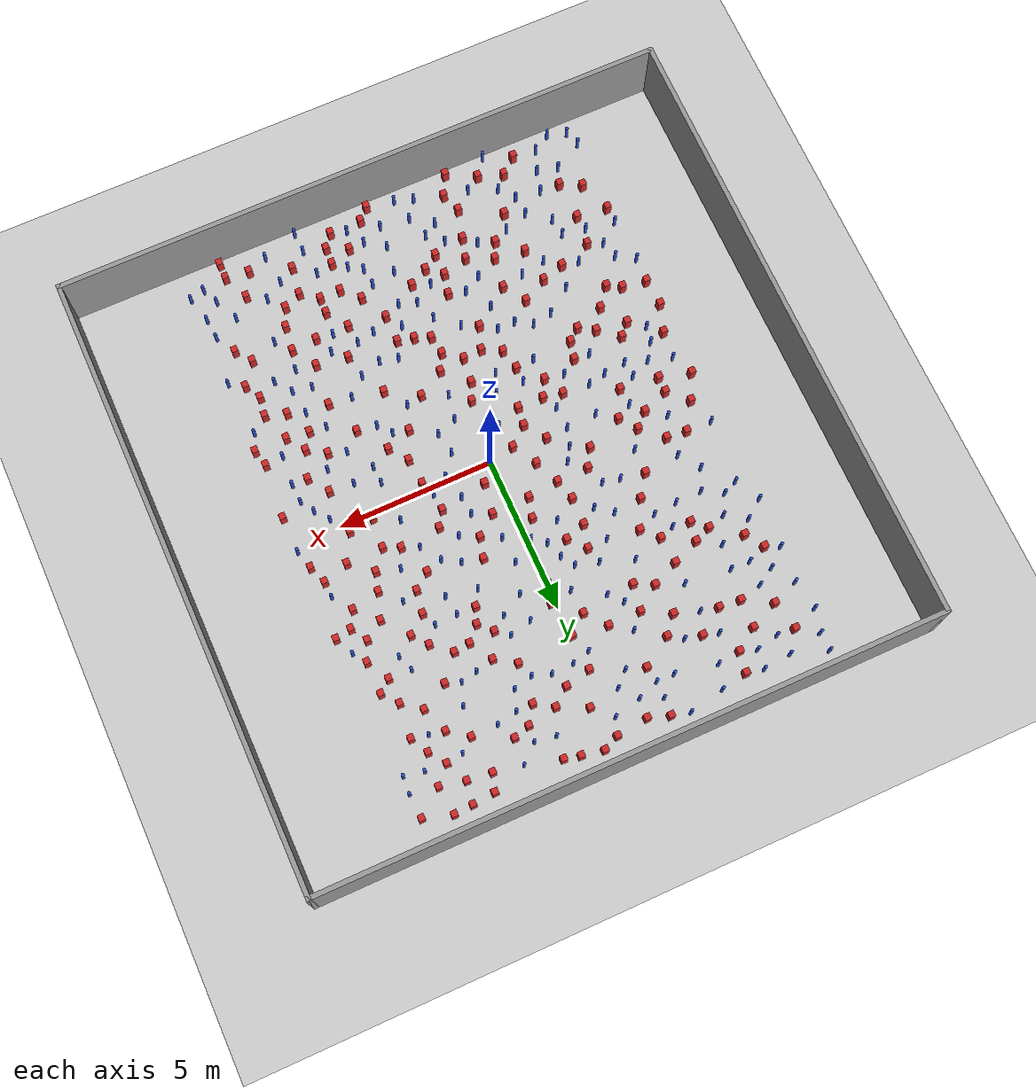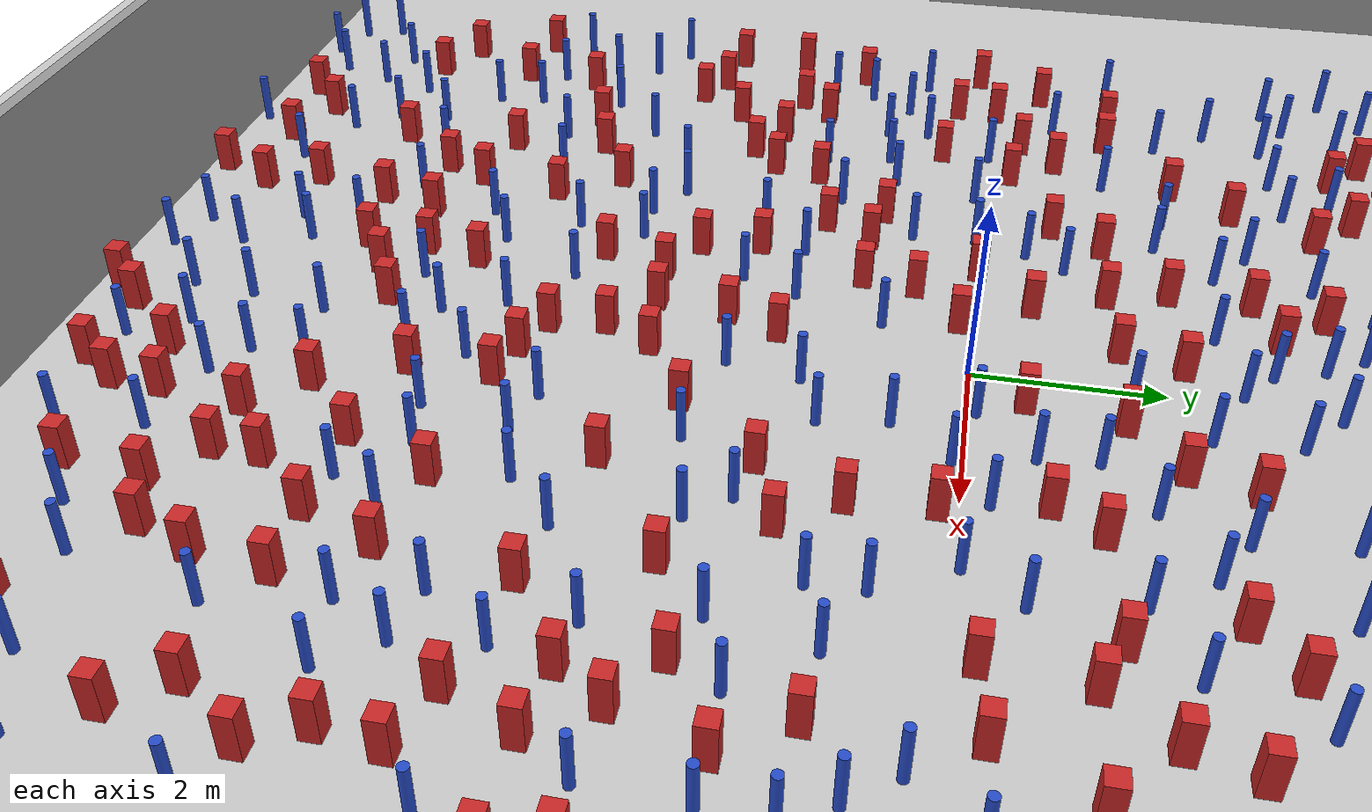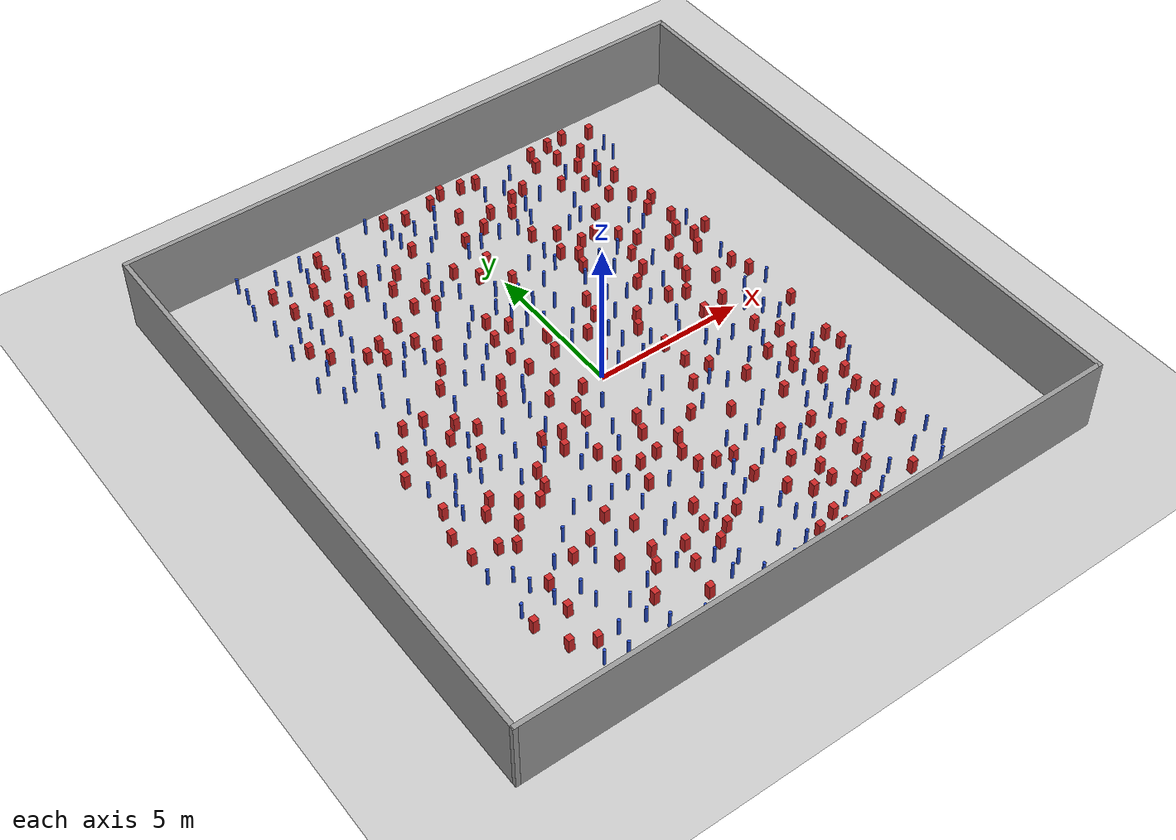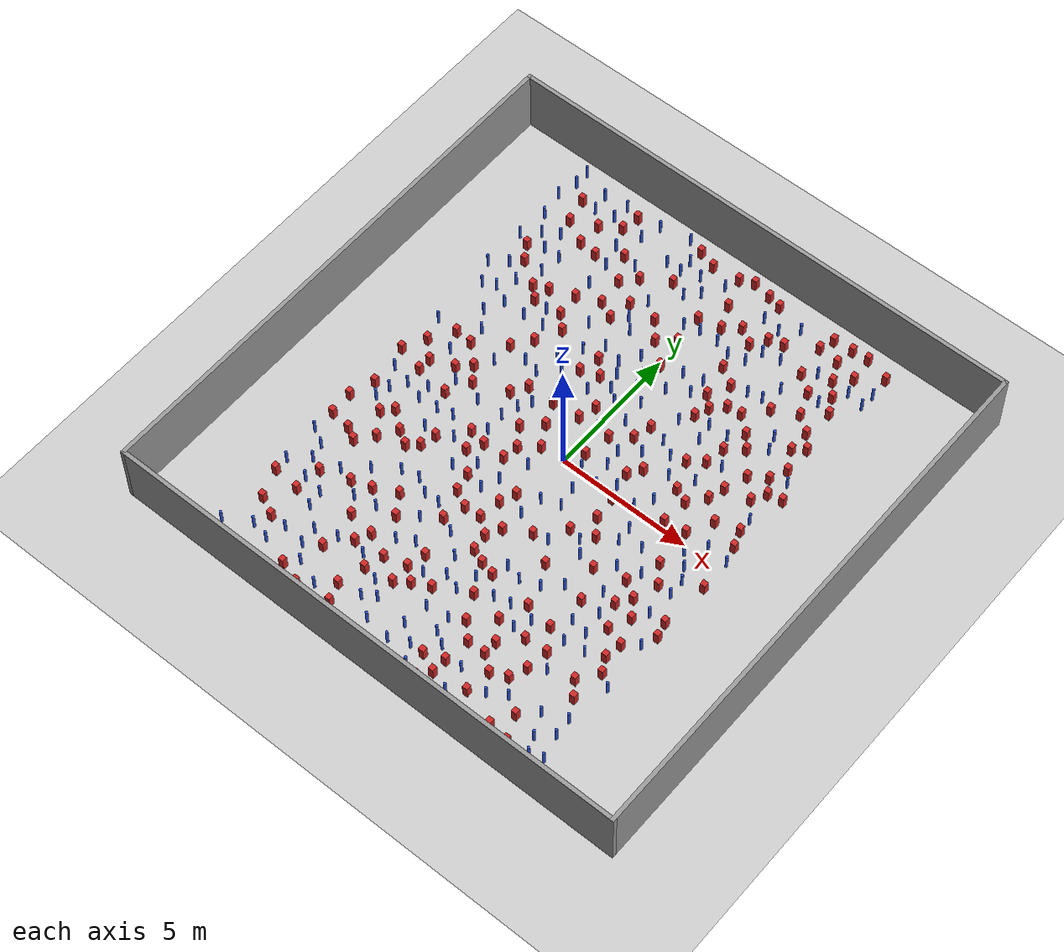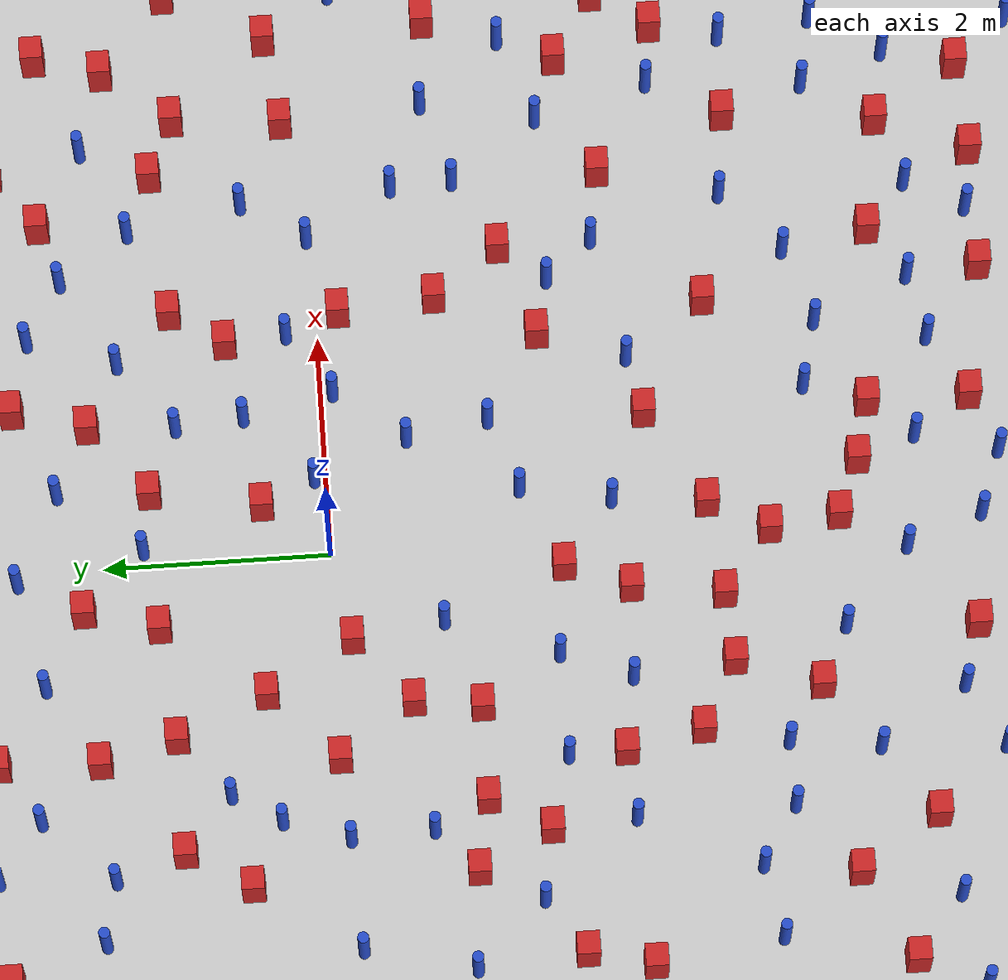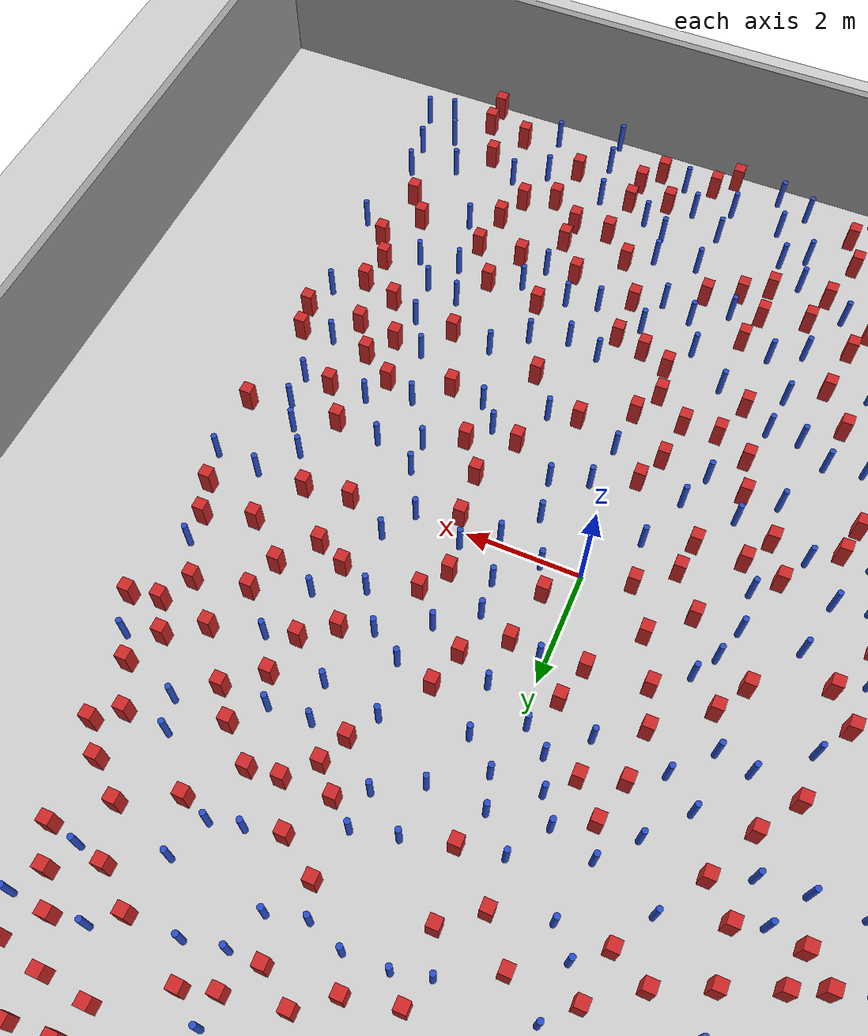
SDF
<sdf version="1.6">
 <world name="default">
  <light name="sun" type="directional">
   <pose>0 0 1000 0 -0 0</pose>
   <diffuse>0.8 0.8 0.8 1</diffuse>
   <specular>0.1 0.1 0.1 1</specular>
   <attenuation>
    <range>1000</range>
    <constant>0.9</constant>
    <linear>0.01</linear>
    <quadratic>0.001</quadratic>
   </attenuation>
   <direction>-0.5 0.5 -1</direction>
  </light>
  <model name="ground_plane">
   <static>1</static>
   <link name="link">
    <collision name="collision">
     <geometry><plane><normal>0 0 1</normal><size>100 100</size></plane></geometry>
     <surface><friction><ode><mu>100</mu><mu2>50</mu2></ode></friction></surface>
    </collision>
    <visual name="visual">
     <cast_shadows>0</cast_shadows>
     <geometry><plane><normal>0 0 1</normal><size>100 100</size></plane></geometry>
     <material>
      <ambient>1.0 1.0 1.0 1.0</ambient>
      <diffuse>0.8 0.8 0.8 1.0</diffuse>
      <specular>0.01 0.01 0.01 1.000000</specular>
     </material>
    </visual>
   </link>
  </model>
  <gravity>0 0 -9.8</gravity>
  <magnetic_field>6e-06 2.3e-05 -4.2e-05</magnetic_field>
  <atmosphere type="adiabatic"/>
  <physics name="default_physics" default="0" type="ode">
   <max_step_size>0.001</max_step_size>
   <real_time_factor>1</real_time_factor>
   <real_time_update_rate>1000</real_time_update_rate>
  </physics>
  <scene><ambient>0.4 0.4 0.4 1</ambient><background>0.7 0.7 0.7 1</background><shadows>1</shadows></scene>
  <spherical_coordinates>
   <surface_model>EARTH_WGS84</surface_model>
   <latitude_deg>0</latitude_deg>
   <longitude_deg>0</longitude_deg>
   <elevation>0</elevation>
   <heading_deg>0</heading_deg>
  </spherical_coordinates>
  <plugin name="gazebo_occupancy_map" filename="libgazebo_2Dmap_plugin.so">
   <map_resolution>0.05</map_resolution>
   <map_topic>generated_map</map_topic>
   <map_height>0.01</map_height>
   <map_size_x>50</map_size_x>
   <map_size_y>50</map_size_y>
  </plugin>
  <model name="NamedLocations">
   <static>true</static>
   <link name="DefaultStart"><pose>8.5 0 0 0 0 3.14</pose></link>
  </model>
  <model name="20x20_walls">
   <pose>0.044518 0.176112 0 0 -0 0</pose>
   <link name="Wall_1">
    <collision name="Wall_1_Collision">
     <geometry><box><size>20 0.15 2.5</size></box></geometry>
     <pose>0 0 1.25 0 -0 0</pose>
    </collision>
    <visual name="Wall_1_Visual">
     <pose>0 0 1.25 0 -0 0</pose>
     <geometry><box><size>20 0.15 2.5</size></box></geometry>
     <material>
      <script><uri>file://media/materials/scripts/gazebo.material</uri><name>Gazebo/Grey</name></script>
      <ambient>0.976471 0.992157 1 1</ambient>
     </material>
     <meta><layer>0</layer></meta>
    </visual>
    <pose>0 9.925 0 0 -0 0</pose>
   </link>
   <link name="Wall_3">
    <collision name="Wall_3_Collision">
     <geometry><box><size>20 0.15 2.5</size></box></geometry>
     <pose>0 0 1.25 0 -0 0</pose>
    </collision>
    <visual name="Wall_3_Visual">
     <pose>0 0 1.25 0 -0 0</pose>
     <geometry><box><size>20 0.15 2.5</size></box></geometry>
     <material>
      <script><uri>file://media/materials/scripts/gazebo.material</uri><name>Gazebo/Grey</name></script>
      <ambient>0.976471 0.992157 1 1</ambient>
     </material>
     <meta><layer>0</layer></meta>
    </visual>
    <pose>9.925 0 0 0 0 -1.5708</pose>
   </link>
   <link name="Wall_4">
    <collision name="Wall_4_Collision">
     <geometry><box><size>20 0.15 2.5</size></box></geometry>
     <pose>0 0 1.25 0 -0 0</pose>
    </collision>
    <visual name="Wall_4_Visual">
     <pose>0 0 1.25 0 -0 0</pose>
     <geometry><box><size>20 0.15 2.5</size></box></geometry>
     <material>
      <script><uri>file://media/materials/scripts/gazebo.material</uri><name>Gazebo/Grey</name></script>
      <ambient>0.976471 0.992157 1 1</ambient>
     </material>
     <meta><layer>0</layer></meta>
    </visual>
    <pose>0 -9.925 0 0 -0 3.14159</pose>
   </link>
   <link name="Wall_5">
    <collision name="Wall_5_Collision">
     <geometry><box><size>20 0.15 2.5</size></box></geometry>
     <pose>0 0 1.25 0 -0 0</pose>
    </collision>
    <visual name="Wall_5_Visual">
     <pose>0 0 1.25 0 -0 0</pose>
     <geometry><box><size>20 0.15 2.5</size></box></geometry>
     <material>
      <script><uri>file://media/materials/scripts/gazebo.material</uri><name>Gazebo/Grey</name></script>
      <ambient>0.976471 0.992157 1 1</ambient>
     </material>
     <meta><layer>0</layer></meta>
    </visual>
    <pose>-9.925 0 0 0 -0 1.5708</pose>
   </link>
   <static>1</static>
  </model>
  <model name="square_post_obstacle0">
   <static>true</static>
   <pose>2.7218843252 -6.55835641108 8.22691968438e-08 7.2212513382e-06 -7.54495500217e-07 2.29674213826e-05</pose>
   <link name="link">
    <pose>0 0 0.25 0 -0 0</pose>
    <inertial>
     <mass>100</mass>
     <inertia>
      <ixx>0.166667</ixx>
      <ixy>0</ixy>
      <ixz>0</ixz>
      <iyy>0.166667</iyy>
      <iyz>0</iyz>
      <izz>0.166667</izz>
     </inertia>
    </inertial>
    <collision name="collision"><geometry><box><size>.2 .2 .5</size></box></geometry></collision>
    <visual name="visual">
     <geometry><box><size>.2 .2 .5</size></box></geometry>
     <material>
      <script><name>Gazebo/Red</name><uri>file://media/materials/scripts/gazebo.material</uri></script>
     </material>
    </visual>
   </link>
  </model>
  <model name="square_post_obstacle1">
   <static>true</static>
   <pose>-1.78963820657 2.10112155441 8.22691968438e-08 7.2212513382e-06 -7.54495500217e-07 2.29674213826e-05</pose>
   <link name="link">
    <pose>0 0 0.25 0 -0 0</pose>
    <inertial>
     <mass>100</mass>
     <inertia>
      <ixx>0.166667</ixx>
      <ixy>0</ixy>
      <ixz>0</ixz>
      <iyy>0.166667</iyy>
      <iyz>0</iyz>
      <izz>0.166667</izz>
     </inertia>
    </inertial>
    <collision name="collision"><geometry><box><size>.2 .2 .5</size></box></geometry></collision>
    <visual name="visual">
     <geometry><box><size>.2 .2 .5</size></box></geometry>
     <material>
      <script><name>Gazebo/Red</name><uri>file://media/materials/scripts/gazebo.material</uri></script>
     </material>
    </visual>
   </link>
  </model>
  <model name="pole_obstacle0">
   <static>true</static>
   <pose>3.049772285 1.62919026066 2.88873142074e-08 -9.90536689395e-09 4.60219949e-07 -1.20965994953e-07</pose>
   <link name="link">
    <pose>0 0 0.3 0 -0 0</pose>
    <inertial>
     <mass>1</mass>
     <inertia><ixx>0.145833</ixx><ixy>0</ixy><ixz>0</ixz><iyy>0.145833</iyy><iyz>0</iyz><izz>0.125</izz></inertia>
    </inertial>
    <collision name="collision">
     <geometry><cylinder><radius>0.05</radius><length>.6</length></cylinder></geometry>
    </collision>
    <visual name="visual">
     <geometry><cylinder><radius>0.05</radius><length>.6</length></cylinder></geometry>
     <material>
      <script><name>Gazebo/Blue</name><uri>file://media/materials/scripts/gazebo.material</uri></script>
     </material>
    </visual>
   </link>
  </model>
  <model name="square_post_obstacle2">
   <static>true</static>
   <pose>5.09710268131 -3.95281234006 8.22691968438e-08 7.22125133819e-06 -7.54495500217e-07 2.29674213826e-05</pose>
   <link name="link">
    <pose>0 0 0.25 0 -0 0</pose>
    <inertial>
     <mass>100</mass>
     <inertia>
      <ixx>0.166667</ixx>
      <ixy>0</ixy>
      <ixz>0</ixz>
      <iyy>0.166667</iyy>
      <iyz>0</iyz>
      <izz>0.166667</izz>
     </inertia>
    </inertial>
    <collision name="collision"><geometry><box><size>.2 .2 .5</size></box></geometry></collision>
    <visual name="visual">
     <geometry><box><size>.2 .2 .5</size></box></geometry>
     <material>
      <script><name>Gazebo/Red</name><uri>file://media/materials/scripts/gazebo.material</uri></script>
     </material>
    </visual>
   </link>
  </model>
  <model name="pole_obstacle1">
   <static>true</static>
   <pose>-1.18250844846 -7.70387494686 2.88873142074e-08 -9.90536689852e-09 4.60219948989e-07 -1.2096599496e-07</pose>
   <link name="link">
    <pose>0 0 0.3 0 -0 0</pose>
    <inertial>
     <mass>1</mass>
     <inertia><ixx>0.145833</ixx><ixy>0</ixy><ixz>0</ixz><iyy>0.145833</iyy><iyz>0</iyz><izz>0.125</izz></inertia>
    </inertial>
    <collision name="collision">
     <geometry><cylinder><radius>0.05</radius><length>.6</length></cylinder></geometry>
    </collision>
    <visual name="visual">
     <geometry><cylinder><radius>0.05</radius><length>.6</length></cylinder></geometry>
     <material>
      <script><name>Gazebo/Blue</name><uri>file://media/materials/scripts/gazebo.material</uri></script>
     </material>
    </visual>
   </link>
  </model>
  <model name="square_post_obstacle3">
   <static>true</static>
   <pose>-1.03680972441 -5.58593640576 8.22691968438e-08 7.2212513382e-06 -7.54495500217e-07 2.29674213826e-05</pose>
   <link name="link">
    <pose>0 0 0.25 0 -0 0</pose>
    <inertial>
     <mass>100</mass>
     <inertia>
      <ixx>0.166667</ixx>
      <ixy>0</ixy>
      <ixz>0</ixz>
      <iyy>0.166667</iyy>
      <iyz>0</iyz>
      <izz>0.166667</izz>
     </inertia>
    </inertial>
    <collision name="collision"><geometry><box><size>.2 .2 .5</size></box></geometry></collision>
    <visual name="visual">
     <geometry><box><size>.2 .2 .5</size></box></geometry>
     <material>
      <script><name>Gazebo/Red</name><uri>file://media/materials/scripts/gazebo.material</uri></script>
     </material>
    </visual>
   </link>
  </model>
  <model name="pole_obstacle2">
   <static>true</static>
   <pose>-5.35833952986 -8.33656841699 2.88873142074e-08 -9.9053668967e-09 4.60219948993e-07 -1.20965994957e-07</pose>
   <link name="link">
    <pose>0 0 0.3 0 -0 0</pose>
    <inertial>
     <mass>1</mass>
     <inertia><ixx>0.145833</ixx><ixy>0</ixy><ixz>0</ixz><iyy>0.145833</iyy><iyz>0</iyz><izz>0.125</izz></inertia>
    </inertial>
    <collision name="collision">
     <geometry><cylinder><radius>0.05</radius><length>.6</length></cylinder></geometry>
    </collision>
    <visual name="visual">
     <geometry><cylinder><radius>0.05</radius><length>.6</length></cylinder></geometry>
     <material>
      <script><name>Gazebo/Blue</name><uri>file://media/materials/scripts/gazebo.material</uri></script>
     </material>
    </visual>
   </link>
  </model>
  <model name="pole_obstacle3">
   <static>true</static>
   <pose>-2.15087941824 0.98724646966 2.88873142074e-08 -9.90536689701e-09 4.60219948992e-07 -1.20965994959e-07</pose>
   <link name="link">
    <pose>0 0 0.3 0 -0 0</pose>
    <inertial>
     <mass>1</mass>
     <inertia><ixx>0.145833</ixx><ixy>0</ixy><ixz>0</ixz><iyy>0.145833</iyy><iyz>0</iyz><izz>0.125</izz></inertia>
    </inertial>
    <collision name="collision">
     <geometry><cylinder><radius>0.05</radius><length>.6</length></cylinder></geometry>
    </collision>
    <visual name="visual">
     <geometry><cylinder><radius>0.05</radius><length>.6</length></cylinder></geometry>
     <material>
      <script><name>Gazebo/Blue</name><uri>file://media/materials/scripts/gazebo.material</uri></script>
     </material>
    </visual>
   </link>
  </model>
  <model name="square_post_obstacle4">
   <static>true</static>
   <pose>1.05407559026 -4.77953565677 8.22691968438e-08 7.2212513382e-06 -7.54495500217e-07 2.29674213826e-05</pose>
   <link name="link">
    <pose>0 0 0.25 0 -0 0</pose>
    <inertial>
     <mass>100</mass>
     <inertia>
      <ixx>0.166667</ixx>
      <ixy>0</ixy>
      <ixz>0</ixz>
      <iyy>0.166667</iyy>
      <iyz>0</iyz>
      <izz>0.166667</izz>
     </inertia>
    </inertial>
    <collision name="collision"><geometry><box><size>.2 .2 .5</size></box></geometry></collision>
    <visual name="visual">
     <geometry><box><size>.2 .2 .5</size></box></geometry>
     <material>
      <script><name>Gazebo/Red</name><uri>file://media/materials/scripts/gazebo.material</uri></script>
     </material>
    </visual>
   </link>
  </model>
  <model name="square_post_obstacle5">
   <static>true</static>
   <pose>-1.62502940197 7.73699112247 8.22691968438e-08 7.2212513382e-06 -7.54495500217e-07 2.29674213826e-05</pose>
   <link name="link">
    <pose>0 0 0.25 0 -0 0</pose>
    <inertial>
     <mass>100</mass>
     <inertia>
      <ixx>0.166667</ixx>
      <ixy>0</ixy>
      <ixz>0</ixz>
      <iyy>0.166667</iyy>
      <iyz>0</iyz>
      <izz>0.166667</izz>
     </inertia>
    </inertial>
    <collision name="collision"><geometry><box><size>.2 .2 .5</size></box></geometry></collision>
    <visual name="visual">
     <geometry><box><size>.2 .2 .5</size></box></geometry>
     <material>
      <script><name>Gazebo/Red</name><uri>file://media/materials/scripts/gazebo.material</uri></script>
     </material>
    </visual>
   </link>
  </model>
  <model name="square_post_obstacle6">
   <static>true</static>
   <pose>-5.69873190846 -3.81089866101 8.22691968438e-08 7.2212513382e-06 -7.54495500217e-07 2.29674213826e-05</pose>
   <link name="link">
    <pose>0 0 0.25 0 -0 0</pose>
    <inertial>
     <mass>100</mass>
     <inertia>
      <ixx>0.166667</ixx>
      <ixy>0</ixy>
      <ixz>0</ixz>
      <iyy>0.166667</iyy>
      <iyz>0</iyz>
      <izz>0.166667</izz>
     </inertia>
    </inertial>
    <collision name="collision"><geometry><box><size>.2 .2 .5</size></box></geometry></collision>
    <visual name="visual">
     <geometry><box><size>.2 .2 .5</size></box></geometry>
     <material>
      <script><name>Gazebo/Red</name><uri>file://media/materials/scripts/gazebo.material</uri></script>
     </material>
    </visual>
   </link>
  </model>
  <model name="pole_obstacle4">
   <static>true</static>
   <pose>3.890656895 -2.05234578948 2.88873142074e-08 -9.90536690232e-09 4.6021994898e-07 -1.20965994968e-07</pose>
   <link name="link">
    <pose>0 0 0.3 0 -0 0</pose>
    <inertial>
     <mass>1</mass>
     <inertia><ixx>0.145833</ixx><ixy>0</ixy><ixz>0</ixz><iyy>0.145833</iyy><iyz>0</iyz><izz>0.125</izz></inertia>
    </inertial>
    <collision name="collision">
     <geometry><cylinder><radius>0.05</radius><length>.6</length></cylinder></geometry>
    </collision>
    <visual name="visual">
     <geometry><cylinder><radius>0.05</radius><length>.6</length></cylinder></geometry>
     <material>
      <script><name>Gazebo/Blue</name><uri>file://media/materials/scripts/gazebo.material</uri></script>
     </material>
    </visual>
   </link>
  </model>
  <model name="pole_obstacle5">
   <static>true</static>
   <pose>-1.66406877257 -7.27643636776 2.88873142074e-08 -9.90536689852e-09 4.60219948989e-07 -1.2096599496e-07</pose>
   <link name="link">
    <pose>0 0 0.3 0 -0 0</pose>
    <inertial>
     <mass>1</mass>
     <inertia><ixx>0.145833</ixx><ixy>0</ixy><ixz>0</ixz><iyy>0.145833</iyy><iyz>0</iyz><izz>0.125</izz></inertia>
    </inertial>
    <collision name="collision">
     <geometry><cylinder><radius>0.05</radius><length>.6</length></cylinder></geometry>
    </collision>
    <visual name="visual">
     <geometry><cylinder><radius>0.05</radius><length>.6</length></cylinder></geometry>
     <material>
      <script><name>Gazebo/Blue</name><uri>file://media/materials/scripts/gazebo.material</uri></script>
     </material>
    </visual>
   </link>
  </model>
  <model name="square_post_obstacle7">
   <static>true</static>
   <pose>-5.01786289002 0.467314771592 8.22691968438e-08 7.2212513382e-06 -7.54495500217e-07 2.29674213826e-05</pose>
   <link name="link">
    <pose>0 0 0.25 0 -0 0</pose>
    <inertial>
     <mass>100</mass>
     <inertia>
      <ixx>0.166667</ixx>
      <ixy>0</ixy>
      <ixz>0</ixz>
      <iyy>0.166667</iyy>
      <iyz>0</iyz>
      <izz>0.166667</izz>
     </inertia>
    </inertial>
    <collision name="collision"><geometry><box><size>.2 .2 .5</size></box></geometry></collision>
    <visual name="visual">
     <geometry><box><size>.2 .2 .5</size></box></geometry>
     <material>
      <script><name>Gazebo/Red</name><uri>file://media/materials/scripts/gazebo.material</uri></script>
     </material>
    </visual>
   </link>
  </model>
  <model name="square_post_obstacle8">
   <static>true</static>
   <pose>4.57876840298 7.04523477632 8.22691968438e-08 7.2212513382e-06 -7.54495500217e-07 2.29674213826e-05</pose>
   <link name="link">
    <pose>0 0 0.25 0 -0 0</pose>
    <inertial>
     <mass>100</mass>
     <inertia>
      <ixx>0.166667</ixx>
      <ixy>0</ixy>
      <ixz>0</ixz>
      <iyy>0.166667</iyy>
      <iyz>0</iyz>
      <izz>0.166667</izz>
     </inertia>
    </inertial>
    <collision name="collision"><geometry><box><size>.2 .2 .5</size></box></geometry></collision>
    <visual name="visual">
     <geometry><box><size>.2 .2 .5</size></box></geometry>
     <material>
      <script><name>Gazebo/Red</name><uri>file://media/materials/scripts/gazebo.material</uri></script>
     </material>
    </visual>
   </link>
  </model>
  <model name="pole_obstacle6">
   <static>true</static>
   <pose>0.981375714166 -0.723780105784 2.88873142074e-08 -9.90536689596e-09 4.60219948995e-07 -1.20965994957e-07</pose>
   <link name="link">
    <pose>0 0 0.3 0 -0 0</pose>
    <inertial>
     <mass>1</mass>
     <inertia><ixx>0.145833</ixx><ixy>0</ixy><ixz>0</ixz><iyy>0.145833</iyy><iyz>0</iyz><izz>0.125</izz></inertia>
    </inertial>
    <collision name="collision">
     <geometry><cylinder><radius>0.05</radius><length>.6</length></cylinder></geometry>
    </collision>
    <visual name="visual">
     <geometry><cylinder><radius>0.05</radius><length>.6</length></cylinder></geometry>
     <material>
      <script><name>Gazebo/Blue</name><uri>file://media/materials/scripts/gazebo.material</uri></script>
     </material>
    </visual>
   </link>
  </model>
  <model name="pole_obstacle7">
   <static>true</static>
   <pose>-4.51328137769 -4.27017657904 2.88873142074e-08 -9.90536690842e-09 4.60219948965e-07 -1.20965994976e-07</pose>
   <link name="link">
    <pose>0 0 0.3 0 -0 0</pose>
    <inertial>
     <mass>1</mass>
     <inertia><ixx>0.145833</ixx><ixy>0</ixy><ixz>0</ixz><iyy>0.145833</iyy><iyz>0</iyz><izz>0.125</izz></inertia>
    </inertial>
    <collision name="collision">
     <geometry><cylinder><radius>0.05</radius><length>.6</length></cylinder></geometry>
    </collision>
    <visual name="visual">
     <geometry><cylinder><radius>0.05</radius><length>.6</length></cylinder></geometry>
     <material>
      <script><name>Gazebo/Blue</name><uri>file://media/materials/scripts/gazebo.material</uri></script>
     </material>
    </visual>
   </link>
  </model>
  <model name="square_post_obstacle9">
   <static>true</static>
   <pose>-0.614013611077 -3.40406688637 8.22691968438e-08 7.2212513382e-06 -7.54495500217e-07 2.29674213826e-05</pose>
   <link name="link">
    <pose>0 0 0.25 0 -0 0</pose>
    <inertial>
     <mass>100</mass>
     <inertia>
      <ixx>0.166667</ixx>
      <ixy>0</ixy>
      <ixz>0</ixz>
      <iyy>0.166667</iyy>
      <iyz>0</iyz>
      <izz>0.166667</izz>
     </inertia>
    </inertial>
    <collision name="collision"><geometry><box><size>.2 .2 .5</size></box></geometry></collision>
    <visual name="visual">
     <geometry><box><size>.2 .2 .5</size></box></geometry>
     <material>
      <script><name>Gazebo/Red</name><uri>file://media/materials/scripts/gazebo.material</uri></script>
     </material>
    </visual>
   </link>
  </model>
  <model name="square_post_obstacle10">
   <static>true</static>
   <pose>-0.503892283622 -2.59505104395 8.22691968438e-08 7.2212513382e-06 -7.54495500217e-07 2.29674213826e-05</pose>
   <link name="link">
    <pose>0 0 0.25 0 -0 0</pose>
    <inertial>
     <mass>100</mass>
     <inertia>
      <ixx>0.166667</ixx>
      <ixy>0</ixy>
      <ixz>0</ixz>
      <iyy>0.166667</iyy>
      <iyz>0</iyz>
      <izz>0.166667</izz>
     </inertia>
    </inertial>
    <collision name="collision"><geometry><box><size>.2 .2 .5</size></box></geometry></collision>
    <visual name="visual">
     <geometry><box><size>.2 .2 .5</size></box></geometry>
     <material>
      <script><name>Gazebo/Red</name><uri>file://media/materials/scripts/gazebo.material</uri></script>
     </material>
    </visual>
   </link>
  </model>
  <model name="square_post_obstacle11">
   <static>true</static>
   <pose>3.11358270299 -8.40264183046 8.22691968438e-08 7.22125133819e-06 -7.54495500217e-07 2.29674213826e-05</pose>
   <link name="link">
    <pose>0 0 0.25 0 -0 0</pose>
    <inertial>
     <mass>100</mass>
     <inertia>
      <ixx>0.166667</ixx>
      <ixy>0</ixy>
      <ixz>0</ixz>
      <iyy>0.166667</iyy>
      <iyz>0</iyz>
      <izz>0.166667</izz>
     </inertia>
    </inertial>
    <collision name="collision"><geometry><box><size>.2 .2 .5</size></box></geometry></collision>
    <visual name="visual">
     <geometry><box><size>.2 .2 .5</size></box></geometry>
     <material>
      <script><name>Gazebo/Red</name><uri>file://media/materials/scripts/gazebo.material</uri></script>
     </material>
    </visual>
   </link>
  </model>
  <model name="square_post_obstacle12">
   <static>true</static>
   <pose>-1.87809703781 0.0274566132606 8.22691968438e-08 7.2212513382e-06 -7.54495500217e-07 2.29674213826e-05</pose>
   <link name="link">
    <pose>0 0 0.25 0 -0 0</pose>
    <inertial>
     <mass>100</mass>
     <inertia>
      <ixx>0.166667</ixx>
      <ixy>0</ixy>
      <ixz>0</ixz>
      <iyy>0.166667</iyy>
      <iyz>0</iyz>
      <izz>0.166667</izz>
     </inertia>
    </inertial>
    <collision name="collision"><geometry><box><size>.2 .2 .5</size></box></geometry></collision>
    <visual name="visual">
     <geometry><box><size>.2 .2 .5</size></box></geometry>
     <material>
      <script><name>Gazebo/Red</name><uri>file://media/materials/scripts/gazebo.material</uri></script>
     </material>
    </visual>
   </link>
  </model>
  <model name="square_post_obstacle13">
   <static>true</static>
   <pose>3.40323351395 4.99912729848 8.22691968438e-08 7.2212513382e-06 -7.54495500217e-07 2.29674213826e-05</pose>
   <link name="link">
    <pose>0 0 0.25 0 -0 0</pose>
    <inertial>
     <mass>100</mass>
     <inertia>
      <ixx>0.166667</ixx>
      <ixy>0</ixy>
      <ixz>0</ixz>
      <iyy>0.166667</iyy>
      <iyz>0</iyz>
      <izz>0.166667</izz>
     </inertia>
    </inertial>
    <collision name="collision"><geometry><box><size>.2 .2 .5</size></box></geometry></collision>
    <visual name="visual">
     <geometry><box><size>.2 .2 .5</size></box></geometry>
     <material>
      <script><name>Gazebo/Red</name><uri>file://media/materials/scripts/gazebo.material</uri></script>
     </material>
    </visual>
   </link>
  </model>
  <model name="pole_obstacle8">
   <static>true</static>
   <pose>-2.55678211744 -3.87267501913 2.88873142074e-08 -9.90536690232e-09 4.6021994898e-07 -1.20965994968e-07</pose>
   <link name="link">
    <pose>0 0 0.3 0 -0 0</pose>
    <inertial>
     <mass>1</mass>
     <inertia><ixx>0.145833</ixx><ixy>0</ixy><ixz>0</ixz><iyy>0.145833</iyy><iyz>0</iyz><izz>0.125</izz></inertia>
    </inertial>
    <collision name="collision">
     <geometry><cylinder><radius>0.05</radius><length>.6</length></cylinder></geometry>
    </collision>
    <visual name="visual">
     <geometry><cylinder><radius>0.05</radius><length>.6</length></cylinder></geometry>
     <material>
      <script><name>Gazebo/Blue</name><uri>file://media/materials/scripts/gazebo.material</uri></script>
     </material>
    </visual>
   </link>
  </model>
  <model name="square_post_obstacle14">
   <static>true</static>
   <pose>-0.00798470232035 5.96544968647 8.22691968438e-08 7.2212513382e-06 -7.54495500217e-07 2.29674213826e-05</pose>
   <link name="link">
    <pose>0 0 0.25 0 -0 0</pose>
    <inertial>
     <mass>100</mass>
     <inertia>
      <ixx>0.166667</ixx>
      <ixy>0</ixy>
      <ixz>0</ixz>
      <iyy>0.166667</iyy>
      <iyz>0</iyz>
      <izz>0.166667</izz>
     </inertia>
    </inertial>
    <collision name="collision"><geometry><box><size>.2 .2 .5</size></box></geometry></collision>
    <visual name="visual">
     <geometry><box><size>.2 .2 .5</size></box></geometry>
     <material>
      <script><name>Gazebo/Red</name><uri>file://media/materials/scripts/gazebo.material</uri></script>
     </material>
    </visual>
   </link>
  </model>
  <model name="square_post_obstacle15">
   <static>true</static>
   <pose>-1.09674026211 3.2081970894 8.22691968438e-08 7.22125133819e-06 -7.54495500217e-07 2.29674213826e-05</pose>
   <link name="link">
    <pose>0 0 0.25 0 -0 0</pose>
    <inertial>
     <mass>100</mass>
     <inertia>
      <ixx>0.166667</ixx>
      <ixy>0</ixy>
      <ixz>0</ixz>
      <iyy>0.166667</iyy>
      <iyz>0</iyz>
      <izz>0.166667</izz>
     </inertia>
    </inertial>
    <collision name="collision"><geometry><box><size>.2 .2 .5</size></box></geometry></collision>
    <visual name="visual">
     <geometry><box><size>.2 .2 .5</size></box></geometry>
     <material>
      <script><name>Gazebo/Red</name><uri>file://media/materials/scripts/gazebo.material</uri></script>
     </material>
    </visual>
   </link>
  </model>
  <model name="square_post_obstacle16">
   <static>true</static>
   <pose>-4.71330819208 -5.01997671932 8.22691968438e-08 7.2212513382e-06 -7.54495500217e-07 2.29674213826e-05</pose>
   <link name="link">
    <pose>0 0 0.25 0 -0 0</pose>
    <inertial>
     <mass>100</mass>
     <inertia>
      <ixx>0.166667</ixx>
      <ixy>0</ixy>
      <ixz>0</ixz>
      <iyy>0.166667</iyy>
      <iyz>0</iyz>
      <izz>0.166667</izz>
     </inertia>
    </inertial>
    <collision name="collision"><geometry><box><size>.2 .2 .5</size></box></geometry></collision>
    <visual name="visual">
     <geometry><box><size>.2 .2 .5</size></box></geometry>
     <material>
      <script><name>Gazebo/Red</name><uri>file://media/materials/scripts/gazebo.material</uri></script>
     </material>
    </visual>
   </link>
  </model>
  <model name="pole_obstacle9">
   <static>true</static>
   <pose>0.721651293033 -5.1782673412 2.88873142074e-08 -9.90536689661e-09 4.60219948993e-07 -1.20965994957e-07</pose>
   <link name="link">
    <pose>0 0 0.3 0 -0 0</pose>
    <inertial>
     <mass>1</mass>
     <inertia><ixx>0.145833</ixx><ixy>0</ixy><ixz>0</ixz><iyy>0.145833</iyy><iyz>0</iyz><izz>0.125</izz></inertia>
    </inertial>
    <collision name="collision">
     <geometry><cylinder><radius>0.05</radius><length>.6</length></cylinder></geometry>
    </collision>
    <visual name="visual">
     <geometry><cylinder><radius>0.05</radius><length>.6</length></cylinder></geometry>
     <material>
      <script><name>Gazebo/Blue</name><uri>file://media/materials/scripts/gazebo.material</uri></script>
     </material>
    </visual>
   </link>
  </model>
  <model name="square_post_obstacle17">
   <static>true</static>
   <pose>5.76063728674 -4.1655559737 8.22691968438e-08 7.2212513382e-06 -7.54495500217e-07 2.29674213826e-05</pose>
   <link name="link">
    <pose>0 0 0.25 0 -0 0</pose>
    <inertial>
     <mass>100</mass>
     <inertia>
      <ixx>0.166667</ixx>
      <ixy>0</ixy>
      <ixz>0</ixz>
      <iyy>0.166667</iyy>
      <iyz>0</iyz>
      <izz>0.166667</izz>
     </inertia>
    </inertial>
    <collision name="collision"><geometry><box><size>.2 .2 .5</size></box></geometry></collision>
    <visual name="visual">
     <geometry><box><size>.2 .2 .5</size></box></geometry>
     <material>
      <script><name>Gazebo/Red</name><uri>file://media/materials/scripts/gazebo.material</uri></script>
     </material>
    </visual>
   </link>
  </model>
  <model name="square_post_obstacle18">
   <static>true</static>
   <pose>-1.26172231099 0.629585137746 8.22691968438e-08 7.2212513382e-06 -7.54495500217e-07 2.29674213826e-05</pose>
   <link name="link">
    <pose>0 0 0.25 0 -0 0</pose>
    <inertial>
     <mass>100</mass>
     <inertia>
      <ixx>0.166667</ixx>
      <ixy>0</ixy>
      <ixz>0</ixz>
      <iyy>0.166667</iyy>
      <iyz>0</iyz>
      <izz>0.166667</izz>
     </inertia>
    </inertial>
    <collision name="collision"><geometry><box><size>.2 .2 .5</size></box></geometry></collision>
    <visual name="visual">
     <geometry><box><size>.2 .2 .5</size></box></geometry>
     <material>
      <script><name>Gazebo/Red</name><uri>file://media/materials/scripts/gazebo.material</uri></script>
     </material>
    </visual>
   </link>
  </model>
  <model name="pole_obstacle10">
   <static>true</static>
   <pose>3.09828603767 7.49898058543 2.88873142074e-08 -9.90536689859e-09 4.60219948989e-07 -1.20965994961e-07</pose>
   <link name="link">
    <pose>0 0 0.3 0 -0 0</pose>
    <inertial>
     <mass>1</mass>
     <inertia><ixx>0.145833</ixx><ixy>0</ixy><ixz>0</ixz><iyy>0.145833</iyy><iyz>0</iyz><izz>0.125</izz></inertia>
    </inertial>
    <collision name="collision">
     <geometry><cylinder><radius>0.05</radius><length>.6</length></cylinder></geometry>
    </collision>
    <visual name="visual">
     <geometry><cylinder><radius>0.05</radius><length>.6</length></cylinder></geometry>
     <material>
      <script><name>Gazebo/Blue</name><uri>file://media/materials/scripts/gazebo.material</uri></script>
     </material>
    </visual>
   </link>
  </model>
  <model name="square_post_obstacle19">
   <static>true</static>
   <pose>-1.20047073616 -6.24779284353 8.22691968438e-08 7.2212513382e-06 -7.54495500217e-07 2.29674213826e-05</pose>
   <link name="link">
    <pose>0 0 0.25 0 -0 0</pose>
    <inertial>
     <mass>100</mass>
     <inertia>
      <ixx>0.166667</ixx>
      <ixy>0</ixy>
      <ixz>0</ixz>
      <iyy>0.166667</iyy>
      <iyz>0</iyz>
      <izz>0.166667</izz>
     </inertia>
    </inertial>
    <collision name="collision"><geometry><box><size>.2 .2 .5</size></box></geometry></collision>
    <visual name="visual">
     <geometry><box><size>.2 .2 .5</size></box></geometry>
     <material>
      <script><name>Gazebo/Red</name><uri>file://media/materials/scripts/gazebo.material</uri></script>
     </material>
    </visual>
   </link>
  </model>
  <model name="pole_obstacle11">
   <static>true</static>
   <pose>-5.76309928605 4.44789576285 2.88873142074e-08 -9.90536690842e-09 4.60219948965e-07 -1.20965994976e-07</pose>
   <link name="link">
    <pose>0 0 0.3 0 -0 0</pose>
    <inertial>
     <mass>1</mass>
     <inertia><ixx>0.145833</ixx><ixy>0</ixy><ixz>0</ixz><iyy>0.145833</iyy><iyz>0</iyz><izz>0.125</izz></inertia>
    </inertial>
    <collision name="collision">
     <geometry><cylinder><radius>0.05</radius><length>.6</length></cylinder></geometry>
    </collision>
    <visual name="visual">
     <geometry><cylinder><radius>0.05</radius><length>.6</length></cylinder></geometry>
     <material>
      <script><name>Gazebo/Blue</name><uri>file://media/materials/scripts/gazebo.material</uri></script>
     </material>
    </visual>
   </link>
  </model>
  <model name="square_post_obstacle20">
   <static>true</static>
   <pose>-5.80783486104 -7.61061813512 8.22691968438e-08 7.22125133819e-06 -7.54495500217e-07 2.29674213826e-05</pose>
   <link name="link">
    <pose>0 0 0.25 0 -0 0</pose>
    <inertial>
     <mass>100</mass>
     <inertia>
      <ixx>0.166667</ixx>
      <ixy>0</ixy>
      <ixz>0</ixz>
      <iyy>0.166667</iyy>
      <iyz>0</iyz>
      <izz>0.166667</izz>
     </inertia>
    </inertial>
    <collision name="collision"><geometry><box><size>.2 .2 .5</size></box></geometry></collision>
    <visual name="visual">
     <geometry><box><size>.2 .2 .5</size></box></geometry>
     <material>
      <script><name>Gazebo/Red</name><uri>file://media/materials/scripts/gazebo.material</uri></script>
     </material>
    </visual>
   </link>
  </model>
  <model name="pole_obstacle12">
   <static>true</static>
   <pose>-1.70624863904 8.2460111701 2.88873142074e-08 -9.90536690474e-09 4.60219948974e-07 -1.2096599497e-07</pose>
   <link name="link">
    <pose>0 0 0.3 0 -0 0</pose>
    <inertial>
     <mass>1</mass>
     <inertia><ixx>0.145833</ixx><ixy>0</ixy><ixz>0</ixz><iyy>0.145833</iyy><iyz>0</iyz><izz>0.125</izz></inertia>
    </inertial>
    <collision name="collision">
     <geometry><cylinder><radius>0.05</radius><length>.6</length></cylinder></geometry>
    </collision>
    <visual name="visual">
     <geometry><cylinder><radius>0.05</radius><length>.6</length></cylinder></geometry>
     <material>
      <script><name>Gazebo/Blue</name><uri>file://media/materials/scripts/gazebo.material</uri></script>
     </material>
    </visual>
   </link>
  </model>
  <model name="square_post_obstacle21">
   <static>true</static>
   <pose>1.26049091219 2.07048775211 8.22691968438e-08 7.2212513382e-06 -7.54495500217e-07 2.29674213826e-05</pose>
   <link name="link">
    <pose>0 0 0.25 0 -0 0</pose>
    <inertial>
     <mass>100</mass>
     <inertia>
      <ixx>0.166667</ixx>
      <ixy>0</ixy>
      <ixz>0</ixz>
      <iyy>0.166667</iyy>
      <iyz>0</iyz>
      <izz>0.166667</izz>
     </inertia>
    </inertial>
    <collision name="collision"><geometry><box><size>.2 .2 .5</size></box></geometry></collision>
    <visual name="visual">
     <geometry><box><size>.2 .2 .5</size></box></geometry>
     <material>
      <script><name>Gazebo/Red</name><uri>file://media/materials/scripts/gazebo.material</uri></script>
     </material>
    </visual>
   </link>
  </model>
  <model name="pole_obstacle13">
   <static>true</static>
   <pose>4.67971651499 -4.56127696878 2.88873142074e-08 -9.90536690842e-09 4.60219948965e-07 -1.20965994976e-07</pose>
   <link name="link">
    <pose>0 0 0.3 0 -0 0</pose>
    <inertial>
     <mass>1</mass>
     <inertia><ixx>0.145833</ixx><ixy>0</ixy><ixz>0</ixz><iyy>0.145833</iyy><iyz>0</iyz><izz>0.125</izz></inertia>
    </inertial>
    <collision name="collision">
     <geometry><cylinder><radius>0.05</radius><length>.6</length></cylinder></geometry>
    </collision>
    <visual name="visual">
     <geometry><cylinder><radius>0.05</radius><length>.6</length></cylinder></geometry>
     <material>
      <script><name>Gazebo/Blue</name><uri>file://media/materials/scripts/gazebo.material</uri></script>
     </material>
    </visual>
   </link>
  </model>
  <model name="square_post_obstacle22">
   <static>true</static>
   <pose>-3.24477735342 3.83881500266 8.22691968438e-08 7.2212513382e-06 -7.54495500217e-07 2.29674213826e-05</pose>
   <link name="link">
    <pose>0 0 0.25 0 -0 0</pose>
    <inertial>
     <mass>100</mass>
     <inertia>
      <ixx>0.166667</ixx>
      <ixy>0</ixy>
      <ixz>0</ixz>
      <iyy>0.166667</iyy>
      <iyz>0</iyz>
      <izz>0.166667</izz>
     </inertia>
    </inertial>
    <collision name="collision"><geometry><box><size>.2 .2 .5</size></box></geometry></collision>
    <visual name="visual">
     <geometry><box><size>.2 .2 .5</size></box></geometry>
     <material>
      <script><name>Gazebo/Red</name><uri>file://media/materials/scripts/gazebo.material</uri></script>
     </material>
    </visual>
   </link>
  </model>
  <model name="pole_obstacle14">
   <static>true</static>
   <pose>-2.21424441425 3.69005767806 2.88873142074e-08 -9.90536690232e-09 4.6021994898e-07 -1.20965994968e-07</pose>
   <link name="link">
    <pose>0 0 0.3 0 -0 0</pose>
    <inertial>
     <mass>1</mass>
     <inertia><ixx>0.145833</ixx><ixy>0</ixy><ixz>0</ixz><iyy>0.145833</iyy><iyz>0</iyz><izz>0.125</izz></inertia>
    </inertial>
    <collision name="collision">
     <geometry><cylinder><radius>0.05</radius><length>.6</length></cylinder></geometry>
    </collision>
    <visual name="visual">
     <geometry><cylinder><radius>0.05</radius><length>.6</length></cylinder></geometry>
     <material>
      <script><name>Gazebo/Blue</name><uri>file://media/materials/scripts/gazebo.material</uri></script>
     </material>
    </visual>
   </link>
  </model>
  <model name="pole_obstacle15">
   <static>true</static>
   <pose>1.83130481403 1.78242259484 2.88873142074e-08 -9.90536689672e-09 4.60219948993e-07 -1.20965994959e-07</pose>
   <link name="link">
    <pose>0 0 0.3 0 -0 0</pose>
    <inertial>
     <mass>1</mass>
     <inertia><ixx>0.145833</ixx><ixy>0</ixy><ixz>0</ixz><iyy>0.145833</iyy><iyz>0</iyz><izz>0.125</izz></inertia>
    </inertial>
    <collision name="collision">
     <geometry><cylinder><radius>0.05</radius><length>.6</length></cylinder></geometry>
    </collision>
    <visual name="visual">
     <geometry><cylinder><radius>0.05</radius><length>.6</length></cylinder></geometry>
     <material>
      <script><name>Gazebo/Blue</name><uri>file://media/materials/scripts/gazebo.material</uri></script>
     </material>
    </visual>
   </link>
  </model>
  <model name="pole_obstacle16">
   <static>true</static>
   <pose>3.32132167801 -0.72724868222 2.88873142074e-08 -9.90536689285e-09 4.60219949002e-07 -1.20965994953e-07</pose>
   <link name="link">
    <pose>0 0 0.3 0 -0 0</pose>
    <inertial>
     <mass>1</mass>
     <inertia><ixx>0.145833</ixx><ixy>0</ixy><ixz>0</ixz><iyy>0.145833</iyy><iyz>0</iyz><izz>0.125</izz></inertia>
    </inertial>
    <collision name="collision">
     <geometry><cylinder><radius>0.05</radius><length>.6</length></cylinder></geometry>
    </collision>
    <visual name="visual">
     <geometry><cylinder><radius>0.05</radius><length>.6</length></cylinder></geometry>
     <material>
      <script><name>Gazebo/Blue</name><uri>file://media/materials/scripts/gazebo.material</uri></script>
     </material>
    </visual>
   </link>
  </model>
  <model name="square_post_obstacle23">
   <static>true</static>
   <pose>5.94298214702 -5.29836372098 8.22691968438e-08 7.2212513382e-06 -7.54495500217e-07 2.29674213826e-05</pose>
   <link name="link">
    <pose>0 0 0.25 0 -0 0</pose>
    <inertial>
     <mass>100</mass>
     <inertia>
      <ixx>0.166667</ixx>
      <ixy>0</ixy>
      <ixz>0</ixz>
      <iyy>0.166667</iyy>
      <iyz>0</iyz>
      <izz>0.166667</izz>
     </inertia>
    </inertial>
    <collision name="collision"><geometry><box><size>.2 .2 .5</size></box></geometry></collision>
    <visual name="visual">
     <geometry><box><size>.2 .2 .5</size></box></geometry>
     <material>
      <script><name>Gazebo/Red</name><uri>file://media/materials/scripts/gazebo.material</uri></script>
     </material>
    </visual>
   </link>
  </model>
  <model name="pole_obstacle17">
   <static>true</static>
   <pose>2.37395274039 -2.05262754893 2.88873142074e-08 -9.90536690232e-09 4.6021994898e-07 -1.20965994968e-07</pose>
   <link name="link">
    <pose>0 0 0.3 0 -0 0</pose>
    <inertial>
     <mass>1</mass>
     <inertia><ixx>0.145833</ixx><ixy>0</ixy><ixz>0</ixz><iyy>0.145833</iyy><iyz>0</iyz><izz>0.125</izz></inertia>
    </inertial>
    <collision name="collision">
     <geometry><cylinder><radius>0.05</radius><length>.6</length></cylinder></geometry>
    </collision>
    <visual name="visual">
     <geometry><cylinder><radius>0.05</radius><length>.6</length></cylinder></geometry>
     <material>
      <script><name>Gazebo/Blue</name><uri>file://media/materials/scripts/gazebo.material</uri></script>
     </material>
    </visual>
   </link>
  </model>
  <model name="square_post_obstacle24">
   <static>true</static>
   <pose>-5.95785105584 7.53222903011 8.22691968438e-08 7.2212513382e-06 -7.54495500217e-07 2.29674213826e-05</pose>
   <link name="link">
    <pose>0 0 0.25 0 -0 0</pose>
    <inertial>
     <mass>100</mass>
     <inertia>
      <ixx>0.166667</ixx>
      <ixy>0</ixy>
      <ixz>0</ixz>
      <iyy>0.166667</iyy>
      <iyz>0</iyz>
      <izz>0.166667</izz>
     </inertia>
    </inertial>
    <collision name="collision"><geometry><box><size>.2 .2 .5</size></box></geometry></collision>
    <visual name="visual">
     <geometry><box><size>.2 .2 .5</size></box></geometry>
     <material>
      <script><name>Gazebo/Red</name><uri>file://media/materials/scripts/gazebo.material</uri></script>
     </material>
    </visual>
   </link>
  </model>
  <model name="square_post_obstacle25">
   <static>true</static>
   <pose>2.25905454459 3.99373080349 8.22691968438e-08 7.2212513382e-06 -7.54495500217e-07 2.29674213826e-05</pose>
   <link name="link">
    <pose>0 0 0.25 0 -0 0</pose>
    <inertial>
     <mass>100</mass>
     <inertia>
      <ixx>0.166667</ixx>
      <ixy>0</ixy>
      <ixz>0</ixz>
      <iyy>0.166667</iyy>
      <iyz>0</iyz>
      <izz>0.166667</izz>
     </inertia>
    </inertial>
    <collision name="collision"><geometry><box><size>.2 .2 .5</size></box></geometry></collision>
    <visual name="visual">
     <geometry><box><size>.2 .2 .5</size></box></geometry>
     <material>
      <script><name>Gazebo/Red</name><uri>file://media/materials/scripts/gazebo.material</uri></script>
     </material>
    </visual>
   </link>
  </model>
  <model name="square_post_obstacle26">
   <static>true</static>
   <pose>-1.82232135898 -3.12841013178 8.22691968438e-08 7.2212513382e-06 -7.54495500217e-07 2.29674213826e-05</pose>
   <link name="link">
    <pose>0 0 0.25 0 -0 0</pose>
    <inertial>
     <mass>100</mass>
     <inertia>
      <ixx>0.166667</ixx>
      <ixy>0</ixy>
      <ixz>0</ixz>
      <iyy>0.166667</iyy>
      <iyz>0</iyz>
      <izz>0.166667</izz>
     </inertia>
    </inertial>
    <collision name="collision"><geometry><box><size>.2 .2 .5</size></box></geometry></collision>
    <visual name="visual">
     <geometry><box><size>.2 .2 .5</size></box></geometry>
     <material>
      <script><name>Gazebo/Red</name><uri>file://media/materials/scripts/gazebo.material</uri></script>
     </material>
    </visual>
   </link>
  </model>
  <model name="square_post_obstacle27">
   <static>true</static>
   <pose>-2.2161021333 -7.15034181446 8.22691968438e-08 7.2212513382e-06 -7.54495500217e-07 2.29674213826e-05</pose>
   <link name="link">
    <pose>0 0 0.25 0 -0 0</pose>
    <inertial>
     <mass>100</mass>
     <inertia>
      <ixx>0.166667</ixx>
      <ixy>0</ixy>
      <ixz>0</ixz>
      <iyy>0.166667</iyy>
      <iyz>0</iyz>
      <izz>0.166667</izz>
     </inertia>
    </inertial>
    <collision name="collision"><geometry><box><size>.2 .2 .5</size></box></geometry></collision>
    <visual name="visual">
     <geometry><box><size>.2 .2 .5</size></box></geometry>
     <material>
      <script><name>Gazebo/Red</name><uri>file://media/materials/scripts/gazebo.material</uri></script>
     </material>
    </visual>
   </link>
  </model>
  <model name="pole_obstacle18">
   <static>true</static>
   <pose>-4.24357892831 -1.94384267663 2.88873142074e-08 -9.90536689445e-09 4.60219948999e-07 -1.20965994956e-07</pose>
   <link name="link">
    <pose>0 0 0.3 0 -0 0</pose>
    <inertial>
     <mass>1</mass>
     <inertia><ixx>0.145833</ixx><ixy>0</ixy><ixz>0</ixz><iyy>0.145833</iyy><iyz>0</iyz><izz>0.125</izz></inertia>
    </inertial>
    <collision name="collision">
     <geometry><cylinder><radius>0.05</radius><length>.6</length></cylinder></geometry>
    </collision>
    <visual name="visual">
     <geometry><cylinder><radius>0.05</radius><length>.6</length></cylinder></geometry>
     <material>
      <script><name>Gazebo/Blue</name><uri>file://media/materials/scripts/gazebo.material</uri></script>
     </material>
    </visual>
   </link>
  </model>
  <model name="square_post_obstacle28">
   <static>true</static>
   <pose>2.27031652678 -1.04451664311 8.22691968438e-08 7.2212513382e-06 -7.54495500217e-07 2.29674213826e-05</pose>
   <link name="link">
    <pose>0 0 0.25 0 -0 0</pose>
    <inertial>
     <mass>100</mass>
     <inertia>
      <ixx>0.166667</ixx>
      <ixy>0</ixy>
      <ixz>0</ixz>
      <iyy>0.166667</iyy>
      <iyz>0</iyz>
      <izz>0.166667</izz>
     </inertia>
    </inertial>
    <collision name="collision"><geometry><box><size>.2 .2 .5</size></box></geometry></collision>
    <visual name="visual">
     <geometry><box><size>.2 .2 .5</size></box></geometry>
     <material>
      <script><name>Gazebo/Red</name><uri>file://media/materials/scripts/gazebo.material</uri></script>
     </material>
    </visual>
   </link>
  </model>
  <model name="pole_obstacle19">
   <static>true</static>
   <pose>1.61590868251 -5.35970413288 2.88873142074e-08 -9.90536689852e-09 4.60219948989e-07 -1.2096599496e-07</pose>
   <link name="link">
    <pose>0 0 0.3 0 -0 0</pose>
    <inertial>
     <mass>1</mass>
     <inertia><ixx>0.145833</ixx><ixy>0</ixy><ixz>0</ixz><iyy>0.145833</iyy><iyz>0</iyz><izz>0.125</izz></inertia>
    </inertial>
    <collision name="collision">
     <geometry><cylinder><radius>0.05</radius><length>.6</length></cylinder></geometry>
    </collision>
    <visual name="visual">
     <geometry><cylinder><radius>0.05</radius><length>.6</length></cylinder></geometry>
     <material>
      <script><name>Gazebo/Blue</name><uri>file://media/materials/scripts/gazebo.material</uri></script>
     </material>
    </visual>
   </link>
  </model>
  <model name="square_post_obstacle29">
   <static>true</static>
   <pose>-4.64062499272 4.85331166047 8.22691968438e-08 7.2212513382e-06 -7.54495500217e-07 2.29674213826e-05</pose>
   <link name="link">
    <pose>0 0 0.25 0 -0 0</pose>
    <inertial>
     <mass>100</mass>
     <inertia>
      <ixx>0.166667</ixx>
      <ixy>0</ixy>
      <ixz>0</ixz>
      <iyy>0.166667</iyy>
      <iyz>0</iyz>
      <izz>0.166667</izz>
     </inertia>
    </inertial>
    <collision name="collision"><geometry><box><size>.2 .2 .5</size></box></geometry></collision>
    <visual name="visual">
     <geometry><box><size>.2 .2 .5</size></box></geometry>
     <material>
      <script><name>Gazebo/Red</name><uri>file://media/materials/scripts/gazebo.material</uri></script>
     </material>
    </visual>
   </link>
  </model>
  <model name="square_post_obstacle30">
   <static>true</static>
   <pose>4.03674224077 5.743831118 8.22691968438e-08 7.2212513382e-06 -7.54495500217e-07 2.29674213826e-05</pose>
   <link name="link">
    <pose>0 0 0.25 0 -0 0</pose>
    <inertial>
     <mass>100</mass>
     <inertia>
      <ixx>0.166667</ixx>
      <ixy>0</ixy>
      <ixz>0</ixz>
      <iyy>0.166667</iyy>
      <iyz>0</iyz>
      <izz>0.166667</izz>
     </inertia>
    </inertial>
    <collision name="collision"><geometry><box><size>.2 .2 .5</size></box></geometry></collision>
    <visual name="visual">
     <geometry><box><size>.2 .2 .5</size></box></geometry>
     <material>
      <script><name>Gazebo/Red</name><uri>file://media/materials/scripts/gazebo.material</uri></script>
     </material>
    </visual>
   </link>
  </model>
  <model name="pole_obstacle20">
   <static>true</static>
   <pose>2.21441117442 6.74171185477 2.88873142074e-08 -9.90536689859e-09 4.60219948989e-07 -1.20965994961e-07</pose>
   <link name="link">
    <pose>0 0 0.3 0 -0 0</pose>
    <inertial>
     <mass>1</mass>
     <inertia><ixx>0.145833</ixx><ixy>0</ixy><ixz>0</ixz><iyy>0.145833</iyy><iyz>0</iyz><izz>0.125</izz></inertia>
    </inertial>
    <collision name="collision">
     <geometry><cylinder><radius>0.05</radius><length>.6</length></cylinder></geometry>
    </collision>
    <visual name="visual">
     <geometry><cylinder><radius>0.05</radius><length>.6</length></cylinder></geometry>
     <material>
      <script><name>Gazebo/Blue</name><uri>file://media/materials/scripts/gazebo.material</uri></script>
     </material>
    </visual>
   </link>
  </model>
  <model name="pole_obstacle21">
   <static>true</static>
   <pose>2.88719368708 8.89688265906 2.88873142074e-08 -9.90536692318e-09 4.6021994893e-07 -1.20965994988e-07</pose>
   <link name="link">
    <pose>0 0 0.3 0 -0 0</pose>
    <inertial>
     <mass>1</mass>
     <inertia><ixx>0.145833</ixx><ixy>0</ixy><ixz>0</ixz><iyy>0.145833</iyy><iyz>0</iyz><izz>0.125</izz></inertia>
    </inertial>
    <collision name="collision">
     <geometry><cylinder><radius>0.05</radius><length>.6</length></cylinder></geometry>
    </collision>
    <visual name="visual">
     <geometry><cylinder><radius>0.05</radius><length>.6</length></cylinder></geometry>
     <material>
      <script><name>Gazebo/Blue</name><uri>file://media/materials/scripts/gazebo.material</uri></script>
     </material>
    </visual>
   </link>
  </model>
  <model name="square_post_obstacle31">
   <static>true</static>
   <pose>6.0948693656 1.46134708452 8.22691968438e-08 7.2212513382e-06 -7.54495500217e-07 2.29674213826e-05</pose>
   <link name="link">
    <pose>0 0 0.25 0 -0 0</pose>
    <inertial>
     <mass>100</mass>
     <inertia>
      <ixx>0.166667</ixx>
      <ixy>0</ixy>
      <ixz>0</ixz>
      <iyy>0.166667</iyy>
      <iyz>0</iyz>
      <izz>0.166667</izz>
     </inertia>
    </inertial>
    <collision name="collision"><geometry><box><size>.2 .2 .5</size></box></geometry></collision>
    <visual name="visual">
     <geometry><box><size>.2 .2 .5</size></box></geometry>
     <material>
      <script><name>Gazebo/Red</name><uri>file://media/materials/scripts/gazebo.material</uri></script>
     </material>
    </visual>
   </link>
  </model>
  <model name="pole_obstacle22">
   <static>true</static>
   <pose>5.95190879928 -8.82963823641 2.88873142074e-08 -9.9053668967e-09 4.60219948993e-07 -1.20965994957e-07</pose>
   <link name="link">
    <pose>0 0 0.3 0 -0 0</pose>
    <inertial>
     <mass>1</mass>
     <inertia><ixx>0.145833</ixx><ixy>0</ixy><ixz>0</ixz><iyy>0.145833</iyy><iyz>0</iyz><izz>0.125</izz></inertia>
    </inertial>
    <collision name="collision">
     <geometry><cylinder><radius>0.05</radius><length>.6</length></cylinder></geometry>
    </collision>
    <visual name="visual">
     <geometry><cylinder><radius>0.05</radius><length>.6</length></cylinder></geometry>
     <material>
      <script><name>Gazebo/Blue</name><uri>file://media/materials/scripts/gazebo.material</uri></script>
     </material>
    </visual>
   </link>
  </model>
  <model name="pole_obstacle23">
   <static>true</static>
   <pose>2.58390202402 -8.80233639551 2.88873142074e-08 -9.90536692318e-09 4.6021994893e-07 -1.20965994988e-07</pose>
   <link name="link">
    <pose>0 0 0.3 0 -0 0</pose>
    <inertial>
     <mass>1</mass>
     <inertia><ixx>0.145833</ixx><ixy>0</ixy><ixz>0</ixz><iyy>0.145833</iyy><iyz>0</iyz><izz>0.125</izz></inertia>
    </inertial>
    <collision name="collision">
     <geometry><cylinder><radius>0.05</radius><length>.6</length></cylinder></geometry>
    </collision>
    <visual name="visual">
     <geometry><cylinder><radius>0.05</radius><length>.6</length></cylinder></geometry>
     <material>
      <script><name>Gazebo/Blue</name><uri>file://media/materials/scripts/gazebo.material</uri></script>
     </material>
    </visual>
   </link>
  </model>
  <model name="pole_obstacle24">
   <static>true</static>
   <pose>3.80260346224 6.58604447278 2.88873142074e-08 -9.90536689859e-09 4.60219948989e-07 -1.20965994961e-07</pose>
   <link name="link">
    <pose>0 0 0.3 0 -0 0</pose>
    <inertial>
     <mass>1</mass>
     <inertia><ixx>0.145833</ixx><ixy>0</ixy><ixz>0</ixz><iyy>0.145833</iyy><iyz>0</iyz><izz>0.125</izz></inertia>
    </inertial>
    <collision name="collision">
     <geometry><cylinder><radius>0.05</radius><length>.6</length></cylinder></geometry>
    </collision>
    <visual name="visual">
     <geometry><cylinder><radius>0.05</radius><length>.6</length></cylinder></geometry>
     <material>
      <script><name>Gazebo/Blue</name><uri>file://media/materials/scripts/gazebo.material</uri></script>
     </material>
    </visual>
   </link>
  </model>
  <model name="pole_obstacle25">
   <static>true</static>
   <pose>-3.82425622848 -1.03552538022 2.88873142074e-08 -9.90536691093e-09 4.60219948959e-07 -1.20965994982e-07</pose>
   <link name="link">
    <pose>0 0 0.3 0 -0 0</pose>
    <inertial>
     <mass>1</mass>
     <inertia><ixx>0.145833</ixx><ixy>0</ixy><ixz>0</ixz><iyy>0.145833</iyy><iyz>0</iyz><izz>0.125</izz></inertia>
    </inertial>
    <collision name="collision">
     <geometry><cylinder><radius>0.05</radius><length>.6</length></cylinder></geometry>
    </collision>
    <visual name="visual">
     <geometry><cylinder><radius>0.05</radius><length>.6</length></cylinder></geometry>
     <material>
      <script><name>Gazebo/Blue</name><uri>file://media/materials/scripts/gazebo.material</uri></script>
     </material>
    </visual>
   </link>
  </model>
  <model name="pole_obstacle26">
   <static>true</static>
   <pose>-5.17065001032 -0.723781623459 2.88873142074e-08 -9.90536689837e-09 4.60219948989e-07 -1.2096599496e-07</pose>
   <link name="link">
    <pose>0 0 0.3 0 -0 0</pose>
    <inertial>
     <mass>1</mass>
     <inertia><ixx>0.145833</ixx><ixy>0</ixy><ixz>0</ixz><iyy>0.145833</iyy><iyz>0</iyz><izz>0.125</izz></inertia>
    </inertial>
    <collision name="collision">
     <geometry><cylinder><radius>0.05</radius><length>.6</length></cylinder></geometry>
    </collision>
    <visual name="visual">
     <geometry><cylinder><radius>0.05</radius><length>.6</length></cylinder></geometry>
     <material>
      <script><name>Gazebo/Blue</name><uri>file://media/materials/scripts/gazebo.material</uri></script>
     </material>
    </visual>
   </link>
  </model>
  <model name="pole_obstacle27">
   <static>true</static>
   <pose>5.82997563738 -1.7649319072 2.88873142074e-08 -9.90536689445e-09 4.60219948999e-07 -1.20965994956e-07</pose>
   <link name="link">
    <pose>0 0 0.3 0 -0 0</pose>
    <inertial>
     <mass>1</mass>
     <inertia><ixx>0.145833</ixx><ixy>0</ixy><ixz>0</ixz><iyy>0.145833</iyy><iyz>0</iyz><izz>0.125</izz></inertia>
    </inertial>
    <collision name="collision">
     <geometry><cylinder><radius>0.05</radius><length>.6</length></cylinder></geometry>
    </collision>
    <visual name="visual">
     <geometry><cylinder><radius>0.05</radius><length>.6</length></cylinder></geometry>
     <material>
      <script><name>Gazebo/Blue</name><uri>file://media/materials/scripts/gazebo.material</uri></script>
     </material>
    </visual>
   </link>
  </model>
  <model name="square_post_obstacle32">
   <static>true</static>
   <pose>-5.87408960416 -0.360027791746 8.22691968438e-08 7.2212513382e-06 -7.54495500217e-07 2.29674213826e-05</pose>
   <link name="link">
    <pose>0 0 0.25 0 -0 0</pose>
    <inertial>
     <mass>100</mass>
     <inertia>
      <ixx>0.166667</ixx>
      <ixy>0</ixy>
      <ixz>0</ixz>
      <iyy>0.166667</iyy>
      <iyz>0</iyz>
      <izz>0.166667</izz>
     </inertia>
    </inertial>
    <collision name="collision"><geometry><box><size>.2 .2 .5</size></box></geometry></collision>
    <visual name="visual">
     <geometry><box><size>.2 .2 .5</size></box></geometry>
     <material>
      <script><name>Gazebo/Red</name><uri>file://media/materials/scripts/gazebo.material</uri></script>
     </material>
    </visual>
   </link>
  </model>
  <model name="square_post_obstacle33">
   <static>true</static>
   <pose>4.80002112037 0.321490979364 8.22691968438e-08 7.2212513382e-06 -7.54495500217e-07 2.29674213826e-05</pose>
   <link name="link">
    <pose>0 0 0.25 0 -0 0</pose>
    <inertial>
     <mass>100</mass>
     <inertia>
      <ixx>0.166667</ixx>
      <ixy>0</ixy>
      <ixz>0</ixz>
      <iyy>0.166667</iyy>
      <iyz>0</iyz>
      <izz>0.166667</izz>
     </inertia>
    </inertial>
    <collision name="collision"><geometry><box><size>.2 .2 .5</size></box></geometry></collision>
    <visual name="visual">
     <geometry><box><size>.2 .2 .5</size></box></geometry>
     <material>
      <script><name>Gazebo/Red</name><uri>file://media/materials/scripts/gazebo.material</uri></script>
     </material>
    </visual>
   </link>
  </model>
  <model name="pole_obstacle28">
   <static>true</static>
   <pose>-3.44101071613 -5.23831366577 2.88873142074e-08 -9.90536689859e-09 4.60219948989e-07 -1.20965994961e-07</pose>
   <link name="link">
    <pose>0 0 0.3 0 -0 0</pose>
    <inertial>
     <mass>1</mass>
     <inertia><ixx>0.145833</ixx><ixy>0</ixy><ixz>0</ixz><iyy>0.145833</iyy><iyz>0</iyz><izz>0.125</izz></inertia>
    </inertial>
    <collision name="collision">
     <geometry><cylinder><radius>0.05</radius><length>.6</length></cylinder></geometry>
    </collision>
    <visual name="visual">
     <geometry><cylinder><radius>0.05</radius><length>.6</length></cylinder></geometry>
     <material>
      <script><name>Gazebo/Blue</name><uri>file://media/materials/scripts/gazebo.material</uri></script>
     </material>
    </visual>
   </link>
  </model>
  <model name="pole_obstacle29">
   <static>true</static>
   <pose>2.72051264375 -2.46708854853 2.88873142074e-08 -9.90536690232e-09 4.6021994898e-07 -1.20965994968e-07</pose>
   <link name="link">
    <pose>0 0 0.3 0 -0 0</pose>
    <inertial>
     <mass>1</mass>
     <inertia><ixx>0.145833</ixx><ixy>0</ixy><ixz>0</ixz><iyy>0.145833</iyy><iyz>0</iyz><izz>0.125</izz></inertia>
    </inertial>
    <collision name="collision">
     <geometry><cylinder><radius>0.05</radius><length>.6</length></cylinder></geometry>
    </collision>
    <visual name="visual">
     <geometry><cylinder><radius>0.05</radius><length>.6</length></cylinder></geometry>
     <material>
      <script><name>Gazebo/Blue</name><uri>file://media/materials/scripts/gazebo.material</uri></script>
     </material>
    </visual>
   </link>
  </model>
  <model name="square_post_obstacle34">
   <static>true</static>
   <pose>3.24729588652 -7.49678713473 8.22691968438e-08 7.2212513382e-06 -7.54495500217e-07 2.29674213826e-05</pose>
   <link name="link">
    <pose>0 0 0.25 0 -0 0</pose>
    <inertial>
     <mass>100</mass>
     <inertia>
      <ixx>0.166667</ixx>
      <ixy>0</ixy>
      <ixz>0</ixz>
      <iyy>0.166667</iyy>
      <iyz>0</iyz>
      <izz>0.166667</izz>
     </inertia>
    </inertial>
    <collision name="collision"><geometry><box><size>.2 .2 .5</size></box></geometry></collision>
    <visual name="visual">
     <geometry><box><size>.2 .2 .5</size></box></geometry>
     <material>
      <script><name>Gazebo/Red</name><uri>file://media/materials/scripts/gazebo.material</uri></script>
     </material>
    </visual>
   </link>
  </model>
  <model name="pole_obstacle30">
   <static>true</static>
   <pose>-3.81424817512 6.84928065163 2.88873142074e-08 -9.90536692062e-09 4.60219948937e-07 -1.20965994985e-07</pose>
   <link name="link">
    <pose>0 0 0.3 0 -0 0</pose>
    <inertial>
     <mass>1</mass>
     <inertia><ixx>0.145833</ixx><ixy>0</ixy><ixz>0</ixz><iyy>0.145833</iyy><iyz>0</iyz><izz>0.125</izz></inertia>
    </inertial>
    <collision name="collision">
     <geometry><cylinder><radius>0.05</radius><length>.6</length></cylinder></geometry>
    </collision>
    <visual name="visual">
     <geometry><cylinder><radius>0.05</radius><length>.6</length></cylinder></geometry>
     <material>
      <script><name>Gazebo/Blue</name><uri>file://media/materials/scripts/gazebo.material</uri></script>
     </material>
    </visual>
   </link>
  </model>
  <model name="pole_obstacle31">
   <static>true</static>
   <pose>4.06190309578 -4.44371405999 2.88873142074e-08 -9.90536690842e-09 4.60219948965e-07 -1.20965994976e-07</pose>
   <link name="link">
    <pose>0 0 0.3 0 -0 0</pose>
    <inertial>
     <mass>1</mass>
     <inertia><ixx>0.145833</ixx><ixy>0</ixy><ixz>0</ixz><iyy>0.145833</iyy><iyz>0</iyz><izz>0.125</izz></inertia>
    </inertial>
    <collision name="collision">
     <geometry><cylinder><radius>0.05</radius><length>.6</length></cylinder></geometry>
    </collision>
    <visual name="visual">
     <geometry><cylinder><radius>0.05</radius><length>.6</length></cylinder></geometry>
     <material>
      <script><name>Gazebo/Blue</name><uri>file://media/materials/scripts/gazebo.material</uri></script>
     </material>
    </visual>
   </link>
  </model>
  <model name="pole_obstacle32">
   <static>true</static>
   <pose>-0.292960993076 -5.03104009301 2.88873142074e-08 -9.90536689618e-09 4.60219948994e-07 -1.20965994956e-07</pose>
   <link name="link">
    <pose>0 0 0.3 0 -0 0</pose>
    <inertial>
     <mass>1</mass>
     <inertia><ixx>0.145833</ixx><ixy>0</ixy><ixz>0</ixz><iyy>0.145833</iyy><iyz>0</iyz><izz>0.125</izz></inertia>
    </inertial>
    <collision name="collision">
     <geometry><cylinder><radius>0.05</radius><length>.6</length></cylinder></geometry>
    </collision>
    <visual name="visual">
     <geometry><cylinder><radius>0.05</radius><length>.6</length></cylinder></geometry>
     <material>
      <script><name>Gazebo/Blue</name><uri>file://media/materials/scripts/gazebo.material</uri></script>
     </material>
    </visual>
   </link>
  </model>
  <model name="pole_obstacle33">
   <static>true</static>
   <pose>-2.57884508379 -2.49677297623 2.88873142074e-08 -9.90536690232e-09 4.6021994898e-07 -1.20965994968e-07</pose>
   <link name="link">
    <pose>0 0 0.3 0 -0 0</pose>
    <inertial>
     <mass>1</mass>
     <inertia><ixx>0.145833</ixx><ixy>0</ixy><ixz>0</ixz><iyy>0.145833</iyy><iyz>0</iyz><izz>0.125</izz></inertia>
    </inertial>
    <collision name="collision">
     <geometry><cylinder><radius>0.05</radius><length>.6</length></cylinder></geometry>
    </collision>
    <visual name="visual">
     <geometry><cylinder><radius>0.05</radius><length>.6</length></cylinder></geometry>
     <material>
      <script><name>Gazebo/Blue</name><uri>file://media/materials/scripts/gazebo.material</uri></script>
     </material>
    </visual>
   </link>
  </model>
  <model name="square_post_obstacle35">
   <static>true</static>
   <pose>2.19126512415 -0.191991495189 8.22691968438e-08 7.2212513382e-06 -7.54495500217e-07 2.29674213826e-05</pose>
   <link name="link">
    <pose>0 0 0.25 0 -0 0</pose>
    <inertial>
     <mass>100</mass>
     <inertia>
      <ixx>0.166667</ixx>
      <ixy>0</ixy>
      <ixz>0</ixz>
      <iyy>0.166667</iyy>
      <iyz>0</iyz>
      <izz>0.166667</izz>
     </inertia>
    </inertial>
    <collision name="collision"><geometry><box><size>.2 .2 .5</size></box></geometry></collision>
    <visual name="visual">
     <geometry><box><size>.2 .2 .5</size></box></geometry>
     <material>
      <script><name>Gazebo/Red</name><uri>file://media/materials/scripts/gazebo.material</uri></script>
     </material>
    </visual>
   </link>
  </model>
  <model name="pole_obstacle34">
   <static>true</static>
   <pose>-3.7639796775 5.90260880079 2.88873142074e-08 -9.90536692062e-09 4.60219948937e-07 -1.20965994985e-07</pose>
   <link name="link">
    <pose>0 0 0.3 0 -0 0</pose>
    <inertial>
     <mass>1</mass>
     <inertia><ixx>0.145833</ixx><ixy>0</ixy><ixz>0</ixz><iyy>0.145833</iyy><iyz>0</iyz><izz>0.125</izz></inertia>
    </inertial>
    <collision name="collision">
     <geometry><cylinder><radius>0.05</radius><length>.6</length></cylinder></geometry>
    </collision>
    <visual name="visual">
     <geometry><cylinder><radius>0.05</radius><length>.6</length></cylinder></geometry>
     <material>
      <script><name>Gazebo/Blue</name><uri>file://media/materials/scripts/gazebo.material</uri></script>
     </material>
    </visual>
   </link>
  </model>
  <model name="pole_obstacle35">
   <static>true</static>
   <pose>5.72329134309 -8.29351836268 2.88873142074e-08 -9.9053668967e-09 4.60219948993e-07 -1.20965994957e-07</pose>
   <link name="link">
    <pose>0 0 0.3 0 -0 0</pose>
    <inertial>
     <mass>1</mass>
     <inertia><ixx>0.145833</ixx><ixy>0</ixy><ixz>0</ixz><iyy>0.145833</iyy><iyz>0</iyz><izz>0.125</izz></inertia>
    </inertial>
    <collision name="collision">
     <geometry><cylinder><radius>0.05</radius><length>.6</length></cylinder></geometry>
    </collision>
    <visual name="visual">
     <geometry><cylinder><radius>0.05</radius><length>.6</length></cylinder></geometry>
     <material>
      <script><name>Gazebo/Blue</name><uri>file://media/materials/scripts/gazebo.material</uri></script>
     </material>
    </visual>
   </link>
  </model>
  <model name="pole_obstacle36">
   <static>true</static>
   <pose>-4.86426461495 8.59429978646 2.88873142074e-08 -9.9053668967e-09 4.60219948993e-07 -1.20965994957e-07</pose>
   <link name="link">
    <pose>0 0 0.3 0 -0 0</pose>
    <inertial>
     <mass>1</mass>
     <inertia><ixx>0.145833</ixx><ixy>0</ixy><ixz>0</ixz><iyy>0.145833</iyy><iyz>0</iyz><izz>0.125</izz></inertia>
    </inertial>
    <collision name="collision">
     <geometry><cylinder><radius>0.05</radius><length>.6</length></cylinder></geometry>
    </collision>
    <visual name="visual">
     <geometry><cylinder><radius>0.05</radius><length>.6</length></cylinder></geometry>
     <material>
      <script><name>Gazebo/Blue</name><uri>file://media/materials/scripts/gazebo.material</uri></script>
     </material>
    </visual>
   </link>
  </model>
  <model name="square_post_obstacle36">
   <static>true</static>
   <pose>-0.27187774588 -2.02333062128 8.22691968438e-08 7.22125133819e-06 -7.54495500217e-07 2.29674213826e-05</pose>
   <link name="link">
    <pose>0 0 0.25 0 -0 0</pose>
    <inertial>
     <mass>100</mass>
     <inertia>
      <ixx>0.166667</ixx>
      <ixy>0</ixy>
      <ixz>0</ixz>
      <iyy>0.166667</iyy>
      <iyz>0</iyz>
      <izz>0.166667</izz>
     </inertia>
    </inertial>
    <collision name="collision"><geometry><box><size>.2 .2 .5</size></box></geometry></collision>
    <visual name="visual">
     <geometry><box><size>.2 .2 .5</size></box></geometry>
     <material>
      <script><name>Gazebo/Red</name><uri>file://media/materials/scripts/gazebo.material</uri></script>
     </material>
    </visual>
   </link>
  </model>
  <model name="square_post_obstacle37">
   <static>true</static>
   <pose>-4.85473107737 -9.11008696046 8.22691968438e-08 7.22125133819e-06 -7.54495500217e-07 2.29674213826e-05</pose>
   <link name="link">
    <pose>0 0 0.25 0 -0 0</pose>
    <inertial>
     <mass>100</mass>
     <inertia>
      <ixx>0.166667</ixx>
      <ixy>0</ixy>
      <ixz>0</ixz>
      <iyy>0.166667</iyy>
      <iyz>0</iyz>
      <izz>0.166667</izz>
     </inertia>
    </inertial>
    <collision name="collision"><geometry><box><size>.2 .2 .5</size></box></geometry></collision>
    <visual name="visual">
     <geometry><box><size>.2 .2 .5</size></box></geometry>
     <material>
      <script><name>Gazebo/Red</name><uri>file://media/materials/scripts/gazebo.material</uri></script>
     </material>
    </visual>
   </link>
  </model>
  <model name="pole_obstacle37">
   <static>true</static>
   <pose>4.56322103141 -3.73702434575 2.88873142074e-08 -9.90536690245e-09 4.6021994898e-07 -1.20965994966e-07</pose>
   <link name="link">
    <pose>0 0 0.3 0 -0 0</pose>
    <inertial>
     <mass>1</mass>
     <inertia><ixx>0.145833</ixx><ixy>0</ixy><ixz>0</ixz><iyy>0.145833</iyy><iyz>0</iyz><izz>0.125</izz></inertia>
    </inertial>
    <collision name="collision">
     <geometry><cylinder><radius>0.05</radius><length>.6</length></cylinder></geometry>
    </collision>
    <visual name="visual">
     <geometry><cylinder><radius>0.05</radius><length>.6</length></cylinder></geometry>
     <material>
      <script><name>Gazebo/Blue</name><uri>file://media/materials/scripts/gazebo.material</uri></script>
     </material>
    </visual>
   </link>
  </model>
  <model name="pole_obstacle38">
   <static>true</static>
   <pose>-6.40832418415 4.86727818669 2.88873142074e-08 -9.90536690842e-09 4.60219948965e-07 -1.20965994976e-07</pose>
   <link name="link">
    <pose>0 0 0.3 0 -0 0</pose>
    <inertial>
     <mass>1</mass>
     <inertia><ixx>0.145833</ixx><ixy>0</ixy><ixz>0</ixz><iyy>0.145833</iyy><iyz>0</iyz><izz>0.125</izz></inertia>
    </inertial>
    <collision name="collision">
     <geometry><cylinder><radius>0.05</radius><length>.6</length></cylinder></geometry>
    </collision>
    <visual name="visual">
     <geometry><cylinder><radius>0.05</radius><length>.6</length></cylinder></geometry>
     <material>
      <script><name>Gazebo/Blue</name><uri>file://media/materials/scripts/gazebo.material</uri></script>
     </material>
    </visual>
   </link>
  </model>
  <model name="square_post_obstacle38">
   <static>true</static>
   <pose>3.15564290903 2.4173542741 8.22691968438e-08 7.2212513382e-06 -7.54495500217e-07 2.29674213826e-05</pose>
   <link name="link">
    <pose>0 0 0.25 0 -0 0</pose>
    <inertial>
     <mass>100</mass>
     <inertia>
      <ixx>0.166667</ixx>
      <ixy>0</ixy>
      <ixz>0</ixz>
      <iyy>0.166667</iyy>
      <iyz>0</iyz>
      <izz>0.166667</izz>
     </inertia>
    </inertial>
    <collision name="collision"><geometry><box><size>.2 .2 .5</size></box></geometry></collision>
    <visual name="visual">
     <geometry><box><size>.2 .2 .5</size></box></geometry>
     <material>
      <script><name>Gazebo/Red</name><uri>file://media/materials/scripts/gazebo.material</uri></script>
     </material>
    </visual>
   </link>
  </model>
  <model name="square_post_obstacle39">
   <static>true</static>
   <pose>-2.59815745295 -9.41556099096 8.22691968438e-08 7.22125133819e-06 -7.54495500217e-07 2.29674213826e-05</pose>
   <link name="link">
    <pose>0 0 0.25 0 -0 0</pose>
    <inertial>
     <mass>100</mass>
     <inertia>
      <ixx>0.166667</ixx>
      <ixy>0</ixy>
      <ixz>0</ixz>
      <iyy>0.166667</iyy>
      <iyz>0</iyz>
      <izz>0.166667</izz>
     </inertia>
    </inertial>
    <collision name="collision"><geometry><box><size>.2 .2 .5</size></box></geometry></collision>
    <visual name="visual">
     <geometry><box><size>.2 .2 .5</size></box></geometry>
     <material>
      <script><name>Gazebo/Red</name><uri>file://media/materials/scripts/gazebo.material</uri></script>
     </material>
    </visual>
   </link>
  </model>
  <model name="pole_obstacle39">
   <static>true</static>
   <pose>-1.75640897377 6.57186250032 2.88873142074e-08 -9.90536689852e-09 4.60219948989e-07 -1.2096599496e-07</pose>
   <link name="link">
    <pose>0 0 0.3 0 -0 0</pose>
    <inertial>
     <mass>1</mass>
     <inertia><ixx>0.145833</ixx><ixy>0</ixy><ixz>0</ixz><iyy>0.145833</iyy><iyz>0</iyz><izz>0.125</izz></inertia>
    </inertial>
    <collision name="collision">
     <geometry><cylinder><radius>0.05</radius><length>.6</length></cylinder></geometry>
    </collision>
    <visual name="visual">
     <geometry><cylinder><radius>0.05</radius><length>.6</length></cylinder></geometry>
     <material>
      <script><name>Gazebo/Blue</name><uri>file://media/materials/scripts/gazebo.material</uri></script>
     </material>
    </visual>
   </link>
  </model>
  <model name="pole_obstacle40">
   <static>true</static>
   <pose>-1.98684152806 -3.86327467305 2.88873142074e-08 -9.90536689218e-09 4.60219949004e-07 -1.20965994951e-07</pose>
   <link name="link">
    <pose>0 0 0.3 0 -0 0</pose>
    <inertial>
     <mass>1</mass>
     <inertia><ixx>0.145833</ixx><ixy>0</ixy><ixz>0</ixz><iyy>0.145833</iyy><iyz>0</iyz><izz>0.125</izz></inertia>
    </inertial>
    <collision name="collision">
     <geometry><cylinder><radius>0.05</radius><length>.6</length></cylinder></geometry>
    </collision>
    <visual name="visual">
     <geometry><cylinder><radius>0.05</radius><length>.6</length></cylinder></geometry>
     <material>
      <script><name>Gazebo/Blue</name><uri>file://media/materials/scripts/gazebo.material</uri></script>
     </material>
    </visual>
   </link>
  </model>
  <model name="pole_obstacle41">
   <static>true</static>
   <pose>6.27417485904 8.31867093335 2.88873142074e-08 -9.9053668967e-09 4.60219948993e-07 -1.20965994957e-07</pose>
   <link name="link">
    <pose>0 0 0.3 0 -0 0</pose>
    <inertial>
     <mass>1</mass>
     <inertia><ixx>0.145833</ixx><ixy>0</ixy><ixz>0</ixz><iyy>0.145833</iyy><iyz>0</iyz><izz>0.125</izz></inertia>
    </inertial>
    <collision name="collision">
     <geometry><cylinder><radius>0.05</radius><length>.6</length></cylinder></geometry>
    </collision>
    <visual name="visual">
     <geometry><cylinder><radius>0.05</radius><length>.6</length></cylinder></geometry>
     <material>
      <script><name>Gazebo/Blue</name><uri>file://media/materials/scripts/gazebo.material</uri></script>
     </material>
    </visual>
   </link>
  </model>
  <model name="pole_obstacle42">
   <static>true</static>
   <pose>-6.74005997867 1.59109194103 2.88873142074e-08 -9.90536689445e-09 4.60219948999e-07 -1.20965994956e-07</pose>
   <link name="link">
    <pose>0 0 0.3 0 -0 0</pose>
    <inertial>
     <mass>1</mass>
     <inertia><ixx>0.145833</ixx><ixy>0</ixy><ixz>0</ixz><iyy>0.145833</iyy><iyz>0</iyz><izz>0.125</izz></inertia>
    </inertial>
    <collision name="collision">
     <geometry><cylinder><radius>0.05</radius><length>.6</length></cylinder></geometry>
    </collision>
    <visual name="visual">
     <geometry><cylinder><radius>0.05</radius><length>.6</length></cylinder></geometry>
     <material>
      <script><name>Gazebo/Blue</name><uri>file://media/materials/scripts/gazebo.material</uri></script>
     </material>
    </visual>
   </link>
  </model>
  <model name="pole_obstacle43">
   <static>true</static>
   <pose>-5.32611838451 5.27101270883 2.88873142074e-08 -9.90536690842e-09 4.60219948965e-07 -1.20965994976e-07</pose>
   <link name="link">
    <pose>0 0 0.3 0 -0 0</pose>
    <inertial>
     <mass>1</mass>
     <inertia><ixx>0.145833</ixx><ixy>0</ixy><ixz>0</ixz><iyy>0.145833</iyy><iyz>0</iyz><izz>0.125</izz></inertia>
    </inertial>
    <collision name="collision">
     <geometry><cylinder><radius>0.05</radius><length>.6</length></cylinder></geometry>
    </collision>
    <visual name="visual">
     <geometry><cylinder><radius>0.05</radius><length>.6</length></cylinder></geometry>
     <material>
      <script><name>Gazebo/Blue</name><uri>file://media/materials/scripts/gazebo.material</uri></script>
     </material>
    </visual>
   </link>
  </model>
  <model name="square_post_obstacle40">
   <static>true</static>
   <pose>1.05726657079 -5.67814350281 8.22691968438e-08 7.2212513382e-06 -7.54495500217e-07 2.29674213826e-05</pose>
   <link name="link">
    <pose>0 0 0.25 0 -0 0</pose>
    <inertial>
     <mass>100</mass>
     <inertia>
      <ixx>0.166667</ixx>
      <ixy>0</ixy>
      <ixz>0</ixz>
      <iyy>0.166667</iyy>
      <iyz>0</iyz>
      <izz>0.166667</izz>
     </inertia>
    </inertial>
    <collision name="collision"><geometry><box><size>.2 .2 .5</size></box></geometry></collision>
    <visual name="visual">
     <geometry><box><size>.2 .2 .5</size></box></geometry>
     <material>
      <script><name>Gazebo/Red</name><uri>file://media/materials/scripts/gazebo.material</uri></script>
     </material>
    </visual>
   </link>
  </model>
  <model name="square_post_obstacle41">
   <static>true</static>
   <pose>5.88367011659 5.26555911146 8.22691968438e-08 7.2212513382e-06 -7.54495500217e-07 2.29674213826e-05</pose>
   <link name="link">
    <pose>0 0 0.25 0 -0 0</pose>
    <inertial>
     <mass>100</mass>
     <inertia>
      <ixx>0.166667</ixx>
      <ixy>0</ixy>
      <ixz>0</ixz>
      <iyy>0.166667</iyy>
      <iyz>0</iyz>
      <izz>0.166667</izz>
     </inertia>
    </inertial>
    <collision name="collision"><geometry><box><size>.2 .2 .5</size></box></geometry></collision>
    <visual name="visual">
     <geometry><box><size>.2 .2 .5</size></box></geometry>
     <material>
      <script><name>Gazebo/Red</name><uri>file://media/materials/scripts/gazebo.material</uri></script>
     </material>
    </visual>
   </link>
  </model>
  <model name="pole_obstacle44">
   <static>true</static>
   <pose>-5.46587398347 3.49106499663 2.88873142074e-08 -9.90536690245e-09 4.6021994898e-07 -1.20965994966e-07</pose>
   <link name="link">
    <pose>0 0 0.3 0 -0 0</pose>
    <inertial>
     <mass>1</mass>
     <inertia><ixx>0.145833</ixx><ixy>0</ixy><ixz>0</ixz><iyy>0.145833</iyy><iyz>0</iyz><izz>0.125</izz></inertia>
    </inertial>
    <collision name="collision">
     <geometry><cylinder><radius>0.05</radius><length>.6</length></cylinder></geometry>
    </collision>
    <visual name="visual">
     <geometry><cylinder><radius>0.05</radius><length>.6</length></cylinder></geometry>
     <material>
      <script><name>Gazebo/Blue</name><uri>file://media/materials/scripts/gazebo.material</uri></script>
     </material>
    </visual>
   </link>
  </model>
  <model name="pole_obstacle45">
   <static>true</static>
   <pose>5.75120121353 -2.72099769237 2.88873142074e-08 -9.90536690245e-09 4.6021994898e-07 -1.20965994966e-07</pose>
   <link name="link">
    <pose>0 0 0.3 0 -0 0</pose>
    <inertial>
     <mass>1</mass>
     <inertia><ixx>0.145833</ixx><ixy>0</ixy><ixz>0</ixz><iyy>0.145833</iyy><iyz>0</iyz><izz>0.125</izz></inertia>
    </inertial>
    <collision name="collision">
     <geometry><cylinder><radius>0.05</radius><length>.6</length></cylinder></geometry>
    </collision>
    <visual name="visual">
     <geometry><cylinder><radius>0.05</radius><length>.6</length></cylinder></geometry>
     <material>
      <script><name>Gazebo/Blue</name><uri>file://media/materials/scripts/gazebo.material</uri></script>
     </material>
    </visual>
   </link>
  </model>
  <model name="square_post_obstacle42">
   <static>true</static>
   <pose>-6.97750307376 -2.55895235686 8.22691968438e-08 7.2212513382e-06 -7.54495500217e-07 2.29674213826e-05</pose>
   <link name="link">
    <pose>0 0 0.25 0 -0 0</pose>
    <inertial>
     <mass>100</mass>
     <inertia>
      <ixx>0.166667</ixx>
      <ixy>0</ixy>
      <ixz>0</ixz>
      <iyy>0.166667</iyy>
      <iyz>0</iyz>
      <izz>0.166667</izz>
     </inertia>
    </inertial>
    <collision name="collision"><geometry><box><size>.2 .2 .5</size></box></geometry></collision>
    <visual name="visual">
     <geometry><box><size>.2 .2 .5</size></box></geometry>
     <material>
      <script><name>Gazebo/Red</name><uri>file://media/materials/scripts/gazebo.material</uri></script>
     </material>
    </visual>
   </link>
  </model>
  <model name="square_post_obstacle43">
   <static>true</static>
   <pose>5.42882166809 -3.22063404944 8.22691968438e-08 7.2212513382e-06 -7.54495500217e-07 2.29674213826e-05</pose>
   <link name="link">
    <pose>0 0 0.25 0 -0 0</pose>
    <inertial>
     <mass>100</mass>
     <inertia>
      <ixx>0.166667</ixx>
      <ixy>0</ixy>
      <ixz>0</ixz>
      <iyy>0.166667</iyy>
      <iyz>0</iyz>
      <izz>0.166667</izz>
     </inertia>
    </inertial>
    <collision name="collision"><geometry><box><size>.2 .2 .5</size></box></geometry></collision>
    <visual name="visual">
     <geometry><box><size>.2 .2 .5</size></box></geometry>
     <material>
      <script><name>Gazebo/Red</name><uri>file://media/materials/scripts/gazebo.material</uri></script>
     </material>
    </visual>
   </link>
  </model>
  <model name="square_post_obstacle44">
   <static>true</static>
   <pose>0.156827812403 4.81710691078 8.22691968438e-08 7.2212513382e-06 -7.54495500217e-07 2.29674213826e-05</pose>
   <link name="link">
    <pose>0 0 0.25 0 -0 0</pose>
    <inertial>
     <mass>100</mass>
     <inertia>
      <ixx>0.166667</ixx>
      <ixy>0</ixy>
      <ixz>0</ixz>
      <iyy>0.166667</iyy>
      <iyz>0</iyz>
      <izz>0.166667</izz>
     </inertia>
    </inertial>
    <collision name="collision"><geometry><box><size>.2 .2 .5</size></box></geometry></collision>
    <visual name="visual">
     <geometry><box><size>.2 .2 .5</size></box></geometry>
     <material>
      <script><name>Gazebo/Red</name><uri>file://media/materials/scripts/gazebo.material</uri></script>
     </material>
    </visual>
   </link>
  </model>
  <model name="square_post_obstacle45">
   <static>true</static>
   <pose>-2.26393041456 -8.75168600667 8.22691968438e-08 7.22125133819e-06 -7.54495500217e-07 2.29674213826e-05</pose>
   <link name="link">
    <pose>0 0 0.25 0 -0 0</pose>
    <inertial>
     <mass>100</mass>
     <inertia>
      <ixx>0.166667</ixx>
      <ixy>0</ixy>
      <ixz>0</ixz>
      <iyy>0.166667</iyy>
      <iyz>0</iyz>
      <izz>0.166667</izz>
     </inertia>
    </inertial>
    <collision name="collision"><geometry><box><size>.2 .2 .5</size></box></geometry></collision>
    <visual name="visual">
     <geometry><box><size>.2 .2 .5</size></box></geometry>
     <material>
      <script><name>Gazebo/Red</name><uri>file://media/materials/scripts/gazebo.material</uri></script>
     </material>
    </visual>
   </link>
  </model>
  <model name="square_post_obstacle46">
   <static>true</static>
   <pose>1.0847516609 -2.81422745854 8.22691968438e-08 7.2212513382e-06 -7.54495500217e-07 2.29674213826e-05</pose>
   <link name="link">
    <pose>0 0 0.25 0 -0 0</pose>
    <inertial>
     <mass>100</mass>
     <inertia>
      <ixx>0.166667</ixx>
      <ixy>0</ixy>
      <ixz>0</ixz>
      <iyy>0.166667</iyy>
      <iyz>0</iyz>
      <izz>0.166667</izz>
     </inertia>
    </inertial>
    <collision name="collision"><geometry><box><size>.2 .2 .5</size></box></geometry></collision>
    <visual name="visual">
     <geometry><box><size>.2 .2 .5</size></box></geometry>
     <material>
      <script><name>Gazebo/Red</name><uri>file://media/materials/scripts/gazebo.material</uri></script>
     </material>
    </visual>
   </link>
  </model>
  <model name="square_post_obstacle47">
   <static>true</static>
   <pose>-1.12757412419 6.13249128294 8.22691968438e-08 7.2212513382e-06 -7.54495500217e-07 2.29674213826e-05</pose>
   <link name="link">
    <pose>0 0 0.25 0 -0 0</pose>
    <inertial>
     <mass>100</mass>
     <inertia>
      <ixx>0.166667</ixx>
      <ixy>0</ixy>
      <ixz>0</ixz>
      <iyy>0.166667</iyy>
      <iyz>0</iyz>
      <izz>0.166667</izz>
     </inertia>
    </inertial>
    <collision name="collision"><geometry><box><size>.2 .2 .5</size></box></geometry></collision>
    <visual name="visual">
     <geometry><box><size>.2 .2 .5</size></box></geometry>
     <material>
      <script><name>Gazebo/Red</name><uri>file://media/materials/scripts/gazebo.material</uri></script>
     </material>
    </visual>
   </link>
  </model>
  <model name="square_post_obstacle48">
   <static>true</static>
   <pose>-0.813177061935 -0.141777122832 8.22691968438e-08 7.22125133819e-06 -7.54495500217e-07 2.29674213826e-05</pose>
   <link name="link">
    <pose>0 0 0.25 0 -0 0</pose>
    <inertial>
     <mass>100</mass>
     <inertia>
      <ixx>0.166667</ixx>
      <ixy>0</ixy>
      <ixz>0</ixz>
      <iyy>0.166667</iyy>
      <iyz>0</iyz>
      <izz>0.166667</izz>
     </inertia>
    </inertial>
    <collision name="collision"><geometry><box><size>.2 .2 .5</size></box></geometry></collision>
    <visual name="visual">
     <geometry><box><size>.2 .2 .5</size></box></geometry>
     <material>
      <script><name>Gazebo/Red</name><uri>file://media/materials/scripts/gazebo.material</uri></script>
     </material>
    </visual>
   </link>
  </model>
  <model name="pole_obstacle46">
   <static>true</static>
   <pose>1.82692613318 -4.38029743123 2.88873142074e-08 -9.90536689852e-09 4.60219948989e-07 -1.2096599496e-07</pose>
   <link name="link">
    <pose>0 0 0.3 0 -0 0</pose>
    <inertial>
     <mass>1</mass>
     <inertia><ixx>0.145833</ixx><ixy>0</ixy><ixz>0</ixz><iyy>0.145833</iyy><iyz>0</iyz><izz>0.125</izz></inertia>
    </inertial>
    <collision name="collision">
     <geometry><cylinder><radius>0.05</radius><length>.6</length></cylinder></geometry>
    </collision>
    <visual name="visual">
     <geometry><cylinder><radius>0.05</radius><length>.6</length></cylinder></geometry>
     <material>
      <script><name>Gazebo/Blue</name><uri>file://media/materials/scripts/gazebo.material</uri></script>
     </material>
    </visual>
   </link>
  </model>
  <model name="pole_obstacle47">
   <static>true</static>
   <pose>3.07542348721 -5.2802240507 2.88873142074e-08 -9.90536689859e-09 4.60219948989e-07 -1.20965994961e-07</pose>
   <link name="link">
    <pose>0 0 0.3 0 -0 0</pose>
    <inertial>
     <mass>1</mass>
     <inertia><ixx>0.145833</ixx><ixy>0</ixy><ixz>0</ixz><iyy>0.145833</iyy><iyz>0</iyz><izz>0.125</izz></inertia>
    </inertial>
    <collision name="collision">
     <geometry><cylinder><radius>0.05</radius><length>.6</length></cylinder></geometry>
    </collision>
    <visual name="visual">
     <geometry><cylinder><radius>0.05</radius><length>.6</length></cylinder></geometry>
     <material>
      <script><name>Gazebo/Blue</name><uri>file://media/materials/scripts/gazebo.material</uri></script>
     </material>
    </visual>
   </link>
  </model>
  <model name="pole_obstacle48">
   <static>true</static>
   <pose>-2.73074959858 4.61885092774 2.88873142074e-08 -9.90536689859e-09 4.60219948989e-07 -1.20965994961e-07</pose>
   <link name="link">
    <pose>0 0 0.3 0 -0 0</pose>
    <inertial>
     <mass>1</mass>
     <inertia><ixx>0.145833</ixx><ixy>0</ixy><ixz>0</ixz><iyy>0.145833</iyy><iyz>0</iyz><izz>0.125</izz></inertia>
    </inertial>
    <collision name="collision">
     <geometry><cylinder><radius>0.05</radius><length>.6</length></cylinder></geometry>
    </collision>
    <visual name="visual">
     <geometry><cylinder><radius>0.05</radius><length>.6</length></cylinder></geometry>
     <material>
      <script><name>Gazebo/Blue</name><uri>file://media/materials/scripts/gazebo.material</uri></script>
     </material>
    </visual>
   </link>
  </model>
  <model name="pole_obstacle49">
   <static>true</static>
   <pose>-2.28251560408 8.24530616527 2.88873142074e-08 -9.90536692318e-09 4.6021994893e-07 -1.20965994988e-07</pose>
   <link name="link">
    <pose>0 0 0.3 0 -0 0</pose>
    <inertial>
     <mass>1</mass>
     <inertia><ixx>0.145833</ixx><ixy>0</ixy><ixz>0</ixz><iyy>0.145833</iyy><iyz>0</iyz><izz>0.125</izz></inertia>
    </inertial>
    <collision name="collision">
     <geometry><cylinder><radius>0.05</radius><length>.6</length></cylinder></geometry>
    </collision>
    <visual name="visual">
     <geometry><cylinder><radius>0.05</radius><length>.6</length></cylinder></geometry>
     <material>
      <script><name>Gazebo/Blue</name><uri>file://media/materials/scripts/gazebo.material</uri></script>
     </material>
    </visual>
   </link>
  </model>
  <model name="pole_obstacle50">
   <static>true</static>
   <pose>6.17605536174 -7.17819826401 2.88873142074e-08 -9.90536690842e-09 4.60219948965e-07 -1.20965994976e-07</pose>
   <link name="link">
    <pose>0 0 0.3 0 -0 0</pose>
    <inertial>
     <mass>1</mass>
     <inertia><ixx>0.145833</ixx><ixy>0</ixy><ixz>0</ixz><iyy>0.145833</iyy><iyz>0</iyz><izz>0.125</izz></inertia>
    </inertial>
    <collision name="collision">
     <geometry><cylinder><radius>0.05</radius><length>.6</length></cylinder></geometry>
    </collision>
    <visual name="visual">
     <geometry><cylinder><radius>0.05</radius><length>.6</length></cylinder></geometry>
     <material>
      <script><name>Gazebo/Blue</name><uri>file://media/materials/scripts/gazebo.material</uri></script>
     </material>
    </visual>
   </link>
  </model>
  <model name="square_post_obstacle49">
   <static>true</static>
   <pose>-2.93758978744 5.57029905862 8.22691968438e-08 7.2212513382e-06 -7.54495500217e-07 2.29674213826e-05</pose>
   <link name="link">
    <pose>0 0 0.25 0 -0 0</pose>
    <inertial>
     <mass>100</mass>
     <inertia>
      <ixx>0.166667</ixx>
      <ixy>0</ixy>
      <ixz>0</ixz>
      <iyy>0.166667</iyy>
      <iyz>0</iyz>
      <izz>0.166667</izz>
     </inertia>
    </inertial>
    <collision name="collision"><geometry><box><size>.2 .2 .5</size></box></geometry></collision>
    <visual name="visual">
     <geometry><box><size>.2 .2 .5</size></box></geometry>
     <material>
      <script><name>Gazebo/Red</name><uri>file://media/materials/scripts/gazebo.material</uri></script>
     </material>
    </visual>
   </link>
  </model>
  <model name="square_post_obstacle50">
   <static>true</static>
   <pose>-0.421134184235 2.17919900012 8.22691968438e-08 7.2212513382e-06 -7.54495500217e-07 2.29674213826e-05</pose>
   <link name="link">
    <pose>0 0 0.25 0 -0 0</pose>
    <inertial>
     <mass>100</mass>
     <inertia>
      <ixx>0.166667</ixx>
      <ixy>0</ixy>
      <ixz>0</ixz>
      <iyy>0.166667</iyy>
      <iyz>0</iyz>
      <izz>0.166667</izz>
     </inertia>
    </inertial>
    <collision name="collision"><geometry><box><size>.2 .2 .5</size></box></geometry></collision>
    <visual name="visual">
     <geometry><box><size>.2 .2 .5</size></box></geometry>
     <material>
      <script><name>Gazebo/Red</name><uri>file://media/materials/scripts/gazebo.material</uri></script>
     </material>
    </visual>
   </link>
  </model>
  <model name="square_post_obstacle51">
   <static>true</static>
   <pose>4.9247102491 7.93212457386 8.22691968438e-08 7.22125133819e-06 -7.54495500217e-07 2.29674213826e-05</pose>
   <link name="link">
    <pose>0 0 0.25 0 -0 0</pose>
    <inertial>
     <mass>100</mass>
     <inertia>
      <ixx>0.166667</ixx>
      <ixy>0</ixy>
      <ixz>0</ixz>
      <iyy>0.166667</iyy>
      <iyz>0</iyz>
      <izz>0.166667</izz>
     </inertia>
    </inertial>
    <collision name="collision"><geometry><box><size>.2 .2 .5</size></box></geometry></collision>
    <visual name="visual">
     <geometry><box><size>.2 .2 .5</size></box></geometry>
     <material>
      <script><name>Gazebo/Red</name><uri>file://media/materials/scripts/gazebo.material</uri></script>
     </material>
    </visual>
   </link>
  </model>
  <model name="square_post_obstacle52">
   <static>true</static>
   <pose>-5.06748183629 7.03526219331 8.22691968438e-08 7.22125133819e-06 -7.54495500217e-07 2.29674213826e-05</pose>
   <link name="link">
    <pose>0 0 0.25 0 -0 0</pose>
    <inertial>
     <mass>100</mass>
     <inertia>
      <ixx>0.166667</ixx>
      <ixy>0</ixy>
      <ixz>0</ixz>
      <iyy>0.166667</iyy>
      <iyz>0</iyz>
      <izz>0.166667</izz>
     </inertia>
    </inertial>
    <collision name="collision"><geometry><box><size>.2 .2 .5</size></box></geometry></collision>
    <visual name="visual">
     <geometry><box><size>.2 .2 .5</size></box></geometry>
     <material>
      <script><name>Gazebo/Red</name><uri>file://media/materials/scripts/gazebo.material</uri></script>
     </material>
    </visual>
   </link>
  </model>
  <model name="square_post_obstacle53">
   <static>true</static>
   <pose>0.416172709034 8.1479831684 8.22691968438e-08 7.22125133819e-06 -7.54495500217e-07 2.29674213826e-05</pose>
   <link name="link">
    <pose>0 0 0.25 0 -0 0</pose>
    <inertial>
     <mass>100</mass>
     <inertia>
      <ixx>0.166667</ixx>
      <ixy>0</ixy>
      <ixz>0</ixz>
      <iyy>0.166667</iyy>
      <iyz>0</iyz>
      <izz>0.166667</izz>
     </inertia>
    </inertial>
    <collision name="collision"><geometry><box><size>.2 .2 .5</size></box></geometry></collision>
    <visual name="visual">
     <geometry><box><size>.2 .2 .5</size></box></geometry>
     <material>
      <script><name>Gazebo/Red</name><uri>file://media/materials/scripts/gazebo.material</uri></script>
     </material>
    </visual>
   </link>
  </model>
  <model name="pole_obstacle51">
   <static>true</static>
   <pose>5.36933343209 -7.53752858758 2.88873142074e-08 -9.90536690842e-09 4.60219948965e-07 -1.20965994976e-07</pose>
   <link name="link">
    <pose>0 0 0.3 0 -0 0</pose>
    <inertial>
     <mass>1</mass>
     <inertia><ixx>0.145833</ixx><ixy>0</ixy><ixz>0</ixz><iyy>0.145833</iyy><iyz>0</iyz><izz>0.125</izz></inertia>
    </inertial>
    <collision name="collision">
     <geometry><cylinder><radius>0.05</radius><length>.6</length></cylinder></geometry>
    </collision>
    <visual name="visual">
     <geometry><cylinder><radius>0.05</radius><length>.6</length></cylinder></geometry>
     <material>
      <script><name>Gazebo/Blue</name><uri>file://media/materials/scripts/gazebo.material</uri></script>
     </material>
    </visual>
   </link>
  </model>
  <model name="square_post_obstacle54">
   <static>true</static>
   <pose>-3.52671387951 -8.92941724615 8.22691968438e-08 7.22125133819e-06 -7.54495500217e-07 2.29674213826e-05</pose>
   <link name="link">
    <pose>0 0 0.25 0 -0 0</pose>
    <inertial>
     <mass>100</mass>
     <inertia>
      <ixx>0.166667</ixx>
      <ixy>0</ixy>
      <ixz>0</ixz>
      <iyy>0.166667</iyy>
      <iyz>0</iyz>
      <izz>0.166667</izz>
     </inertia>
    </inertial>
    <collision name="collision"><geometry><box><size>.2 .2 .5</size></box></geometry></collision>
    <visual name="visual">
     <geometry><box><size>.2 .2 .5</size></box></geometry>
     <material>
      <script><name>Gazebo/Red</name><uri>file://media/materials/scripts/gazebo.material</uri></script>
     </material>
    </visual>
   </link>
  </model>
  <model name="square_post_obstacle55">
   <static>true</static>
   <pose>-4.34392898501 8.41638645236 8.22691968438e-08 7.22125133819e-06 -7.54495500217e-07 2.29674213826e-05</pose>
   <link name="link">
    <pose>0 0 0.25 0 -0 0</pose>
    <inertial>
     <mass>100</mass>
     <inertia>
      <ixx>0.166667</ixx>
      <ixy>0</ixy>
      <ixz>0</ixz>
      <iyy>0.166667</iyy>
      <iyz>0</iyz>
      <izz>0.166667</izz>
     </inertia>
    </inertial>
    <collision name="collision"><geometry><box><size>.2 .2 .5</size></box></geometry></collision>
    <visual name="visual">
     <geometry><box><size>.2 .2 .5</size></box></geometry>
     <material>
      <script><name>Gazebo/Red</name><uri>file://media/materials/scripts/gazebo.material</uri></script>
     </material>
    </visual>
   </link>
  </model>
  <model name="pole_obstacle52">
   <static>true</static>
   <pose>-3.04835141107 -8.60038821178 2.88873142074e-08 -9.9053668994e-09 4.60219948987e-07 -1.20965994963e-07</pose>
   <link name="link">
    <pose>0 0 0.3 0 -0 0</pose>
    <inertial>
     <mass>1</mass>
     <inertia><ixx>0.145833</ixx><ixy>0</ixy><ixz>0</ixz><iyy>0.145833</iyy><iyz>0</iyz><izz>0.125</izz></inertia>
    </inertial>
    <collision name="collision">
     <geometry><cylinder><radius>0.05</radius><length>.6</length></cylinder></geometry>
    </collision>
    <visual name="visual">
     <geometry><cylinder><radius>0.05</radius><length>.6</length></cylinder></geometry>
     <material>
      <script><name>Gazebo/Blue</name><uri>file://media/materials/scripts/gazebo.material</uri></script>
     </material>
    </visual>
   </link>
  </model>
  <model name="square_post_obstacle56">
   <static>true</static>
   <pose>5.48619430211 5.75062280296 8.22691968438e-08 7.2212513382e-06 -7.54495500217e-07 2.29674213826e-05</pose>
   <link name="link">
    <pose>0 0 0.25 0 -0 0</pose>
    <inertial>
     <mass>100</mass>
     <inertia>
      <ixx>0.166667</ixx>
      <ixy>0</ixy>
      <ixz>0</ixz>
      <iyy>0.166667</iyy>
      <iyz>0</iyz>
      <izz>0.166667</izz>
     </inertia>
    </inertial>
    <collision name="collision"><geometry><box><size>.2 .2 .5</size></box></geometry></collision>
    <visual name="visual">
     <geometry><box><size>.2 .2 .5</size></box></geometry>
     <material>
      <script><name>Gazebo/Red</name><uri>file://media/materials/scripts/gazebo.material</uri></script>
     </material>
    </visual>
   </link>
  </model>
  <model name="pole_obstacle53">
   <static>true</static>
   <pose>2.86539569383 3.97959906179 2.88873142074e-08 -9.90536690801e-09 4.60219948966e-07 -1.20965994976e-07</pose>
   <link name="link">
    <pose>0 0 0.3 0 -0 0</pose>
    <inertial>
     <mass>1</mass>
     <inertia><ixx>0.145833</ixx><ixy>0</ixy><ixz>0</ixz><iyy>0.145833</iyy><iyz>0</iyz><izz>0.125</izz></inertia>
    </inertial>
    <collision name="collision">
     <geometry><cylinder><radius>0.05</radius><length>.6</length></cylinder></geometry>
    </collision>
    <visual name="visual">
     <geometry><cylinder><radius>0.05</radius><length>.6</length></cylinder></geometry>
     <material>
      <script><name>Gazebo/Blue</name><uri>file://media/materials/scripts/gazebo.material</uri></script>
     </material>
    </visual>
   </link>
  </model>
  <model name="square_post_obstacle57">
   <static>true</static>
   <pose>-3.18073275149 -4.38452325919 8.22691968438e-08 7.2212513382e-06 -7.54495500217e-07 2.29674213826e-05</pose>
   <link name="link">
    <pose>0 0 0.25 0 -0 0</pose>
    <inertial>
     <mass>100</mass>
     <inertia>
      <ixx>0.166667</ixx>
      <ixy>0</ixy>
      <ixz>0</ixz>
      <iyy>0.166667</iyy>
      <iyz>0</iyz>
      <izz>0.166667</izz>
     </inertia>
    </inertial>
    <collision name="collision"><geometry><box><size>.2 .2 .5</size></box></geometry></collision>
    <visual name="visual">
     <geometry><box><size>.2 .2 .5</size></box></geometry>
     <material>
      <script><name>Gazebo/Red</name><uri>file://media/materials/scripts/gazebo.material</uri></script>
     </material>
    </visual>
   </link>
  </model>
  <model name="pole_obstacle54">
   <static>true</static>
   <pose>-4.19496934189 1.46841636191 2.88873142074e-08 -9.90536689445e-09 4.60219948999e-07 -1.20965994956e-07</pose>
   <link name="link">
    <pose>0 0 0.3 0 -0 0</pose>
    <inertial>
     <mass>1</mass>
     <inertia><ixx>0.145833</ixx><ixy>0</ixy><ixz>0</ixz><iyy>0.145833</iyy><iyz>0</iyz><izz>0.125</izz></inertia>
    </inertial>
    <collision name="collision">
     <geometry><cylinder><radius>0.05</radius><length>.6</length></cylinder></geometry>
    </collision>
    <visual name="visual">
     <geometry><cylinder><radius>0.05</radius><length>.6</length></cylinder></geometry>
     <material>
      <script><name>Gazebo/Blue</name><uri>file://media/materials/scripts/gazebo.material</uri></script>
     </material>
    </visual>
   </link>
  </model>
  <model name="pole_obstacle55">
   <static>true</static>
   <pose>-6.57570393735 -0.790925006091 2.88873142074e-08 -9.90536689837e-09 4.60219948989e-07 -1.2096599496e-07</pose>
   <link name="link">
    <pose>0 0 0.3 0 -0 0</pose>
    <inertial>
     <mass>1</mass>
     <inertia><ixx>0.145833</ixx><ixy>0</ixy><ixz>0</ixz><iyy>0.145833</iyy><iyz>0</iyz><izz>0.125</izz></inertia>
    </inertial>
    <collision name="collision">
     <geometry><cylinder><radius>0.05</radius><length>.6</length></cylinder></geometry>
    </collision>
    <visual name="visual">
     <geometry><cylinder><radius>0.05</radius><length>.6</length></cylinder></geometry>
     <material>
      <script><name>Gazebo/Blue</name><uri>file://media/materials/scripts/gazebo.material</uri></script>
     </material>
    </visual>
   </link>
  </model>
  <model name="square_post_obstacle58">
   <static>true</static>
   <pose>1.25221591669 9.31851038868 8.22691968438e-08 7.22125133819e-06 -7.54495500217e-07 2.29674213826e-05</pose>
   <link name="link">
    <pose>0 0 0.25 0 -0 0</pose>
    <inertial>
     <mass>100</mass>
     <inertia>
      <ixx>0.166667</ixx>
      <ixy>0</ixy>
      <ixz>0</ixz>
      <iyy>0.166667</iyy>
      <iyz>0</iyz>
      <izz>0.166667</izz>
     </inertia>
    </inertial>
    <collision name="collision"><geometry><box><size>.2 .2 .5</size></box></geometry></collision>
    <visual name="visual">
     <geometry><box><size>.2 .2 .5</size></box></geometry>
     <material>
      <script><name>Gazebo/Red</name><uri>file://media/materials/scripts/gazebo.material</uri></script>
     </material>
    </visual>
   </link>
  </model>
  <model name="square_post_obstacle59">
   <static>true</static>
   <pose>6.22963247851 9.09659056783 8.22691968438e-08 7.22125133819e-06 -7.54495500217e-07 2.29674213826e-05</pose>
   <link name="link">
    <pose>0 0 0.25 0 -0 0</pose>
    <inertial>
     <mass>100</mass>
     <inertia>
      <ixx>0.166667</ixx>
      <ixy>0</ixy>
      <ixz>0</ixz>
      <iyy>0.166667</iyy>
      <iyz>0</iyz>
      <izz>0.166667</izz>
     </inertia>
    </inertial>
    <collision name="collision"><geometry><box><size>.2 .2 .5</size></box></geometry></collision>
    <visual name="visual">
     <geometry><box><size>.2 .2 .5</size></box></geometry>
     <material>
      <script><name>Gazebo/Red</name><uri>file://media/materials/scripts/gazebo.material</uri></script>
     </material>
    </visual>
   </link>
  </model>
  <model name="square_post_obstacle60">
   <static>true</static>
   <pose>3.6770736995 -5.06379997556 8.22691968438e-08 7.2212513382e-06 -7.54495500217e-07 2.29674213826e-05</pose>
   <link name="link">
    <pose>0 0 0.25 0 -0 0</pose>
    <inertial>
     <mass>100</mass>
     <inertia>
      <ixx>0.166667</ixx>
      <ixy>0</ixy>
      <ixz>0</ixz>
      <iyy>0.166667</iyy>
      <iyz>0</iyz>
      <izz>0.166667</izz>
     </inertia>
    </inertial>
    <collision name="collision"><geometry><box><size>.2 .2 .5</size></box></geometry></collision>
    <visual name="visual">
     <geometry><box><size>.2 .2 .5</size></box></geometry>
     <material>
      <script><name>Gazebo/Red</name><uri>file://media/materials/scripts/gazebo.material</uri></script>
     </material>
    </visual>
   </link>
  </model>
  <model name="pole_obstacle56">
   <static>true</static>
   <pose>-0.0509533749557 4.20188417264 2.88873142074e-08 -9.90536689643e-09 4.60219948994e-07 -1.20965994959e-07</pose>
   <link name="link">
    <pose>0 0 0.3 0 -0 0</pose>
    <inertial>
     <mass>1</mass>
     <inertia><ixx>0.145833</ixx><ixy>0</ixy><ixz>0</ixz><iyy>0.145833</iyy><iyz>0</iyz><izz>0.125</izz></inertia>
    </inertial>
    <collision name="collision">
     <geometry><cylinder><radius>0.05</radius><length>.6</length></cylinder></geometry>
    </collision>
    <visual name="visual">
     <geometry><cylinder><radius>0.05</radius><length>.6</length></cylinder></geometry>
     <material>
      <script><name>Gazebo/Blue</name><uri>file://media/materials/scripts/gazebo.material</uri></script>
     </material>
    </visual>
   </link>
  </model>
  <model name="pole_obstacle57">
   <static>true</static>
   <pose>-1.49419448965 5.25854520074 2.88873142074e-08 -9.90536689852e-09 4.60219948989e-07 -1.2096599496e-07</pose>
   <link name="link">
    <pose>0 0 0.3 0 -0 0</pose>
    <inertial>
     <mass>1</mass>
     <inertia><ixx>0.145833</ixx><ixy>0</ixy><ixz>0</ixz><iyy>0.145833</iyy><iyz>0</iyz><izz>0.125</izz></inertia>
    </inertial>
    <collision name="collision">
     <geometry><cylinder><radius>0.05</radius><length>.6</length></cylinder></geometry>
    </collision>
    <visual name="visual">
     <geometry><cylinder><radius>0.05</radius><length>.6</length></cylinder></geometry>
     <material>
      <script><name>Gazebo/Blue</name><uri>file://media/materials/scripts/gazebo.material</uri></script>
     </material>
    </visual>
   </link>
  </model>
  <model name="square_post_obstacle61">
   <static>true</static>
   <pose>-6.86570901039 -6.23992069179 8.22691968438e-08 7.22125133819e-06 -7.54495500217e-07 2.29674213826e-05</pose>
   <link name="link">
    <pose>0 0 0.25 0 -0 0</pose>
    <inertial>
     <mass>100</mass>
     <inertia>
      <ixx>0.166667</ixx>
      <ixy>0</ixy>
      <ixz>0</ixz>
      <iyy>0.166667</iyy>
      <iyz>0</iyz>
      <izz>0.166667</izz>
     </inertia>
    </inertial>
    <collision name="collision"><geometry><box><size>.2 .2 .5</size></box></geometry></collision>
    <visual name="visual">
     <geometry><box><size>.2 .2 .5</size></box></geometry>
     <material>
      <script><name>Gazebo/Red</name><uri>file://media/materials/scripts/gazebo.material</uri></script>
     </material>
    </visual>
   </link>
  </model>
  <model name="pole_obstacle58">
   <static>true</static>
   <pose>2.59992787232 -9.46889273143 2.88873142074e-08 -9.90536692318e-09 4.6021994893e-07 -1.20965994988e-07</pose>
   <link name="link">
    <pose>0 0 0.3 0 -0 0</pose>
    <inertial>
     <mass>1</mass>
     <inertia><ixx>0.145833</ixx><ixy>0</ixy><ixz>0</ixz><iyy>0.145833</iyy><iyz>0</iyz><izz>0.125</izz></inertia>
    </inertial>
    <collision name="collision">
     <geometry><cylinder><radius>0.05</radius><length>.6</length></cylinder></geometry>
    </collision>
    <visual name="visual">
     <geometry><cylinder><radius>0.05</radius><length>.6</length></cylinder></geometry>
     <material>
      <script><name>Gazebo/Blue</name><uri>file://media/materials/scripts/gazebo.material</uri></script>
     </material>
    </visual>
   </link>
  </model>
  <model name="pole_obstacle59">
   <static>true</static>
   <pose>-2.60380876906 -0.0218418800861 2.88873142074e-08 -9.90536689502e-09 4.60219948997e-07 -1.20965994956e-07</pose>
   <link name="link">
    <pose>0 0 0.3 0 -0 0</pose>
    <inertial>
     <mass>1</mass>
     <inertia><ixx>0.145833</ixx><ixy>0</ixy><ixz>0</ixz><iyy>0.145833</iyy><iyz>0</iyz><izz>0.125</izz></inertia>
    </inertial>
    <collision name="collision">
     <geometry><cylinder><radius>0.05</radius><length>.6</length></cylinder></geometry>
    </collision>
    <visual name="visual">
     <geometry><cylinder><radius>0.05</radius><length>.6</length></cylinder></geometry>
     <material>
      <script><name>Gazebo/Blue</name><uri>file://media/materials/scripts/gazebo.material</uri></script>
     </material>
    </visual>
   </link>
  </model>
  <model name="pole_obstacle60">
   <static>true</static>
   <pose>4.94756713771 4.46294073131 2.88873142074e-08 -9.90536690842e-09 4.60219948965e-07 -1.20965994976e-07</pose>
   <link name="link">
    <pose>0 0 0.3 0 -0 0</pose>
    <inertial>
     <mass>1</mass>
     <inertia><ixx>0.145833</ixx><ixy>0</ixy><ixz>0</ixz><iyy>0.145833</iyy><iyz>0</iyz><izz>0.125</izz></inertia>
    </inertial>
    <collision name="collision">
     <geometry><cylinder><radius>0.05</radius><length>.6</length></cylinder></geometry>
    </collision>
    <visual name="visual">
     <geometry><cylinder><radius>0.05</radius><length>.6</length></cylinder></geometry>
     <material>
      <script><name>Gazebo/Blue</name><uri>file://media/materials/scripts/gazebo.material</uri></script>
     </material>
    </visual>
   </link>
  </model>
  <model name="square_post_obstacle62">
   <static>true</static>
   <pose>0.623637131792 1.55662372302 8.22691968438e-08 7.2212513382e-06 -7.54495500217e-07 2.29674213826e-05</pose>
   <link name="link">
    <pose>0 0 0.25 0 -0 0</pose>
    <inertial>
     <mass>100</mass>
     <inertia>
      <ixx>0.166667</ixx>
      <ixy>0</ixy>
      <ixz>0</ixz>
      <iyy>0.166667</iyy>
      <iyz>0</iyz>
      <izz>0.166667</izz>
     </inertia>
    </inertial>
    <collision name="collision"><geometry><box><size>.2 .2 .5</size></box></geometry></collision>
    <visual name="visual">
     <geometry><box><size>.2 .2 .5</size></box></geometry>
     <material>
      <script><name>Gazebo/Red</name><uri>file://media/materials/scripts/gazebo.material</uri></script>
     </material>
    </visual>
   </link>
  </model>
  <model name="square_post_obstacle63">
   <static>true</static>
   <pose>2.45095350222 4.49696859509 8.22691968438e-08 7.2212513382e-06 -7.54495500217e-07 2.29674213826e-05</pose>
   <link name="link">
    <pose>0 0 0.25 0 -0 0</pose>
    <inertial>
     <mass>100</mass>
     <inertia>
      <ixx>0.166667</ixx>
      <ixy>0</ixy>
      <ixz>0</ixz>
      <iyy>0.166667</iyy>
      <iyz>0</iyz>
      <izz>0.166667</izz>
     </inertia>
    </inertial>
    <collision name="collision"><geometry><box><size>.2 .2 .5</size></box></geometry></collision>
    <visual name="visual">
     <geometry><box><size>.2 .2 .5</size></box></geometry>
     <material>
      <script><name>Gazebo/Red</name><uri>file://media/materials/scripts/gazebo.material</uri></script>
     </material>
    </visual>
   </link>
  </model>
  <model name="pole_obstacle61">
   <static>true</static>
   <pose>1.10671477999 -1.44687079347 2.88873142074e-08 -9.90536689672e-09 4.60219948993e-07 -1.20965994959e-07</pose>
   <link name="link">
    <pose>0 0 0.3 0 -0 0</pose>
    <inertial>
     <mass>1</mass>
     <inertia><ixx>0.145833</ixx><ixy>0</ixy><ixz>0</ixz><iyy>0.145833</iyy><iyz>0</iyz><izz>0.125</izz></inertia>
    </inertial>
    <collision name="collision">
     <geometry><cylinder><radius>0.05</radius><length>.6</length></cylinder></geometry>
    </collision>
    <visual name="visual">
     <geometry><cylinder><radius>0.05</radius><length>.6</length></cylinder></geometry>
     <material>
      <script><name>Gazebo/Blue</name><uri>file://media/materials/scripts/gazebo.material</uri></script>
     </material>
    </visual>
   </link>
  </model>
  <model name="pole_obstacle62">
   <static>true</static>
   <pose>4.16106589643 -3.06153944033 2.88873142074e-08 -9.90536690245e-09 4.6021994898e-07 -1.20965994966e-07</pose>
   <link name="link">
    <pose>0 0 0.3 0 -0 0</pose>
    <inertial>
     <mass>1</mass>
     <inertia><ixx>0.145833</ixx><ixy>0</ixy><ixz>0</ixz><iyy>0.145833</iyy><iyz>0</iyz><izz>0.125</izz></inertia>
    </inertial>
    <collision name="collision">
     <geometry><cylinder><radius>0.05</radius><length>.6</length></cylinder></geometry>
    </collision>
    <visual name="visual">
     <geometry><cylinder><radius>0.05</radius><length>.6</length></cylinder></geometry>
     <material>
      <script><name>Gazebo/Blue</name><uri>file://media/materials/scripts/gazebo.material</uri></script>
     </material>
    </visual>
   </link>
  </model>
  <model name="square_post_obstacle64">
   <static>true</static>
   <pose>5.61569513435 3.62039335274 8.22691968438e-08 7.2212513382e-06 -7.54495500217e-07 2.29674213826e-05</pose>
   <link name="link">
    <pose>0 0 0.25 0 -0 0</pose>
    <inertial>
     <mass>100</mass>
     <inertia>
      <ixx>0.166667</ixx>
      <ixy>0</ixy>
      <ixz>0</ixz>
      <iyy>0.166667</iyy>
      <iyz>0</iyz>
      <izz>0.166667</izz>
     </inertia>
    </inertial>
    <collision name="collision"><geometry><box><size>.2 .2 .5</size></box></geometry></collision>
    <visual name="visual">
     <geometry><box><size>.2 .2 .5</size></box></geometry>
     <material>
      <script><name>Gazebo/Red</name><uri>file://media/materials/scripts/gazebo.material</uri></script>
     </material>
    </visual>
   </link>
  </model>
  <model name="square_post_obstacle65">
   <static>true</static>
   <pose>4.89993201516 6.2070256517 8.22691968438e-08 7.2212513382e-06 -7.54495500217e-07 2.29674213826e-05</pose>
   <link name="link">
    <pose>0 0 0.25 0 -0 0</pose>
    <inertial>
     <mass>100</mass>
     <inertia>
      <ixx>0.166667</ixx>
      <ixy>0</ixy>
      <ixz>0</ixz>
      <iyy>0.166667</iyy>
      <iyz>0</iyz>
      <izz>0.166667</izz>
     </inertia>
    </inertial>
    <collision name="collision"><geometry><box><size>.2 .2 .5</size></box></geometry></collision>
    <visual name="visual">
     <geometry><box><size>.2 .2 .5</size></box></geometry>
     <material>
      <script><name>Gazebo/Red</name><uri>file://media/materials/scripts/gazebo.material</uri></script>
     </material>
    </visual>
   </link>
  </model>
  <model name="pole_obstacle63">
   <static>true</static>
   <pose>-0.978577156115 -4.44046367884 2.88873142074e-08 -9.90536689644e-09 4.60219948994e-07 -1.20965994957e-07</pose>
   <link name="link">
    <pose>0 0 0.3 0 -0 0</pose>
    <inertial>
     <mass>1</mass>
     <inertia><ixx>0.145833</ixx><ixy>0</ixy><ixz>0</ixz><iyy>0.145833</iyy><iyz>0</iyz><izz>0.125</izz></inertia>
    </inertial>
    <collision name="collision">
     <geometry><cylinder><radius>0.05</radius><length>.6</length></cylinder></geometry>
    </collision>
    <visual name="visual">
     <geometry><cylinder><radius>0.05</radius><length>.6</length></cylinder></geometry>
     <material>
      <script><name>Gazebo/Blue</name><uri>file://media/materials/scripts/gazebo.material</uri></script>
     </material>
    </visual>
   </link>
  </model>
  <model name="square_post_obstacle66">
   <static>true</static>
   <pose>-0.115516418615 -6.33214705721 8.22691968438e-08 7.2212513382e-06 -7.54495500217e-07 2.29674213826e-05</pose>
   <link name="link">
    <pose>0 0 0.25 0 -0 0</pose>
    <inertial>
     <mass>100</mass>
     <inertia>
      <ixx>0.166667</ixx>
      <ixy>0</ixy>
      <ixz>0</ixz>
      <iyy>0.166667</iyy>
      <iyz>0</iyz>
      <izz>0.166667</izz>
     </inertia>
    </inertial>
    <collision name="collision"><geometry><box><size>.2 .2 .5</size></box></geometry></collision>
    <visual name="visual">
     <geometry><box><size>.2 .2 .5</size></box></geometry>
     <material>
      <script><name>Gazebo/Red</name><uri>file://media/materials/scripts/gazebo.material</uri></script>
     </material>
    </visual>
   </link>
  </model>
  <model name="pole_obstacle64">
   <static>true</static>
   <pose>0.456807059202 -1.68180150522 2.88873142074e-08 -9.90536689915e-09 4.60219948987e-07 -1.20965994962e-07</pose>
   <link name="link">
    <pose>0 0 0.3 0 -0 0</pose>
    <inertial>
     <mass>1</mass>
     <inertia><ixx>0.145833</ixx><ixy>0</ixy><ixz>0</ixz><iyy>0.145833</iyy><iyz>0</iyz><izz>0.125</izz></inertia>
    </inertial>
    <collision name="collision">
     <geometry><cylinder><radius>0.05</radius><length>.6</length></cylinder></geometry>
    </collision>
    <visual name="visual">
     <geometry><cylinder><radius>0.05</radius><length>.6</length></cylinder></geometry>
     <material>
      <script><name>Gazebo/Blue</name><uri>file://media/materials/scripts/gazebo.material</uri></script>
     </material>
    </visual>
   </link>
  </model>
  <model name="square_post_obstacle67">
   <static>true</static>
   <pose>-2.62674946512 -1.75869441663 8.22691968438e-08 7.2212513382e-06 -7.54495500217e-07 2.29674213826e-05</pose>
   <link name="link">
    <pose>0 0 0.25 0 -0 0</pose>
    <inertial>
     <mass>100</mass>
     <inertia>
      <ixx>0.166667</ixx>
      <ixy>0</ixy>
      <ixz>0</ixz>
      <iyy>0.166667</iyy>
      <iyz>0</iyz>
      <izz>0.166667</izz>
     </inertia>
    </inertial>
    <collision name="collision"><geometry><box><size>.2 .2 .5</size></box></geometry></collision>
    <visual name="visual">
     <geometry><box><size>.2 .2 .5</size></box></geometry>
     <material>
      <script><name>Gazebo/Red</name><uri>file://media/materials/scripts/gazebo.material</uri></script>
     </material>
    </visual>
   </link>
  </model>
  <model name="pole_obstacle65">
   <static>true</static>
   <pose>-0.701812578569 -0.949973994565 2.88873142074e-08 -9.90536689967e-09 4.60219948986e-07 -1.20965994963e-07</pose>
   <link name="link">
    <pose>0 0 0.3 0 -0 0</pose>
    <inertial>
     <mass>1</mass>
     <inertia><ixx>0.145833</ixx><ixy>0</ixy><ixz>0</ixz><iyy>0.145833</iyy><iyz>0</iyz><izz>0.125</izz></inertia>
    </inertial>
    <collision name="collision">
     <geometry><cylinder><radius>0.05</radius><length>.6</length></cylinder></geometry>
    </collision>
    <visual name="visual">
     <geometry><cylinder><radius>0.05</radius><length>.6</length></cylinder></geometry>
     <material>
      <script><name>Gazebo/Blue</name><uri>file://media/materials/scripts/gazebo.material</uri></script>
     </material>
    </visual>
   </link>
  </model>
  <model name="square_post_obstacle68">
   <static>true</static>
   <pose>2.25495604698 -5.86393088758 8.22691968438e-08 7.2212513382e-06 -7.54495500217e-07 2.29674213826e-05</pose>
   <link name="link">
    <pose>0 0 0.25 0 -0 0</pose>
    <inertial>
     <mass>100</mass>
     <inertia>
      <ixx>0.166667</ixx>
      <ixy>0</ixy>
      <ixz>0</ixz>
      <iyy>0.166667</iyy>
      <iyz>0</iyz>
      <izz>0.166667</izz>
     </inertia>
    </inertial>
    <collision name="collision"><geometry><box><size>.2 .2 .5</size></box></geometry></collision>
    <visual name="visual">
     <geometry><box><size>.2 .2 .5</size></box></geometry>
     <material>
      <script><name>Gazebo/Red</name><uri>file://media/materials/scripts/gazebo.material</uri></script>
     </material>
    </visual>
   </link>
  </model>
  <model name="pole_obstacle66">
   <static>true</static>
   <pose>1.60268710735 -2.70169402759 2.88873142074e-08 -9.90536689791e-09 4.6021994899e-07 -1.20965994959e-07</pose>
   <link name="link">
    <pose>0 0 0.3 0 -0 0</pose>
    <inertial>
     <mass>1</mass>
     <inertia><ixx>0.145833</ixx><ixy>0</ixy><ixz>0</ixz><iyy>0.145833</iyy><iyz>0</iyz><izz>0.125</izz></inertia>
    </inertial>
    <collision name="collision">
     <geometry><cylinder><radius>0.05</radius><length>.6</length></cylinder></geometry>
    </collision>
    <visual name="visual">
     <geometry><cylinder><radius>0.05</radius><length>.6</length></cylinder></geometry>
     <material>
      <script><name>Gazebo/Blue</name><uri>file://media/materials/scripts/gazebo.material</uri></script>
     </material>
    </visual>
   </link>
  </model>
  <model name="square_post_obstacle69">
   <static>true</static>
   <pose>-2.18557994144 6.12579598788 8.22691968438e-08 7.2212513382e-06 -7.54495500217e-07 2.29674213826e-05</pose>
   <link name="link">
    <pose>0 0 0.25 0 -0 0</pose>
    <inertial>
     <mass>100</mass>
     <inertia>
      <ixx>0.166667</ixx>
      <ixy>0</ixy>
      <ixz>0</ixz>
      <iyy>0.166667</iyy>
      <iyz>0</iyz>
      <izz>0.166667</izz>
     </inertia>
    </inertial>
    <collision name="collision"><geometry><box><size>.2 .2 .5</size></box></geometry></collision>
    <visual name="visual">
     <geometry><box><size>.2 .2 .5</size></box></geometry>
     <material>
      <script><name>Gazebo/Red</name><uri>file://media/materials/scripts/gazebo.material</uri></script>
     </material>
    </visual>
   </link>
  </model>
  <model name="square_post_obstacle70">
   <static>true</static>
   <pose>5.65078048055 2.58453810681 8.22691968438e-08 7.2212513382e-06 -7.54495500217e-07 2.29674213826e-05</pose>
   <link name="link">
    <pose>0 0 0.25 0 -0 0</pose>
    <inertial>
     <mass>100</mass>
     <inertia>
      <ixx>0.166667</ixx>
      <ixy>0</ixy>
      <ixz>0</ixz>
      <iyy>0.166667</iyy>
      <iyz>0</iyz>
      <izz>0.166667</izz>
     </inertia>
    </inertial>
    <collision name="collision"><geometry><box><size>.2 .2 .5</size></box></geometry></collision>
    <visual name="visual">
     <geometry><box><size>.2 .2 .5</size></box></geometry>
     <material>
      <script><name>Gazebo/Red</name><uri>file://media/materials/scripts/gazebo.material</uri></script>
     </material>
    </visual>
   </link>
  </model>
  <model name="pole_obstacle67">
   <static>true</static>
   <pose>-6.79045576454 8.90069616436 2.88873142074e-08 -9.9053668967e-09 4.60219948993e-07 -1.20965994957e-07</pose>
   <link name="link">
    <pose>0 0 0.3 0 -0 0</pose>
    <inertial>
     <mass>1</mass>
     <inertia><ixx>0.145833</ixx><ixy>0</ixy><ixz>0</ixz><iyy>0.145833</iyy><iyz>0</iyz><izz>0.125</izz></inertia>
    </inertial>
    <collision name="collision">
     <geometry><cylinder><radius>0.05</radius><length>.6</length></cylinder></geometry>
    </collision>
    <visual name="visual">
     <geometry><cylinder><radius>0.05</radius><length>.6</length></cylinder></geometry>
     <material>
      <script><name>Gazebo/Blue</name><uri>file://media/materials/scripts/gazebo.material</uri></script>
     </material>
    </visual>
   </link>
  </model>
  <model name="square_post_obstacle71">
   <static>true</static>
   <pose>4.56409459324 1.78852129041 8.22691968438e-08 7.2212513382e-06 -7.54495500217e-07 2.29674213826e-05</pose>
   <link name="link">
    <pose>0 0 0.25 0 -0 0</pose>
    <inertial>
     <mass>100</mass>
     <inertia>
      <ixx>0.166667</ixx>
      <ixy>0</ixy>
      <ixz>0</ixz>
      <iyy>0.166667</iyy>
      <iyz>0</iyz>
      <izz>0.166667</izz>
     </inertia>
    </inertial>
    <collision name="collision"><geometry><box><size>.2 .2 .5</size></box></geometry></collision>
    <visual name="visual">
     <geometry><box><size>.2 .2 .5</size></box></geometry>
     <material>
      <script><name>Gazebo/Red</name><uri>file://media/materials/scripts/gazebo.material</uri></script>
     </material>
    </visual>
   </link>
  </model>
  <model name="pole_obstacle68">
   <static>true</static>
   <pose>1.2413119878 -4.23871865583 2.88873142074e-08 -9.90536689852e-09 4.60219948989e-07 -1.2096599496e-07</pose>
   <link name="link">
    <pose>0 0 0.3 0 -0 0</pose>
    <inertial>
     <mass>1</mass>
     <inertia><ixx>0.145833</ixx><ixy>0</ixy><ixz>0</ixz><iyy>0.145833</iyy><iyz>0</iyz><izz>0.125</izz></inertia>
    </inertial>
    <collision name="collision">
     <geometry><cylinder><radius>0.05</radius><length>.6</length></cylinder></geometry>
    </collision>
    <visual name="visual">
     <geometry><cylinder><radius>0.05</radius><length>.6</length></cylinder></geometry>
     <material>
      <script><name>Gazebo/Blue</name><uri>file://media/materials/scripts/gazebo.material</uri></script>
     </material>
    </visual>
   </link>
  </model>
  <model name="square_post_obstacle72">
   <static>true</static>
   <pose>2.09046354125 -3.4080256433 8.22691968438e-08 7.2212513382e-06 -7.54495500217e-07 2.29674213826e-05</pose>
   <link name="link">
    <pose>0 0 0.25 0 -0 0</pose>
    <inertial>
     <mass>100</mass>
     <inertia>
      <ixx>0.166667</ixx>
      <ixy>0</ixy>
      <ixz>0</ixz>
      <iyy>0.166667</iyy>
      <iyz>0</iyz>
      <izz>0.166667</izz>
     </inertia>
    </inertial>
    <collision name="collision"><geometry><box><size>.2 .2 .5</size></box></geometry></collision>
    <visual name="visual">
     <geometry><box><size>.2 .2 .5</size></box></geometry>
     <material>
      <script><name>Gazebo/Red</name><uri>file://media/materials/scripts/gazebo.material</uri></script>
     </material>
    </visual>
   </link>
  </model>
  <model name="square_post_obstacle73">
   <static>true</static>
   <pose>-5.41644284443 -2.05901209092 8.22691968438e-08 7.2212513382e-06 -7.54495500217e-07 2.29674213826e-05</pose>
   <link name="link">
    <pose>0 0 0.25 0 -0 0</pose>
    <inertial>
     <mass>100</mass>
     <inertia>
      <ixx>0.166667</ixx>
      <ixy>0</ixy>
      <ixz>0</ixz>
      <iyy>0.166667</iyy>
      <iyz>0</iyz>
      <izz>0.166667</izz>
     </inertia>
    </inertial>
    <collision name="collision"><geometry><box><size>.2 .2 .5</size></box></geometry></collision>
    <visual name="visual">
     <geometry><box><size>.2 .2 .5</size></box></geometry>
     <material>
      <script><name>Gazebo/Red</name><uri>file://media/materials/scripts/gazebo.material</uri></script>
     </material>
    </visual>
   </link>
  </model>
  <model name="square_post_obstacle74">
   <static>true</static>
   <pose>-0.979781735508 9.10467260252 8.22691968438e-08 7.22125133819e-06 -7.54495500217e-07 2.29674213826e-05</pose>
   <link name="link">
    <pose>0 0 0.25 0 -0 0</pose>
    <inertial>
     <mass>100</mass>
     <inertia>
      <ixx>0.166667</ixx>
      <ixy>0</ixy>
      <ixz>0</ixz>
      <iyy>0.166667</iyy>
      <iyz>0</iyz>
      <izz>0.166667</izz>
     </inertia>
    </inertial>
    <collision name="collision"><geometry><box><size>.2 .2 .5</size></box></geometry></collision>
    <visual name="visual">
     <geometry><box><size>.2 .2 .5</size></box></geometry>
     <material>
      <script><name>Gazebo/Red</name><uri>file://media/materials/scripts/gazebo.material</uri></script>
     </material>
    </visual>
   </link>
  </model>
  <model name="square_post_obstacle75">
   <static>true</static>
   <pose>2.28746599351 7.89811387432 8.22691968438e-08 7.2212513382e-06 -7.54495500217e-07 2.29674213826e-05</pose>
   <link name="link">
    <pose>0 0 0.25 0 -0 0</pose>
    <inertial>
     <mass>100</mass>
     <inertia>
      <ixx>0.166667</ixx>
      <ixy>0</ixy>
      <ixz>0</ixz>
      <iyy>0.166667</iyy>
      <iyz>0</iyz>
      <izz>0.166667</izz>
     </inertia>
    </inertial>
    <collision name="collision"><geometry><box><size>.2 .2 .5</size></box></geometry></collision>
    <visual name="visual">
     <geometry><box><size>.2 .2 .5</size></box></geometry>
     <material>
      <script><name>Gazebo/Red</name><uri>file://media/materials/scripts/gazebo.material</uri></script>
     </material>
    </visual>
   </link>
  </model>
  <model name="pole_obstacle69">
   <static>true</static>
   <pose>-6.91571051013 6.02828056579 2.88873142074e-08 -9.90536690842e-09 4.60219948965e-07 -1.20965994976e-07</pose>
   <link name="link">
    <pose>0 0 0.3 0 -0 0</pose>
    <inertial>
     <mass>1</mass>
     <inertia><ixx>0.145833</ixx><ixy>0</ixy><ixz>0</ixz><iyy>0.145833</iyy><iyz>0</iyz><izz>0.125</izz></inertia>
    </inertial>
    <collision name="collision">
     <geometry><cylinder><radius>0.05</radius><length>.6</length></cylinder></geometry>
    </collision>
    <visual name="visual">
     <geometry><cylinder><radius>0.05</radius><length>.6</length></cylinder></geometry>
     <material>
      <script><name>Gazebo/Blue</name><uri>file://media/materials/scripts/gazebo.material</uri></script>
     </material>
    </visual>
   </link>
  </model>
  <model name="pole_obstacle70">
   <static>true</static>
   <pose>-0.155486620247 8.70423718212 2.88873142074e-08 -9.90536690775e-09 4.60219948967e-07 -1.20965994977e-07</pose>
   <link name="link">
    <pose>0 0 0.3 0 -0 0</pose>
    <inertial>
     <mass>1</mass>
     <inertia><ixx>0.145833</ixx><ixy>0</ixy><ixz>0</ixz><iyy>0.145833</iyy><iyz>0</iyz><izz>0.125</izz></inertia>
    </inertial>
    <collision name="collision">
     <geometry><cylinder><radius>0.05</radius><length>.6</length></cylinder></geometry>
    </collision>
    <visual name="visual">
     <geometry><cylinder><radius>0.05</radius><length>.6</length></cylinder></geometry>
     <material>
      <script><name>Gazebo/Blue</name><uri>file://media/materials/scripts/gazebo.material</uri></script>
     </material>
    </visual>
   </link>
  </model>
  <model name="pole_obstacle71">
   <static>true</static>
   <pose>6.4777378661 0.260255952438 2.88873142074e-08 -9.90536689883e-09 4.60219948988e-07 -1.20965994961e-07</pose>
   <link name="link">
    <pose>0 0 0.3 0 -0 0</pose>
    <inertial>
     <mass>1</mass>
     <inertia><ixx>0.145833</ixx><ixy>0</ixy><ixz>0</ixz><iyy>0.145833</iyy><iyz>0</iyz><izz>0.125</izz></inertia>
    </inertial>
    <collision name="collision">
     <geometry><cylinder><radius>0.05</radius><length>.6</length></cylinder></geometry>
    </collision>
    <visual name="visual">
     <geometry><cylinder><radius>0.05</radius><length>.6</length></cylinder></geometry>
     <material>
      <script><name>Gazebo/Blue</name><uri>file://media/materials/scripts/gazebo.material</uri></script>
     </material>
    </visual>
   </link>
  </model>
  <model name="square_post_obstacle76">
   <static>true</static>
   <pose>2.65617210711 -4.9125082001 8.22691968438e-08 7.2212513382e-06 -7.54495500217e-07 2.29674213826e-05</pose>
   <link name="link">
    <pose>0 0 0.25 0 -0 0</pose>
    <inertial>
     <mass>100</mass>
     <inertia>
      <ixx>0.166667</ixx>
      <ixy>0</ixy>
      <ixz>0</ixz>
      <iyy>0.166667</iyy>
      <iyz>0</iyz>
      <izz>0.166667</izz>
     </inertia>
    </inertial>
    <collision name="collision"><geometry><box><size>.2 .2 .5</size></box></geometry></collision>
    <visual name="visual">
     <geometry><box><size>.2 .2 .5</size></box></geometry>
     <material>
      <script><name>Gazebo/Red</name><uri>file://media/materials/scripts/gazebo.material</uri></script>
     </material>
    </visual>
   </link>
  </model>
  <model name="pole_obstacle72">
   <static>true</static>
   <pose>-3.39605623945 2.13067826812 2.88873142074e-08 -9.90536690232e-09 4.6021994898e-07 -1.20965994968e-07</pose>
   <link name="link">
    <pose>0 0 0.3 0 -0 0</pose>
    <inertial>
     <mass>1</mass>
     <inertia><ixx>0.145833</ixx><ixy>0</ixy><ixz>0</ixz><iyy>0.145833</iyy><iyz>0</iyz><izz>0.125</izz></inertia>
    </inertial>
    <collision name="collision">
     <geometry><cylinder><radius>0.05</radius><length>.6</length></cylinder></geometry>
    </collision>
    <visual name="visual">
     <geometry><cylinder><radius>0.05</radius><length>.6</length></cylinder></geometry>
     <material>
      <script><name>Gazebo/Blue</name><uri>file://media/materials/scripts/gazebo.material</uri></script>
     </material>
    </visual>
   </link>
  </model>
  <model name="pole_obstacle73">
   <static>true</static>
   <pose>-5.80547889419 6.85439992451 2.88873142074e-08 -9.90536690842e-09 4.60219948965e-07 -1.20965994976e-07</pose>
   <link name="link">
    <pose>0 0 0.3 0 -0 0</pose>
    <inertial>
     <mass>1</mass>
     <inertia><ixx>0.145833</ixx><ixy>0</ixy><ixz>0</ixz><iyy>0.145833</iyy><iyz>0</iyz><izz>0.125</izz></inertia>
    </inertial>
    <collision name="collision">
     <geometry><cylinder><radius>0.05</radius><length>.6</length></cylinder></geometry>
    </collision>
    <visual name="visual">
     <geometry><cylinder><radius>0.05</radius><length>.6</length></cylinder></geometry>
     <material>
      <script><name>Gazebo/Blue</name><uri>file://media/materials/scripts/gazebo.material</uri></script>
     </material>
    </visual>
   </link>
  </model>
  <model name="pole_obstacle74">
   <static>true</static>
   <pose>4.08978032399 -1.03998817567 2.88873142074e-08 -9.90536689582e-09 4.60219948995e-07 -1.20965994957e-07</pose>
   <link name="link">
    <pose>0 0 0.3 0 -0 0</pose>
    <inertial>
     <mass>1</mass>
     <inertia><ixx>0.145833</ixx><ixy>0</ixy><ixz>0</ixz><iyy>0.145833</iyy><iyz>0</iyz><izz>0.125</izz></inertia>
    </inertial>
    <collision name="collision">
     <geometry><cylinder><radius>0.05</radius><length>.6</length></cylinder></geometry>
    </collision>
    <visual name="visual">
     <geometry><cylinder><radius>0.05</radius><length>.6</length></cylinder></geometry>
     <material>
      <script><name>Gazebo/Blue</name><uri>file://media/materials/scripts/gazebo.material</uri></script>
     </material>
    </visual>
   </link>
  </model>
  <model name="pole_obstacle75">
   <static>true</static>
   <pose>6.23788131966 7.76717059234 2.88873142074e-08 -9.90536690842e-09 4.60219948965e-07 -1.20965994976e-07</pose>
   <link name="link">
    <pose>0 0 0.3 0 -0 0</pose>
    <inertial>
     <mass>1</mass>
     <inertia><ixx>0.145833</ixx><ixy>0</ixy><ixz>0</ixz><iyy>0.145833</iyy><iyz>0</iyz><izz>0.125</izz></inertia>
    </inertial>
    <collision name="collision">
     <geometry><cylinder><radius>0.05</radius><length>.6</length></cylinder></geometry>
    </collision>
    <visual name="visual">
     <geometry><cylinder><radius>0.05</radius><length>.6</length></cylinder></geometry>
     <material>
      <script><name>Gazebo/Blue</name><uri>file://media/materials/scripts/gazebo.material</uri></script>
     </material>
    </visual>
   </link>
  </model>
  <model name="pole_obstacle76">
   <static>true</static>
   <pose>1.06763246138 -7.43721737062 2.88873142074e-08 -9.90536689852e-09 4.60219948989e-07 -1.2096599496e-07</pose>
   <link name="link">
    <pose>0 0 0.3 0 -0 0</pose>
    <inertial>
     <mass>1</mass>
     <inertia><ixx>0.145833</ixx><ixy>0</ixy><ixz>0</ixz><iyy>0.145833</iyy><iyz>0</iyz><izz>0.125</izz></inertia>
    </inertial>
    <collision name="collision">
     <geometry><cylinder><radius>0.05</radius><length>.6</length></cylinder></geometry>
    </collision>
    <visual name="visual">
     <geometry><cylinder><radius>0.05</radius><length>.6</length></cylinder></geometry>
     <material>
      <script><name>Gazebo/Blue</name><uri>file://media/materials/scripts/gazebo.material</uri></script>
     </material>
    </visual>
   </link>
  </model>
  <model name="pole_obstacle77">
   <static>true</static>
   <pose>-4.39026461238 -7.1158846359 2.88873142074e-08 -9.90536690842e-09 4.60219948965e-07 -1.20965994976e-07</pose>
   <link name="link">
    <pose>0 0 0.3 0 -0 0</pose>
    <inertial>
     <mass>1</mass>
     <inertia><ixx>0.145833</ixx><ixy>0</ixy><ixz>0</ixz><iyy>0.145833</iyy><iyz>0</iyz><izz>0.125</izz></inertia>
    </inertial>
    <collision name="collision">
     <geometry><cylinder><radius>0.05</radius><length>.6</length></cylinder></geometry>
    </collision>
    <visual name="visual">
     <geometry><cylinder><radius>0.05</radius><length>.6</length></cylinder></geometry>
     <material>
      <script><name>Gazebo/Blue</name><uri>file://media/materials/scripts/gazebo.material</uri></script>
     </material>
    </visual>
   </link>
  </model>
  <model name="pole_obstacle78">
   <static>true</static>
   <pose>-4.19204416638 4.15540261954 2.88873142074e-08 -9.90536690842e-09 4.60219948965e-07 -1.20965994976e-07</pose>
   <link name="link">
    <pose>0 0 0.3 0 -0 0</pose>
    <inertial>
     <mass>1</mass>
     <inertia><ixx>0.145833</ixx><ixy>0</ixy><ixz>0</ixz><iyy>0.145833</iyy><iyz>0</iyz><izz>0.125</izz></inertia>
    </inertial>
    <collision name="collision">
     <geometry><cylinder><radius>0.05</radius><length>.6</length></cylinder></geometry>
    </collision>
    <visual name="visual">
     <geometry><cylinder><radius>0.05</radius><length>.6</length></cylinder></geometry>
     <material>
      <script><name>Gazebo/Blue</name><uri>file://media/materials/scripts/gazebo.material</uri></script>
     </material>
    </visual>
   </link>
  </model>
  <model name="square_post_obstacle77">
   <static>true</static>
   <pose>-5.21612428168 -3.21600203299 8.22691968438e-08 7.2212513382e-06 -7.54495500217e-07 2.29674213826e-05</pose>
   <link name="link">
    <pose>0 0 0.25 0 -0 0</pose>
    <inertial>
     <mass>100</mass>
     <inertia>
      <ixx>0.166667</ixx>
      <ixy>0</ixy>
      <ixz>0</ixz>
      <iyy>0.166667</iyy>
      <iyz>0</iyz>
      <izz>0.166667</izz>
     </inertia>
    </inertial>
    <collision name="collision"><geometry><box><size>.2 .2 .5</size></box></geometry></collision>
    <visual name="visual">
     <geometry><box><size>.2 .2 .5</size></box></geometry>
     <material>
      <script><name>Gazebo/Red</name><uri>file://media/materials/scripts/gazebo.material</uri></script>
     </material>
    </visual>
   </link>
  </model>
  <model name="pole_obstacle79">
   <static>true</static>
   <pose>5.1968013264 -0.278636411946 2.88873142074e-08 -9.9053668927e-09 4.60219949003e-07 -1.20965994954e-07</pose>
   <link name="link">
    <pose>0 0 0.3 0 -0 0</pose>
    <inertial>
     <mass>1</mass>
     <inertia><ixx>0.145833</ixx><ixy>0</ixy><ixz>0</ixz><iyy>0.145833</iyy><iyz>0</iyz><izz>0.125</izz></inertia>
    </inertial>
    <collision name="collision">
     <geometry><cylinder><radius>0.05</radius><length>.6</length></cylinder></geometry>
    </collision>
    <visual name="visual">
     <geometry><cylinder><radius>0.05</radius><length>.6</length></cylinder></geometry>
     <material>
      <script><name>Gazebo/Blue</name><uri>file://media/materials/scripts/gazebo.material</uri></script>
     </material>
    </visual>
   </link>
  </model>
  <model name="square_post_obstacle78">
   <static>true</static>
   <pose>3.95987664156 7.50894178127 8.22691968438e-08 7.2212513382e-06 -7.54495500217e-07 2.29674213826e-05</pose>
   <link name="link">
    <pose>0 0 0.25 0 -0 0</pose>
    <inertial>
     <mass>100</mass>
     <inertia>
      <ixx>0.166667</ixx>
      <ixy>0</ixy>
      <ixz>0</ixz>
      <iyy>0.166667</iyy>
      <iyz>0</iyz>
      <izz>0.166667</izz>
     </inertia>
    </inertial>
    <collision name="collision"><geometry><box><size>.2 .2 .5</size></box></geometry></collision>
    <visual name="visual">
     <geometry><box><size>.2 .2 .5</size></box></geometry>
     <material>
      <script><name>Gazebo/Red</name><uri>file://media/materials/scripts/gazebo.material</uri></script>
     </material>
    </visual>
   </link>
  </model>
  <model name="square_post_obstacle79">
   <static>true</static>
   <pose>6.46124460619 -3.21199816023 8.22691968438e-08 7.2212513382e-06 -7.54495500217e-07 2.29674213826e-05</pose>
   <link name="link">
    <pose>0 0 0.25 0 -0 0</pose>
    <inertial>
     <mass>100</mass>
     <inertia>
      <ixx>0.166667</ixx>
      <ixy>0</ixy>
      <ixz>0</ixz>
      <iyy>0.166667</iyy>
      <iyz>0</iyz>
      <izz>0.166667</izz>
     </inertia>
    </inertial>
    <collision name="collision"><geometry><box><size>.2 .2 .5</size></box></geometry></collision>
    <visual name="visual">
     <geometry><box><size>.2 .2 .5</size></box></geometry>
     <material>
      <script><name>Gazebo/Red</name><uri>file://media/materials/scripts/gazebo.material</uri></script>
     </material>
    </visual>
   </link>
  </model>
  <model name="pole_obstacle80">
   <static>true</static>
   <pose>0.530841621859 -5.90233270735 2.88873142074e-08 -9.90536689714e-09 4.60219948992e-07 -1.20965994957e-07</pose>
   <link name="link">
    <pose>0 0 0.3 0 -0 0</pose>
    <inertial>
     <mass>1</mass>
     <inertia><ixx>0.145833</ixx><ixy>0</ixy><ixz>0</ixz><iyy>0.145833</iyy><iyz>0</iyz><izz>0.125</izz></inertia>
    </inertial>
    <collision name="collision">
     <geometry><cylinder><radius>0.05</radius><length>.6</length></cylinder></geometry>
    </collision>
    <visual name="visual">
     <geometry><cylinder><radius>0.05</radius><length>.6</length></cylinder></geometry>
     <material>
      <script><name>Gazebo/Blue</name><uri>file://media/materials/scripts/gazebo.material</uri></script>
     </material>
    </visual>
   </link>
  </model>
  <model name="pole_obstacle81">
   <static>true</static>
   <pose>1.6059584543 4.5907975142 2.88873142074e-08 -9.90536689852e-09 4.60219948989e-07 -1.2096599496e-07</pose>
   <link name="link">
    <pose>0 0 0.3 0 -0 0</pose>
    <inertial>
     <mass>1</mass>
     <inertia><ixx>0.145833</ixx><ixy>0</ixy><ixz>0</ixz><iyy>0.145833</iyy><iyz>0</iyz><izz>0.125</izz></inertia>
    </inertial>
    <collision name="collision">
     <geometry><cylinder><radius>0.05</radius><length>.6</length></cylinder></geometry>
    </collision>
    <visual name="visual">
     <geometry><cylinder><radius>0.05</radius><length>.6</length></cylinder></geometry>
     <material>
      <script><name>Gazebo/Blue</name><uri>file://media/materials/scripts/gazebo.material</uri></script>
     </material>
    </visual>
   </link>
  </model>
  <model name="pole_obstacle82">
   <static>true</static>
   <pose>2.44799433715 7.37099549775 2.88873142074e-08 -9.90536689859e-09 4.60219948989e-07 -1.20965994961e-07</pose>
   <link name="link">
    <pose>0 0 0.3 0 -0 0</pose>
    <inertial>
     <mass>1</mass>
     <inertia><ixx>0.145833</ixx><ixy>0</ixy><ixz>0</ixz><iyy>0.145833</iyy><iyz>0</iyz><izz>0.125</izz></inertia>
    </inertial>
    <collision name="collision">
     <geometry><cylinder><radius>0.05</radius><length>.6</length></cylinder></geometry>
    </collision>
    <visual name="visual">
     <geometry><cylinder><radius>0.05</radius><length>.6</length></cylinder></geometry>
     <material>
      <script><name>Gazebo/Blue</name><uri>file://media/materials/scripts/gazebo.material</uri></script>
     </material>
    </visual>
   </link>
  </model>
  <model name="pole_obstacle83">
   <static>true</static>
   <pose>-6.35881131867 6.51752627627 2.88873142074e-08 -9.90536690842e-09 4.60219948965e-07 -1.20965994976e-07</pose>
   <link name="link">
    <pose>0 0 0.3 0 -0 0</pose>
    <inertial>
     <mass>1</mass>
     <inertia><ixx>0.145833</ixx><ixy>0</ixy><ixz>0</ixz><iyy>0.145833</iyy><iyz>0</iyz><izz>0.125</izz></inertia>
    </inertial>
    <collision name="collision">
     <geometry><cylinder><radius>0.05</radius><length>.6</length></cylinder></geometry>
    </collision>
    <visual name="visual">
     <geometry><cylinder><radius>0.05</radius><length>.6</length></cylinder></geometry>
     <material>
      <script><name>Gazebo/Blue</name><uri>file://media/materials/scripts/gazebo.material</uri></script>
     </material>
    </visual>
   </link>
  </model>
  <model name="pole_obstacle84">
   <static>true</static>
   <pose>-5.58310676283 8.44179848741 2.88873142074e-08 -9.9053668967e-09 4.60219948993e-07 -1.20965994957e-07</pose>
   <link name="link">
    <pose>0 0 0.3 0 -0 0</pose>
    <inertial>
     <mass>1</mass>
     <inertia><ixx>0.145833</ixx><ixy>0</ixy><ixz>0</ixz><iyy>0.145833</iyy><iyz>0</iyz><izz>0.125</izz></inertia>
    </inertial>
    <collision name="collision">
     <geometry><cylinder><radius>0.05</radius><length>.6</length></cylinder></geometry>
    </collision>
    <visual name="visual">
     <geometry><cylinder><radius>0.05</radius><length>.6</length></cylinder></geometry>
     <material>
      <script><name>Gazebo/Blue</name><uri>file://media/materials/scripts/gazebo.material</uri></script>
     </material>
    </visual>
   </link>
  </model>
  <model name="pole_obstacle85">
   <static>true</static>
   <pose>1.6008729363 6.58319369285 2.88873142074e-08 -9.90536689852e-09 4.60219948989e-07 -1.2096599496e-07</pose>
   <link name="link">
    <pose>0 0 0.3 0 -0 0</pose>
    <inertial>
     <mass>1</mass>
     <inertia><ixx>0.145833</ixx><ixy>0</ixy><ixz>0</ixz><iyy>0.145833</iyy><iyz>0</iyz><izz>0.125</izz></inertia>
    </inertial>
    <collision name="collision">
     <geometry><cylinder><radius>0.05</radius><length>.6</length></cylinder></geometry>
    </collision>
    <visual name="visual">
     <geometry><cylinder><radius>0.05</radius><length>.6</length></cylinder></geometry>
     <material>
      <script><name>Gazebo/Blue</name><uri>file://media/materials/scripts/gazebo.material</uri></script>
     </material>
    </visual>
   </link>
  </model>
  <model name="square_post_obstacle80">
   <static>true</static>
   <pose>4.08681037357 1.18147574948 8.22691968438e-08 7.2212513382e-06 -7.54495500217e-07 2.29674213826e-05</pose>
   <link name="link">
    <pose>0 0 0.25 0 -0 0</pose>
    <inertial>
     <mass>100</mass>
     <inertia>
      <ixx>0.166667</ixx>
      <ixy>0</ixy>
      <ixz>0</ixz>
      <iyy>0.166667</iyy>
      <iyz>0</iyz>
      <izz>0.166667</izz>
     </inertia>
    </inertial>
    <collision name="collision"><geometry><box><size>.2 .2 .5</size></box></geometry></collision>
    <visual name="visual">
     <geometry><box><size>.2 .2 .5</size></box></geometry>
     <material>
      <script><name>Gazebo/Red</name><uri>file://media/materials/scripts/gazebo.material</uri></script>
     </material>
    </visual>
   </link>
  </model>
  <model name="pole_obstacle86">
   <static>true</static>
   <pose>-5.23018238261 6.06128517286 2.88873142074e-08 -9.90536690842e-09 4.60219948965e-07 -1.20965994976e-07</pose>
   <link name="link">
    <pose>0 0 0.3 0 -0 0</pose>
    <inertial>
     <mass>1</mass>
     <inertia><ixx>0.145833</ixx><ixy>0</ixy><ixz>0</ixz><iyy>0.145833</iyy><iyz>0</iyz><izz>0.125</izz></inertia>
    </inertial>
    <collision name="collision">
     <geometry><cylinder><radius>0.05</radius><length>.6</length></cylinder></geometry>
    </collision>
    <visual name="visual">
     <geometry><cylinder><radius>0.05</radius><length>.6</length></cylinder></geometry>
     <material>
      <script><name>Gazebo/Blue</name><uri>file://media/materials/scripts/gazebo.material</uri></script>
     </material>
    </visual>
   </link>
  </model>
  <model name="pole_obstacle87">
   <static>true</static>
   <pose>-6.80932460536 7.19962381786 2.88873142074e-08 -9.90536690842e-09 4.60219948965e-07 -1.20965994976e-07</pose>
   <link name="link">
    <pose>0 0 0.3 0 -0 0</pose>
    <inertial>
     <mass>1</mass>
     <inertia><ixx>0.145833</ixx><ixy>0</ixy><ixz>0</ixz><iyy>0.145833</iyy><iyz>0</iyz><izz>0.125</izz></inertia>
    </inertial>
    <collision name="collision">
     <geometry><cylinder><radius>0.05</radius><length>.6</length></cylinder></geometry>
    </collision>
    <visual name="visual">
     <geometry><cylinder><radius>0.05</radius><length>.6</length></cylinder></geometry>
     <material>
      <script><name>Gazebo/Blue</name><uri>file://media/materials/scripts/gazebo.material</uri></script>
     </material>
    </visual>
   </link>
  </model>
  <model name="square_post_obstacle81">
   <static>true</static>
   <pose>3.67015366936 2.81922112893 8.22691968438e-08 7.2212513382e-06 -7.54495500217e-07 2.29674213826e-05</pose>
   <link name="link">
    <pose>0 0 0.25 0 -0 0</pose>
    <inertial>
     <mass>100</mass>
     <inertia>
      <ixx>0.166667</ixx>
      <ixy>0</ixy>
      <ixz>0</ixz>
      <iyy>0.166667</iyy>
      <iyz>0</iyz>
      <izz>0.166667</izz>
     </inertia>
    </inertial>
    <collision name="collision"><geometry><box><size>.2 .2 .5</size></box></geometry></collision>
    <visual name="visual">
     <geometry><box><size>.2 .2 .5</size></box></geometry>
     <material>
      <script><name>Gazebo/Red</name><uri>file://media/materials/scripts/gazebo.material</uri></script>
     </material>
    </visual>
   </link>
  </model>
  <model name="pole_obstacle88">
   <static>true</static>
   <pose>2.62601227075 2.24692529022 2.88873142074e-08 -9.90536690232e-09 4.6021994898e-07 -1.20965994968e-07</pose>
   <link name="link">
    <pose>0 0 0.3 0 -0 0</pose>
    <inertial>
     <mass>1</mass>
     <inertia><ixx>0.145833</ixx><ixy>0</ixy><ixz>0</ixz><iyy>0.145833</iyy><iyz>0</iyz><izz>0.125</izz></inertia>
    </inertial>
    <collision name="collision">
     <geometry><cylinder><radius>0.05</radius><length>.6</length></cylinder></geometry>
    </collision>
    <visual name="visual">
     <geometry><cylinder><radius>0.05</radius><length>.6</length></cylinder></geometry>
     <material>
      <script><name>Gazebo/Blue</name><uri>file://media/materials/scripts/gazebo.material</uri></script>
     </material>
    </visual>
   </link>
  </model>
  <model name="pole_obstacle89">
   <static>true</static>
   <pose>3.83901957101 2.01076483617 2.88873142074e-08 -9.90536689662e-09 4.60219948993e-07 -1.20965994957e-07</pose>
   <link name="link">
    <pose>0 0 0.3 0 -0 0</pose>
    <inertial>
     <mass>1</mass>
     <inertia><ixx>0.145833</ixx><ixy>0</ixy><ixz>0</ixz><iyy>0.145833</iyy><iyz>0</iyz><izz>0.125</izz></inertia>
    </inertial>
    <collision name="collision">
     <geometry><cylinder><radius>0.05</radius><length>.6</length></cylinder></geometry>
    </collision>
    <visual name="visual">
     <geometry><cylinder><radius>0.05</radius><length>.6</length></cylinder></geometry>
     <material>
      <script><name>Gazebo/Blue</name><uri>file://media/materials/scripts/gazebo.material</uri></script>
     </material>
    </visual>
   </link>
  </model>
  <model name="square_post_obstacle82">
   <static>true</static>
   <pose>1.88059493149 -8.5820744699 8.22691968438e-08 7.22125133819e-06 -7.54495500217e-07 2.29674213826e-05</pose>
   <link name="link">
    <pose>0 0 0.25 0 -0 0</pose>
    <inertial>
     <mass>100</mass>
     <inertia>
      <ixx>0.166667</ixx>
      <ixy>0</ixy>
      <ixz>0</ixz>
      <iyy>0.166667</iyy>
      <iyz>0</iyz>
      <izz>0.166667</izz>
     </inertia>
    </inertial>
    <collision name="collision"><geometry><box><size>.2 .2 .5</size></box></geometry></collision>
    <visual name="visual">
     <geometry><box><size>.2 .2 .5</size></box></geometry>
     <material>
      <script><name>Gazebo/Red</name><uri>file://media/materials/scripts/gazebo.material</uri></script>
     </material>
    </visual>
   </link>
  </model>
  <model name="pole_obstacle90">
   <static>true</static>
   <pose>5.60018201422 7.88419576358 2.88873142074e-08 -9.90536690842e-09 4.60219948965e-07 -1.20965994976e-07</pose>
   <link name="link">
    <pose>0 0 0.3 0 -0 0</pose>
    <inertial>
     <mass>1</mass>
     <inertia><ixx>0.145833</ixx><ixy>0</ixy><ixz>0</ixz><iyy>0.145833</iyy><iyz>0</iyz><izz>0.125</izz></inertia>
    </inertial>
    <collision name="collision">
     <geometry><cylinder><radius>0.05</radius><length>.6</length></cylinder></geometry>
    </collision>
    <visual name="visual">
     <geometry><cylinder><radius>0.05</radius><length>.6</length></cylinder></geometry>
     <material>
      <script><name>Gazebo/Blue</name><uri>file://media/materials/scripts/gazebo.material</uri></script>
     </material>
    </visual>
   </link>
  </model>
  <model name="pole_obstacle91">
   <static>true</static>
   <pose>-2.27755603164 2.63739634442 2.88873142074e-08 -9.90536690232e-09 4.6021994898e-07 -1.20965994968e-07</pose>
   <link name="link">
    <pose>0 0 0.3 0 -0 0</pose>
    <inertial>
     <mass>1</mass>
     <inertia><ixx>0.145833</ixx><ixy>0</ixy><ixz>0</ixz><iyy>0.145833</iyy><iyz>0</iyz><izz>0.125</izz></inertia>
    </inertial>
    <collision name="collision">
     <geometry><cylinder><radius>0.05</radius><length>.6</length></cylinder></geometry>
    </collision>
    <visual name="visual">
     <geometry><cylinder><radius>0.05</radius><length>.6</length></cylinder></geometry>
     <material>
      <script><name>Gazebo/Blue</name><uri>file://media/materials/scripts/gazebo.material</uri></script>
     </material>
    </visual>
   </link>
  </model>
  <model name="pole_obstacle92">
   <static>true</static>
   <pose>-0.985309186136 4.04169364134 2.88873142074e-08 -9.90536689674e-09 4.60219948993e-07 -1.20965994957e-07</pose>
   <link name="link">
    <pose>0 0 0.3 0 -0 0</pose>
    <inertial>
     <mass>1</mass>
     <inertia><ixx>0.145833</ixx><ixy>0</ixy><ixz>0</ixz><iyy>0.145833</iyy><iyz>0</iyz><izz>0.125</izz></inertia>
    </inertial>
    <collision name="collision">
     <geometry><cylinder><radius>0.05</radius><length>.6</length></cylinder></geometry>
    </collision>
    <visual name="visual">
     <geometry><cylinder><radius>0.05</radius><length>.6</length></cylinder></geometry>
     <material>
      <script><name>Gazebo/Blue</name><uri>file://media/materials/scripts/gazebo.material</uri></script>
     </material>
    </visual>
   </link>
  </model>
  <model name="pole_obstacle93">
   <static>true</static>
   <pose>4.17531212841 2.96968888223 2.88873142074e-08 -9.90536690245e-09 4.6021994898e-07 -1.20965994966e-07</pose>
   <link name="link">
    <pose>0 0 0.3 0 -0 0</pose>
    <inertial>
     <mass>1</mass>
     <inertia><ixx>0.145833</ixx><ixy>0</ixy><ixz>0</ixz><iyy>0.145833</iyy><iyz>0</iyz><izz>0.125</izz></inertia>
    </inertial>
    <collision name="collision">
     <geometry><cylinder><radius>0.05</radius><length>.6</length></cylinder></geometry>
    </collision>
    <visual name="visual">
     <geometry><cylinder><radius>0.05</radius><length>.6</length></cylinder></geometry>
     <material>
      <script><name>Gazebo/Blue</name><uri>file://media/materials/scripts/gazebo.material</uri></script>
     </material>
    </visual>
   </link>
  </model>
  <model name="pole_obstacle94">
   <static>true</static>
   <pose>-5.62100089339 -9.0195225706 2.88873142074e-08 -9.9053668967e-09 4.60219948993e-07 -1.20965994957e-07</pose>
   <link name="link">
    <pose>0 0 0.3 0 -0 0</pose>
    <inertial>
     <mass>1</mass>
     <inertia><ixx>0.145833</ixx><ixy>0</ixy><ixz>0</ixz><iyy>0.145833</iyy><iyz>0</iyz><izz>0.125</izz></inertia>
    </inertial>
    <collision name="collision">
     <geometry><cylinder><radius>0.05</radius><length>.6</length></cylinder></geometry>
    </collision>
    <visual name="visual">
     <geometry><cylinder><radius>0.05</radius><length>.6</length></cylinder></geometry>
     <material>
      <script><name>Gazebo/Blue</name><uri>file://media/materials/scripts/gazebo.material</uri></script>
     </material>
    </visual>
   </link>
  </model>
  <model name="square_post_obstacle83">
   <static>true</static>
   <pose>-2.33572026707 5.27472438725 8.22691968438e-08 7.2212513382e-06 -7.54495500217e-07 2.29674213826e-05</pose>
   <link name="link">
    <pose>0 0 0.25 0 -0 0</pose>
    <inertial>
     <mass>100</mass>
     <inertia>
      <ixx>0.166667</ixx>
      <ixy>0</ixy>
      <ixz>0</ixz>
      <iyy>0.166667</iyy>
      <iyz>0</iyz>
      <izz>0.166667</izz>
     </inertia>
    </inertial>
    <collision name="collision"><geometry><box><size>.2 .2 .5</size></box></geometry></collision>
    <visual name="visual">
     <geometry><box><size>.2 .2 .5</size></box></geometry>
     <material>
      <script><name>Gazebo/Red</name><uri>file://media/materials/scripts/gazebo.material</uri></script>
     </material>
    </visual>
   </link>
  </model>
  <model name="pole_obstacle95">
   <static>true</static>
   <pose>5.543106415 -0.721377329756 2.88873142074e-08 -9.90536689837e-09 4.60219948989e-07 -1.2096599496e-07</pose>
   <link name="link">
    <pose>0 0 0.3 0 -0 0</pose>
    <inertial>
     <mass>1</mass>
     <inertia><ixx>0.145833</ixx><ixy>0</ixy><ixz>0</ixz><iyy>0.145833</iyy><iyz>0</iyz><izz>0.125</izz></inertia>
    </inertial>
    <collision name="collision">
     <geometry><cylinder><radius>0.05</radius><length>.6</length></cylinder></geometry>
    </collision>
    <visual name="visual">
     <geometry><cylinder><radius>0.05</radius><length>.6</length></cylinder></geometry>
     <material>
      <script><name>Gazebo/Blue</name><uri>file://media/materials/scripts/gazebo.material</uri></script>
     </material>
    </visual>
   </link>
  </model>
  <model name="pole_obstacle96">
   <static>true</static>
   <pose>-2.08564092657 -4.65510056556 2.88873142074e-08 -9.90536689859e-09 4.60219948989e-07 -1.20965994961e-07</pose>
   <link name="link">
    <pose>0 0 0.3 0 -0 0</pose>
    <inertial>
     <mass>1</mass>
     <inertia><ixx>0.145833</ixx><ixy>0</ixy><ixz>0</ixz><iyy>0.145833</iyy><iyz>0</iyz><izz>0.125</izz></inertia>
    </inertial>
    <collision name="collision">
     <geometry><cylinder><radius>0.05</radius><length>.6</length></cylinder></geometry>
    </collision>
    <visual name="visual">
     <geometry><cylinder><radius>0.05</radius><length>.6</length></cylinder></geometry>
     <material>
      <script><name>Gazebo/Blue</name><uri>file://media/materials/scripts/gazebo.material</uri></script>
     </material>
    </visual>
   </link>
  </model>
  <model name="square_post_obstacle84">
   <static>true</static>
   <pose>4.37230281539 4.01572510302 8.22691968438e-08 7.22125133819e-06 -7.54495500217e-07 2.29674213826e-05</pose>
   <link name="link">
    <pose>0 0 0.25 0 -0 0</pose>
    <inertial>
     <mass>100</mass>
     <inertia>
      <ixx>0.166667</ixx>
      <ixy>0</ixy>
      <ixz>0</ixz>
      <iyy>0.166667</iyy>
      <iyz>0</iyz>
      <izz>0.166667</izz>
     </inertia>
    </inertial>
    <collision name="collision"><geometry><box><size>.2 .2 .5</size></box></geometry></collision>
    <visual name="visual">
     <geometry><box><size>.2 .2 .5</size></box></geometry>
     <material>
      <script><name>Gazebo/Red</name><uri>file://media/materials/scripts/gazebo.material</uri></script>
     </material>
    </visual>
   </link>
  </model>
  <model name="square_post_obstacle85">
   <static>true</static>
   <pose>5.15979074302 -9.44935939628 8.22691968438e-08 7.2212513382e-06 -7.54495500217e-07 2.29674213826e-05</pose>
   <link name="link">
    <pose>0 0 0.25 0 -0 0</pose>
    <inertial>
     <mass>100</mass>
     <inertia>
      <ixx>0.166667</ixx>
      <ixy>0</ixy>
      <ixz>0</ixz>
      <iyy>0.166667</iyy>
      <iyz>0</iyz>
      <izz>0.166667</izz>
     </inertia>
    </inertial>
    <collision name="collision"><geometry><box><size>.2 .2 .5</size></box></geometry></collision>
    <visual name="visual">
     <geometry><box><size>.2 .2 .5</size></box></geometry>
     <material>
      <script><name>Gazebo/Red</name><uri>file://media/materials/scripts/gazebo.material</uri></script>
     </material>
    </visual>
   </link>
  </model>
  <model name="square_post_obstacle86">
   <static>true</static>
   <pose>-1.22666639664 -3.4462749645 8.22691968438e-08 7.2212513382e-06 -7.54495500217e-07 2.29674213826e-05</pose>
   <link name="link">
    <pose>0 0 0.25 0 -0 0</pose>
    <inertial>
     <mass>100</mass>
     <inertia>
      <ixx>0.166667</ixx>
      <ixy>0</ixy>
      <ixz>0</ixz>
      <iyy>0.166667</iyy>
      <iyz>0</iyz>
      <izz>0.166667</izz>
     </inertia>
    </inertial>
    <collision name="collision"><geometry><box><size>.2 .2 .5</size></box></geometry></collision>
    <visual name="visual">
     <geometry><box><size>.2 .2 .5</size></box></geometry>
     <material>
      <script><name>Gazebo/Red</name><uri>file://media/materials/scripts/gazebo.material</uri></script>
     </material>
    </visual>
   </link>
  </model>
  <model name="square_post_obstacle87">
   <static>true</static>
   <pose>3.81246902294 8.71523009562 8.22691968438e-08 7.22125133819e-06 -7.54495500217e-07 2.29674213826e-05</pose>
   <link name="link">
    <pose>0 0 0.25 0 -0 0</pose>
    <inertial>
     <mass>100</mass>
     <inertia>
      <ixx>0.166667</ixx>
      <ixy>0</ixy>
      <ixz>0</ixz>
      <iyy>0.166667</iyy>
      <iyz>0</iyz>
      <izz>0.166667</izz>
     </inertia>
    </inertial>
    <collision name="collision"><geometry><box><size>.2 .2 .5</size></box></geometry></collision>
    <visual name="visual">
     <geometry><box><size>.2 .2 .5</size></box></geometry>
     <material>
      <script><name>Gazebo/Red</name><uri>file://media/materials/scripts/gazebo.material</uri></script>
     </material>
    </visual>
   </link>
  </model>
  <model name="pole_obstacle97">
   <static>true</static>
   <pose>4.65893832936 -1.7659768664 2.88873142074e-08 -9.90536689445e-09 4.60219948999e-07 -1.20965994956e-07</pose>
   <link name="link">
    <pose>0 0 0.3 0 -0 0</pose>
    <inertial>
     <mass>1</mass>
     <inertia><ixx>0.145833</ixx><ixy>0</ixy><ixz>0</ixz><iyy>0.145833</iyy><iyz>0</iyz><izz>0.125</izz></inertia>
    </inertial>
    <collision name="collision">
     <geometry><cylinder><radius>0.05</radius><length>.6</length></cylinder></geometry>
    </collision>
    <visual name="visual">
     <geometry><cylinder><radius>0.05</radius><length>.6</length></cylinder></geometry>
     <material>
      <script><name>Gazebo/Blue</name><uri>file://media/materials/scripts/gazebo.material</uri></script>
     </material>
    </visual>
   </link>
  </model>
  <model name="pole_obstacle98">
   <static>true</static>
   <pose>-1.58052555916 -5.42955902011 2.88873142074e-08 -9.90536689852e-09 4.60219948989e-07 -1.2096599496e-07</pose>
   <link name="link">
    <pose>0 0 0.3 0 -0 0</pose>
    <inertial>
     <mass>1</mass>
     <inertia><ixx>0.145833</ixx><ixy>0</ixy><ixz>0</ixz><iyy>0.145833</iyy><iyz>0</iyz><izz>0.125</izz></inertia>
    </inertial>
    <collision name="collision">
     <geometry><cylinder><radius>0.05</radius><length>.6</length></cylinder></geometry>
    </collision>
    <visual name="visual">
     <geometry><cylinder><radius>0.05</radius><length>.6</length></cylinder></geometry>
     <material>
      <script><name>Gazebo/Blue</name><uri>file://media/materials/scripts/gazebo.material</uri></script>
     </material>
    </visual>
   </link>
  </model>
  <model name="pole_obstacle99">
   <static>true</static>
   <pose>-0.121093915219 2.74798623756 2.88873142074e-08 -9.90536689683e-09 4.60219948993e-07 -1.20965994959e-07</pose>
   <link name="link">
    <pose>0 0 0.3 0 -0 0</pose>
    <inertial>
     <mass>1</mass>
     <inertia><ixx>0.145833</ixx><ixy>0</ixy><ixz>0</ixz><iyy>0.145833</iyy><iyz>0</iyz><izz>0.125</izz></inertia>
    </inertial>
    <collision name="collision">
     <geometry><cylinder><radius>0.05</radius><length>.6</length></cylinder></geometry>
    </collision>
    <visual name="visual">
     <geometry><cylinder><radius>0.05</radius><length>.6</length></cylinder></geometry>
     <material>
      <script><name>Gazebo/Blue</name><uri>file://media/materials/scripts/gazebo.material</uri></script>
     </material>
    </visual>
   </link>
  </model>
  <model name="pole_obstacle100">
   <static>true</static>
   <pose>-4.24383951142 -5.39093647528 2.88873142074e-08 -9.90536690842e-09 4.60219948965e-07 -1.20965994976e-07</pose>
   <link name="link">
    <pose>0 0 0.3 0 -0 0</pose>
    <inertial>
     <mass>1</mass>
     <inertia><ixx>0.145833</ixx><ixy>0</ixy><ixz>0</ixz><iyy>0.145833</iyy><iyz>0</iyz><izz>0.125</izz></inertia>
    </inertial>
    <collision name="collision">
     <geometry><cylinder><radius>0.05</radius><length>.6</length></cylinder></geometry>
    </collision>
    <visual name="visual">
     <geometry><cylinder><radius>0.05</radius><length>.6</length></cylinder></geometry>
     <material>
      <script><name>Gazebo/Blue</name><uri>file://media/materials/scripts/gazebo.material</uri></script>
     </material>
    </visual>
   </link>
  </model>
  <model name="square_post_obstacle88">
   <static>true</static>
   <pose>3.34173863509 -5.874349319 8.22691968438e-08 7.2212513382e-06 -7.54495500217e-07 2.29674213826e-05</pose>
   <link name="link">
    <pose>0 0 0.25 0 -0 0</pose>
    <inertial>
     <mass>100</mass>
     <inertia>
      <ixx>0.166667</ixx>
      <ixy>0</ixy>
      <ixz>0</ixz>
      <iyy>0.166667</iyy>
      <iyz>0</iyz>
      <izz>0.166667</izz>
     </inertia>
    </inertial>
    <collision name="collision"><geometry><box><size>.2 .2 .5</size></box></geometry></collision>
    <visual name="visual">
     <geometry><box><size>.2 .2 .5</size></box></geometry>
     <material>
      <script><name>Gazebo/Red</name><uri>file://media/materials/scripts/gazebo.material</uri></script>
     </material>
    </visual>
   </link>
  </model>
  <model name="pole_obstacle101">
   <static>true</static>
   <pose>4.57029592255 -6.30392420901 2.88873142074e-08 -9.90536690842e-09 4.60219948965e-07 -1.20965994976e-07</pose>
   <link name="link">
    <pose>0 0 0.3 0 -0 0</pose>
    <inertial>
     <mass>1</mass>
     <inertia><ixx>0.145833</ixx><ixy>0</ixy><ixz>0</ixz><iyy>0.145833</iyy><iyz>0</iyz><izz>0.125</izz></inertia>
    </inertial>
    <collision name="collision">
     <geometry><cylinder><radius>0.05</radius><length>.6</length></cylinder></geometry>
    </collision>
    <visual name="visual">
     <geometry><cylinder><radius>0.05</radius><length>.6</length></cylinder></geometry>
     <material>
      <script><name>Gazebo/Blue</name><uri>file://media/materials/scripts/gazebo.material</uri></script>
     </material>
    </visual>
   </link>
  </model>
  <model name="square_post_obstacle89">
   <static>true</static>
   <pose>5.02857904153 -2.62557871613 8.22691968438e-08 7.2212513382e-06 -7.54495500217e-07 2.29674213826e-05</pose>
   <link name="link">
    <pose>0 0 0.25 0 -0 0</pose>
    <inertial>
     <mass>100</mass>
     <inertia>
      <ixx>0.166667</ixx>
      <ixy>0</ixy>
      <ixz>0</ixz>
      <iyy>0.166667</iyy>
      <iyz>0</iyz>
      <izz>0.166667</izz>
     </inertia>
    </inertial>
    <collision name="collision"><geometry><box><size>.2 .2 .5</size></box></geometry></collision>
    <visual name="visual">
     <geometry><box><size>.2 .2 .5</size></box></geometry>
     <material>
      <script><name>Gazebo/Red</name><uri>file://media/materials/scripts/gazebo.material</uri></script>
     </material>
    </visual>
   </link>
  </model>
  <model name="square_post_obstacle90">
   <static>true</static>
   <pose>4.00096132078 0.212900404265 8.22691968438e-08 7.2212513382e-06 -7.54495500217e-07 2.29674213826e-05</pose>
   <link name="link">
    <pose>0 0 0.25 0 -0 0</pose>
    <inertial>
     <mass>100</mass>
     <inertia>
      <ixx>0.166667</ixx>
      <ixy>0</ixy>
      <ixz>0</ixz>
      <iyy>0.166667</iyy>
      <iyz>0</iyz>
      <izz>0.166667</izz>
     </inertia>
    </inertial>
    <collision name="collision"><geometry><box><size>.2 .2 .5</size></box></geometry></collision>
    <visual name="visual">
     <geometry><box><size>.2 .2 .5</size></box></geometry>
     <material>
      <script><name>Gazebo/Red</name><uri>file://media/materials/scripts/gazebo.material</uri></script>
     </material>
    </visual>
   </link>
  </model>
  <model name="pole_obstacle102">
   <static>true</static>
   <pose>3.34768873853 -1.27609010139 2.88873142074e-08 -9.90536689395e-09 4.60219949e-07 -1.20965994953e-07</pose>
   <link name="link">
    <pose>0 0 0.3 0 -0 0</pose>
    <inertial>
     <mass>1</mass>
     <inertia><ixx>0.145833</ixx><ixy>0</ixy><ixz>0</ixz><iyy>0.145833</iyy><iyz>0</iyz><izz>0.125</izz></inertia>
    </inertial>
    <collision name="collision">
     <geometry><cylinder><radius>0.05</radius><length>.6</length></cylinder></geometry>
    </collision>
    <visual name="visual">
     <geometry><cylinder><radius>0.05</radius><length>.6</length></cylinder></geometry>
     <material>
      <script><name>Gazebo/Blue</name><uri>file://media/materials/scripts/gazebo.material</uri></script>
     </material>
    </visual>
   </link>
  </model>
  <model name="square_post_obstacle91">
   <static>true</static>
   <pose>-3.55873588446 7.53880070833 8.22691968438e-08 7.2212513382e-06 -7.54495500217e-07 2.29674213826e-05</pose>
   <link name="link">
    <pose>0 0 0.25 0 -0 0</pose>
    <inertial>
     <mass>100</mass>
     <inertia>
      <ixx>0.166667</ixx>
      <ixy>0</ixy>
      <ixz>0</ixz>
      <iyy>0.166667</iyy>
      <iyz>0</iyz>
      <izz>0.166667</izz>
     </inertia>
    </inertial>
    <collision name="collision"><geometry><box><size>.2 .2 .5</size></box></geometry></collision>
    <visual name="visual">
     <geometry><box><size>.2 .2 .5</size></box></geometry>
     <material>
      <script><name>Gazebo/Red</name><uri>file://media/materials/scripts/gazebo.material</uri></script>
     </material>
    </visual>
   </link>
  </model>
  <model name="pole_obstacle103">
   <static>true</static>
   <pose>6.17644602194 3.82168749053 2.88873142074e-08 -9.90536690245e-09 4.6021994898e-07 -1.20965994966e-07</pose>
   <link name="link">
    <pose>0 0 0.3 0 -0 0</pose>
    <inertial>
     <mass>1</mass>
     <inertia><ixx>0.145833</ixx><ixy>0</ixy><ixz>0</ixz><iyy>0.145833</iyy><iyz>0</iyz><izz>0.125</izz></inertia>
    </inertial>
    <collision name="collision">
     <geometry><cylinder><radius>0.05</radius><length>.6</length></cylinder></geometry>
    </collision>
    <visual name="visual">
     <geometry><cylinder><radius>0.05</radius><length>.6</length></cylinder></geometry>
     <material>
      <script><name>Gazebo/Blue</name><uri>file://media/materials/scripts/gazebo.material</uri></script>
     </material>
    </visual>
   </link>
  </model>
  <model name="pole_obstacle104">
   <static>true</static>
   <pose>-0.25578286998 6.59041458651 2.88873142074e-08 -9.90536689618e-09 4.60219948994e-07 -1.20965994956e-07</pose>
   <link name="link">
    <pose>0 0 0.3 0 -0 0</pose>
    <inertial>
     <mass>1</mass>
     <inertia><ixx>0.145833</ixx><ixy>0</ixy><ixz>0</ixz><iyy>0.145833</iyy><iyz>0</iyz><izz>0.125</izz></inertia>
    </inertial>
    <collision name="collision">
     <geometry><cylinder><radius>0.05</radius><length>.6</length></cylinder></geometry>
    </collision>
    <visual name="visual">
     <geometry><cylinder><radius>0.05</radius><length>.6</length></cylinder></geometry>
     <material>
      <script><name>Gazebo/Blue</name><uri>file://media/materials/scripts/gazebo.material</uri></script>
     </material>
    </visual>
   </link>
  </model>
  <model name="square_post_obstacle92">
   <static>true</static>
   <pose>4.41185303808 -8.83165992142 8.22691968438e-08 7.2212513382e-06 -7.54495500217e-07 2.29674213826e-05</pose>
   <link name="link">
    <pose>0 0 0.25 0 -0 0</pose>
    <inertial>
     <mass>100</mass>
     <inertia>
      <ixx>0.166667</ixx>
      <ixy>0</ixy>
      <ixz>0</ixz>
      <iyy>0.166667</iyy>
      <iyz>0</iyz>
      <izz>0.166667</izz>
     </inertia>
    </inertial>
    <collision name="collision"><geometry><box><size>.2 .2 .5</size></box></geometry></collision>
    <visual name="visual">
     <geometry><box><size>.2 .2 .5</size></box></geometry>
     <material>
      <script><name>Gazebo/Red</name><uri>file://media/materials/scripts/gazebo.material</uri></script>
     </material>
    </visual>
   </link>
  </model>
  <model name="square_post_obstacle93">
   <static>true</static>
   <pose>0.529232939214 -4.65653465757 8.22691968438e-08 7.22125133819e-06 -7.54495500217e-07 2.29674213826e-05</pose>
   <link name="link">
    <pose>0 0 0.25 0 -0 0</pose>
    <inertial>
     <mass>100</mass>
     <inertia>
      <ixx>0.166667</ixx>
      <ixy>0</ixy>
      <ixz>0</ixz>
      <iyy>0.166667</iyy>
      <iyz>0</iyz>
      <izz>0.166667</izz>
     </inertia>
    </inertial>
    <collision name="collision"><geometry><box><size>.2 .2 .5</size></box></geometry></collision>
    <visual name="visual">
     <geometry><box><size>.2 .2 .5</size></box></geometry>
     <material>
      <script><name>Gazebo/Red</name><uri>file://media/materials/scripts/gazebo.material</uri></script>
     </material>
    </visual>
   </link>
  </model>
  <model name="pole_obstacle105">
   <static>true</static>
   <pose>-3.61673306404 -6.86107048801 2.88873142074e-08 -9.90536692062e-09 4.60219948937e-07 -1.20965994985e-07</pose>
   <link name="link">
    <pose>0 0 0.3 0 -0 0</pose>
    <inertial>
     <mass>1</mass>
     <inertia><ixx>0.145833</ixx><ixy>0</ixy><ixz>0</ixz><iyy>0.145833</iyy><iyz>0</iyz><izz>0.125</izz></inertia>
    </inertial>
    <collision name="collision">
     <geometry><cylinder><radius>0.05</radius><length>.6</length></cylinder></geometry>
    </collision>
    <visual name="visual">
     <geometry><cylinder><radius>0.05</radius><length>.6</length></cylinder></geometry>
     <material>
      <script><name>Gazebo/Blue</name><uri>file://media/materials/scripts/gazebo.material</uri></script>
     </material>
    </visual>
   </link>
  </model>
  <model name="pole_obstacle106">
   <static>true</static>
   <pose>4.76808789979 4.97475466711 2.88873142074e-08 -9.90536690842e-09 4.60219948965e-07 -1.20965994976e-07</pose>
   <link name="link">
    <pose>0 0 0.3 0 -0 0</pose>
    <inertial>
     <mass>1</mass>
     <inertia><ixx>0.145833</ixx><ixy>0</ixy><ixz>0</ixz><iyy>0.145833</iyy><iyz>0</iyz><izz>0.125</izz></inertia>
    </inertial>
    <collision name="collision">
     <geometry><cylinder><radius>0.05</radius><length>.6</length></cylinder></geometry>
    </collision>
    <visual name="visual">
     <geometry><cylinder><radius>0.05</radius><length>.6</length></cylinder></geometry>
     <material>
      <script><name>Gazebo/Blue</name><uri>file://media/materials/scripts/gazebo.material</uri></script>
     </material>
    </visual>
   </link>
  </model>
  <model name="square_post_obstacle94">
   <static>true</static>
   <pose>-2.0203740285 -6.46726550421 8.22691968438e-08 7.22125133819e-06 -7.54495500217e-07 2.29674213826e-05</pose>
   <link name="link">
    <pose>0 0 0.25 0 -0 0</pose>
    <inertial>
     <mass>100</mass>
     <inertia>
      <ixx>0.166667</ixx>
      <ixy>0</ixy>
      <ixz>0</ixz>
      <iyy>0.166667</iyy>
      <iyz>0</iyz>
      <izz>0.166667</izz>
     </inertia>
    </inertial>
    <collision name="collision"><geometry><box><size>.2 .2 .5</size></box></geometry></collision>
    <visual name="visual">
     <geometry><box><size>.2 .2 .5</size></box></geometry>
     <material>
      <script><name>Gazebo/Red</name><uri>file://media/materials/scripts/gazebo.material</uri></script>
     </material>
    </visual>
   </link>
  </model>
  <model name="pole_obstacle107">
   <static>true</static>
   <pose>-6.97328090866 -4.26708817607 2.88873142074e-08 -9.90536690842e-09 4.60219948965e-07 -1.20965994976e-07</pose>
   <link name="link">
    <pose>0 0 0.3 0 -0 0</pose>
    <inertial>
     <mass>1</mass>
     <inertia><ixx>0.145833</ixx><ixy>0</ixy><ixz>0</ixz><iyy>0.145833</iyy><iyz>0</iyz><izz>0.125</izz></inertia>
    </inertial>
    <collision name="collision">
     <geometry><cylinder><radius>0.05</radius><length>.6</length></cylinder></geometry>
    </collision>
    <visual name="visual">
     <geometry><cylinder><radius>0.05</radius><length>.6</length></cylinder></geometry>
     <material>
      <script><name>Gazebo/Blue</name><uri>file://media/materials/scripts/gazebo.material</uri></script>
     </material>
    </visual>
   </link>
  </model>
  <model name="square_post_obstacle95">
   <static>true</static>
   <pose>1.55726092994 -9.0126286477 8.22691968438e-08 7.2212513382e-06 -7.54495500217e-07 2.29674213826e-05</pose>
   <link name="link">
    <pose>0 0 0.25 0 -0 0</pose>
    <inertial>
     <mass>100</mass>
     <inertia>
      <ixx>0.166667</ixx>
      <ixy>0</ixy>
      <ixz>0</ixz>
      <iyy>0.166667</iyy>
      <iyz>0</iyz>
      <izz>0.166667</izz>
     </inertia>
    </inertial>
    <collision name="collision"><geometry><box><size>.2 .2 .5</size></box></geometry></collision>
    <visual name="visual">
     <geometry><box><size>.2 .2 .5</size></box></geometry>
     <material>
      <script><name>Gazebo/Red</name><uri>file://media/materials/scripts/gazebo.material</uri></script>
     </material>
    </visual>
   </link>
  </model>
  <model name="pole_obstacle108">
   <static>true</static>
   <pose>1.26824466769 0.695147442263 2.88873142074e-08 -9.90536689692e-09 4.60219948993e-07 -1.20965994958e-07</pose>
   <link name="link">
    <pose>0 0 0.3 0 -0 0</pose>
    <inertial>
     <mass>1</mass>
     <inertia><ixx>0.145833</ixx><ixy>0</ixy><ixz>0</ixz><iyy>0.145833</iyy><iyz>0</iyz><izz>0.125</izz></inertia>
    </inertial>
    <collision name="collision">
     <geometry><cylinder><radius>0.05</radius><length>.6</length></cylinder></geometry>
    </collision>
    <visual name="visual">
     <geometry><cylinder><radius>0.05</radius><length>.6</length></cylinder></geometry>
     <material>
      <script><name>Gazebo/Blue</name><uri>file://media/materials/scripts/gazebo.material</uri></script>
     </material>
    </visual>
   </link>
  </model>
  <model name="square_post_obstacle96">
   <static>true</static>
   <pose>3.35497963129 -2.56576581159 8.22691968438e-08 7.2212513382e-06 -7.54495500217e-07 2.29674213826e-05</pose>
   <link name="link">
    <pose>0 0 0.25 0 -0 0</pose>
    <inertial>
     <mass>100</mass>
     <inertia>
      <ixx>0.166667</ixx>
      <ixy>0</ixy>
      <ixz>0</ixz>
      <iyy>0.166667</iyy>
      <iyz>0</iyz>
      <izz>0.166667</izz>
     </inertia>
    </inertial>
    <collision name="collision"><geometry><box><size>.2 .2 .5</size></box></geometry></collision>
    <visual name="visual">
     <geometry><box><size>.2 .2 .5</size></box></geometry>
     <material>
      <script><name>Gazebo/Red</name><uri>file://media/materials/scripts/gazebo.material</uri></script>
     </material>
    </visual>
   </link>
  </model>
  <model name="pole_obstacle109">
   <static>true</static>
   <pose>-2.57322259227 -0.74739674776 2.88873142074e-08 -9.90536689285e-09 4.60219949002e-07 -1.20965994953e-07</pose>
   <link name="link">
    <pose>0 0 0.3 0 -0 0</pose>
    <inertial>
     <mass>1</mass>
     <inertia><ixx>0.145833</ixx><ixy>0</ixy><ixz>0</ixz><iyy>0.145833</iyy><iyz>0</iyz><izz>0.125</izz></inertia>
    </inertial>
    <collision name="collision">
     <geometry><cylinder><radius>0.05</radius><length>.6</length></cylinder></geometry>
    </collision>
    <visual name="visual">
     <geometry><cylinder><radius>0.05</radius><length>.6</length></cylinder></geometry>
     <material>
      <script><name>Gazebo/Blue</name><uri>file://media/materials/scripts/gazebo.material</uri></script>
     </material>
    </visual>
   </link>
  </model>
  <model name="square_post_obstacle97">
   <static>true</static>
   <pose>-4.17415604072 2.26912684449 8.22691968438e-08 7.2212513382e-06 -7.54495500217e-07 2.29674213826e-05</pose>
   <link name="link">
    <pose>0 0 0.25 0 -0 0</pose>
    <inertial>
     <mass>100</mass>
     <inertia>
      <ixx>0.166667</ixx>
      <ixy>0</ixy>
      <ixz>0</ixz>
      <iyy>0.166667</iyy>
      <iyz>0</iyz>
      <izz>0.166667</izz>
     </inertia>
    </inertial>
    <collision name="collision"><geometry><box><size>.2 .2 .5</size></box></geometry></collision>
    <visual name="visual">
     <geometry><box><size>.2 .2 .5</size></box></geometry>
     <material>
      <script><name>Gazebo/Red</name><uri>file://media/materials/scripts/gazebo.material</uri></script>
     </material>
    </visual>
   </link>
  </model>
  <model name="square_post_obstacle98">
   <static>true</static>
   <pose>-1.61087557266 1.42753985345 8.22691968438e-08 7.2212513382e-06 -7.54495500217e-07 2.29674213826e-05</pose>
   <link name="link">
    <pose>0 0 0.25 0 -0 0</pose>
    <inertial>
     <mass>100</mass>
     <inertia>
      <ixx>0.166667</ixx>
      <ixy>0</ixy>
      <ixz>0</ixz>
      <iyy>0.166667</iyy>
      <iyz>0</iyz>
      <izz>0.166667</izz>
     </inertia>
    </inertial>
    <collision name="collision"><geometry><box><size>.2 .2 .5</size></box></geometry></collision>
    <visual name="visual">
     <geometry><box><size>.2 .2 .5</size></box></geometry>
     <material>
      <script><name>Gazebo/Red</name><uri>file://media/materials/scripts/gazebo.material</uri></script>
     </material>
    </visual>
   </link>
  </model>
  <model name="pole_obstacle110">
   <static>true</static>
   <pose>-3.59084202007 -0.0688597408715 2.88873142074e-08 -9.90536689519e-09 4.60219948997e-07 -1.20965994957e-07</pose>
   <link name="link">
    <pose>0 0 0.3 0 -0 0</pose>
    <inertial>
     <mass>1</mass>
     <inertia><ixx>0.145833</ixx><ixy>0</ixy><ixz>0</ixz><iyy>0.145833</iyy><iyz>0</iyz><izz>0.125</izz></inertia>
    </inertial>
    <collision name="collision">
     <geometry><cylinder><radius>0.05</radius><length>.6</length></cylinder></geometry>
    </collision>
    <visual name="visual">
     <geometry><cylinder><radius>0.05</radius><length>.6</length></cylinder></geometry>
     <material>
      <script><name>Gazebo/Blue</name><uri>file://media/materials/scripts/gazebo.material</uri></script>
     </material>
    </visual>
   </link>
  </model>
  <model name="pole_obstacle111">
   <static>true</static>
   <pose>2.95857027693 3.33795565764 2.88873142074e-08 -9.90536690232e-09 4.6021994898e-07 -1.20965994968e-07</pose>
   <link name="link">
    <pose>0 0 0.3 0 -0 0</pose>
    <inertial>
     <mass>1</mass>
     <inertia><ixx>0.145833</ixx><ixy>0</ixy><ixz>0</ixz><iyy>0.145833</iyy><iyz>0</iyz><izz>0.125</izz></inertia>
    </inertial>
    <collision name="collision">
     <geometry><cylinder><radius>0.05</radius><length>.6</length></cylinder></geometry>
    </collision>
    <visual name="visual">
     <geometry><cylinder><radius>0.05</radius><length>.6</length></cylinder></geometry>
     <material>
      <script><name>Gazebo/Blue</name><uri>file://media/materials/scripts/gazebo.material</uri></script>
     </material>
    </visual>
   </link>
  </model>
  <model name="pole_obstacle112">
   <static>true</static>
   <pose>-2.78522631257 3.03024028167 2.88873142074e-08 -9.90536690232e-09 4.6021994898e-07 -1.20965994968e-07</pose>
   <link name="link">
    <pose>0 0 0.3 0 -0 0</pose>
    <inertial>
     <mass>1</mass>
     <inertia><ixx>0.145833</ixx><ixy>0</ixy><ixz>0</ixz><iyy>0.145833</iyy><iyz>0</iyz><izz>0.125</izz></inertia>
    </inertial>
    <collision name="collision">
     <geometry><cylinder><radius>0.05</radius><length>.6</length></cylinder></geometry>
    </collision>
    <visual name="visual">
     <geometry><cylinder><radius>0.05</radius><length>.6</length></cylinder></geometry>
     <material>
      <script><name>Gazebo/Blue</name><uri>file://media/materials/scripts/gazebo.material</uri></script>
     </material>
    </visual>
   </link>
  </model>
  <model name="square_post_obstacle99">
   <static>true</static>
   <pose>1.76268562538 9.20268850267 8.22691968438e-08 7.22125133819e-06 -7.54495500217e-07 2.29674213826e-05</pose>
   <link name="link">
    <pose>0 0 0.25 0 -0 0</pose>
    <inertial>
     <mass>100</mass>
     <inertia>
      <ixx>0.166667</ixx>
      <ixy>0</ixy>
      <ixz>0</ixz>
      <iyy>0.166667</iyy>
      <iyz>0</iyz>
      <izz>0.166667</izz>
     </inertia>
    </inertial>
    <collision name="collision"><geometry><box><size>.2 .2 .5</size></box></geometry></collision>
    <visual name="visual">
     <geometry><box><size>.2 .2 .5</size></box></geometry>
     <material>
      <script><name>Gazebo/Red</name><uri>file://media/materials/scripts/gazebo.material</uri></script>
     </material>
    </visual>
   </link>
  </model>
  <model name="pole_obstacle113">
   <static>true</static>
   <pose>4.31880272222 -5.18488100436 2.88873142074e-08 -9.90536690842e-09 4.60219948965e-07 -1.20965994976e-07</pose>
   <link name="link">
    <pose>0 0 0.3 0 -0 0</pose>
    <inertial>
     <mass>1</mass>
     <inertia><ixx>0.145833</ixx><ixy>0</ixy><ixz>0</ixz><iyy>0.145833</iyy><iyz>0</iyz><izz>0.125</izz></inertia>
    </inertial>
    <collision name="collision">
     <geometry><cylinder><radius>0.05</radius><length>.6</length></cylinder></geometry>
    </collision>
    <visual name="visual">
     <geometry><cylinder><radius>0.05</radius><length>.6</length></cylinder></geometry>
     <material>
      <script><name>Gazebo/Blue</name><uri>file://media/materials/scripts/gazebo.material</uri></script>
     </material>
    </visual>
   </link>
  </model>
  <model name="square_post_obstacle100">
   <static>true</static>
   <pose>1.79776427831 6.08435373461 8.22691968438e-08 7.2212513382e-06 -7.54495500217e-07 2.29674213826e-05</pose>
   <link name="link">
    <pose>0 0 0.25 0 -0 0</pose>
    <inertial>
     <mass>100</mass>
     <inertia>
      <ixx>0.166667</ixx>
      <ixy>0</ixy>
      <ixz>0</ixz>
      <iyy>0.166667</iyy>
      <iyz>0</iyz>
      <izz>0.166667</izz>
     </inertia>
    </inertial>
    <collision name="collision"><geometry><box><size>.2 .2 .5</size></box></geometry></collision>
    <visual name="visual">
     <geometry><box><size>.2 .2 .5</size></box></geometry>
     <material>
      <script><name>Gazebo/Red</name><uri>file://media/materials/scripts/gazebo.material</uri></script>
     </material>
    </visual>
   </link>
  </model>
  <model name="square_post_obstacle101">
   <static>true</static>
   <pose>-0.602405472952 1.5282955751 8.22691968438e-08 7.2212513382e-06 -7.54495500217e-07 2.29674213826e-05</pose>
   <link name="link">
    <pose>0 0 0.25 0 -0 0</pose>
    <inertial>
     <mass>100</mass>
     <inertia>
      <ixx>0.166667</ixx>
      <ixy>0</ixy>
      <ixz>0</ixz>
      <iyy>0.166667</iyy>
      <iyz>0</iyz>
      <izz>0.166667</izz>
     </inertia>
    </inertial>
    <collision name="collision"><geometry><box><size>.2 .2 .5</size></box></geometry></collision>
    <visual name="visual">
     <geometry><box><size>.2 .2 .5</size></box></geometry>
     <material>
      <script><name>Gazebo/Red</name><uri>file://media/materials/scripts/gazebo.material</uri></script>
     </material>
    </visual>
   </link>
  </model>
  <model name="pole_obstacle114">
   <static>true</static>
   <pose>5.6821173335 0.335346684699 2.88873142074e-08 -9.90536689981e-09 4.60219948986e-07 -1.20965994962e-07</pose>
   <link name="link">
    <pose>0 0 0.3 0 -0 0</pose>
    <inertial>
     <mass>1</mass>
     <inertia><ixx>0.145833</ixx><ixy>0</ixy><ixz>0</ixz><iyy>0.145833</iyy><iyz>0</iyz><izz>0.125</izz></inertia>
    </inertial>
    <collision name="collision">
     <geometry><cylinder><radius>0.05</radius><length>.6</length></cylinder></geometry>
    </collision>
    <visual name="visual">
     <geometry><cylinder><radius>0.05</radius><length>.6</length></cylinder></geometry>
     <material>
      <script><name>Gazebo/Blue</name><uri>file://media/materials/scripts/gazebo.material</uri></script>
     </material>
    </visual>
   </link>
  </model>
  <model name="pole_obstacle115">
   <static>true</static>
   <pose>0.312412981404 6.74442042341 2.88873142074e-08 -9.90536689683e-09 4.60219948993e-07 -1.20965994957e-07</pose>
   <link name="link">
    <pose>0 0 0.3 0 -0 0</pose>
    <inertial>
     <mass>1</mass>
     <inertia><ixx>0.145833</ixx><ixy>0</ixy><ixz>0</ixz><iyy>0.145833</iyy><iyz>0</iyz><izz>0.125</izz></inertia>
    </inertial>
    <collision name="collision">
     <geometry><cylinder><radius>0.05</radius><length>.6</length></cylinder></geometry>
    </collision>
    <visual name="visual">
     <geometry><cylinder><radius>0.05</radius><length>.6</length></cylinder></geometry>
     <material>
      <script><name>Gazebo/Blue</name><uri>file://media/materials/scripts/gazebo.material</uri></script>
     </material>
    </visual>
   </link>
  </model>
  <model name="square_post_obstacle102">
   <static>true</static>
   <pose>-4.3223314083 -8.66030648608 8.22691968438e-08 7.22125133819e-06 -7.54495500217e-07 2.29674213826e-05</pose>
   <link name="link">
    <pose>0 0 0.25 0 -0 0</pose>
    <inertial>
     <mass>100</mass>
     <inertia>
      <ixx>0.166667</ixx>
      <ixy>0</ixy>
      <ixz>0</ixz>
      <iyy>0.166667</iyy>
      <iyz>0</iyz>
      <izz>0.166667</izz>
     </inertia>
    </inertial>
    <collision name="collision"><geometry><box><size>.2 .2 .5</size></box></geometry></collision>
    <visual name="visual">
     <geometry><box><size>.2 .2 .5</size></box></geometry>
     <material>
      <script><name>Gazebo/Red</name><uri>file://media/materials/scripts/gazebo.material</uri></script>
     </material>
    </visual>
   </link>
  </model>
  <model name="pole_obstacle116">
   <static>true</static>
   <pose>-5.93351952888 -5.85717617749 2.88873142074e-08 -9.90536690842e-09 4.60219948965e-07 -1.20965994976e-07</pose>
   <link name="link">
    <pose>0 0 0.3 0 -0 0</pose>
    <inertial>
     <mass>1</mass>
     <inertia><ixx>0.145833</ixx><ixy>0</ixy><ixz>0</ixz><iyy>0.145833</iyy><iyz>0</iyz><izz>0.125</izz></inertia>
    </inertial>
    <collision name="collision">
     <geometry><cylinder><radius>0.05</radius><length>.6</length></cylinder></geometry>
    </collision>
    <visual name="visual">
     <geometry><cylinder><radius>0.05</radius><length>.6</length></cylinder></geometry>
     <material>
      <script><name>Gazebo/Blue</name><uri>file://media/materials/scripts/gazebo.material</uri></script>
     </material>
    </visual>
   </link>
  </model>
  <model name="pole_obstacle117">
   <static>true</static>
   <pose>1.01860684124 6.77440765655 2.88873142074e-08 -9.90536689905e-09 4.60219948988e-07 -1.20965994961e-07</pose>
   <link name="link">
    <pose>0 0 0.3 0 -0 0</pose>
    <inertial>
     <mass>1</mass>
     <inertia><ixx>0.145833</ixx><ixy>0</ixy><ixz>0</ixz><iyy>0.145833</iyy><iyz>0</iyz><izz>0.125</izz></inertia>
    </inertial>
    <collision name="collision">
     <geometry><cylinder><radius>0.05</radius><length>.6</length></cylinder></geometry>
    </collision>
    <visual name="visual">
     <geometry><cylinder><radius>0.05</radius><length>.6</length></cylinder></geometry>
     <material>
      <script><name>Gazebo/Blue</name><uri>file://media/materials/scripts/gazebo.material</uri></script>
     </material>
    </visual>
   </link>
  </model>
  <model name="pole_obstacle118">
   <static>true</static>
   <pose>1.44917266998 -0.102726176995 2.88873142074e-08 -9.90536689715e-09 4.60219948992e-07 -1.20965994959e-07</pose>
   <link name="link">
    <pose>0 0 0.3 0 -0 0</pose>
    <inertial>
     <mass>1</mass>
     <inertia><ixx>0.145833</ixx><ixy>0</ixy><ixz>0</ixz><iyy>0.145833</iyy><iyz>0</iyz><izz>0.125</izz></inertia>
    </inertial>
    <collision name="collision">
     <geometry><cylinder><radius>0.05</radius><length>.6</length></cylinder></geometry>
    </collision>
    <visual name="visual">
     <geometry><cylinder><radius>0.05</radius><length>.6</length></cylinder></geometry>
     <material>
      <script><name>Gazebo/Blue</name><uri>file://media/materials/scripts/gazebo.material</uri></script>
     </material>
    </visual>
   </link>
  </model>
  <model name="square_post_obstacle103">
   <static>true</static>
   <pose>0.0389080788594 9.22675519482 8.22691968438e-08 7.22125133819e-06 -7.54495500217e-07 2.29674213826e-05</pose>
   <link name="link">
    <pose>0 0 0.25 0 -0 0</pose>
    <inertial>
     <mass>100</mass>
     <inertia>
      <ixx>0.166667</ixx>
      <ixy>0</ixy>
      <ixz>0</ixz>
      <iyy>0.166667</iyy>
      <iyz>0</iyz>
      <izz>0.166667</izz>
     </inertia>
    </inertial>
    <collision name="collision"><geometry><box><size>.2 .2 .5</size></box></geometry></collision>
    <visual name="visual">
     <geometry><box><size>.2 .2 .5</size></box></geometry>
     <material>
      <script><name>Gazebo/Red</name><uri>file://media/materials/scripts/gazebo.material</uri></script>
     </material>
    </visual>
   </link>
  </model>
  <model name="square_post_obstacle104">
   <static>true</static>
   <pose>-4.77481216794 -2.57533071951 8.22691968438e-08 7.2212513382e-06 -7.54495500217e-07 2.29674213826e-05</pose>
   <link name="link">
    <pose>0 0 0.25 0 -0 0</pose>
    <inertial>
     <mass>100</mass>
     <inertia>
      <ixx>0.166667</ixx>
      <ixy>0</ixy>
      <ixz>0</ixz>
      <iyy>0.166667</iyy>
      <iyz>0</iyz>
      <izz>0.166667</izz>
     </inertia>
    </inertial>
    <collision name="collision"><geometry><box><size>.2 .2 .5</size></box></geometry></collision>
    <visual name="visual">
     <geometry><box><size>.2 .2 .5</size></box></geometry>
     <material>
      <script><name>Gazebo/Red</name><uri>file://media/materials/scripts/gazebo.material</uri></script>
     </material>
    </visual>
   </link>
  </model>
  <model name="square_post_obstacle105">
   <static>true</static>
   <pose>-2.63488867064 1.40961520242 8.22691968438e-08 7.2212513382e-06 -7.54495500217e-07 2.29674213826e-05</pose>
   <link name="link">
    <pose>0 0 0.25 0 -0 0</pose>
    <inertial>
     <mass>100</mass>
     <inertia>
      <ixx>0.166667</ixx>
      <ixy>0</ixy>
      <ixz>0</ixz>
      <iyy>0.166667</iyy>
      <iyz>0</iyz>
      <izz>0.166667</izz>
     </inertia>
    </inertial>
    <collision name="collision"><geometry><box><size>.2 .2 .5</size></box></geometry></collision>
    <visual name="visual">
     <geometry><box><size>.2 .2 .5</size></box></geometry>
     <material>
      <script><name>Gazebo/Red</name><uri>file://media/materials/scripts/gazebo.material</uri></script>
     </material>
    </visual>
   </link>
  </model>
  <model name="square_post_obstacle106">
   <static>true</static>
   <pose>-1.40864321477 -0.639657173095 8.22691968438e-08 7.2212513382e-06 -7.54495500217e-07 2.29674213826e-05</pose>
   <link name="link">
    <pose>0 0 0.25 0 -0 0</pose>
    <inertial>
     <mass>100</mass>
     <inertia>
      <ixx>0.166667</ixx>
      <ixy>0</ixy>
      <ixz>0</ixz>
      <iyy>0.166667</iyy>
      <iyz>0</iyz>
      <izz>0.166667</izz>
     </inertia>
    </inertial>
    <collision name="collision"><geometry><box><size>.2 .2 .5</size></box></geometry></collision>
    <visual name="visual">
     <geometry><box><size>.2 .2 .5</size></box></geometry>
     <material>
      <script><name>Gazebo/Red</name><uri>file://media/materials/scripts/gazebo.material</uri></script>
     </material>
    </visual>
   </link>
  </model>
  <model name="square_post_obstacle107">
   <static>true</static>
   <pose>4.8066584455 -8.08352541405 8.22691968438e-08 7.22125133819e-06 -7.54495500217e-07 2.29674213826e-05</pose>
   <link name="link">
    <pose>0 0 0.25 0 -0 0</pose>
    <inertial>
     <mass>100</mass>
     <inertia>
      <ixx>0.166667</ixx>
      <ixy>0</ixy>
      <ixz>0</ixz>
      <iyy>0.166667</iyy>
      <iyz>0</iyz>
      <izz>0.166667</izz>
     </inertia>
    </inertial>
    <collision name="collision"><geometry><box><size>.2 .2 .5</size></box></geometry></collision>
    <visual name="visual">
     <geometry><box><size>.2 .2 .5</size></box></geometry>
     <material>
      <script><name>Gazebo/Red</name><uri>file://media/materials/scripts/gazebo.material</uri></script>
     </material>
    </visual>
   </link>
  </model>
  <model name="pole_obstacle119">
   <static>true</static>
   <pose>1.01155771008 -6.84899362626 2.88873142074e-08 -9.90536689905e-09 4.60219948988e-07 -1.20965994961e-07</pose>
   <link name="link">
    <pose>0 0 0.3 0 -0 0</pose>
    <inertial>
     <mass>1</mass>
     <inertia><ixx>0.145833</ixx><ixy>0</ixy><ixz>0</ixz><iyy>0.145833</iyy><iyz>0</iyz><izz>0.125</izz></inertia>
    </inertial>
    <collision name="collision">
     <geometry><cylinder><radius>0.05</radius><length>.6</length></cylinder></geometry>
    </collision>
    <visual name="visual">
     <geometry><cylinder><radius>0.05</radius><length>.6</length></cylinder></geometry>
     <material>
      <script><name>Gazebo/Blue</name><uri>file://media/materials/scripts/gazebo.material</uri></script>
     </material>
    </visual>
   </link>
  </model>
  <model name="square_post_obstacle108">
   <static>true</static>
   <pose>0.225705087076 -3.30919308995 8.22691968438e-08 7.22125133819e-06 -7.54495500217e-07 2.29674213826e-05</pose>
   <link name="link">
    <pose>0 0 0.25 0 -0 0</pose>
    <inertial>
     <mass>100</mass>
     <inertia>
      <ixx>0.166667</ixx>
      <ixy>0</ixy>
      <ixz>0</ixz>
      <iyy>0.166667</iyy>
      <iyz>0</iyz>
      <izz>0.166667</izz>
     </inertia>
    </inertial>
    <collision name="collision"><geometry><box><size>.2 .2 .5</size></box></geometry></collision>
    <visual name="visual">
     <geometry><box><size>.2 .2 .5</size></box></geometry>
     <material>
      <script><name>Gazebo/Red</name><uri>file://media/materials/scripts/gazebo.material</uri></script>
     </material>
    </visual>
   </link>
  </model>
  <model name="square_post_obstacle109">
   <static>true</static>
   <pose>1.91263727707 -8.01976425266 8.22691968438e-08 7.2212513382e-06 -7.54495500217e-07 2.29674213826e-05</pose>
   <link name="link">
    <pose>0 0 0.25 0 -0 0</pose>
    <inertial>
     <mass>100</mass>
     <inertia>
      <ixx>0.166667</ixx>
      <ixy>0</ixy>
      <ixz>0</ixz>
      <iyy>0.166667</iyy>
      <iyz>0</iyz>
      <izz>0.166667</izz>
     </inertia>
    </inertial>
    <collision name="collision"><geometry><box><size>.2 .2 .5</size></box></geometry></collision>
    <visual name="visual">
     <geometry><box><size>.2 .2 .5</size></box></geometry>
     <material>
      <script><name>Gazebo/Red</name><uri>file://media/materials/scripts/gazebo.material</uri></script>
     </material>
    </visual>
   </link>
  </model>
  <model name="square_post_obstacle110">
   <static>true</static>
   <pose>-3.77834327606 5.19790780201 8.22691968438e-08 7.2212513382e-06 -7.54495500217e-07 2.29674213826e-05</pose>
   <link name="link">
    <pose>0 0 0.25 0 -0 0</pose>
    <inertial>
     <mass>100</mass>
     <inertia>
      <ixx>0.166667</ixx>
      <ixy>0</ixy>
      <ixz>0</ixz>
      <iyy>0.166667</iyy>
      <iyz>0</iyz>
      <izz>0.166667</izz>
     </inertia>
    </inertial>
    <collision name="collision"><geometry><box><size>.2 .2 .5</size></box></geometry></collision>
    <visual name="visual">
     <geometry><box><size>.2 .2 .5</size></box></geometry>
     <material>
      <script><name>Gazebo/Red</name><uri>file://media/materials/scripts/gazebo.material</uri></script>
     </material>
    </visual>
   </link>
  </model>
  <model name="square_post_obstacle111">
   <static>true</static>
   <pose>5.93407589627 3.10373790262 8.22691968438e-08 7.2212513382e-06 -7.54495500217e-07 2.29674213826e-05</pose>
   <link name="link">
    <pose>0 0 0.25 0 -0 0</pose>
    <inertial>
     <mass>100</mass>
     <inertia>
      <ixx>0.166667</ixx>
      <ixy>0</ixy>
      <ixz>0</ixz>
      <iyy>0.166667</iyy>
      <iyz>0</iyz>
      <izz>0.166667</izz>
     </inertia>
    </inertial>
    <collision name="collision"><geometry><box><size>.2 .2 .5</size></box></geometry></collision>
    <visual name="visual">
     <geometry><box><size>.2 .2 .5</size></box></geometry>
     <material>
      <script><name>Gazebo/Red</name><uri>file://media/materials/scripts/gazebo.material</uri></script>
     </material>
    </visual>
   </link>
  </model>
  <model name="pole_obstacle120">
   <static>true</static>
   <pose>0.0139330233849 -8.59417031012 2.88873142074e-08 -9.90536690632e-09 4.6021994897e-07 -1.20965994973e-07</pose>
   <link name="link">
    <pose>0 0 0.3 0 -0 0</pose>
    <inertial>
     <mass>1</mass>
     <inertia><ixx>0.145833</ixx><ixy>0</ixy><ixz>0</ixz><iyy>0.145833</iyy><iyz>0</iyz><izz>0.125</izz></inertia>
    </inertial>
    <collision name="collision">
     <geometry><cylinder><radius>0.05</radius><length>.6</length></cylinder></geometry>
    </collision>
    <visual name="visual">
     <geometry><cylinder><radius>0.05</radius><length>.6</length></cylinder></geometry>
     <material>
      <script><name>Gazebo/Blue</name><uri>file://media/materials/scripts/gazebo.material</uri></script>
     </material>
    </visual>
   </link>
  </model>
  <model name="square_post_obstacle112">
   <static>true</static>
   <pose>6.45338993447 3.21177440489 8.22691968438e-08 7.2212513382e-06 -7.54495500217e-07 2.29674213826e-05</pose>
   <link name="link">
    <pose>0 0 0.25 0 -0 0</pose>
    <inertial>
     <mass>100</mass>
     <inertia>
      <ixx>0.166667</ixx>
      <ixy>0</ixy>
      <ixz>0</ixz>
      <iyy>0.166667</iyy>
      <iyz>0</iyz>
      <izz>0.166667</izz>
     </inertia>
    </inertial>
    <collision name="collision"><geometry><box><size>.2 .2 .5</size></box></geometry></collision>
    <visual name="visual">
     <geometry><box><size>.2 .2 .5</size></box></geometry>
     <material>
      <script><name>Gazebo/Red</name><uri>file://media/materials/scripts/gazebo.material</uri></script>
     </material>
    </visual>
   </link>
  </model>
  <model name="pole_obstacle121">
   <static>true</static>
   <pose>-5.11932090497 -1.23804963793 2.88873142074e-08 -9.90536689445e-09 4.60219948999e-07 -1.20965994956e-07</pose>
   <link name="link">
    <pose>0 0 0.3 0 -0 0</pose>
    <inertial>
     <mass>1</mass>
     <inertia><ixx>0.145833</ixx><ixy>0</ixy><ixz>0</ixz><iyy>0.145833</iyy><iyz>0</iyz><izz>0.125</izz></inertia>
    </inertial>
    <collision name="collision">
     <geometry><cylinder><radius>0.05</radius><length>.6</length></cylinder></geometry>
    </collision>
    <visual name="visual">
     <geometry><cylinder><radius>0.05</radius><length>.6</length></cylinder></geometry>
     <material>
      <script><name>Gazebo/Blue</name><uri>file://media/materials/scripts/gazebo.material</uri></script>
     </material>
    </visual>
   </link>
  </model>
  <model name="pole_obstacle122">
   <static>true</static>
   <pose>-6.38679681634 -4.61483916623 2.88873142074e-08 -9.90536690842e-09 4.60219948965e-07 -1.20965994976e-07</pose>
   <link name="link">
    <pose>0 0 0.3 0 -0 0</pose>
    <inertial>
     <mass>1</mass>
     <inertia><ixx>0.145833</ixx><ixy>0</ixy><ixz>0</ixz><iyy>0.145833</iyy><iyz>0</iyz><izz>0.125</izz></inertia>
    </inertial>
    <collision name="collision">
     <geometry><cylinder><radius>0.05</radius><length>.6</length></cylinder></geometry>
    </collision>
    <visual name="visual">
     <geometry><cylinder><radius>0.05</radius><length>.6</length></cylinder></geometry>
     <material>
      <script><name>Gazebo/Blue</name><uri>file://media/materials/scripts/gazebo.material</uri></script>
     </material>
    </visual>
   </link>
  </model>
  <model name="pole_obstacle123">
   <static>true</static>
   <pose>-1.06729200716 -1.93383767326 2.88873142074e-08 -9.90536689672e-09 4.60219948993e-07 -1.20965994959e-07</pose>
   <link name="link">
    <pose>0 0 0.3 0 -0 0</pose>
    <inertial>
     <mass>1</mass>
     <inertia><ixx>0.145833</ixx><ixy>0</ixy><ixz>0</ixz><iyy>0.145833</iyy><iyz>0</iyz><izz>0.125</izz></inertia>
    </inertial>
    <collision name="collision">
     <geometry><cylinder><radius>0.05</radius><length>.6</length></cylinder></geometry>
    </collision>
    <visual name="visual">
     <geometry><cylinder><radius>0.05</radius><length>.6</length></cylinder></geometry>
     <material>
      <script><name>Gazebo/Blue</name><uri>file://media/materials/scripts/gazebo.material</uri></script>
     </material>
    </visual>
   </link>
  </model>
  <model name="pole_obstacle124">
   <static>true</static>
   <pose>0.667881865131 0.104302011092 2.88873142074e-08 -9.90536689567e-09 4.60219948996e-07 -1.20965994956e-07</pose>
   <link name="link">
    <pose>0 0 0.3 0 -0 0</pose>
    <inertial>
     <mass>1</mass>
     <inertia><ixx>0.145833</ixx><ixy>0</ixy><ixz>0</ixz><iyy>0.145833</iyy><iyz>0</iyz><izz>0.125</izz></inertia>
    </inertial>
    <collision name="collision">
     <geometry><cylinder><radius>0.05</radius><length>.6</length></cylinder></geometry>
    </collision>
    <visual name="visual">
     <geometry><cylinder><radius>0.05</radius><length>.6</length></cylinder></geometry>
     <material>
      <script><name>Gazebo/Blue</name><uri>file://media/materials/scripts/gazebo.material</uri></script>
     </material>
    </visual>
   </link>
  </model>
  <model name="pole_obstacle125">
   <static>true</static>
   <pose>6.43402719485 -8.68930776559 2.88873142074e-08 -9.9053668967e-09 4.60219948993e-07 -1.20965994957e-07</pose>
   <link name="link">
    <pose>0 0 0.3 0 -0 0</pose>
    <inertial>
     <mass>1</mass>
     <inertia><ixx>0.145833</ixx><ixy>0</ixy><ixz>0</ixz><iyy>0.145833</iyy><iyz>0</iyz><izz>0.125</izz></inertia>
    </inertial>
    <collision name="collision">
     <geometry><cylinder><radius>0.05</radius><length>.6</length></cylinder></geometry>
    </collision>
    <visual name="visual">
     <geometry><cylinder><radius>0.05</radius><length>.6</length></cylinder></geometry>
     <material>
      <script><name>Gazebo/Blue</name><uri>file://media/materials/scripts/gazebo.material</uri></script>
     </material>
    </visual>
   </link>
  </model>
  <model name="pole_obstacle126">
   <static>true</static>
   <pose>-1.7042361575 8.76870233669 2.88873142074e-08 -9.90536690474e-09 4.60219948974e-07 -1.2096599497e-07</pose>
   <link name="link">
    <pose>0 0 0.3 0 -0 0</pose>
    <inertial>
     <mass>1</mass>
     <inertia><ixx>0.145833</ixx><ixy>0</ixy><ixz>0</ixz><iyy>0.145833</iyy><iyz>0</iyz><izz>0.125</izz></inertia>
    </inertial>
    <collision name="collision">
     <geometry><cylinder><radius>0.05</radius><length>.6</length></cylinder></geometry>
    </collision>
    <visual name="visual">
     <geometry><cylinder><radius>0.05</radius><length>.6</length></cylinder></geometry>
     <material>
      <script><name>Gazebo/Blue</name><uri>file://media/materials/scripts/gazebo.material</uri></script>
     </material>
    </visual>
   </link>
  </model>
  <model name="pole_obstacle127">
   <static>true</static>
   <pose>2.09037619163 2.56489498638 2.88873142074e-08 -9.90536690232e-09 4.6021994898e-07 -1.20965994968e-07</pose>
   <link name="link">
    <pose>0 0 0.3 0 -0 0</pose>
    <inertial>
     <mass>1</mass>
     <inertia><ixx>0.145833</ixx><ixy>0</ixy><ixz>0</ixz><iyy>0.145833</iyy><iyz>0</iyz><izz>0.125</izz></inertia>
    </inertial>
    <collision name="collision">
     <geometry><cylinder><radius>0.05</radius><length>.6</length></cylinder></geometry>
    </collision>
    <visual name="visual">
     <geometry><cylinder><radius>0.05</radius><length>.6</length></cylinder></geometry>
     <material>
      <script><name>Gazebo/Blue</name><uri>file://media/materials/scripts/gazebo.material</uri></script>
     </material>
    </visual>
   </link>
  </model>
  <model name="square_post_obstacle113">
   <static>true</static>
   <pose>-2.58140230013 7.13724723484 8.22691968438e-08 7.2212513382e-06 -7.54495500217e-07 2.29674213826e-05</pose>
   <link name="link">
    <pose>0 0 0.25 0 -0 0</pose>
    <inertial>
     <mass>100</mass>
     <inertia>
      <ixx>0.166667</ixx>
      <ixy>0</ixy>
      <ixz>0</ixz>
      <iyy>0.166667</iyy>
      <iyz>0</iyz>
      <izz>0.166667</izz>
     </inertia>
    </inertial>
    <collision name="collision"><geometry><box><size>.2 .2 .5</size></box></geometry></collision>
    <visual name="visual">
     <geometry><box><size>.2 .2 .5</size></box></geometry>
     <material>
      <script><name>Gazebo/Red</name><uri>file://media/materials/scripts/gazebo.material</uri></script>
     </material>
    </visual>
   </link>
  </model>
  <model name="pole_obstacle128">
   <static>true</static>
   <pose>-1.31642154477 -2.55709417675 2.88873142074e-08 -9.90536689791e-09 4.6021994899e-07 -1.20965994959e-07</pose>
   <link name="link">
    <pose>0 0 0.3 0 -0 0</pose>
    <inertial>
     <mass>1</mass>
     <inertia><ixx>0.145833</ixx><ixy>0</ixy><ixz>0</ixz><iyy>0.145833</iyy><iyz>0</iyz><izz>0.125</izz></inertia>
    </inertial>
    <collision name="collision">
     <geometry><cylinder><radius>0.05</radius><length>.6</length></cylinder></geometry>
    </collision>
    <visual name="visual">
     <geometry><cylinder><radius>0.05</radius><length>.6</length></cylinder></geometry>
     <material>
      <script><name>Gazebo/Blue</name><uri>file://media/materials/scripts/gazebo.material</uri></script>
     </material>
    </visual>
   </link>
  </model>
  <model name="pole_obstacle129">
   <static>true</static>
   <pose>0.111116087555 1.6358760105 2.88873142074e-08 -9.90536689982e-09 4.60219948986e-07 -1.20965994964e-07</pose>
   <link name="link">
    <pose>0 0 0.3 0 -0 0</pose>
    <inertial>
     <mass>1</mass>
     <inertia><ixx>0.145833</ixx><ixy>0</ixy><ixz>0</ixz><iyy>0.145833</iyy><iyz>0</iyz><izz>0.125</izz></inertia>
    </inertial>
    <collision name="collision">
     <geometry><cylinder><radius>0.05</radius><length>.6</length></cylinder></geometry>
    </collision>
    <visual name="visual">
     <geometry><cylinder><radius>0.05</radius><length>.6</length></cylinder></geometry>
     <material>
      <script><name>Gazebo/Blue</name><uri>file://media/materials/scripts/gazebo.material</uri></script>
     </material>
    </visual>
   </link>
  </model>
  <model name="square_post_obstacle114">
   <static>true</static>
   <pose>-1.4923763896 -4.18818317156 8.22691968438e-08 7.2212513382e-06 -7.54495500217e-07 2.29674213826e-05</pose>
   <link name="link">
    <pose>0 0 0.25 0 -0 0</pose>
    <inertial>
     <mass>100</mass>
     <inertia>
      <ixx>0.166667</ixx>
      <ixy>0</ixy>
      <ixz>0</ixz>
      <iyy>0.166667</iyy>
      <iyz>0</iyz>
      <izz>0.166667</izz>
     </inertia>
    </inertial>
    <collision name="collision"><geometry><box><size>.2 .2 .5</size></box></geometry></collision>
    <visual name="visual">
     <geometry><box><size>.2 .2 .5</size></box></geometry>
     <material>
      <script><name>Gazebo/Red</name><uri>file://media/materials/scripts/gazebo.material</uri></script>
     </material>
    </visual>
   </link>
  </model>
  <model name="pole_obstacle130">
   <static>true</static>
   <pose>1.21184137879 1.29627932427 2.88873142074e-08 -9.90536689672e-09 4.60219948993e-07 -1.20965994959e-07</pose>
   <link name="link">
    <pose>0 0 0.3 0 -0 0</pose>
    <inertial>
     <mass>1</mass>
     <inertia><ixx>0.145833</ixx><ixy>0</ixy><ixz>0</ixz><iyy>0.145833</iyy><iyz>0</iyz><izz>0.125</izz></inertia>
    </inertial>
    <collision name="collision">
     <geometry><cylinder><radius>0.05</radius><length>.6</length></cylinder></geometry>
    </collision>
    <visual name="visual">
     <geometry><cylinder><radius>0.05</radius><length>.6</length></cylinder></geometry>
     <material>
      <script><name>Gazebo/Blue</name><uri>file://media/materials/scripts/gazebo.material</uri></script>
     </material>
    </visual>
   </link>
  </model>
  <model name="pole_obstacle131">
   <static>true</static>
   <pose>5.07010692626 -5.08347385342 2.88873142074e-08 -9.90536690842e-09 4.60219948965e-07 -1.20965994976e-07</pose>
   <link name="link">
    <pose>0 0 0.3 0 -0 0</pose>
    <inertial>
     <mass>1</mass>
     <inertia><ixx>0.145833</ixx><ixy>0</ixy><ixz>0</ixz><iyy>0.145833</iyy><iyz>0</iyz><izz>0.125</izz></inertia>
    </inertial>
    <collision name="collision">
     <geometry><cylinder><radius>0.05</radius><length>.6</length></cylinder></geometry>
    </collision>
    <visual name="visual">
     <geometry><cylinder><radius>0.05</radius><length>.6</length></cylinder></geometry>
     <material>
      <script><name>Gazebo/Blue</name><uri>file://media/materials/scripts/gazebo.material</uri></script>
     </material>
    </visual>
   </link>
  </model>
  <model name="pole_obstacle132">
   <static>true</static>
   <pose>-6.27470755085 -2.05449494035 2.88873142074e-08 -9.90536690245e-09 4.6021994898e-07 -1.20965994966e-07</pose>
   <link name="link">
    <pose>0 0 0.3 0 -0 0</pose>
    <inertial>
     <mass>1</mass>
     <inertia><ixx>0.145833</ixx><ixy>0</ixy><ixz>0</ixz><iyy>0.145833</iyy><iyz>0</iyz><izz>0.125</izz></inertia>
    </inertial>
    <collision name="collision">
     <geometry><cylinder><radius>0.05</radius><length>.6</length></cylinder></geometry>
    </collision>
    <visual name="visual">
     <geometry><cylinder><radius>0.05</radius><length>.6</length></cylinder></geometry>
     <material>
      <script><name>Gazebo/Blue</name><uri>file://media/materials/scripts/gazebo.material</uri></script>
     </material>
    </visual>
   </link>
  </model>
  <model name="pole_obstacle133">
   <static>true</static>
   <pose>6.07886590927 1.96816235913 2.88873142074e-08 -9.90536689273e-09 4.60219949003e-07 -1.20965994953e-07</pose>
   <link name="link">
    <pose>0 0 0.3 0 -0 0</pose>
    <inertial>
     <mass>1</mass>
     <inertia><ixx>0.145833</ixx><ixy>0</ixy><ixz>0</ixz><iyy>0.145833</iyy><iyz>0</iyz><izz>0.125</izz></inertia>
    </inertial>
    <collision name="collision">
     <geometry><cylinder><radius>0.05</radius><length>.6</length></cylinder></geometry>
    </collision>
    <visual name="visual">
     <geometry><cylinder><radius>0.05</radius><length>.6</length></cylinder></geometry>
     <material>
      <script><name>Gazebo/Blue</name><uri>file://media/materials/scripts/gazebo.material</uri></script>
     </material>
    </visual>
   </link>
  </model>
  <model name="square_post_obstacle115">
   <static>true</static>
   <pose>5.41427190666 8.45571261281 8.22691968438e-08 7.22125133819e-06 -7.54495500217e-07 2.29674213826e-05</pose>
   <link name="link">
    <pose>0 0 0.25 0 -0 0</pose>
    <inertial>
     <mass>100</mass>
     <inertia>
      <ixx>0.166667</ixx>
      <ixy>0</ixy>
      <ixz>0</ixz>
      <iyy>0.166667</iyy>
      <iyz>0</iyz>
      <izz>0.166667</izz>
     </inertia>
    </inertial>
    <collision name="collision"><geometry><box><size>.2 .2 .5</size></box></geometry></collision>
    <visual name="visual">
     <geometry><box><size>.2 .2 .5</size></box></geometry>
     <material>
      <script><name>Gazebo/Red</name><uri>file://media/materials/scripts/gazebo.material</uri></script>
     </material>
    </visual>
   </link>
  </model>
  <model name="pole_obstacle134">
   <static>true</static>
   <pose>-6.02915985386 -8.17836936248 2.88873142074e-08 -9.9053668967e-09 4.60219948993e-07 -1.20965994957e-07</pose>
   <link name="link">
    <pose>0 0 0.3 0 -0 0</pose>
    <inertial>
     <mass>1</mass>
     <inertia><ixx>0.145833</ixx><ixy>0</ixy><ixz>0</ixz><iyy>0.145833</iyy><iyz>0</iyz><izz>0.125</izz></inertia>
    </inertial>
    <collision name="collision">
     <geometry><cylinder><radius>0.05</radius><length>.6</length></cylinder></geometry>
    </collision>
    <visual name="visual">
     <geometry><cylinder><radius>0.05</radius><length>.6</length></cylinder></geometry>
     <material>
      <script><name>Gazebo/Blue</name><uri>file://media/materials/scripts/gazebo.material</uri></script>
     </material>
    </visual>
   </link>
  </model>
  <model name="pole_obstacle135">
   <static>true</static>
   <pose>-0.669329192002 -6.1165043772 2.88873142074e-08 -9.90536689661e-09 4.60219948993e-07 -1.20965994957e-07</pose>
   <link name="link">
    <pose>0 0 0.3 0 -0 0</pose>
    <inertial>
     <mass>1</mass>
     <inertia><ixx>0.145833</ixx><ixy>0</ixy><ixz>0</ixz><iyy>0.145833</iyy><iyz>0</iyz><izz>0.125</izz></inertia>
    </inertial>
    <collision name="collision">
     <geometry><cylinder><radius>0.05</radius><length>.6</length></cylinder></geometry>
    </collision>
    <visual name="visual">
     <geometry><cylinder><radius>0.05</radius><length>.6</length></cylinder></geometry>
     <material>
      <script><name>Gazebo/Blue</name><uri>file://media/materials/scripts/gazebo.material</uri></script>
     </material>
    </visual>
   </link>
  </model>
  <model name="square_post_obstacle116">
   <static>true</static>
   <pose>-2.95667685113 -1.1071653595 8.22691968438e-08 7.2212513382e-06 -7.54495500217e-07 2.29674213826e-05</pose>
   <link name="link">
    <pose>0 0 0.25 0 -0 0</pose>
    <inertial>
     <mass>100</mass>
     <inertia>
      <ixx>0.166667</ixx>
      <ixy>0</ixy>
      <ixz>0</ixz>
      <iyy>0.166667</iyy>
      <iyz>0</iyz>
      <izz>0.166667</izz>
     </inertia>
    </inertial>
    <collision name="collision"><geometry><box><size>.2 .2 .5</size></box></geometry></collision>
    <visual name="visual">
     <geometry><box><size>.2 .2 .5</size></box></geometry>
     <material>
      <script><name>Gazebo/Red</name><uri>file://media/materials/scripts/gazebo.material</uri></script>
     </material>
    </visual>
   </link>
  </model>
  <model name="square_post_obstacle117">
   <static>true</static>
   <pose>-3.04484671046 6.59527326223 8.22691968438e-08 7.2212513382e-06 -7.54495500217e-07 2.29674213826e-05</pose>
   <link name="link">
    <pose>0 0 0.25 0 -0 0</pose>
    <inertial>
     <mass>100</mass>
     <inertia>
      <ixx>0.166667</ixx>
      <ixy>0</ixy>
      <ixz>0</ixz>
      <iyy>0.166667</iyy>
      <iyz>0</iyz>
      <izz>0.166667</izz>
     </inertia>
    </inertial>
    <collision name="collision"><geometry><box><size>.2 .2 .5</size></box></geometry></collision>
    <visual name="visual">
     <geometry><box><size>.2 .2 .5</size></box></geometry>
     <material>
      <script><name>Gazebo/Red</name><uri>file://media/materials/scripts/gazebo.material</uri></script>
     </material>
    </visual>
   </link>
  </model>
  <model name="pole_obstacle136">
   <static>true</static>
   <pose>-6.80378918274 9.48934184568 2.88873142074e-08 -9.9053668967e-09 4.60219948993e-07 -1.20965994957e-07</pose>
   <link name="link">
    <pose>0 0 0.3 0 -0 0</pose>
    <inertial>
     <mass>1</mass>
     <inertia><ixx>0.145833</ixx><ixy>0</ixy><ixz>0</ixz><iyy>0.145833</iyy><iyz>0</iyz><izz>0.125</izz></inertia>
    </inertial>
    <collision name="collision">
     <geometry><cylinder><radius>0.05</radius><length>.6</length></cylinder></geometry>
    </collision>
    <visual name="visual">
     <geometry><cylinder><radius>0.05</radius><length>.6</length></cylinder></geometry>
     <material>
      <script><name>Gazebo/Blue</name><uri>file://media/materials/scripts/gazebo.material</uri></script>
     </material>
    </visual>
   </link>
  </model>
  <model name="square_post_obstacle118">
   <static>true</static>
   <pose>-4.75215234841 4.23568710527 8.22691968438e-08 7.2212513382e-06 -7.54495500217e-07 2.29674213826e-05</pose>
   <link name="link">
    <pose>0 0 0.25 0 -0 0</pose>
    <inertial>
     <mass>100</mass>
     <inertia>
      <ixx>0.166667</ixx>
      <ixy>0</ixy>
      <ixz>0</ixz>
      <iyy>0.166667</iyy>
      <iyz>0</iyz>
      <izz>0.166667</izz>
     </inertia>
    </inertial>
    <collision name="collision"><geometry><box><size>.2 .2 .5</size></box></geometry></collision>
    <visual name="visual">
     <geometry><box><size>.2 .2 .5</size></box></geometry>
     <material>
      <script><name>Gazebo/Red</name><uri>file://media/materials/scripts/gazebo.material</uri></script>
     </material>
    </visual>
   </link>
  </model>
  <model name="pole_obstacle137">
   <static>true</static>
   <pose>-0.93943252531 -8.466590241 2.88873142074e-08 -9.90536690779e-09 4.60219948967e-07 -1.20965994975e-07</pose>
   <link name="link">
    <pose>0 0 0.3 0 -0 0</pose>
    <inertial>
     <mass>1</mass>
     <inertia><ixx>0.145833</ixx><ixy>0</ixy><ixz>0</ixz><iyy>0.145833</iyy><iyz>0</iyz><izz>0.125</izz></inertia>
    </inertial>
    <collision name="collision">
     <geometry><cylinder><radius>0.05</radius><length>.6</length></cylinder></geometry>
    </collision>
    <visual name="visual">
     <geometry><cylinder><radius>0.05</radius><length>.6</length></cylinder></geometry>
     <material>
      <script><name>Gazebo/Blue</name><uri>file://media/materials/scripts/gazebo.material</uri></script>
     </material>
    </visual>
   </link>
  </model>
  <model name="pole_obstacle138">
   <static>true</static>
   <pose>0.104031653515 3.65919974538 2.88873142074e-08 -9.90536689907e-09 4.60219948988e-07 -1.20965994961e-07</pose>
   <link name="link">
    <pose>0 0 0.3 0 -0 0</pose>
    <inertial>
     <mass>1</mass>
     <inertia><ixx>0.145833</ixx><ixy>0</ixy><ixz>0</ixz><iyy>0.145833</iyy><iyz>0</iyz><izz>0.125</izz></inertia>
    </inertial>
    <collision name="collision">
     <geometry><cylinder><radius>0.05</radius><length>.6</length></cylinder></geometry>
    </collision>
    <visual name="visual">
     <geometry><cylinder><radius>0.05</radius><length>.6</length></cylinder></geometry>
     <material>
      <script><name>Gazebo/Blue</name><uri>file://media/materials/scripts/gazebo.material</uri></script>
     </material>
    </visual>
   </link>
  </model>
  <model name="square_post_obstacle119">
   <static>true</static>
   <pose>5.88640751658 4.23069218788 8.22691968438e-08 7.2212513382e-06 -7.54495500217e-07 2.29674213826e-05</pose>
   <link name="link">
    <pose>0 0 0.25 0 -0 0</pose>
    <inertial>
     <mass>100</mass>
     <inertia>
      <ixx>0.166667</ixx>
      <ixy>0</ixy>
      <ixz>0</ixz>
      <iyy>0.166667</iyy>
      <iyz>0</iyz>
      <izz>0.166667</izz>
     </inertia>
    </inertial>
    <collision name="collision"><geometry><box><size>.2 .2 .5</size></box></geometry></collision>
    <visual name="visual">
     <geometry><box><size>.2 .2 .5</size></box></geometry>
     <material>
      <script><name>Gazebo/Red</name><uri>file://media/materials/scripts/gazebo.material</uri></script>
     </material>
    </visual>
   </link>
  </model>
  <model name="square_post_obstacle120">
   <static>true</static>
   <pose>5.02037151944 3.21566163851 8.22691968438e-08 7.2212513382e-06 -7.54495500217e-07 2.29674213826e-05</pose>
   <link name="link">
    <pose>0 0 0.25 0 -0 0</pose>
    <inertial>
     <mass>100</mass>
     <inertia>
      <ixx>0.166667</ixx>
      <ixy>0</ixy>
      <ixz>0</ixz>
      <iyy>0.166667</iyy>
      <iyz>0</iyz>
      <izz>0.166667</izz>
     </inertia>
    </inertial>
    <collision name="collision"><geometry><box><size>.2 .2 .5</size></box></geometry></collision>
    <visual name="visual">
     <geometry><box><size>.2 .2 .5</size></box></geometry>
     <material>
      <script><name>Gazebo/Red</name><uri>file://media/materials/scripts/gazebo.material</uri></script>
     </material>
    </visual>
   </link>
  </model>
  <model name="square_post_obstacle121">
   <static>true</static>
   <pose>-5.85616386731 -6.35447585659 8.22691968438e-08 7.22125133819e-06 -7.54495500217e-07 2.29674213826e-05</pose>
   <link name="link">
    <pose>0 0 0.25 0 -0 0</pose>
    <inertial>
     <mass>100</mass>
     <inertia>
      <ixx>0.166667</ixx>
      <ixy>0</ixy>
      <ixz>0</ixz>
      <iyy>0.166667</iyy>
      <iyz>0</iyz>
      <izz>0.166667</izz>
     </inertia>
    </inertial>
    <collision name="collision"><geometry><box><size>.2 .2 .5</size></box></geometry></collision>
    <visual name="visual">
     <geometry><box><size>.2 .2 .5</size></box></geometry>
     <material>
      <script><name>Gazebo/Red</name><uri>file://media/materials/scripts/gazebo.material</uri></script>
     </material>
    </visual>
   </link>
  </model>
  <model name="square_post_obstacle122">
   <static>true</static>
   <pose>4.59975851457 8.62680453287 8.22691968438e-08 7.22125133819e-06 -7.54495500217e-07 2.29674213826e-05</pose>
   <link name="link">
    <pose>0 0 0.25 0 -0 0</pose>
    <inertial>
     <mass>100</mass>
     <inertia>
      <ixx>0.166667</ixx>
      <ixy>0</ixy>
      <ixz>0</ixz>
      <iyy>0.166667</iyy>
      <iyz>0</iyz>
      <izz>0.166667</izz>
     </inertia>
    </inertial>
    <collision name="collision"><geometry><box><size>.2 .2 .5</size></box></geometry></collision>
    <visual name="visual">
     <geometry><box><size>.2 .2 .5</size></box></geometry>
     <material>
      <script><name>Gazebo/Red</name><uri>file://media/materials/scripts/gazebo.material</uri></script>
     </material>
    </visual>
   </link>
  </model>
  <model name="pole_obstacle139">
   <static>true</static>
   <pose>1.04673451286 -8.8836434966 2.88873142074e-08 -9.90536690572e-09 4.60219948972e-07 -1.20965994971e-07</pose>
   <link name="link">
    <pose>0 0 0.3 0 -0 0</pose>
    <inertial>
     <mass>1</mass>
     <inertia><ixx>0.145833</ixx><ixy>0</ixy><ixz>0</ixz><iyy>0.145833</iyy><iyz>0</iyz><izz>0.125</izz></inertia>
    </inertial>
    <collision name="collision">
     <geometry><cylinder><radius>0.05</radius><length>.6</length></cylinder></geometry>
    </collision>
    <visual name="visual">
     <geometry><cylinder><radius>0.05</radius><length>.6</length></cylinder></geometry>
     <material>
      <script><name>Gazebo/Blue</name><uri>file://media/materials/scripts/gazebo.material</uri></script>
     </material>
    </visual>
   </link>
  </model>
  <model name="square_post_obstacle123">
   <static>true</static>
   <pose>6.33108993041 -2.67142642479 8.22691968438e-08 7.2212513382e-06 -7.54495500217e-07 2.29674213826e-05</pose>
   <link name="link">
    <pose>0 0 0.25 0 -0 0</pose>
    <inertial>
     <mass>100</mass>
     <inertia>
      <ixx>0.166667</ixx>
      <ixy>0</ixy>
      <ixz>0</ixz>
      <iyy>0.166667</iyy>
      <iyz>0</iyz>
      <izz>0.166667</izz>
     </inertia>
    </inertial>
    <collision name="collision"><geometry><box><size>.2 .2 .5</size></box></geometry></collision>
    <visual name="visual">
     <geometry><box><size>.2 .2 .5</size></box></geometry>
     <material>
      <script><name>Gazebo/Red</name><uri>file://media/materials/scripts/gazebo.material</uri></script>
     </material>
    </visual>
   </link>
  </model>
  <model name="square_post_obstacle124">
   <static>true</static>
   <pose>-1.97338179328 -2.44893199938 8.22691968438e-08 7.2212513382e-06 -7.54495500217e-07 2.29674213826e-05</pose>
   <link name="link">
    <pose>0 0 0.25 0 -0 0</pose>
    <inertial>
     <mass>100</mass>
     <inertia>
      <ixx>0.166667</ixx>
      <ixy>0</ixy>
      <ixz>0</ixz>
      <iyy>0.166667</iyy>
      <iyz>0</iyz>
      <izz>0.166667</izz>
     </inertia>
    </inertial>
    <collision name="collision"><geometry><box><size>.2 .2 .5</size></box></geometry></collision>
    <visual name="visual">
     <geometry><box><size>.2 .2 .5</size></box></geometry>
     <material>
      <script><name>Gazebo/Red</name><uri>file://media/materials/scripts/gazebo.material</uri></script>
     </material>
    </visual>
   </link>
  </model>
  <model name="square_post_obstacle125">
   <static>true</static>
   <pose>-2.87408580456 -6.09242757065 8.22691968438e-08 7.2212513382e-06 -7.54495500217e-07 2.29674213826e-05</pose>
   <link name="link">
    <pose>0 0 0.25 0 -0 0</pose>
    <inertial>
     <mass>100</mass>
     <inertia>
      <ixx>0.166667</ixx>
      <ixy>0</ixy>
      <ixz>0</ixz>
      <iyy>0.166667</iyy>
      <iyz>0</iyz>
      <izz>0.166667</izz>
     </inertia>
    </inertial>
    <collision name="collision"><geometry><box><size>.2 .2 .5</size></box></geometry></collision>
    <visual name="visual">
     <geometry><box><size>.2 .2 .5</size></box></geometry>
     <material>
      <script><name>Gazebo/Red</name><uri>file://media/materials/scripts/gazebo.material</uri></script>
     </material>
    </visual>
   </link>
  </model>
  <model name="pole_obstacle140">
   <static>true</static>
   <pose>6.26744553591 -3.77533444908 2.88873142074e-08 -9.90536690245e-09 4.6021994898e-07 -1.20965994966e-07</pose>
   <link name="link">
    <pose>0 0 0.3 0 -0 0</pose>
    <inertial>
     <mass>1</mass>
     <inertia><ixx>0.145833</ixx><ixy>0</ixy><ixz>0</ixz><iyy>0.145833</iyy><iyz>0</iyz><izz>0.125</izz></inertia>
    </inertial>
    <collision name="collision">
     <geometry><cylinder><radius>0.05</radius><length>.6</length></cylinder></geometry>
    </collision>
    <visual name="visual">
     <geometry><cylinder><radius>0.05</radius><length>.6</length></cylinder></geometry>
     <material>
      <script><name>Gazebo/Blue</name><uri>file://media/materials/scripts/gazebo.material</uri></script>
     </material>
    </visual>
   </link>
  </model>
  <model name="pole_obstacle141">
   <static>true</static>
   <pose>-6.88763089673 -5.71167507039 2.88873142074e-08 -9.90536690842e-09 4.60219948965e-07 -1.20965994976e-07</pose>
   <link name="link">
    <pose>0 0 0.3 0 -0 0</pose>
    <inertial>
     <mass>1</mass>
     <inertia><ixx>0.145833</ixx><ixy>0</ixy><ixz>0</ixz><iyy>0.145833</iyy><iyz>0</iyz><izz>0.125</izz></inertia>
    </inertial>
    <collision name="collision">
     <geometry><cylinder><radius>0.05</radius><length>.6</length></cylinder></geometry>
    </collision>
    <visual name="visual">
     <geometry><cylinder><radius>0.05</radius><length>.6</length></cylinder></geometry>
     <material>
      <script><name>Gazebo/Blue</name><uri>file://media/materials/scripts/gazebo.material</uri></script>
     </material>
    </visual>
   </link>
  </model>
  <model name="square_post_obstacle126">
   <static>true</static>
   <pose>-6.47490660178 -7.27504237418 8.22691968438e-08 7.2212513382e-06 -7.54495500217e-07 2.29674213826e-05</pose>
   <link name="link">
    <pose>0 0 0.25 0 -0 0</pose>
    <inertial>
     <mass>100</mass>
     <inertia>
      <ixx>0.166667</ixx>
      <ixy>0</ixy>
      <ixz>0</ixz>
      <iyy>0.166667</iyy>
      <iyz>0</iyz>
      <izz>0.166667</izz>
     </inertia>
    </inertial>
    <collision name="collision"><geometry><box><size>.2 .2 .5</size></box></geometry></collision>
    <visual name="visual">
     <geometry><box><size>.2 .2 .5</size></box></geometry>
     <material>
      <script><name>Gazebo/Red</name><uri>file://media/materials/scripts/gazebo.material</uri></script>
     </material>
    </visual>
   </link>
  </model>
  <model name="square_post_obstacle127">
   <static>true</static>
   <pose>-6.06811559248 5.26319874648 8.22691968438e-08 7.2212513382e-06 -7.54495500217e-07 2.29674213826e-05</pose>
   <link name="link">
    <pose>0 0 0.25 0 -0 0</pose>
    <inertial>
     <mass>100</mass>
     <inertia>
      <ixx>0.166667</ixx>
      <ixy>0</ixy>
      <ixz>0</ixz>
      <iyy>0.166667</iyy>
      <iyz>0</iyz>
      <izz>0.166667</izz>
     </inertia>
    </inertial>
    <collision name="collision"><geometry><box><size>.2 .2 .5</size></box></geometry></collision>
    <visual name="visual">
     <geometry><box><size>.2 .2 .5</size></box></geometry>
     <material>
      <script><name>Gazebo/Red</name><uri>file://media/materials/scripts/gazebo.material</uri></script>
     </material>
    </visual>
   </link>
  </model>
  <model name="square_post_obstacle128">
   <static>true</static>
   <pose>-6.92131886979 -3.4451666778 8.22691968438e-08 7.2212513382e-06 -7.54495500217e-07 2.29674213826e-05</pose>
   <link name="link">
    <pose>0 0 0.25 0 -0 0</pose>
    <inertial>
     <mass>100</mass>
     <inertia>
      <ixx>0.166667</ixx>
      <ixy>0</ixy>
      <ixz>0</ixz>
      <iyy>0.166667</iyy>
      <iyz>0</iyz>
      <izz>0.166667</izz>
     </inertia>
    </inertial>
    <collision name="collision"><geometry><box><size>.2 .2 .5</size></box></geometry></collision>
    <visual name="visual">
     <geometry><box><size>.2 .2 .5</size></box></geometry>
     <material>
      <script><name>Gazebo/Red</name><uri>file://media/materials/scripts/gazebo.material</uri></script>
     </material>
    </visual>
   </link>
  </model>
  <model name="square_post_obstacle129">
   <static>true</static>
   <pose>-6.46272062297 0.726372311676 8.22691968438e-08 7.2212513382e-06 -7.54495500217e-07 2.29674213826e-05</pose>
   <link name="link">
    <pose>0 0 0.25 0 -0 0</pose>
    <inertial>
     <mass>100</mass>
     <inertia>
      <ixx>0.166667</ixx>
      <ixy>0</ixy>
      <ixz>0</ixz>
      <iyy>0.166667</iyy>
      <iyz>0</iyz>
      <izz>0.166667</izz>
     </inertia>
    </inertial>
    <collision name="collision"><geometry><box><size>.2 .2 .5</size></box></geometry></collision>
    <visual name="visual">
     <geometry><box><size>.2 .2 .5</size></box></geometry>
     <material>
      <script><name>Gazebo/Red</name><uri>file://media/materials/scripts/gazebo.material</uri></script>
     </material>
    </visual>
   </link>
  </model>
  <model name="pole_obstacle142">
   <static>true</static>
   <pose>0.6092676729 3.23554377102 2.88873142074e-08 -9.90536689636e-09 4.60219948994e-07 -1.20965994958e-07</pose>
   <link name="link">
    <pose>0 0 0.3 0 -0 0</pose>
    <inertial>
     <mass>1</mass>
     <inertia><ixx>0.145833</ixx><ixy>0</ixy><ixz>0</ixz><iyy>0.145833</iyy><iyz>0</iyz><izz>0.125</izz></inertia>
    </inertial>
    <collision name="collision">
     <geometry><cylinder><radius>0.05</radius><length>.6</length></cylinder></geometry>
    </collision>
    <visual name="visual">
     <geometry><cylinder><radius>0.05</radius><length>.6</length></cylinder></geometry>
     <material>
      <script><name>Gazebo/Blue</name><uri>file://media/materials/scripts/gazebo.material</uri></script>
     </material>
    </visual>
   </link>
  </model>
  <model name="square_post_obstacle130">
   <static>true</static>
   <pose>-3.8520166409 -5.95211892557 8.22691968438e-08 7.2212513382e-06 -7.54495500217e-07 2.29674213826e-05</pose>
   <link name="link">
    <pose>0 0 0.25 0 -0 0</pose>
    <inertial>
     <mass>100</mass>
     <inertia>
      <ixx>0.166667</ixx>
      <ixy>0</ixy>
      <ixz>0</ixz>
      <iyy>0.166667</iyy>
      <iyz>0</iyz>
      <izz>0.166667</izz>
     </inertia>
    </inertial>
    <collision name="collision"><geometry><box><size>.2 .2 .5</size></box></geometry></collision>
    <visual name="visual">
     <geometry><box><size>.2 .2 .5</size></box></geometry>
     <material>
      <script><name>Gazebo/Red</name><uri>file://media/materials/scripts/gazebo.material</uri></script>
     </material>
    </visual>
   </link>
  </model>
  <model name="square_post_obstacle131">
   <static>true</static>
   <pose>1.44350993888 2.72549859322 8.22691968438e-08 7.2212513382e-06 -7.54495500217e-07 2.29674213826e-05</pose>
   <link name="link">
    <pose>0 0 0.25 0 -0 0</pose>
    <inertial>
     <mass>100</mass>
     <inertia>
      <ixx>0.166667</ixx>
      <ixy>0</ixy>
      <ixz>0</ixz>
      <iyy>0.166667</iyy>
      <iyz>0</iyz>
      <izz>0.166667</izz>
     </inertia>
    </inertial>
    <collision name="collision"><geometry><box><size>.2 .2 .5</size></box></geometry></collision>
    <visual name="visual">
     <geometry><box><size>.2 .2 .5</size></box></geometry>
     <material>
      <script><name>Gazebo/Red</name><uri>file://media/materials/scripts/gazebo.material</uri></script>
     </material>
    </visual>
   </link>
  </model>
  <model name="square_post_obstacle132">
   <static>true</static>
   <pose>5.80871752171 -6.51492779399 8.22691968438e-08 7.2212513382e-06 -7.54495500217e-07 2.29674213826e-05</pose>
   <link name="link">
    <pose>0 0 0.25 0 -0 0</pose>
    <inertial>
     <mass>100</mass>
     <inertia>
      <ixx>0.166667</ixx>
      <ixy>0</ixy>
      <ixz>0</ixz>
      <iyy>0.166667</iyy>
      <iyz>0</iyz>
      <izz>0.166667</izz>
     </inertia>
    </inertial>
    <collision name="collision"><geometry><box><size>.2 .2 .5</size></box></geometry></collision>
    <visual name="visual">
     <geometry><box><size>.2 .2 .5</size></box></geometry>
     <material>
      <script><name>Gazebo/Red</name><uri>file://media/materials/scripts/gazebo.material</uri></script>
     </material>
    </visual>
   </link>
  </model>
  <model name="pole_obstacle143">
   <static>true</static>
   <pose>4.37818205917 7.84994592368 2.88873142074e-08 -9.90536690842e-09 4.60219948965e-07 -1.20965994976e-07</pose>
   <link name="link">
    <pose>0 0 0.3 0 -0 0</pose>
    <inertial>
     <mass>1</mass>
     <inertia><ixx>0.145833</ixx><ixy>0</ixy><ixz>0</ixz><iyy>0.145833</iyy><iyz>0</iyz><izz>0.125</izz></inertia>
    </inertial>
    <collision name="collision">
     <geometry><cylinder><radius>0.05</radius><length>.6</length></cylinder></geometry>
    </collision>
    <visual name="visual">
     <geometry><cylinder><radius>0.05</radius><length>.6</length></cylinder></geometry>
     <material>
      <script><name>Gazebo/Blue</name><uri>file://media/materials/scripts/gazebo.material</uri></script>
     </material>
    </visual>
   </link>
  </model>
  <model name="square_post_obstacle133">
   <static>true</static>
   <pose>4.44354275063 -2.25223430242 8.22691968438e-08 7.2212513382e-06 -7.54495500217e-07 2.29674213826e-05</pose>
   <link name="link">
    <pose>0 0 0.25 0 -0 0</pose>
    <inertial>
     <mass>100</mass>
     <inertia>
      <ixx>0.166667</ixx>
      <ixy>0</ixy>
      <ixz>0</ixz>
      <iyy>0.166667</iyy>
      <iyz>0</iyz>
      <izz>0.166667</izz>
     </inertia>
    </inertial>
    <collision name="collision"><geometry><box><size>.2 .2 .5</size></box></geometry></collision>
    <visual name="visual">
     <geometry><box><size>.2 .2 .5</size></box></geometry>
     <material>
      <script><name>Gazebo/Red</name><uri>file://media/materials/scripts/gazebo.material</uri></script>
     </material>
    </visual>
   </link>
  </model>
  <model name="pole_obstacle144">
   <static>true</static>
   <pose>-0.588437872393 7.95828518245 2.88873142074e-08 -9.90536690208e-09 4.6021994898e-07 -1.20965994966e-07</pose>
   <link name="link">
    <pose>0 0 0.3 0 -0 0</pose>
    <inertial>
     <mass>1</mass>
     <inertia><ixx>0.145833</ixx><ixy>0</ixy><ixz>0</ixz><iyy>0.145833</iyy><iyz>0</iyz><izz>0.125</izz></inertia>
    </inertial>
    <collision name="collision">
     <geometry><cylinder><radius>0.05</radius><length>.6</length></cylinder></geometry>
    </collision>
    <visual name="visual">
     <geometry><cylinder><radius>0.05</radius><length>.6</length></cylinder></geometry>
     <material>
      <script><name>Gazebo/Blue</name><uri>file://media/materials/scripts/gazebo.material</uri></script>
     </material>
    </visual>
   </link>
  </model>
  <model name="square_post_obstacle134">
   <static>true</static>
   <pose>-4.22594240645 9.08469160012 8.22691968438e-08 7.22125133819e-06 -7.54495500217e-07 2.29674213826e-05</pose>
   <link name="link">
    <pose>0 0 0.25 0 -0 0</pose>
    <inertial>
     <mass>100</mass>
     <inertia>
      <ixx>0.166667</ixx>
      <ixy>0</ixy>
      <ixz>0</ixz>
      <iyy>0.166667</iyy>
      <iyz>0</iyz>
      <izz>0.166667</izz>
     </inertia>
    </inertial>
    <collision name="collision"><geometry><box><size>.2 .2 .5</size></box></geometry></collision>
    <visual name="visual">
     <geometry><box><size>.2 .2 .5</size></box></geometry>
     <material>
      <script><name>Gazebo/Red</name><uri>file://media/materials/scripts/gazebo.material</uri></script>
     </material>
    </visual>
   </link>
  </model>
  <model name="square_post_obstacle135">
   <static>true</static>
   <pose>4.74016336449 2.38019699534 8.22691968438e-08 7.2212513382e-06 -7.54495500217e-07 2.29674213826e-05</pose>
   <link name="link">
    <pose>0 0 0.25 0 -0 0</pose>
    <inertial>
     <mass>100</mass>
     <inertia>
      <ixx>0.166667</ixx>
      <ixy>0</ixy>
      <ixz>0</ixz>
      <iyy>0.166667</iyy>
      <iyz>0</iyz>
      <izz>0.166667</izz>
     </inertia>
    </inertial>
    <collision name="collision"><geometry><box><size>.2 .2 .5</size></box></geometry></collision>
    <visual name="visual">
     <geometry><box><size>.2 .2 .5</size></box></geometry>
     <material>
      <script><name>Gazebo/Red</name><uri>file://media/materials/scripts/gazebo.material</uri></script>
     </material>
    </visual>
   </link>
  </model>
  <model name="pole_obstacle145">
   <static>true</static>
   <pose>-6.1085727568 3.84238631887 2.88873142074e-08 -9.90536690245e-09 4.6021994898e-07 -1.20965994966e-07</pose>
   <link name="link">
    <pose>0 0 0.3 0 -0 0</pose>
    <inertial>
     <mass>1</mass>
     <inertia><ixx>0.145833</ixx><ixy>0</ixy><ixz>0</ixz><iyy>0.145833</iyy><iyz>0</iyz><izz>0.125</izz></inertia>
    </inertial>
    <collision name="collision">
     <geometry><cylinder><radius>0.05</radius><length>.6</length></cylinder></geometry>
    </collision>
    <visual name="visual">
     <geometry><cylinder><radius>0.05</radius><length>.6</length></cylinder></geometry>
     <material>
      <script><name>Gazebo/Blue</name><uri>file://media/materials/scripts/gazebo.material</uri></script>
     </material>
    </visual>
   </link>
  </model>
  <model name="square_post_obstacle136">
   <static>true</static>
   <pose>1.91379057786 7.35582888959 8.22691968438e-08 7.2212513382e-06 -7.54495500217e-07 2.29674213826e-05</pose>
   <link name="link">
    <pose>0 0 0.25 0 -0 0</pose>
    <inertial>
     <mass>100</mass>
     <inertia>
      <ixx>0.166667</ixx>
      <ixy>0</ixy>
      <ixz>0</ixz>
      <iyy>0.166667</iyy>
      <iyz>0</iyz>
      <izz>0.166667</izz>
     </inertia>
    </inertial>
    <collision name="collision"><geometry><box><size>.2 .2 .5</size></box></geometry></collision>
    <visual name="visual">
     <geometry><box><size>.2 .2 .5</size></box></geometry>
     <material>
      <script><name>Gazebo/Red</name><uri>file://media/materials/scripts/gazebo.material</uri></script>
     </material>
    </visual>
   </link>
  </model>
  <model name="pole_obstacle146">
   <static>true</static>
   <pose>2.00973384978 0.277015715168 2.88873142074e-08 -9.90536692563e-09 4.60219948925e-07 -1.20965994991e-07</pose>
   <link name="link">
    <pose>0 0 0.3 0 -0 0</pose>
    <inertial>
     <mass>1</mass>
     <inertia><ixx>0.145833</ixx><ixy>0</ixy><ixz>0</ixz><iyy>0.145833</iyy><iyz>0</iyz><izz>0.125</izz></inertia>
    </inertial>
    <collision name="collision">
     <geometry><cylinder><radius>0.05</radius><length>.6</length></cylinder></geometry>
    </collision>
    <visual name="visual">
     <geometry><cylinder><radius>0.05</radius><length>.6</length></cylinder></geometry>
     <material>
      <script><name>Gazebo/Blue</name><uri>file://media/materials/scripts/gazebo.material</uri></script>
     </material>
    </visual>
   </link>
  </model>
  <model name="pole_obstacle147">
   <static>true</static>
   <pose>-5.68861940543 9.10718626682 2.88873142074e-08 -9.9053668967e-09 4.60219948993e-07 -1.20965994957e-07</pose>
   <link name="link">
    <pose>0 0 0.3 0 -0 0</pose>
    <inertial>
     <mass>1</mass>
     <inertia><ixx>0.145833</ixx><ixy>0</ixy><ixz>0</ixz><iyy>0.145833</iyy><iyz>0</iyz><izz>0.125</izz></inertia>
    </inertial>
    <collision name="collision">
     <geometry><cylinder><radius>0.05</radius><length>.6</length></cylinder></geometry>
    </collision>
    <visual name="visual">
     <geometry><cylinder><radius>0.05</radius><length>.6</length></cylinder></geometry>
     <material>
      <script><name>Gazebo/Blue</name><uri>file://media/materials/scripts/gazebo.material</uri></script>
     </material>
    </visual>
   </link>
  </model>
  <model name="pole_obstacle148">
   <static>true</static>
   <pose>-2.14834037256 -5.74119926409 2.88873142074e-08 -9.90536689859e-09 4.60219948989e-07 -1.20965994961e-07</pose>
   <link name="link">
    <pose>0 0 0.3 0 -0 0</pose>
    <inertial>
     <mass>1</mass>
     <inertia><ixx>0.145833</ixx><ixy>0</ixy><ixz>0</ixz><iyy>0.145833</iyy><iyz>0</iyz><izz>0.125</izz></inertia>
    </inertial>
    <collision name="collision">
     <geometry><cylinder><radius>0.05</radius><length>.6</length></cylinder></geometry>
    </collision>
    <visual name="visual">
     <geometry><cylinder><radius>0.05</radius><length>.6</length></cylinder></geometry>
     <material>
      <script><name>Gazebo/Blue</name><uri>file://media/materials/scripts/gazebo.material</uri></script>
     </material>
    </visual>
   </link>
  </model>
  <model name="square_post_obstacle137">
   <static>true</static>
   <pose>-0.712194727618 -6.64512989075 8.22691968438e-08 7.2212513382e-06 -7.54495500217e-07 2.29674213826e-05</pose>
   <link name="link">
    <pose>0 0 0.25 0 -0 0</pose>
    <inertial>
     <mass>100</mass>
     <inertia>
      <ixx>0.166667</ixx>
      <ixy>0</ixy>
      <ixz>0</ixz>
      <iyy>0.166667</iyy>
      <iyz>0</iyz>
      <izz>0.166667</izz>
     </inertia>
    </inertial>
    <collision name="collision"><geometry><box><size>.2 .2 .5</size></box></geometry></collision>
    <visual name="visual">
     <geometry><box><size>.2 .2 .5</size></box></geometry>
     <material>
      <script><name>Gazebo/Red</name><uri>file://media/materials/scripts/gazebo.material</uri></script>
     </material>
    </visual>
   </link>
  </model>
  <model name="square_post_obstacle138">
   <static>true</static>
   <pose>-0.0381271904532 7.10191058215 8.22691968438e-08 7.2212513382e-06 -7.54495500217e-07 2.29674213826e-05</pose>
   <link name="link">
    <pose>0 0 0.25 0 -0 0</pose>
    <inertial>
     <mass>100</mass>
     <inertia>
      <ixx>0.166667</ixx>
      <ixy>0</ixy>
      <ixz>0</ixz>
      <iyy>0.166667</iyy>
      <iyz>0</iyz>
      <izz>0.166667</izz>
     </inertia>
    </inertial>
    <collision name="collision"><geometry><box><size>.2 .2 .5</size></box></geometry></collision>
    <visual name="visual">
     <geometry><box><size>.2 .2 .5</size></box></geometry>
     <material>
      <script><name>Gazebo/Red</name><uri>file://media/materials/scripts/gazebo.material</uri></script>
     </material>
    </visual>
   </link>
  </model>
  <model name="square_post_obstacle139">
   <static>true</static>
   <pose>2.81557732675 8.0610824571 8.22691968438e-08 7.22125133819e-06 -7.54495500217e-07 2.29674213826e-05</pose>
   <link name="link">
    <pose>0 0 0.25 0 -0 0</pose>
    <inertial>
     <mass>100</mass>
     <inertia>
      <ixx>0.166667</ixx>
      <ixy>0</ixy>
      <ixz>0</ixz>
      <iyy>0.166667</iyy>
      <iyz>0</iyz>
      <izz>0.166667</izz>
     </inertia>
    </inertial>
    <collision name="collision"><geometry><box><size>.2 .2 .5</size></box></geometry></collision>
    <visual name="visual">
     <geometry><box><size>.2 .2 .5</size></box></geometry>
     <material>
      <script><name>Gazebo/Red</name><uri>file://media/materials/scripts/gazebo.material</uri></script>
     </material>
    </visual>
   </link>
  </model>
  <model name="square_post_obstacle140">
   <static>true</static>
   <pose>-5.76862614304 -2.43051428941 8.22691968438e-08 7.2212513382e-06 -7.54495500217e-07 2.29674213826e-05</pose>
   <link name="link">
    <pose>0 0 0.25 0 -0 0</pose>
    <inertial>
     <mass>100</mass>
     <inertia>
      <ixx>0.166667</ixx>
      <ixy>0</ixy>
      <ixz>0</ixz>
      <iyy>0.166667</iyy>
      <iyz>0</iyz>
      <izz>0.166667</izz>
     </inertia>
    </inertial>
    <collision name="collision"><geometry><box><size>.2 .2 .5</size></box></geometry></collision>
    <visual name="visual">
     <geometry><box><size>.2 .2 .5</size></box></geometry>
     <material>
      <script><name>Gazebo/Red</name><uri>file://media/materials/scripts/gazebo.material</uri></script>
     </material>
    </visual>
   </link>
  </model>
  <model name="pole_obstacle149">
   <static>true</static>
   <pose>2.89332643088 0.044701762669 2.88873142074e-08 -9.905366921e-09 4.60219948936e-07 -1.20965994985e-07</pose>
   <link name="link">
    <pose>0 0 0.3 0 -0 0</pose>
    <inertial>
     <mass>1</mass>
     <inertia><ixx>0.145833</ixx><ixy>0</ixy><ixz>0</ixz><iyy>0.145833</iyy><iyz>0</iyz><izz>0.125</izz></inertia>
    </inertial>
    <collision name="collision">
     <geometry><cylinder><radius>0.05</radius><length>.6</length></cylinder></geometry>
    </collision>
    <visual name="visual">
     <geometry><cylinder><radius>0.05</radius><length>.6</length></cylinder></geometry>
     <material>
      <script><name>Gazebo/Blue</name><uri>file://media/materials/scripts/gazebo.material</uri></script>
     </material>
    </visual>
   </link>
  </model>
  <model name="pole_obstacle150">
   <static>true</static>
   <pose>-3.71978466351 -3.681694421 2.88873142074e-08 -9.90536690232e-09 4.6021994898e-07 -1.20965994968e-07</pose>
   <link name="link">
    <pose>0 0 0.3 0 -0 0</pose>
    <inertial>
     <mass>1</mass>
     <inertia><ixx>0.145833</ixx><ixy>0</ixy><ixz>0</ixz><iyy>0.145833</iyy><iyz>0</iyz><izz>0.125</izz></inertia>
    </inertial>
    <collision name="collision">
     <geometry><cylinder><radius>0.05</radius><length>.6</length></cylinder></geometry>
    </collision>
    <visual name="visual">
     <geometry><cylinder><radius>0.05</radius><length>.6</length></cylinder></geometry>
     <material>
      <script><name>Gazebo/Blue</name><uri>file://media/materials/scripts/gazebo.material</uri></script>
     </material>
    </visual>
   </link>
  </model>
  <model name="pole_obstacle151">
   <static>true</static>
   <pose>4.23413847675 -7.73313541468 2.88873142074e-08 -9.90536690842e-09 4.60219948965e-07 -1.20965994976e-07</pose>
   <link name="link">
    <pose>0 0 0.3 0 -0 0</pose>
    <inertial>
     <mass>1</mass>
     <inertia><ixx>0.145833</ixx><ixy>0</ixy><ixz>0</ixz><iyy>0.145833</iyy><iyz>0</iyz><izz>0.125</izz></inertia>
    </inertial>
    <collision name="collision">
     <geometry><cylinder><radius>0.05</radius><length>.6</length></cylinder></geometry>
    </collision>
    <visual name="visual">
     <geometry><cylinder><radius>0.05</radius><length>.6</length></cylinder></geometry>
     <material>
      <script><name>Gazebo/Blue</name><uri>file://media/materials/scripts/gazebo.material</uri></script>
     </material>
    </visual>
   </link>
  </model>
  <model name="square_post_obstacle141">
   <static>true</static>
   <pose>1.50584955038 -6.55665547474 8.22691968438e-08 7.2212513382e-06 -7.54495500217e-07 2.29674213826e-05</pose>
   <link name="link">
    <pose>0 0 0.25 0 -0 0</pose>
    <inertial>
     <mass>100</mass>
     <inertia>
      <ixx>0.166667</ixx>
      <ixy>0</ixy>
      <ixz>0</ixz>
      <iyy>0.166667</iyy>
      <iyz>0</iyz>
      <izz>0.166667</izz>
     </inertia>
    </inertial>
    <collision name="collision"><geometry><box><size>.2 .2 .5</size></box></geometry></collision>
    <visual name="visual">
     <geometry><box><size>.2 .2 .5</size></box></geometry>
     <material>
      <script><name>Gazebo/Red</name><uri>file://media/materials/scripts/gazebo.material</uri></script>
     </material>
    </visual>
   </link>
  </model>
  <model name="pole_obstacle152">
   <static>true</static>
   <pose>-3.86294115153 3.57821129591 2.88873142074e-08 -9.90536689597e-09 4.60219948995e-07 -1.20965994957e-07</pose>
   <link name="link">
    <pose>0 0 0.3 0 -0 0</pose>
    <inertial>
     <mass>1</mass>
     <inertia><ixx>0.145833</ixx><ixy>0</ixy><ixz>0</ixz><iyy>0.145833</iyy><iyz>0</iyz><izz>0.125</izz></inertia>
    </inertial>
    <collision name="collision">
     <geometry><cylinder><radius>0.05</radius><length>.6</length></cylinder></geometry>
    </collision>
    <visual name="visual">
     <geometry><cylinder><radius>0.05</radius><length>.6</length></cylinder></geometry>
     <material>
      <script><name>Gazebo/Blue</name><uri>file://media/materials/scripts/gazebo.material</uri></script>
     </material>
    </visual>
   </link>
  </model>
  <model name="pole_obstacle153">
   <static>true</static>
   <pose>-4.66759402695 0.0742748828355 2.88873142074e-08 -9.90536689222e-09 4.60219949004e-07 -1.20965994951e-07</pose>
   <link name="link">
    <pose>0 0 0.3 0 -0 0</pose>
    <inertial>
     <mass>1</mass>
     <inertia><ixx>0.145833</ixx><ixy>0</ixy><ixz>0</ixz><iyy>0.145833</iyy><iyz>0</iyz><izz>0.125</izz></inertia>
    </inertial>
    <collision name="collision">
     <geometry><cylinder><radius>0.05</radius><length>.6</length></cylinder></geometry>
    </collision>
    <visual name="visual">
     <geometry><cylinder><radius>0.05</radius><length>.6</length></cylinder></geometry>
     <material>
      <script><name>Gazebo/Blue</name><uri>file://media/materials/scripts/gazebo.material</uri></script>
     </material>
    </visual>
   </link>
  </model>
  <model name="square_post_obstacle142">
   <static>true</static>
   <pose>-2.71084903603 -5.09745512023 8.22691968438e-08 7.22125133819e-06 -7.54495500217e-07 2.29674213826e-05</pose>
   <link name="link">
    <pose>0 0 0.25 0 -0 0</pose>
    <inertial>
     <mass>100</mass>
     <inertia>
      <ixx>0.166667</ixx>
      <ixy>0</ixy>
      <ixz>0</ixz>
      <iyy>0.166667</iyy>
      <iyz>0</iyz>
      <izz>0.166667</izz>
     </inertia>
    </inertial>
    <collision name="collision"><geometry><box><size>.2 .2 .5</size></box></geometry></collision>
    <visual name="visual">
     <geometry><box><size>.2 .2 .5</size></box></geometry>
     <material>
      <script><name>Gazebo/Red</name><uri>file://media/materials/scripts/gazebo.material</uri></script>
     </material>
    </visual>
   </link>
  </model>
  <model name="square_post_obstacle143">
   <static>true</static>
   <pose>-4.17269374956 0.349718284404 8.22691968438e-08 7.2212513382e-06 -7.54495500217e-07 2.29674213826e-05</pose>
   <link name="link">
    <pose>0 0 0.25 0 -0 0</pose>
    <inertial>
     <mass>100</mass>
     <inertia>
      <ixx>0.166667</ixx>
      <ixy>0</ixy>
      <ixz>0</ixz>
      <iyy>0.166667</iyy>
      <iyz>0</iyz>
      <izz>0.166667</izz>
     </inertia>
    </inertial>
    <collision name="collision"><geometry><box><size>.2 .2 .5</size></box></geometry></collision>
    <visual name="visual">
     <geometry><box><size>.2 .2 .5</size></box></geometry>
     <material>
      <script><name>Gazebo/Red</name><uri>file://media/materials/scripts/gazebo.material</uri></script>
     </material>
    </visual>
   </link>
  </model>
  <model name="pole_obstacle154">
   <static>true</static>
   <pose>3.24959343019 0.612277359932 2.88873142074e-08 -9.90536689285e-09 4.60219949002e-07 -1.20965994953e-07</pose>
   <link name="link">
    <pose>0 0 0.3 0 -0 0</pose>
    <inertial>
     <mass>1</mass>
     <inertia><ixx>0.145833</ixx><ixy>0</ixy><ixz>0</ixz><iyy>0.145833</iyy><iyz>0</iyz><izz>0.125</izz></inertia>
    </inertial>
    <collision name="collision">
     <geometry><cylinder><radius>0.05</radius><length>.6</length></cylinder></geometry>
    </collision>
    <visual name="visual">
     <geometry><cylinder><radius>0.05</radius><length>.6</length></cylinder></geometry>
     <material>
      <script><name>Gazebo/Blue</name><uri>file://media/materials/scripts/gazebo.material</uri></script>
     </material>
    </visual>
   </link>
  </model>
  <model name="square_post_obstacle144">
   <static>true</static>
   <pose>-5.04337990788 7.93808713999 8.22691968438e-08 7.22125133819e-06 -7.54495500217e-07 2.29674213826e-05</pose>
   <link name="link">
    <pose>0 0 0.25 0 -0 0</pose>
    <inertial>
     <mass>100</mass>
     <inertia>
      <ixx>0.166667</ixx>
      <ixy>0</ixy>
      <ixz>0</ixz>
      <iyy>0.166667</iyy>
      <iyz>0</iyz>
      <izz>0.166667</izz>
     </inertia>
    </inertial>
    <collision name="collision"><geometry><box><size>.2 .2 .5</size></box></geometry></collision>
    <visual name="visual">
     <geometry><box><size>.2 .2 .5</size></box></geometry>
     <material>
      <script><name>Gazebo/Red</name><uri>file://media/materials/scripts/gazebo.material</uri></script>
     </material>
    </visual>
   </link>
  </model>
  <model name="pole_obstacle155">
   <static>true</static>
   <pose>3.07046309388 -3.63174816739 2.88873142074e-08 -9.90536690232e-09 4.6021994898e-07 -1.20965994968e-07</pose>
   <link name="link">
    <pose>0 0 0.3 0 -0 0</pose>
    <inertial>
     <mass>1</mass>
     <inertia><ixx>0.145833</ixx><ixy>0</ixy><ixz>0</ixz><iyy>0.145833</iyy><iyz>0</iyz><izz>0.125</izz></inertia>
    </inertial>
    <collision name="collision">
     <geometry><cylinder><radius>0.05</radius><length>.6</length></cylinder></geometry>
    </collision>
    <visual name="visual">
     <geometry><cylinder><radius>0.05</radius><length>.6</length></cylinder></geometry>
     <material>
      <script><name>Gazebo/Blue</name><uri>file://media/materials/scripts/gazebo.material</uri></script>
     </material>
    </visual>
   </link>
  </model>
  <model name="square_post_obstacle145">
   <static>true</static>
   <pose>-1.4929611569 -1.23039368879 8.22691968438e-08 7.2212513382e-06 -7.54495500217e-07 2.29674213826e-05</pose>
   <link name="link">
    <pose>0 0 0.25 0 -0 0</pose>
    <inertial>
     <mass>100</mass>
     <inertia>
      <ixx>0.166667</ixx>
      <ixy>0</ixy>
      <ixz>0</ixz>
      <iyy>0.166667</iyy>
      <iyz>0</iyz>
      <izz>0.166667</izz>
     </inertia>
    </inertial>
    <collision name="collision"><geometry><box><size>.2 .2 .5</size></box></geometry></collision>
    <visual name="visual">
     <geometry><box><size>.2 .2 .5</size></box></geometry>
     <material>
      <script><name>Gazebo/Red</name><uri>file://media/materials/scripts/gazebo.material</uri></script>
     </material>
    </visual>
   </link>
  </model>
  <model name="square_post_obstacle146">
   <static>true</static>
   <pose>-5.25510510058 1.51653017398 8.22691968438e-08 7.2212513382e-06 -7.54495500217e-07 2.29674213826e-05</pose>
   <link name="link">
    <pose>0 0 0.25 0 -0 0</pose>
    <inertial>
     <mass>100</mass>
     <inertia>
      <ixx>0.166667</ixx>
      <ixy>0</ixy>
      <ixz>0</ixz>
      <iyy>0.166667</iyy>
      <iyz>0</iyz>
      <izz>0.166667</izz>
     </inertia>
    </inertial>
    <collision name="collision"><geometry><box><size>.2 .2 .5</size></box></geometry></collision>
    <visual name="visual">
     <geometry><box><size>.2 .2 .5</size></box></geometry>
     <material>
      <script><name>Gazebo/Red</name><uri>file://media/materials/scripts/gazebo.material</uri></script>
     </material>
    </visual>
   </link>
  </model>
  <model name="pole_obstacle156">
   <static>true</static>
   <pose>-5.09368965708 -6.56874801402 2.88873142074e-08 -9.90536690842e-09 4.60219948965e-07 -1.20965994976e-07</pose>
   <link name="link">
    <pose>0 0 0.3 0 -0 0</pose>
    <inertial>
     <mass>1</mass>
     <inertia><ixx>0.145833</ixx><ixy>0</ixy><ixz>0</ixz><iyy>0.145833</iyy><iyz>0</iyz><izz>0.125</izz></inertia>
    </inertial>
    <collision name="collision">
     <geometry><cylinder><radius>0.05</radius><length>.6</length></cylinder></geometry>
    </collision>
    <visual name="visual">
     <geometry><cylinder><radius>0.05</radius><length>.6</length></cylinder></geometry>
     <material>
      <script><name>Gazebo/Blue</name><uri>file://media/materials/scripts/gazebo.material</uri></script>
     </material>
    </visual>
   </link>
  </model>
  <model name="square_post_obstacle147">
   <static>true</static>
   <pose>5.66712692344 -4.78100158308 8.22691968438e-08 7.22125133819e-06 -7.54495500217e-07 2.29674213826e-05</pose>
   <link name="link">
    <pose>0 0 0.25 0 -0 0</pose>
    <inertial>
     <mass>100</mass>
     <inertia>
      <ixx>0.166667</ixx>
      <ixy>0</ixy>
      <ixz>0</ixz>
      <iyy>0.166667</iyy>
      <iyz>0</iyz>
      <izz>0.166667</izz>
     </inertia>
    </inertial>
    <collision name="collision"><geometry><box><size>.2 .2 .5</size></box></geometry></collision>
    <visual name="visual">
     <geometry><box><size>.2 .2 .5</size></box></geometry>
     <material>
      <script><name>Gazebo/Red</name><uri>file://media/materials/scripts/gazebo.material</uri></script>
     </material>
    </visual>
   </link>
  </model>
  <model name="square_post_obstacle148">
   <static>true</static>
   <pose>5.43644636012 -5.99747458983 8.22691968438e-08 7.2212513382e-06 -7.54495500217e-07 2.29674213826e-05</pose>
   <link name="link">
    <pose>0 0 0.25 0 -0 0</pose>
    <inertial>
     <mass>100</mass>
     <inertia>
      <ixx>0.166667</ixx>
      <ixy>0</ixy>
      <ixz>0</ixz>
      <iyy>0.166667</iyy>
      <iyz>0</iyz>
      <izz>0.166667</izz>
     </inertia>
    </inertial>
    <collision name="collision"><geometry><box><size>.2 .2 .5</size></box></geometry></collision>
    <visual name="visual">
     <geometry><box><size>.2 .2 .5</size></box></geometry>
     <material>
      <script><name>Gazebo/Red</name><uri>file://media/materials/scripts/gazebo.material</uri></script>
     </material>
    </visual>
   </link>
  </model>
  <model name="square_post_obstacle149">
   <static>true</static>
   <pose>-4.2704252656 -2.88168327435 8.22691968438e-08 7.2212513382e-06 -7.54495500217e-07 2.29674213826e-05</pose>
   <link name="link">
    <pose>0 0 0.25 0 -0 0</pose>
    <inertial>
     <mass>100</mass>
     <inertia>
      <ixx>0.166667</ixx>
      <ixy>0</ixy>
      <ixz>0</ixz>
      <iyy>0.166667</iyy>
      <iyz>0</iyz>
      <izz>0.166667</izz>
     </inertia>
    </inertial>
    <collision name="collision"><geometry><box><size>.2 .2 .5</size></box></geometry></collision>
    <visual name="visual">
     <geometry><box><size>.2 .2 .5</size></box></geometry>
     <material>
      <script><name>Gazebo/Red</name><uri>file://media/materials/scripts/gazebo.material</uri></script>
     </material>
    </visual>
   </link>
  </model>
  <model name="square_post_obstacle150">
   <static>true</static>
   <pose>2.6989249008 -1.63604999257 8.22691968438e-08 7.2212513382e-06 -7.54495500217e-07 2.29674213826e-05</pose>
   <link name="link">
    <pose>0 0 0.25 0 -0 0</pose>
    <inertial>
     <mass>100</mass>
     <inertia>
      <ixx>0.166667</ixx>
      <ixy>0</ixy>
      <ixz>0</ixz>
      <iyy>0.166667</iyy>
      <iyz>0</iyz>
      <izz>0.166667</izz>
     </inertia>
    </inertial>
    <collision name="collision"><geometry><box><size>.2 .2 .5</size></box></geometry></collision>
    <visual name="visual">
     <geometry><box><size>.2 .2 .5</size></box></geometry>
     <material>
      <script><name>Gazebo/Red</name><uri>file://media/materials/scripts/gazebo.material</uri></script>
     </material>
    </visual>
   </link>
  </model>
  <model name="square_post_obstacle151">
   <static>true</static>
   <pose>0.160496290522 -9.38977470647 8.22691968438e-08 7.22125133819e-06 -7.54495500217e-07 2.29674213826e-05</pose>
   <link name="link">
    <pose>0 0 0.25 0 -0 0</pose>
    <inertial>
     <mass>100</mass>
     <inertia>
      <ixx>0.166667</ixx>
      <ixy>0</ixy>
      <ixz>0</ixz>
      <iyy>0.166667</iyy>
      <iyz>0</iyz>
      <izz>0.166667</izz>
     </inertia>
    </inertial>
    <collision name="collision"><geometry><box><size>.2 .2 .5</size></box></geometry></collision>
    <visual name="visual">
     <geometry><box><size>.2 .2 .5</size></box></geometry>
     <material>
      <script><name>Gazebo/Red</name><uri>file://media/materials/scripts/gazebo.material</uri></script>
     </material>
    </visual>
   </link>
  </model>
  <model name="pole_obstacle157">
   <static>true</static>
   <pose>1.49604847916 -7.70988237433 2.88873142074e-08 -9.90536689852e-09 4.60219948989e-07 -1.2096599496e-07</pose>
   <link name="link">
    <pose>0 0 0.3 0 -0 0</pose>
    <inertial>
     <mass>1</mass>
     <inertia><ixx>0.145833</ixx><ixy>0</ixy><ixz>0</ixz><iyy>0.145833</iyy><iyz>0</iyz><izz>0.125</izz></inertia>
    </inertial>
    <collision name="collision">
     <geometry><cylinder><radius>0.05</radius><length>.6</length></cylinder></geometry>
    </collision>
    <visual name="visual">
     <geometry><cylinder><radius>0.05</radius><length>.6</length></cylinder></geometry>
     <material>
      <script><name>Gazebo/Blue</name><uri>file://media/materials/scripts/gazebo.material</uri></script>
     </material>
    </visual>
   </link>
  </model>
  <model name="pole_obstacle158">
   <static>true</static>
   <pose>3.5852293413 4.01375940114 2.88873142074e-08 -9.90536689848e-09 4.60219948989e-07 -1.20965994961e-07</pose>
   <link name="link">
    <pose>0 0 0.3 0 -0 0</pose>
    <inertial>
     <mass>1</mass>
     <inertia><ixx>0.145833</ixx><ixy>0</ixy><ixz>0</ixz><iyy>0.145833</iyy><iyz>0</iyz><izz>0.125</izz></inertia>
    </inertial>
    <collision name="collision">
     <geometry><cylinder><radius>0.05</radius><length>.6</length></cylinder></geometry>
    </collision>
    <visual name="visual">
     <geometry><cylinder><radius>0.05</radius><length>.6</length></cylinder></geometry>
     <material>
      <script><name>Gazebo/Blue</name><uri>file://media/materials/scripts/gazebo.material</uri></script>
     </material>
    </visual>
   </link>
  </model>
  <model name="pole_obstacle159">
   <static>true</static>
   <pose>3.55886911977 5.92112853386 2.88873142074e-08 -9.90536689859e-09 4.60219948989e-07 -1.20965994961e-07</pose>
   <link name="link">
    <pose>0 0 0.3 0 -0 0</pose>
    <inertial>
     <mass>1</mass>
     <inertia><ixx>0.145833</ixx><ixy>0</ixy><ixz>0</ixz><iyy>0.145833</iyy><iyz>0</iyz><izz>0.125</izz></inertia>
    </inertial>
    <collision name="collision">
     <geometry><cylinder><radius>0.05</radius><length>.6</length></cylinder></geometry>
    </collision>
    <visual name="visual">
     <geometry><cylinder><radius>0.05</radius><length>.6</length></cylinder></geometry>
     <material>
      <script><name>Gazebo/Blue</name><uri>file://media/materials/scripts/gazebo.material</uri></script>
     </material>
    </visual>
   </link>
  </model>
  <model name="square_post_obstacle152">
   <static>true</static>
   <pose>3.99046249471 4.4894553386 8.22691968438e-08 7.2212513382e-06 -7.54495500217e-07 2.29674213826e-05</pose>
   <link name="link">
    <pose>0 0 0.25 0 -0 0</pose>
    <inertial>
     <mass>100</mass>
     <inertia>
      <ixx>0.166667</ixx>
      <ixy>0</ixy>
      <ixz>0</ixz>
      <iyy>0.166667</iyy>
      <iyz>0</iyz>
      <izz>0.166667</izz>
     </inertia>
    </inertial>
    <collision name="collision"><geometry><box><size>.2 .2 .5</size></box></geometry></collision>
    <visual name="visual">
     <geometry><box><size>.2 .2 .5</size></box></geometry>
     <material>
      <script><name>Gazebo/Red</name><uri>file://media/materials/scripts/gazebo.material</uri></script>
     </material>
    </visual>
   </link>
  </model>
  <model name="square_post_obstacle153">
   <static>true</static>
   <pose>6.3107117351 0.869529029615 8.22691968438e-08 7.2212513382e-06 -7.54495500217e-07 2.29674213826e-05</pose>
   <link name="link">
    <pose>0 0 0.25 0 -0 0</pose>
    <inertial>
     <mass>100</mass>
     <inertia>
      <ixx>0.166667</ixx>
      <ixy>0</ixy>
      <ixz>0</ixz>
      <iyy>0.166667</iyy>
      <iyz>0</iyz>
      <izz>0.166667</izz>
     </inertia>
    </inertial>
    <collision name="collision"><geometry><box><size>.2 .2 .5</size></box></geometry></collision>
    <visual name="visual">
     <geometry><box><size>.2 .2 .5</size></box></geometry>
     <material>
      <script><name>Gazebo/Red</name><uri>file://media/materials/scripts/gazebo.material</uri></script>
     </material>
    </visual>
   </link>
  </model>
  <model name="pole_obstacle160">
   <static>true</static>
   <pose>-1.70887875803 4.24946433649 2.88873142074e-08 -9.90536689852e-09 4.60219948989e-07 -1.2096599496e-07</pose>
   <link name="link">
    <pose>0 0 0.3 0 -0 0</pose>
    <inertial>
     <mass>1</mass>
     <inertia><ixx>0.145833</ixx><ixy>0</ixy><ixz>0</ixz><iyy>0.145833</iyy><iyz>0</iyz><izz>0.125</izz></inertia>
    </inertial>
    <collision name="collision">
     <geometry><cylinder><radius>0.05</radius><length>.6</length></cylinder></geometry>
    </collision>
    <visual name="visual">
     <geometry><cylinder><radius>0.05</radius><length>.6</length></cylinder></geometry>
     <material>
      <script><name>Gazebo/Blue</name><uri>file://media/materials/scripts/gazebo.material</uri></script>
     </material>
    </visual>
   </link>
  </model>
  <model name="pole_obstacle161">
   <static>true</static>
   <pose>6.22638110088 -7.84625084234 2.88873142074e-08 -9.90536690842e-09 4.60219948965e-07 -1.20965994976e-07</pose>
   <link name="link">
    <pose>0 0 0.3 0 -0 0</pose>
    <inertial>
     <mass>1</mass>
     <inertia><ixx>0.145833</ixx><ixy>0</ixy><ixz>0</ixz><iyy>0.145833</iyy><iyz>0</iyz><izz>0.125</izz></inertia>
    </inertial>
    <collision name="collision">
     <geometry><cylinder><radius>0.05</radius><length>.6</length></cylinder></geometry>
    </collision>
    <visual name="visual">
     <geometry><cylinder><radius>0.05</radius><length>.6</length></cylinder></geometry>
     <material>
      <script><name>Gazebo/Blue</name><uri>file://media/materials/scripts/gazebo.material</uri></script>
     </material>
    </visual>
   </link>
  </model>
  <model name="pole_obstacle162">
   <static>true</static>
   <pose>-2.5899469931 -6.80921808196 2.88873142074e-08 -9.90536689859e-09 4.60219948989e-07 -1.20965994961e-07</pose>
   <link name="link">
    <pose>0 0 0.3 0 -0 0</pose>
    <inertial>
     <mass>1</mass>
     <inertia><ixx>0.145833</ixx><ixy>0</ixy><ixz>0</ixz><iyy>0.145833</iyy><iyz>0</iyz><izz>0.125</izz></inertia>
    </inertial>
    <collision name="collision">
     <geometry><cylinder><radius>0.05</radius><length>.6</length></cylinder></geometry>
    </collision>
    <visual name="visual">
     <geometry><cylinder><radius>0.05</radius><length>.6</length></cylinder></geometry>
     <material>
      <script><name>Gazebo/Blue</name><uri>file://media/materials/scripts/gazebo.material</uri></script>
     </material>
    </visual>
   </link>
  </model>
  <model name="square_post_obstacle154">
   <static>true</static>
   <pose>-0.596341453961 5.48472228614 8.22691968438e-08 7.2212513382e-06 -7.54495500217e-07 2.29674213826e-05</pose>
   <link name="link">
    <pose>0 0 0.25 0 -0 0</pose>
    <inertial>
     <mass>100</mass>
     <inertia>
      <ixx>0.166667</ixx>
      <ixy>0</ixy>
      <ixz>0</ixz>
      <iyy>0.166667</iyy>
      <iyz>0</iyz>
      <izz>0.166667</izz>
     </inertia>
    </inertial>
    <collision name="collision"><geometry><box><size>.2 .2 .5</size></box></geometry></collision>
    <visual name="visual">
     <geometry><box><size>.2 .2 .5</size></box></geometry>
     <material>
      <script><name>Gazebo/Red</name><uri>file://media/materials/scripts/gazebo.material</uri></script>
     </material>
    </visual>
   </link>
  </model>
  <model name="pole_obstacle163">
   <static>true</static>
   <pose>-1.0397296838 8.48546922404 2.88873142074e-08 -9.90536690309e-09 4.60219948978e-07 -1.20965994968e-07</pose>
   <link name="link">
    <pose>0 0 0.3 0 -0 0</pose>
    <inertial>
     <mass>1</mass>
     <inertia><ixx>0.145833</ixx><ixy>0</ixy><ixz>0</ixz><iyy>0.145833</iyy><iyz>0</iyz><izz>0.125</izz></inertia>
    </inertial>
    <collision name="collision">
     <geometry><cylinder><radius>0.05</radius><length>.6</length></cylinder></geometry>
    </collision>
    <visual name="visual">
     <geometry><cylinder><radius>0.05</radius><length>.6</length></cylinder></geometry>
     <material>
      <script><name>Gazebo/Blue</name><uri>file://media/materials/scripts/gazebo.material</uri></script>
     </material>
    </visual>
   </link>
  </model>
  <model name="square_post_obstacle155">
   <static>true</static>
   <pose>-2.97535295812 0.843871320648 8.22691968438e-08 7.2212513382e-06 -7.54495500217e-07 2.29674213826e-05</pose>
   <link name="link">
    <pose>0 0 0.25 0 -0 0</pose>
    <inertial>
     <mass>100</mass>
     <inertia>
      <ixx>0.166667</ixx>
      <ixy>0</ixy>
      <ixz>0</ixz>
      <iyy>0.166667</iyy>
      <iyz>0</iyz>
      <izz>0.166667</izz>
     </inertia>
    </inertial>
    <collision name="collision"><geometry><box><size>.2 .2 .5</size></box></geometry></collision>
    <visual name="visual">
     <geometry><box><size>.2 .2 .5</size></box></geometry>
     <material>
      <script><name>Gazebo/Red</name><uri>file://media/materials/scripts/gazebo.material</uri></script>
     </material>
    </visual>
   </link>
  </model>
  <model name="square_post_obstacle156">
   <static>true</static>
   <pose>-5.75616806853 -5.3699179872 8.22691968438e-08 7.22125133819e-06 -7.54495500217e-07 2.29674213826e-05</pose>
   <link name="link">
    <pose>0 0 0.25 0 -0 0</pose>
    <inertial>
     <mass>100</mass>
     <inertia>
      <ixx>0.166667</ixx>
      <ixy>0</ixy>
      <ixz>0</ixz>
      <iyy>0.166667</iyy>
      <iyz>0</iyz>
      <izz>0.166667</izz>
     </inertia>
    </inertial>
    <collision name="collision"><geometry><box><size>.2 .2 .5</size></box></geometry></collision>
    <visual name="visual">
     <geometry><box><size>.2 .2 .5</size></box></geometry>
     <material>
      <script><name>Gazebo/Red</name><uri>file://media/materials/scripts/gazebo.material</uri></script>
     </material>
    </visual>
   </link>
  </model>
  <model name="square_post_obstacle157">
   <static>true</static>
   <pose>3.57201206341 1.40592727279 8.22691968438e-08 7.2212513382e-06 -7.54495500217e-07 2.29674213826e-05</pose>
   <link name="link">
    <pose>0 0 0.25 0 -0 0</pose>
    <inertial>
     <mass>100</mass>
     <inertia>
      <ixx>0.166667</ixx>
      <ixy>0</ixy>
      <ixz>0</ixz>
      <iyy>0.166667</iyy>
      <iyz>0</iyz>
      <izz>0.166667</izz>
     </inertia>
    </inertial>
    <collision name="collision"><geometry><box><size>.2 .2 .5</size></box></geometry></collision>
    <visual name="visual">
     <geometry><box><size>.2 .2 .5</size></box></geometry>
     <material>
      <script><name>Gazebo/Red</name><uri>file://media/materials/scripts/gazebo.material</uri></script>
     </material>
    </visual>
   </link>
  </model>
  <model name="pole_obstacle164">
   <static>true</static>
   <pose>-4.78495729785 9.20547789318 2.88873142074e-08 -9.9053668967e-09 4.60219948993e-07 -1.20965994957e-07</pose>
   <link name="link">
    <pose>0 0 0.3 0 -0 0</pose>
    <inertial>
     <mass>1</mass>
     <inertia><ixx>0.145833</ixx><ixy>0</ixy><ixz>0</ixz><iyy>0.145833</iyy><iyz>0</iyz><izz>0.125</izz></inertia>
    </inertial>
    <collision name="collision">
     <geometry><cylinder><radius>0.05</radius><length>.6</length></cylinder></geometry>
    </collision>
    <visual name="visual">
     <geometry><cylinder><radius>0.05</radius><length>.6</length></cylinder></geometry>
     <material>
      <script><name>Gazebo/Blue</name><uri>file://media/materials/scripts/gazebo.material</uri></script>
     </material>
    </visual>
   </link>
  </model>
  <model name="pole_obstacle165">
   <static>true</static>
   <pose>-3.6158542762 8.51218664773 2.88873142074e-08 -9.9053668994e-09 4.60219948987e-07 -1.20965994963e-07</pose>
   <link name="link">
    <pose>0 0 0.3 0 -0 0</pose>
    <inertial>
     <mass>1</mass>
     <inertia><ixx>0.145833</ixx><ixy>0</ixy><ixz>0</ixz><iyy>0.145833</iyy><iyz>0</iyz><izz>0.125</izz></inertia>
    </inertial>
    <collision name="collision">
     <geometry><cylinder><radius>0.05</radius><length>.6</length></cylinder></geometry>
    </collision>
    <visual name="visual">
     <geometry><cylinder><radius>0.05</radius><length>.6</length></cylinder></geometry>
     <material>
      <script><name>Gazebo/Blue</name><uri>file://media/materials/scripts/gazebo.material</uri></script>
     </material>
    </visual>
   </link>
  </model>
  <model name="pole_obstacle166">
   <static>true</static>
   <pose>0.0889030148295 -7.86020626173 2.88873142074e-08 -9.90536689742e-09 4.60219948992e-07 -1.2096599496e-07</pose>
   <link name="link">
    <pose>0 0 0.3 0 -0 0</pose>
    <inertial>
     <mass>1</mass>
     <inertia><ixx>0.145833</ixx><ixy>0</ixy><ixz>0</ixz><iyy>0.145833</iyy><iyz>0</iyz><izz>0.125</izz></inertia>
    </inertial>
    <collision name="collision">
     <geometry><cylinder><radius>0.05</radius><length>.6</length></cylinder></geometry>
    </collision>
    <visual name="visual">
     <geometry><cylinder><radius>0.05</radius><length>.6</length></cylinder></geometry>
     <material>
      <script><name>Gazebo/Blue</name><uri>file://media/materials/scripts/gazebo.material</uri></script>
     </material>
    </visual>
   </link>
  </model>
  <model name="square_post_obstacle158">
   <static>true</static>
   <pose>-3.71765390254 4.32163100212 8.22691968438e-08 7.2212513382e-06 -7.54495500217e-07 2.29674213826e-05</pose>
   <link name="link">
    <pose>0 0 0.25 0 -0 0</pose>
    <inertial>
     <mass>100</mass>
     <inertia>
      <ixx>0.166667</ixx>
      <ixy>0</ixy>
      <ixz>0</ixz>
      <iyy>0.166667</iyy>
      <iyz>0</iyz>
      <izz>0.166667</izz>
     </inertia>
    </inertial>
    <collision name="collision"><geometry><box><size>.2 .2 .5</size></box></geometry></collision>
    <visual name="visual">
     <geometry><box><size>.2 .2 .5</size></box></geometry>
     <material>
      <script><name>Gazebo/Red</name><uri>file://media/materials/scripts/gazebo.material</uri></script>
     </material>
    </visual>
   </link>
  </model>
  <model name="square_post_obstacle159">
   <static>true</static>
   <pose>0.787195282493 7.28778392952 8.22691968438e-08 7.2212513382e-06 -7.54495500217e-07 2.29674213826e-05</pose>
   <link name="link">
    <pose>0 0 0.25 0 -0 0</pose>
    <inertial>
     <mass>100</mass>
     <inertia>
      <ixx>0.166667</ixx>
      <ixy>0</ixy>
      <ixz>0</ixz>
      <iyy>0.166667</iyy>
      <iyz>0</iyz>
      <izz>0.166667</izz>
     </inertia>
    </inertial>
    <collision name="collision"><geometry><box><size>.2 .2 .5</size></box></geometry></collision>
    <visual name="visual">
     <geometry><box><size>.2 .2 .5</size></box></geometry>
     <material>
      <script><name>Gazebo/Red</name><uri>file://media/materials/scripts/gazebo.material</uri></script>
     </material>
    </visual>
   </link>
  </model>
  <model name="pole_obstacle167">
   <static>true</static>
   <pose>2.32943205403 8.39908318996 2.88873142074e-08 -9.90536692318e-09 4.6021994893e-07 -1.20965994988e-07</pose>
   <link name="link">
    <pose>0 0 0.3 0 -0 0</pose>
    <inertial>
     <mass>1</mass>
     <inertia><ixx>0.145833</ixx><ixy>0</ixy><ixz>0</ixz><iyy>0.145833</iyy><iyz>0</iyz><izz>0.125</izz></inertia>
    </inertial>
    <collision name="collision">
     <geometry><cylinder><radius>0.05</radius><length>.6</length></cylinder></geometry>
    </collision>
    <visual name="visual">
     <geometry><cylinder><radius>0.05</radius><length>.6</length></cylinder></geometry>
     <material>
      <script><name>Gazebo/Blue</name><uri>file://media/materials/scripts/gazebo.material</uri></script>
     </material>
    </visual>
   </link>
  </model>
  <model name="square_post_obstacle160">
   <static>true</static>
   <pose>-2.32559100175 -1.22644293528 8.22691968438e-08 7.2212513382e-06 -7.54495500217e-07 2.29674213826e-05</pose>
   <link name="link">
    <pose>0 0 0.25 0 -0 0</pose>
    <inertial>
     <mass>100</mass>
     <inertia>
      <ixx>0.166667</ixx>
      <ixy>0</ixy>
      <ixz>0</ixz>
      <iyy>0.166667</iyy>
      <iyz>0</iyz>
      <izz>0.166667</izz>
     </inertia>
    </inertial>
    <collision name="collision"><geometry><box><size>.2 .2 .5</size></box></geometry></collision>
    <visual name="visual">
     <geometry><box><size>.2 .2 .5</size></box></geometry>
     <material>
      <script><name>Gazebo/Red</name><uri>file://media/materials/scripts/gazebo.material</uri></script>
     </material>
    </visual>
   </link>
  </model>
  <model name="pole_obstacle168">
   <static>true</static>
   <pose>3.0379811975 5.80177565718 2.88873142074e-08 -9.90536689859e-09 4.60219948989e-07 -1.20965994961e-07</pose>
   <link name="link">
    <pose>0 0 0.3 0 -0 0</pose>
    <inertial>
     <mass>1</mass>
     <inertia><ixx>0.145833</ixx><ixy>0</ixy><ixz>0</ixz><iyy>0.145833</iyy><iyz>0</iyz><izz>0.125</izz></inertia>
    </inertial>
    <collision name="collision">
     <geometry><cylinder><radius>0.05</radius><length>.6</length></cylinder></geometry>
    </collision>
    <visual name="visual">
     <geometry><cylinder><radius>0.05</radius><length>.6</length></cylinder></geometry>
     <material>
      <script><name>Gazebo/Blue</name><uri>file://media/materials/scripts/gazebo.material</uri></script>
     </material>
    </visual>
   </link>
  </model>
  <model name="pole_obstacle169">
   <static>true</static>
   <pose>-6.16089961108 -1.52770035779 2.88873142074e-08 -9.90536689445e-09 4.60219948999e-07 -1.20965994956e-07</pose>
   <link name="link">
    <pose>0 0 0.3 0 -0 0</pose>
    <inertial>
     <mass>1</mass>
     <inertia><ixx>0.145833</ixx><ixy>0</ixy><ixz>0</ixz><iyy>0.145833</iyy><iyz>0</iyz><izz>0.125</izz></inertia>
    </inertial>
    <collision name="collision">
     <geometry><cylinder><radius>0.05</radius><length>.6</length></cylinder></geometry>
    </collision>
    <visual name="visual">
     <geometry><cylinder><radius>0.05</radius><length>.6</length></cylinder></geometry>
     <material>
      <script><name>Gazebo/Blue</name><uri>file://media/materials/scripts/gazebo.material</uri></script>
     </material>
    </visual>
   </link>
  </model>
  <model name="pole_obstacle170">
   <static>true</static>
   <pose>-3.95036428207 -8.24973161862 2.88873142074e-08 -9.90536689889e-09 4.60219948988e-07 -1.2096599496e-07</pose>
   <link name="link">
    <pose>0 0 0.3 0 -0 0</pose>
    <inertial>
     <mass>1</mass>
     <inertia><ixx>0.145833</ixx><ixy>0</ixy><ixz>0</ixz><iyy>0.145833</iyy><iyz>0</iyz><izz>0.125</izz></inertia>
    </inertial>
    <collision name="collision">
     <geometry><cylinder><radius>0.05</radius><length>.6</length></cylinder></geometry>
    </collision>
    <visual name="visual">
     <geometry><cylinder><radius>0.05</radius><length>.6</length></cylinder></geometry>
     <material>
      <script><name>Gazebo/Blue</name><uri>file://media/materials/scripts/gazebo.material</uri></script>
     </material>
    </visual>
   </link>
  </model>
  <model name="square_post_obstacle161">
   <static>true</static>
   <pose>-3.74002612433 -1.98519006269 8.22691968438e-08 7.22125133819e-06 -7.54495500217e-07 2.29674213826e-05</pose>
   <link name="link">
    <pose>0 0 0.25 0 -0 0</pose>
    <inertial>
     <mass>100</mass>
     <inertia>
      <ixx>0.166667</ixx>
      <ixy>0</ixy>
      <ixz>0</ixz>
      <iyy>0.166667</iyy>
      <iyz>0</iyz>
      <izz>0.166667</izz>
     </inertia>
    </inertial>
    <collision name="collision"><geometry><box><size>.2 .2 .5</size></box></geometry></collision>
    <visual name="visual">
     <geometry><box><size>.2 .2 .5</size></box></geometry>
     <material>
      <script><name>Gazebo/Red</name><uri>file://media/materials/scripts/gazebo.material</uri></script>
     </material>
    </visual>
   </link>
  </model>
  <model name="pole_obstacle171">
   <static>true</static>
   <pose>-1.62067286298 -7.9842081226 2.88873142074e-08 -9.90536690256e-09 4.60219948979e-07 -1.20965994967e-07</pose>
   <link name="link">
    <pose>0 0 0.3 0 -0 0</pose>
    <inertial>
     <mass>1</mass>
     <inertia><ixx>0.145833</ixx><ixy>0</ixy><ixz>0</ixz><iyy>0.145833</iyy><iyz>0</iyz><izz>0.125</izz></inertia>
    </inertial>
    <collision name="collision">
     <geometry><cylinder><radius>0.05</radius><length>.6</length></cylinder></geometry>
    </collision>
    <visual name="visual">
     <geometry><cylinder><radius>0.05</radius><length>.6</length></cylinder></geometry>
     <material>
      <script><name>Gazebo/Blue</name><uri>file://media/materials/scripts/gazebo.material</uri></script>
     </material>
    </visual>
   </link>
  </model>
  <model name="square_post_obstacle162">
   <static>true</static>
   <pose>5.31957134551 9.37327847159 8.22691968438e-08 7.22125133819e-06 -7.54495500217e-07 2.29674213826e-05</pose>
   <link name="link">
    <pose>0 0 0.25 0 -0 0</pose>
    <inertial>
     <mass>100</mass>
     <inertia>
      <ixx>0.166667</ixx>
      <ixy>0</ixy>
      <ixz>0</ixz>
      <iyy>0.166667</iyy>
      <iyz>0</iyz>
      <izz>0.166667</izz>
     </inertia>
    </inertial>
    <collision name="collision"><geometry><box><size>.2 .2 .5</size></box></geometry></collision>
    <visual name="visual">
     <geometry><box><size>.2 .2 .5</size></box></geometry>
     <material>
      <script><name>Gazebo/Red</name><uri>file://media/materials/scripts/gazebo.material</uri></script>
     </material>
    </visual>
   </link>
  </model>
  <model name="pole_obstacle172">
   <static>true</static>
   <pose>-3.37856360127 9.24977876655 2.88873142074e-08 -9.9053668994e-09 4.60219948987e-07 -1.20965994963e-07</pose>
   <link name="link">
    <pose>0 0 0.3 0 -0 0</pose>
    <inertial>
     <mass>1</mass>
     <inertia><ixx>0.145833</ixx><ixy>0</ixy><ixz>0</ixz><iyy>0.145833</iyy><iyz>0</iyz><izz>0.125</izz></inertia>
    </inertial>
    <collision name="collision">
     <geometry><cylinder><radius>0.05</radius><length>.6</length></cylinder></geometry>
    </collision>
    <visual name="visual">
     <geometry><cylinder><radius>0.05</radius><length>.6</length></cylinder></geometry>
     <material>
      <script><name>Gazebo/Blue</name><uri>file://media/materials/scripts/gazebo.material</uri></script>
     </material>
    </visual>
   </link>
  </model>
  <model name="square_post_obstacle163">
   <static>true</static>
   <pose>2.27359464512 1.29779087921 8.22691968438e-08 7.2212513382e-06 -7.54495500217e-07 2.29674213826e-05</pose>
   <link name="link">
    <pose>0 0 0.25 0 -0 0</pose>
    <inertial>
     <mass>100</mass>
     <inertia>
      <ixx>0.166667</ixx>
      <ixy>0</ixy>
      <ixz>0</ixz>
      <iyy>0.166667</iyy>
      <iyz>0</iyz>
      <izz>0.166667</izz>
     </inertia>
    </inertial>
    <collision name="collision"><geometry><box><size>.2 .2 .5</size></box></geometry></collision>
    <visual name="visual">
     <geometry><box><size>.2 .2 .5</size></box></geometry>
     <material>
      <script><name>Gazebo/Red</name><uri>file://media/materials/scripts/gazebo.material</uri></script>
     </material>
    </visual>
   </link>
  </model>
  <model name="pole_obstacle173">
   <static>true</static>
   <pose>-1.33577755118 -9.04040307735 2.88873142074e-08 -9.90536690474e-09 4.60219948974e-07 -1.2096599497e-07</pose>
   <link name="link">
    <pose>0 0 0.3 0 -0 0</pose>
    <inertial>
     <mass>1</mass>
     <inertia><ixx>0.145833</ixx><ixy>0</ixy><ixz>0</ixz><iyy>0.145833</iyy><iyz>0</iyz><izz>0.125</izz></inertia>
    </inertial>
    <collision name="collision">
     <geometry><cylinder><radius>0.05</radius><length>.6</length></cylinder></geometry>
    </collision>
    <visual name="visual">
     <geometry><cylinder><radius>0.05</radius><length>.6</length></cylinder></geometry>
     <material>
      <script><name>Gazebo/Blue</name><uri>file://media/materials/scripts/gazebo.material</uri></script>
     </material>
    </visual>
   </link>
  </model>
  <model name="pole_obstacle174">
   <static>true</static>
   <pose>0.704336690674 -8.2914720032 2.88873142074e-08 -9.90536690779e-09 4.60219948967e-07 -1.20965994975e-07</pose>
   <link name="link">
    <pose>0 0 0.3 0 -0 0</pose>
    <inertial>
     <mass>1</mass>
     <inertia><ixx>0.145833</ixx><ixy>0</ixy><ixz>0</ixz><iyy>0.145833</iyy><iyz>0</iyz><izz>0.125</izz></inertia>
    </inertial>
    <collision name="collision">
     <geometry><cylinder><radius>0.05</radius><length>.6</length></cylinder></geometry>
    </collision>
    <visual name="visual">
     <geometry><cylinder><radius>0.05</radius><length>.6</length></cylinder></geometry>
     <material>
      <script><name>Gazebo/Blue</name><uri>file://media/materials/scripts/gazebo.material</uri></script>
     </material>
    </visual>
   </link>
  </model>
  <model name="square_post_obstacle164">
   <static>true</static>
   <pose>6.48480025922 -0.905776424994 8.22691968438e-08 7.2212513382e-06 -7.54495500217e-07 2.29674213826e-05</pose>
   <link name="link">
    <pose>0 0 0.25 0 -0 0</pose>
    <inertial>
     <mass>100</mass>
     <inertia>
      <ixx>0.166667</ixx>
      <ixy>0</ixy>
      <ixz>0</ixz>
      <iyy>0.166667</iyy>
      <iyz>0</iyz>
      <izz>0.166667</izz>
     </inertia>
    </inertial>
    <collision name="collision"><geometry><box><size>.2 .2 .5</size></box></geometry></collision>
    <visual name="visual">
     <geometry><box><size>.2 .2 .5</size></box></geometry>
     <material>
      <script><name>Gazebo/Red</name><uri>file://media/materials/scripts/gazebo.material</uri></script>
     </material>
    </visual>
   </link>
  </model>
  <model name="pole_obstacle175">
   <static>true</static>
   <pose>-6.98429409513 8.15564640734 2.88873142074e-08 -9.9053668967e-09 4.60219948993e-07 -1.20965994957e-07</pose>
   <link name="link">
    <pose>0 0 0.3 0 -0 0</pose>
    <inertial>
     <mass>1</mass>
     <inertia><ixx>0.145833</ixx><ixy>0</ixy><ixz>0</ixz><iyy>0.145833</iyy><iyz>0</iyz><izz>0.125</izz></inertia>
    </inertial>
    <collision name="collision">
     <geometry><cylinder><radius>0.05</radius><length>.6</length></cylinder></geometry>
    </collision>
    <visual name="visual">
     <geometry><cylinder><radius>0.05</radius><length>.6</length></cylinder></geometry>
     <material>
      <script><name>Gazebo/Blue</name><uri>file://media/materials/scripts/gazebo.material</uri></script>
     </material>
    </visual>
   </link>
  </model>
  <model name="pole_obstacle176">
   <static>true</static>
   <pose>-5.16221903737 -7.64757671444 2.88873142074e-08 -9.90536690842e-09 4.60219948965e-07 -1.20965994976e-07</pose>
   <link name="link">
    <pose>0 0 0.3 0 -0 0</pose>
    <inertial>
     <mass>1</mass>
     <inertia><ixx>0.145833</ixx><ixy>0</ixy><ixz>0</ixz><iyy>0.145833</iyy><iyz>0</iyz><izz>0.125</izz></inertia>
    </inertial>
    <collision name="collision">
     <geometry><cylinder><radius>0.05</radius><length>.6</length></cylinder></geometry>
    </collision>
    <visual name="visual">
     <geometry><cylinder><radius>0.05</radius><length>.6</length></cylinder></geometry>
     <material>
      <script><name>Gazebo/Blue</name><uri>file://media/materials/scripts/gazebo.material</uri></script>
     </material>
    </visual>
   </link>
  </model>
  <model name="square_post_obstacle165">
   <static>true</static>
   <pose>5.59897487684 6.84159362725 8.22691968438e-08 7.2212513382e-06 -7.54495500217e-07 2.29674213826e-05</pose>
   <link name="link">
    <pose>0 0 0.25 0 -0 0</pose>
    <inertial>
     <mass>100</mass>
     <inertia>
      <ixx>0.166667</ixx>
      <ixy>0</ixy>
      <ixz>0</ixz>
      <iyy>0.166667</iyy>
      <iyz>0</iyz>
      <izz>0.166667</izz>
     </inertia>
    </inertial>
    <collision name="collision"><geometry><box><size>.2 .2 .5</size></box></geometry></collision>
    <visual name="visual">
     <geometry><box><size>.2 .2 .5</size></box></geometry>
     <material>
      <script><name>Gazebo/Red</name><uri>file://media/materials/scripts/gazebo.material</uri></script>
     </material>
    </visual>
   </link>
  </model>
  <model name="pole_obstacle177">
   <static>true</static>
   <pose>1.6616635296 8.50222593155 2.88873142074e-08 -9.90536690474e-09 4.60219948974e-07 -1.2096599497e-07</pose>
   <link name="link">
    <pose>0 0 0.3 0 -0 0</pose>
    <inertial>
     <mass>1</mass>
     <inertia><ixx>0.145833</ixx><ixy>0</ixy><ixz>0</ixz><iyy>0.145833</iyy><iyz>0</iyz><izz>0.125</izz></inertia>
    </inertial>
    <collision name="collision">
     <geometry><cylinder><radius>0.05</radius><length>.6</length></cylinder></geometry>
    </collision>
    <visual name="visual">
     <geometry><cylinder><radius>0.05</radius><length>.6</length></cylinder></geometry>
     <material>
      <script><name>Gazebo/Blue</name><uri>file://media/materials/scripts/gazebo.material</uri></script>
     </material>
    </visual>
   </link>
  </model>
  <model name="square_post_obstacle166">
   <static>true</static>
   <pose>-5.91239788488 1.57391883508 8.22691968438e-08 7.2212513382e-06 -7.54495500217e-07 2.29674213826e-05</pose>
   <link name="link">
    <pose>0 0 0.25 0 -0 0</pose>
    <inertial>
     <mass>100</mass>
     <inertia>
      <ixx>0.166667</ixx>
      <ixy>0</ixy>
      <ixz>0</ixz>
      <iyy>0.166667</iyy>
      <iyz>0</iyz>
      <izz>0.166667</izz>
     </inertia>
    </inertial>
    <collision name="collision"><geometry><box><size>.2 .2 .5</size></box></geometry></collision>
    <visual name="visual">
     <geometry><box><size>.2 .2 .5</size></box></geometry>
     <material>
      <script><name>Gazebo/Red</name><uri>file://media/materials/scripts/gazebo.material</uri></script>
     </material>
    </visual>
   </link>
  </model>
  <model name="square_post_obstacle167">
   <static>true</static>
   <pose>2.45320588667 5.65755903346 8.22691968438e-08 7.2212513382e-06 -7.54495500217e-07 2.29674213826e-05</pose>
   <link name="link">
    <pose>0 0 0.25 0 -0 0</pose>
    <inertial>
     <mass>100</mass>
     <inertia>
      <ixx>0.166667</ixx>
      <ixy>0</ixy>
      <ixz>0</ixz>
      <iyy>0.166667</iyy>
      <iyz>0</iyz>
      <izz>0.166667</izz>
     </inertia>
    </inertial>
    <collision name="collision"><geometry><box><size>.2 .2 .5</size></box></geometry></collision>
    <visual name="visual">
     <geometry><box><size>.2 .2 .5</size></box></geometry>
     <material>
      <script><name>Gazebo/Red</name><uri>file://media/materials/scripts/gazebo.material</uri></script>
     </material>
    </visual>
   </link>
  </model>
  <model name="square_post_obstacle168">
   <static>true</static>
   <pose>-6.88036000675 -0.0907470362136 8.22691968438e-08 7.2212513382e-06 -7.54495500217e-07 2.29674213826e-05</pose>
   <link name="link">
    <pose>0 0 0.25 0 -0 0</pose>
    <inertial>
     <mass>100</mass>
     <inertia>
      <ixx>0.166667</ixx>
      <ixy>0</ixy>
      <ixz>0</ixz>
      <iyy>0.166667</iyy>
      <iyz>0</iyz>
      <izz>0.166667</izz>
     </inertia>
    </inertial>
    <collision name="collision"><geometry><box><size>.2 .2 .5</size></box></geometry></collision>
    <visual name="visual">
     <geometry><box><size>.2 .2 .5</size></box></geometry>
     <material>
      <script><name>Gazebo/Red</name><uri>file://media/materials/scripts/gazebo.material</uri></script>
     </material>
    </visual>
   </link>
  </model>
  <model name="pole_obstacle178">
   <static>true</static>
   <pose>-0.518829819069 3.07847474339 2.88873142074e-08 -9.90536689656e-09 4.60219948993e-07 -1.20965994958e-07</pose>
   <link name="link">
    <pose>0 0 0.3 0 -0 0</pose>
    <inertial>
     <mass>1</mass>
     <inertia><ixx>0.145833</ixx><ixy>0</ixy><ixz>0</ixz><iyy>0.145833</iyy><iyz>0</iyz><izz>0.125</izz></inertia>
    </inertial>
    <collision name="collision">
     <geometry><cylinder><radius>0.05</radius><length>.6</length></cylinder></geometry>
    </collision>
    <visual name="visual">
     <geometry><cylinder><radius>0.05</radius><length>.6</length></cylinder></geometry>
     <material>
      <script><name>Gazebo/Blue</name><uri>file://media/materials/scripts/gazebo.material</uri></script>
     </material>
    </visual>
   </link>
  </model>
  <model name="square_post_obstacle169">
   <static>true</static>
   <pose>0.548442466237 9.45200682736 8.22691968438e-08 7.22125133819e-06 -7.54495500217e-07 2.29674213826e-05</pose>
   <link name="link">
    <pose>0 0 0.25 0 -0 0</pose>
    <inertial>
     <mass>100</mass>
     <inertia>
      <ixx>0.166667</ixx>
      <ixy>0</ixy>
      <ixz>0</ixz>
      <iyy>0.166667</iyy>
      <iyz>0</iyz>
      <izz>0.166667</izz>
     </inertia>
    </inertial>
    <collision name="collision"><geometry><box><size>.2 .2 .5</size></box></geometry></collision>
    <visual name="visual">
     <geometry><box><size>.2 .2 .5</size></box></geometry>
     <material>
      <script><name>Gazebo/Red</name><uri>file://media/materials/scripts/gazebo.material</uri></script>
     </material>
    </visual>
   </link>
  </model>
  <model name="pole_obstacle179">
   <static>true</static>
   <pose>3.63867878551 -8.10698873429 2.88873142074e-08 -9.90536692318e-09 4.6021994893e-07 -1.20965994988e-07</pose>
   <link name="link">
    <pose>0 0 0.3 0 -0 0</pose>
    <inertial>
     <mass>1</mass>
     <inertia><ixx>0.145833</ixx><ixy>0</ixy><ixz>0</ixz><iyy>0.145833</iyy><iyz>0</iyz><izz>0.125</izz></inertia>
    </inertial>
    <collision name="collision">
     <geometry><cylinder><radius>0.05</radius><length>.6</length></cylinder></geometry>
    </collision>
    <visual name="visual">
     <geometry><cylinder><radius>0.05</radius><length>.6</length></cylinder></geometry>
     <material>
      <script><name>Gazebo/Blue</name><uri>file://media/materials/scripts/gazebo.material</uri></script>
     </material>
    </visual>
   </link>
  </model>
  <model name="pole_obstacle180">
   <static>true</static>
   <pose>-5.17564150307 -5.99486107443 2.88873142074e-08 -9.90536690842e-09 4.60219948965e-07 -1.20965994976e-07</pose>
   <link name="link">
    <pose>0 0 0.3 0 -0 0</pose>
    <inertial>
     <mass>1</mass>
     <inertia><ixx>0.145833</ixx><ixy>0</ixy><ixz>0</ixz><iyy>0.145833</iyy><iyz>0</iyz><izz>0.125</izz></inertia>
    </inertial>
    <collision name="collision">
     <geometry><cylinder><radius>0.05</radius><length>.6</length></cylinder></geometry>
    </collision>
    <visual name="visual">
     <geometry><cylinder><radius>0.05</radius><length>.6</length></cylinder></geometry>
     <material>
      <script><name>Gazebo/Blue</name><uri>file://media/materials/scripts/gazebo.material</uri></script>
     </material>
    </visual>
   </link>
  </model>
  <model name="pole_obstacle181">
   <static>true</static>
   <pose>0.894329092786 4.17688765331 2.88873142074e-08 -9.90536689661e-09 4.60219948993e-07 -1.20965994957e-07</pose>
   <link name="link">
    <pose>0 0 0.3 0 -0 0</pose>
    <inertial>
     <mass>1</mass>
     <inertia><ixx>0.145833</ixx><ixy>0</ixy><ixz>0</ixz><iyy>0.145833</iyy><iyz>0</iyz><izz>0.125</izz></inertia>
    </inertial>
    <collision name="collision">
     <geometry><cylinder><radius>0.05</radius><length>.6</length></cylinder></geometry>
    </collision>
    <visual name="visual">
     <geometry><cylinder><radius>0.05</radius><length>.6</length></cylinder></geometry>
     <material>
      <script><name>Gazebo/Blue</name><uri>file://media/materials/scripts/gazebo.material</uri></script>
     </material>
    </visual>
   </link>
  </model>
  <model name="square_post_obstacle170">
   <static>true</static>
   <pose>2.87261023136 4.93837776235 8.22691968438e-08 7.2212513382e-06 -7.54495500217e-07 2.29674213826e-05</pose>
   <link name="link">
    <pose>0 0 0.25 0 -0 0</pose>
    <inertial>
     <mass>100</mass>
     <inertia>
      <ixx>0.166667</ixx>
      <ixy>0</ixy>
      <ixz>0</ixz>
      <iyy>0.166667</iyy>
      <iyz>0</iyz>
      <izz>0.166667</izz>
     </inertia>
    </inertial>
    <collision name="collision"><geometry><box><size>.2 .2 .5</size></box></geometry></collision>
    <visual name="visual">
     <geometry><box><size>.2 .2 .5</size></box></geometry>
     <material>
      <script><name>Gazebo/Red</name><uri>file://media/materials/scripts/gazebo.material</uri></script>
     </material>
    </visual>
   </link>
  </model>
  <model name="pole_obstacle182">
   <static>true</static>
   <pose>-3.07444872565 -3.55539582979 2.88873142074e-08 -9.90536690232e-09 4.6021994898e-07 -1.20965994968e-07</pose>
   <link name="link">
    <pose>0 0 0.3 0 -0 0</pose>
    <inertial>
     <mass>1</mass>
     <inertia><ixx>0.145833</ixx><ixy>0</ixy><ixz>0</ixz><iyy>0.145833</iyy><iyz>0</iyz><izz>0.125</izz></inertia>
    </inertial>
    <collision name="collision">
     <geometry><cylinder><radius>0.05</radius><length>.6</length></cylinder></geometry>
    </collision>
    <visual name="visual">
     <geometry><cylinder><radius>0.05</radius><length>.6</length></cylinder></geometry>
     <material>
      <script><name>Gazebo/Blue</name><uri>file://media/materials/scripts/gazebo.material</uri></script>
     </material>
    </visual>
   </link>
  </model>
  <model name="square_post_obstacle171">
   <static>true</static>
   <pose>-5.17890931926 4.62718067119 8.22691968438e-08 7.2212513382e-06 -7.54495500217e-07 2.29674213826e-05</pose>
   <link name="link">
    <pose>0 0 0.25 0 -0 0</pose>
    <inertial>
     <mass>100</mass>
     <inertia>
      <ixx>0.166667</ixx>
      <ixy>0</ixy>
      <ixz>0</ixz>
      <iyy>0.166667</iyy>
      <iyz>0</iyz>
      <izz>0.166667</izz>
     </inertia>
    </inertial>
    <collision name="collision"><geometry><box><size>.2 .2 .5</size></box></geometry></collision>
    <visual name="visual">
     <geometry><box><size>.2 .2 .5</size></box></geometry>
     <material>
      <script><name>Gazebo/Red</name><uri>file://media/materials/scripts/gazebo.material</uri></script>
     </material>
    </visual>
   </link>
  </model>
  <model name="pole_obstacle183">
   <static>true</static>
   <pose>-5.79463961989 2.81067694046 2.88873142074e-08 -9.90536690245e-09 4.6021994898e-07 -1.20965994966e-07</pose>
   <link name="link">
    <pose>0 0 0.3 0 -0 0</pose>
    <inertial>
     <mass>1</mass>
     <inertia><ixx>0.145833</ixx><ixy>0</ixy><ixz>0</ixz><iyy>0.145833</iyy><iyz>0</iyz><izz>0.125</izz></inertia>
    </inertial>
    <collision name="collision">
     <geometry><cylinder><radius>0.05</radius><length>.6</length></cylinder></geometry>
    </collision>
    <visual name="visual">
     <geometry><cylinder><radius>0.05</radius><length>.6</length></cylinder></geometry>
     <material>
      <script><name>Gazebo/Blue</name><uri>file://media/materials/scripts/gazebo.material</uri></script>
     </material>
    </visual>
   </link>
  </model>
  <model name="square_post_obstacle172">
   <static>true</static>
   <pose>5.2642619745 1.20352729766 8.22691968438e-08 7.2212513382e-06 -7.54495500217e-07 2.29674213826e-05</pose>
   <link name="link">
    <pose>0 0 0.25 0 -0 0</pose>
    <inertial>
     <mass>100</mass>
     <inertia>
      <ixx>0.166667</ixx>
      <ixy>0</ixy>
      <ixz>0</ixz>
      <iyy>0.166667</iyy>
      <iyz>0</iyz>
      <izz>0.166667</izz>
     </inertia>
    </inertial>
    <collision name="collision"><geometry><box><size>.2 .2 .5</size></box></geometry></collision>
    <visual name="visual">
     <geometry><box><size>.2 .2 .5</size></box></geometry>
     <material>
      <script><name>Gazebo/Red</name><uri>file://media/materials/scripts/gazebo.material</uri></script>
     </material>
    </visual>
   </link>
  </model>
  <model name="pole_obstacle184">
   <static>true</static>
   <pose>-5.32997038775 2.16343316903 2.88873142074e-08 -9.90536690245e-09 4.6021994898e-07 -1.20965994966e-07</pose>
   <link name="link">
    <pose>0 0 0.3 0 -0 0</pose>
    <inertial>
     <mass>1</mass>
     <inertia><ixx>0.145833</ixx><ixy>0</ixy><ixz>0</ixz><iyy>0.145833</iyy><iyz>0</iyz><izz>0.125</izz></inertia>
    </inertial>
    <collision name="collision">
     <geometry><cylinder><radius>0.05</radius><length>.6</length></cylinder></geometry>
    </collision>
    <visual name="visual">
     <geometry><cylinder><radius>0.05</radius><length>.6</length></cylinder></geometry>
     <material>
      <script><name>Gazebo/Blue</name><uri>file://media/materials/scripts/gazebo.material</uri></script>
     </material>
    </visual>
   </link>
  </model>
  <model name="pole_obstacle185">
   <static>true</static>
   <pose>-6.7973979738 -9.17983104054 2.88873142074e-08 -9.9053668967e-09 4.60219948993e-07 -1.20965994957e-07</pose>
   <link name="link">
    <pose>0 0 0.3 0 -0 0</pose>
    <inertial>
     <mass>1</mass>
     <inertia><ixx>0.145833</ixx><ixy>0</ixy><ixz>0</ixz><iyy>0.145833</iyy><iyz>0</iyz><izz>0.125</izz></inertia>
    </inertial>
    <collision name="collision">
     <geometry><cylinder><radius>0.05</radius><length>.6</length></cylinder></geometry>
    </collision>
    <visual name="visual">
     <geometry><cylinder><radius>0.05</radius><length>.6</length></cylinder></geometry>
     <material>
      <script><name>Gazebo/Blue</name><uri>file://media/materials/scripts/gazebo.material</uri></script>
     </material>
    </visual>
   </link>
  </model>
  <model name="pole_obstacle186">
   <static>true</static>
   <pose>-0.032331041785 -5.70625861295 2.88873142074e-08 -9.90536689643e-09 4.60219948994e-07 -1.20965994959e-07</pose>
   <link name="link">
    <pose>0 0 0.3 0 -0 0</pose>
    <inertial>
     <mass>1</mass>
     <inertia><ixx>0.145833</ixx><ixy>0</ixy><ixz>0</ixz><iyy>0.145833</iyy><iyz>0</iyz><izz>0.125</izz></inertia>
    </inertial>
    <collision name="collision">
     <geometry><cylinder><radius>0.05</radius><length>.6</length></cylinder></geometry>
    </collision>
    <visual name="visual">
     <geometry><cylinder><radius>0.05</radius><length>.6</length></cylinder></geometry>
     <material>
      <script><name>Gazebo/Blue</name><uri>file://media/materials/scripts/gazebo.material</uri></script>
     </material>
    </visual>
   </link>
  </model>
  <model name="pole_obstacle187">
   <static>true</static>
   <pose>-6.56855774918 3.63671599673 2.88873142074e-08 -9.90536690245e-09 4.6021994898e-07 -1.20965994966e-07</pose>
   <link name="link">
    <pose>0 0 0.3 0 -0 0</pose>
    <inertial>
     <mass>1</mass>
     <inertia><ixx>0.145833</ixx><ixy>0</ixy><ixz>0</ixz><iyy>0.145833</iyy><iyz>0</iyz><izz>0.125</izz></inertia>
    </inertial>
    <collision name="collision">
     <geometry><cylinder><radius>0.05</radius><length>.6</length></cylinder></geometry>
    </collision>
    <visual name="visual">
     <geometry><cylinder><radius>0.05</radius><length>.6</length></cylinder></geometry>
     <material>
      <script><name>Gazebo/Blue</name><uri>file://media/materials/scripts/gazebo.material</uri></script>
     </material>
    </visual>
   </link>
  </model>
  <model name="square_post_obstacle173">
   <static>true</static>
   <pose>0.0340066370885 -4.45669147157 8.22691968438e-08 7.22125133819e-06 -7.54495500217e-07 2.29674213826e-05</pose>
   <link name="link">
    <pose>0 0 0.25 0 -0 0</pose>
    <inertial>
     <mass>100</mass>
     <inertia>
      <ixx>0.166667</ixx>
      <ixy>0</ixy>
      <ixz>0</ixz>
      <iyy>0.166667</iyy>
      <iyz>0</iyz>
      <izz>0.166667</izz>
     </inertia>
    </inertial>
    <collision name="collision"><geometry><box><size>.2 .2 .5</size></box></geometry></collision>
    <visual name="visual">
     <geometry><box><size>.2 .2 .5</size></box></geometry>
     <material>
      <script><name>Gazebo/Red</name><uri>file://media/materials/scripts/gazebo.material</uri></script>
     </material>
    </visual>
   </link>
  </model>
  <model name="square_post_obstacle174">
   <static>true</static>
   <pose>1.96421395717 0.820477665369 8.22691968438e-08 7.2212513382e-06 -7.54495500217e-07 2.29674213826e-05</pose>
   <link name="link">
    <pose>0 0 0.25 0 -0 0</pose>
    <inertial>
     <mass>100</mass>
     <inertia>
      <ixx>0.166667</ixx>
      <ixy>0</ixy>
      <ixz>0</ixz>
      <iyy>0.166667</iyy>
      <iyz>0</iyz>
      <izz>0.166667</izz>
     </inertia>
    </inertial>
    <collision name="collision"><geometry><box><size>.2 .2 .5</size></box></geometry></collision>
    <visual name="visual">
     <geometry><box><size>.2 .2 .5</size></box></geometry>
     <material>
      <script><name>Gazebo/Red</name><uri>file://media/materials/scripts/gazebo.material</uri></script>
     </material>
    </visual>
   </link>
  </model>
  <model name="square_post_obstacle175">
   <static>true</static>
   <pose>0.452152308152 0.577596268087 8.22691968438e-08 7.2212513382e-06 -7.54495500217e-07 2.29674213826e-05</pose>
   <link name="link">
    <pose>0 0 0.25 0 -0 0</pose>
    <inertial>
     <mass>100</mass>
     <inertia>
      <ixx>0.166667</ixx>
      <ixy>0</ixy>
      <ixz>0</ixz>
      <iyy>0.166667</iyy>
      <iyz>0</iyz>
      <izz>0.166667</izz>
     </inertia>
    </inertial>
    <collision name="collision"><geometry><box><size>.2 .2 .5</size></box></geometry></collision>
    <visual name="visual">
     <geometry><box><size>.2 .2 .5</size></box></geometry>
     <material>
      <script><name>Gazebo/Red</name><uri>file://media/materials/scripts/gazebo.material</uri></script>
     </material>
    </visual>
   </link>
  </model>
  <model name="square_post_obstacle176">
   <static>true</static>
   <pose>3.98872872088 9.26747038104 8.22691968438e-08 7.22125133819e-06 -7.54495500217e-07 2.29674213826e-05</pose>
   <link name="link">
    <pose>0 0 0.25 0 -0 0</pose>
    <inertial>
     <mass>100</mass>
     <inertia>
      <ixx>0.166667</ixx>
      <ixy>0</ixy>
      <ixz>0</ixz>
      <iyy>0.166667</iyy>
      <iyz>0</iyz>
      <izz>0.166667</izz>
     </inertia>
    </inertial>
    <collision name="collision"><geometry><box><size>.2 .2 .5</size></box></geometry></collision>
    <visual name="visual">
     <geometry><box><size>.2 .2 .5</size></box></geometry>
     <material>
      <script><name>Gazebo/Red</name><uri>file://media/materials/scripts/gazebo.material</uri></script>
     </material>
    </visual>
   </link>
  </model>
  <model name="square_post_obstacle177">
   <static>true</static>
   <pose>4.87409937532 -1.10389347977 8.22691968438e-08 7.2212513382e-06 -7.54495500217e-07 2.29674213826e-05</pose>
   <link name="link">
    <pose>0 0 0.25 0 -0 0</pose>
    <inertial>
     <mass>100</mass>
     <inertia>
      <ixx>0.166667</ixx>
      <ixy>0</ixy>
      <ixz>0</ixz>
      <iyy>0.166667</iyy>
      <iyz>0</iyz>
      <izz>0.166667</izz>
     </inertia>
    </inertial>
    <collision name="collision"><geometry><box><size>.2 .2 .5</size></box></geometry></collision>
    <visual name="visual">
     <geometry><box><size>.2 .2 .5</size></box></geometry>
     <material>
      <script><name>Gazebo/Red</name><uri>file://media/materials/scripts/gazebo.material</uri></script>
     </material>
    </visual>
   </link>
  </model>
  <model name="square_post_obstacle178">
   <static>true</static>
   <pose>5.49358379755 4.94605587806 8.22691968438e-08 7.2212513382e-06 -7.54495500217e-07 2.29674213826e-05</pose>
   <link name="link">
    <pose>0 0 0.25 0 -0 0</pose>
    <inertial>
     <mass>100</mass>
     <inertia>
      <ixx>0.166667</ixx>
      <ixy>0</ixy>
      <ixz>0</ixz>
      <iyy>0.166667</iyy>
      <iyz>0</iyz>
      <izz>0.166667</izz>
     </inertia>
    </inertial>
    <collision name="collision"><geometry><box><size>.2 .2 .5</size></box></geometry></collision>
    <visual name="visual">
     <geometry><box><size>.2 .2 .5</size></box></geometry>
     <material>
      <script><name>Gazebo/Red</name><uri>file://media/materials/scripts/gazebo.material</uri></script>
     </material>
    </visual>
   </link>
  </model>
  <model name="square_post_obstacle179">
   <static>true</static>
   <pose>-1.5671067389 3.72177317815 8.22691968438e-08 7.2212513382e-06 -7.54495500217e-07 2.29674213826e-05</pose>
   <link name="link">
    <pose>0 0 0.25 0 -0 0</pose>
    <inertial>
     <mass>100</mass>
     <inertia>
      <ixx>0.166667</ixx>
      <ixy>0</ixy>
      <ixz>0</ixz>
      <iyy>0.166667</iyy>
      <iyz>0</iyz>
      <izz>0.166667</izz>
     </inertia>
    </inertial>
    <collision name="collision"><geometry><box><size>.2 .2 .5</size></box></geometry></collision>
    <visual name="visual">
     <geometry><box><size>.2 .2 .5</size></box></geometry>
     <material>
      <script><name>Gazebo/Red</name><uri>file://media/materials/scripts/gazebo.material</uri></script>
     </material>
    </visual>
   </link>
  </model>
  <model name="square_post_obstacle180">
   <static>true</static>
   <pose>-1.65258245873 9.32547857643 8.22691968438e-08 7.22125133819e-06 -7.54495500217e-07 2.29674213826e-05</pose>
   <link name="link">
    <pose>0 0 0.25 0 -0 0</pose>
    <inertial>
     <mass>100</mass>
     <inertia>
      <ixx>0.166667</ixx>
      <ixy>0</ixy>
      <ixz>0</ixz>
      <iyy>0.166667</iyy>
      <iyz>0</iyz>
      <izz>0.166667</izz>
     </inertia>
    </inertial>
    <collision name="collision"><geometry><box><size>.2 .2 .5</size></box></geometry></collision>
    <visual name="visual">
     <geometry><box><size>.2 .2 .5</size></box></geometry>
     <material>
      <script><name>Gazebo/Red</name><uri>file://media/materials/scripts/gazebo.material</uri></script>
     </material>
    </visual>
   </link>
  </model>
  <model name="square_post_obstacle181">
   <static>true</static>
   <pose>0.512654677851 -9.0242614768 8.22691968438e-08 7.22125133819e-06 -7.54495500217e-07 2.29674213826e-05</pose>
   <link name="link">
    <pose>0 0 0.25 0 -0 0</pose>
    <inertial>
     <mass>100</mass>
     <inertia>
      <ixx>0.166667</ixx>
      <ixy>0</ixy>
      <ixz>0</ixz>
      <iyy>0.166667</iyy>
      <iyz>0</iyz>
      <izz>0.166667</izz>
     </inertia>
    </inertial>
    <collision name="collision"><geometry><box><size>.2 .2 .5</size></box></geometry></collision>
    <visual name="visual">
     <geometry><box><size>.2 .2 .5</size></box></geometry>
     <material>
      <script><name>Gazebo/Red</name><uri>file://media/materials/scripts/gazebo.material</uri></script>
     </material>
    </visual>
   </link>
  </model>
  <model name="square_post_obstacle182">
   <static>true</static>
   <pose>5.29836317675 7.41537873852 8.22691968438e-08 7.2212513382e-06 -7.54495500217e-07 2.29674213826e-05</pose>
   <link name="link">
    <pose>0 0 0.25 0 -0 0</pose>
    <inertial>
     <mass>100</mass>
     <inertia>
      <ixx>0.166667</ixx>
      <ixy>0</ixy>
      <ixz>0</ixz>
      <iyy>0.166667</iyy>
      <iyz>0</iyz>
      <izz>0.166667</izz>
     </inertia>
    </inertial>
    <collision name="collision"><geometry><box><size>.2 .2 .5</size></box></geometry></collision>
    <visual name="visual">
     <geometry><box><size>.2 .2 .5</size></box></geometry>
     <material>
      <script><name>Gazebo/Red</name><uri>file://media/materials/scripts/gazebo.material</uri></script>
     </material>
    </visual>
   </link>
  </model>
  <model name="square_post_obstacle183">
   <static>true</static>
   <pose>-1.76318059858 2.98246244453 8.22691968438e-08 7.2212513382e-06 -7.54495500217e-07 2.29674213826e-05</pose>
   <link name="link">
    <pose>0 0 0.25 0 -0 0</pose>
    <inertial>
     <mass>100</mass>
     <inertia>
      <ixx>0.166667</ixx>
      <ixy>0</ixy>
      <ixz>0</ixz>
      <iyy>0.166667</iyy>
      <iyz>0</iyz>
      <izz>0.166667</izz>
     </inertia>
    </inertial>
    <collision name="collision"><geometry><box><size>.2 .2 .5</size></box></geometry></collision>
    <visual name="visual">
     <geometry><box><size>.2 .2 .5</size></box></geometry>
     <material>
      <script><name>Gazebo/Red</name><uri>file://media/materials/scripts/gazebo.material</uri></script>
     </material>
    </visual>
   </link>
  </model>
  <model name="square_post_obstacle184">
   <static>true</static>
   <pose>5.32511979637 -1.7490642793 8.22691968438e-08 7.2212513382e-06 -7.54495500217e-07 2.29674213826e-05</pose>
   <link name="link">
    <pose>0 0 0.25 0 -0 0</pose>
    <inertial>
     <mass>100</mass>
     <inertia>
      <ixx>0.166667</ixx>
      <ixy>0</ixy>
      <ixz>0</ixz>
      <iyy>0.166667</iyy>
      <iyz>0</iyz>
      <izz>0.166667</izz>
     </inertia>
    </inertial>
    <collision name="collision"><geometry><box><size>.2 .2 .5</size></box></geometry></collision>
    <visual name="visual">
     <geometry><box><size>.2 .2 .5</size></box></geometry>
     <material>
      <script><name>Gazebo/Red</name><uri>file://media/materials/scripts/gazebo.material</uri></script>
     </material>
    </visual>
   </link>
  </model>
  <model name="square_post_obstacle185">
   <static>true</static>
   <pose>-3.98318045293 -4.8046609292 8.22691968438e-08 7.2212513382e-06 -7.54495500217e-07 2.29674213826e-05</pose>
   <link name="link">
    <pose>0 0 0.25 0 -0 0</pose>
    <inertial>
     <mass>100</mass>
     <inertia>
      <ixx>0.166667</ixx>
      <ixy>0</ixy>
      <ixz>0</ixz>
      <iyy>0.166667</iyy>
      <iyz>0</iyz>
      <izz>0.166667</izz>
     </inertia>
    </inertial>
    <collision name="collision"><geometry><box><size>.2 .2 .5</size></box></geometry></collision>
    <visual name="visual">
     <geometry><box><size>.2 .2 .5</size></box></geometry>
     <material>
      <script><name>Gazebo/Red</name><uri>file://media/materials/scripts/gazebo.material</uri></script>
     </material>
    </visual>
   </link>
  </model>
  <model name="square_post_obstacle186">
   <static>true</static>
   <pose>3.79382577239 3.5450307812 8.22691968438e-08 7.2212513382e-06 -7.54495500217e-07 2.29674213826e-05</pose>
   <link name="link">
    <pose>0 0 0.25 0 -0 0</pose>
    <inertial>
     <mass>100</mass>
     <inertia>
      <ixx>0.166667</ixx>
      <ixy>0</ixy>
      <ixz>0</ixz>
      <iyy>0.166667</iyy>
      <iyz>0</iyz>
      <izz>0.166667</izz>
     </inertia>
    </inertial>
    <collision name="collision"><geometry><box><size>.2 .2 .5</size></box></geometry></collision>
    <visual name="visual">
     <geometry><box><size>.2 .2 .5</size></box></geometry>
     <material>
      <script><name>Gazebo/Red</name><uri>file://media/materials/scripts/gazebo.material</uri></script>
     </material>
    </visual>
   </link>
  </model>
  <model name="square_post_obstacle187">
   <static>true</static>
   <pose>-3.77663027334 -7.39291077231 8.22691968438e-08 7.22125133819e-06 -7.54495500217e-07 2.29674213826e-05</pose>
   <link name="link">
    <pose>0 0 0.25 0 -0 0</pose>
    <inertial>
     <mass>100</mass>
     <inertia>
      <ixx>0.166667</ixx>
      <ixy>0</ixy>
      <ixz>0</ixz>
      <iyy>0.166667</iyy>
      <iyz>0</iyz>
      <izz>0.166667</izz>
     </inertia>
    </inertial>
    <collision name="collision"><geometry><box><size>.2 .2 .5</size></box></geometry></collision>
    <visual name="visual">
     <geometry><box><size>.2 .2 .5</size></box></geometry>
     <material>
      <script><name>Gazebo/Red</name><uri>file://media/materials/scripts/gazebo.material</uri></script>
     </material>
    </visual>
   </link>
  </model>
  <model name="square_post_obstacle188">
   <static>true</static>
   <pose>3.81889937133 -7.23827381216 8.22691968438e-08 7.22125133819e-06 -7.54495500217e-07 2.29674213826e-05</pose>
   <link name="link">
    <pose>0 0 0.25 0 -0 0</pose>
    <inertial>
     <mass>100</mass>
     <inertia>
      <ixx>0.166667</ixx>
      <ixy>0</ixy>
      <ixz>0</ixz>
      <iyy>0.166667</iyy>
      <iyz>0</iyz>
      <izz>0.166667</izz>
     </inertia>
    </inertial>
    <collision name="collision"><geometry><box><size>.2 .2 .5</size></box></geometry></collision>
    <visual name="visual">
     <geometry><box><size>.2 .2 .5</size></box></geometry>
     <material>
      <script><name>Gazebo/Red</name><uri>file://media/materials/scripts/gazebo.material</uri></script>
     </material>
    </visual>
   </link>
  </model>
  <model name="square_post_obstacle189">
   <static>true</static>
   <pose>-5.86136907815 0.142188544586 8.22691968438e-08 7.2212513382e-06 -7.54495500217e-07 2.29674213826e-05</pose>
   <link name="link">
    <pose>0 0 0.25 0 -0 0</pose>
    <inertial>
     <mass>100</mass>
     <inertia>
      <ixx>0.166667</ixx>
      <ixy>0</ixy>
      <ixz>0</ixz>
      <iyy>0.166667</iyy>
      <iyz>0</iyz>
      <izz>0.166667</izz>
     </inertia>
    </inertial>
    <collision name="collision"><geometry><box><size>.2 .2 .5</size></box></geometry></collision>
    <visual name="visual">
     <geometry><box><size>.2 .2 .5</size></box></geometry>
     <material>
      <script><name>Gazebo/Red</name><uri>file://media/materials/scripts/gazebo.material</uri></script>
     </material>
    </visual>
   </link>
  </model>
  <model name="square_post_obstacle190">
   <static>true</static>
   <pose>4.16373537299 -5.81810842315 8.22691968438e-08 7.2212513382e-06 -7.54495500217e-07 2.29674213826e-05</pose>
   <link name="link">
    <pose>0 0 0.25 0 -0 0</pose>
    <inertial>
     <mass>100</mass>
     <inertia>
      <ixx>0.166667</ixx>
      <ixy>0</ixy>
      <ixz>0</ixz>
      <iyy>0.166667</iyy>
      <iyz>0</iyz>
      <izz>0.166667</izz>
     </inertia>
    </inertial>
    <collision name="collision"><geometry><box><size>.2 .2 .5</size></box></geometry></collision>
    <visual name="visual">
     <geometry><box><size>.2 .2 .5</size></box></geometry>
     <material>
      <script><name>Gazebo/Red</name><uri>file://media/materials/scripts/gazebo.material</uri></script>
     </material>
    </visual>
   </link>
  </model>
  <model name="square_post_obstacle191">
   <static>true</static>
   <pose>1.87823051035 -1.92927624792 8.22691968438e-08 7.2212513382e-06 -7.54495500217e-07 2.29674213826e-05</pose>
   <link name="link">
    <pose>0 0 0.25 0 -0 0</pose>
    <inertial>
     <mass>100</mass>
     <inertia>
      <ixx>0.166667</ixx>
      <ixy>0</ixy>
      <ixz>0</ixz>
      <iyy>0.166667</iyy>
      <iyz>0</iyz>
      <izz>0.166667</izz>
     </inertia>
    </inertial>
    <collision name="collision"><geometry><box><size>.2 .2 .5</size></box></geometry></collision>
    <visual name="visual">
     <geometry><box><size>.2 .2 .5</size></box></geometry>
     <material>
      <script><name>Gazebo/Red</name><uri>file://media/materials/scripts/gazebo.material</uri></script>
     </material>
    </visual>
   </link>
  </model>
  <model name="square_post_obstacle192">
   <static>true</static>
   <pose>4.71089073481 9.32927569345 8.22691968438e-08 7.22125133819e-06 -7.54495500217e-07 2.29674213826e-05</pose>
   <link name="link">
    <pose>0 0 0.25 0 -0 0</pose>
    <inertial>
     <mass>100</mass>
     <inertia>
      <ixx>0.166667</ixx>
      <ixy>0</ixy>
      <ixz>0</ixz>
      <iyy>0.166667</iyy>
      <iyz>0</iyz>
      <izz>0.166667</izz>
     </inertia>
    </inertial>
    <collision name="collision"><geometry><box><size>.2 .2 .5</size></box></geometry></collision>
    <visual name="visual">
     <geometry><box><size>.2 .2 .5</size></box></geometry>
     <material>
      <script><name>Gazebo/Red</name><uri>file://media/materials/scripts/gazebo.material</uri></script>
     </material>
    </visual>
   </link>
  </model>
  <model name="square_post_obstacle193">
   <static>true</static>
   <pose>1.33553847236 7.72496847702 8.22691968438e-08 7.2212513382e-06 -7.54495500217e-07 2.29674213826e-05</pose>
   <link name="link">
    <pose>0 0 0.25 0 -0 0</pose>
    <inertial>
     <mass>100</mass>
     <inertia>
      <ixx>0.166667</ixx>
      <ixy>0</ixy>
      <ixz>0</ixz>
      <iyy>0.166667</iyy>
      <iyz>0</iyz>
      <izz>0.166667</izz>
     </inertia>
    </inertial>
    <collision name="collision"><geometry><box><size>.2 .2 .5</size></box></geometry></collision>
    <visual name="visual">
     <geometry><box><size>.2 .2 .5</size></box></geometry>
     <material>
      <script><name>Gazebo/Red</name><uri>file://media/materials/scripts/gazebo.material</uri></script>
     </material>
    </visual>
   </link>
  </model>
  <model name="square_post_obstacle194">
   <static>true</static>
   <pose>-4.57856208939 0.891546099652 8.22691968438e-08 7.2212513382e-06 -7.54495500217e-07 2.29674213826e-05</pose>
   <link name="link">
    <pose>0 0 0.25 0 -0 0</pose>
    <inertial>
     <mass>100</mass>
     <inertia>
      <ixx>0.166667</ixx>
      <ixy>0</ixy>
      <ixz>0</ixz>
      <iyy>0.166667</iyy>
      <iyz>0</iyz>
      <izz>0.166667</izz>
     </inertia>
    </inertial>
    <collision name="collision"><geometry><box><size>.2 .2 .5</size></box></geometry></collision>
    <visual name="visual">
     <geometry><box><size>.2 .2 .5</size></box></geometry>
     <material>
      <script><name>Gazebo/Red</name><uri>file://media/materials/scripts/gazebo.material</uri></script>
     </material>
    </visual>
   </link>
  </model>
  <model name="square_post_obstacle195">
   <static>true</static>
   <pose>2.05642836255 4.90365616605 8.22691968438e-08 7.22125133819e-06 -7.54495500217e-07 2.29674213826e-05</pose>
   <link name="link">
    <pose>0 0 0.25 0 -0 0</pose>
    <inertial>
     <mass>100</mass>
     <inertia>
      <ixx>0.166667</ixx>
      <ixy>0</ixy>
      <ixz>0</ixz>
      <iyy>0.166667</iyy>
      <iyz>0</iyz>
      <izz>0.166667</izz>
     </inertia>
    </inertial>
    <collision name="collision"><geometry><box><size>.2 .2 .5</size></box></geometry></collision>
    <visual name="visual">
     <geometry><box><size>.2 .2 .5</size></box></geometry>
     <material>
      <script><name>Gazebo/Red</name><uri>file://media/materials/scripts/gazebo.material</uri></script>
     </material>
    </visual>
   </link>
  </model>
  <model name="square_post_obstacle196">
   <static>true</static>
   <pose>1.21355195666 -8.27095032262 8.22691968438e-08 7.2212513382e-06 -7.54495500217e-07 2.29674213826e-05</pose>
   <link name="link">
    <pose>0 0 0.25 0 -0 0</pose>
    <inertial>
     <mass>100</mass>
     <inertia>
      <ixx>0.166667</ixx>
      <ixy>0</ixy>
      <ixz>0</ixz>
      <iyy>0.166667</iyy>
      <iyz>0</iyz>
      <izz>0.166667</izz>
     </inertia>
    </inertial>
    <collision name="collision"><geometry><box><size>.2 .2 .5</size></box></geometry></collision>
    <visual name="visual">
     <geometry><box><size>.2 .2 .5</size></box></geometry>
     <material>
      <script><name>Gazebo/Red</name><uri>file://media/materials/scripts/gazebo.material</uri></script>
     </material>
    </visual>
   </link>
  </model>
  <model name="square_post_obstacle197">
   <static>true</static>
   <pose>-4.37776279145 6.97189387213 8.22691968438e-08 7.22125133819e-06 -7.54495500217e-07 2.29674213826e-05</pose>
   <link name="link">
    <pose>0 0 0.25 0 -0 0</pose>
    <inertial>
     <mass>100</mass>
     <inertia>
      <ixx>0.166667</ixx>
      <ixy>0</ixy>
      <ixz>0</ixz>
      <iyy>0.166667</iyy>
      <iyz>0</iyz>
      <izz>0.166667</izz>
     </inertia>
    </inertial>
    <collision name="collision"><geometry><box><size>.2 .2 .5</size></box></geometry></collision>
    <visual name="visual">
     <geometry><box><size>.2 .2 .5</size></box></geometry>
     <material>
      <script><name>Gazebo/Red</name><uri>file://media/materials/scripts/gazebo.material</uri></script>
     </material>
    </visual>
   </link>
  </model>
  <model name="square_post_obstacle198">
   <static>true</static>
   <pose>-6.66724058356 -1.66485226453 8.22691968438e-08 7.2212513382e-06 -7.54495500217e-07 2.29674213826e-05</pose>
   <link name="link">
    <pose>0 0 0.25 0 -0 0</pose>
    <inertial>
     <mass>100</mass>
     <inertia>
      <ixx>0.166667</ixx>
      <ixy>0</ixy>
      <ixz>0</ixz>
      <iyy>0.166667</iyy>
      <iyz>0</iyz>
      <izz>0.166667</izz>
     </inertia>
    </inertial>
    <collision name="collision"><geometry><box><size>.2 .2 .5</size></box></geometry></collision>
    <visual name="visual">
     <geometry><box><size>.2 .2 .5</size></box></geometry>
     <material>
      <script><name>Gazebo/Red</name><uri>file://media/materials/scripts/gazebo.material</uri></script>
     </material>
    </visual>
   </link>
  </model>
  <model name="square_post_obstacle199">
   <static>true</static>
   <pose>2.02896337502 -7.08127745889 8.22691968438e-08 7.22125133819e-06 -7.54495500217e-07 2.29674213826e-05</pose>
   <link name="link">
    <pose>0 0 0.25 0 -0 0</pose>
    <inertial>
     <mass>100</mass>
     <inertia>
      <ixx>0.166667</ixx>
      <ixy>0</ixy>
      <ixz>0</ixz>
      <iyy>0.166667</iyy>
      <iyz>0</iyz>
      <izz>0.166667</izz>
     </inertia>
    </inertial>
    <collision name="collision"><geometry><box><size>.2 .2 .5</size></box></geometry></collision>
    <visual name="visual">
     <geometry><box><size>.2 .2 .5</size></box></geometry>
     <material>
      <script><name>Gazebo/Red</name><uri>file://media/materials/scripts/gazebo.material</uri></script>
     </material>
    </visual>
   </link>
  </model>
  <model name="square_post_obstacle200">
   <static>true</static>
   <pose>-0.0531216582049 -3.84031330455 8.22691968438e-08 7.2212513382e-06 -7.54495500217e-07 2.29674213826e-05</pose>
   <link name="link">
    <pose>0 0 0.25 0 -0 0</pose>
    <inertial>
     <mass>100</mass>
     <inertia>
      <ixx>0.166667</ixx>
      <ixy>0</ixy>
      <ixz>0</ixz>
      <iyy>0.166667</iyy>
      <iyz>0</iyz>
      <izz>0.166667</izz>
     </inertia>
    </inertial>
    <collision name="collision"><geometry><box><size>.2 .2 .5</size></box></geometry></collision>
    <visual name="visual">
     <geometry><box><size>.2 .2 .5</size></box></geometry>
     <material>
      <script><name>Gazebo/Red</name><uri>file://media/materials/scripts/gazebo.material</uri></script>
     </material>
    </visual>
   </link>
  </model>
  <model name="square_post_obstacle201">
   <static>true</static>
   <pose>-2.48392706472 -8.10314384674 8.22691968438e-08 7.22125133819e-06 -7.54495500217e-07 2.29674213826e-05</pose>
   <link name="link">
    <pose>0 0 0.25 0 -0 0</pose>
    <inertial>
     <mass>100</mass>
     <inertia>
      <ixx>0.166667</ixx>
      <ixy>0</ixy>
      <ixz>0</ixz>
      <iyy>0.166667</iyy>
      <iyz>0</iyz>
      <izz>0.166667</izz>
     </inertia>
    </inertial>
    <collision name="collision"><geometry><box><size>.2 .2 .5</size></box></geometry></collision>
    <visual name="visual">
     <geometry><box><size>.2 .2 .5</size></box></geometry>
     <material>
      <script><name>Gazebo/Red</name><uri>file://media/materials/scripts/gazebo.material</uri></script>
     </material>
    </visual>
   </link>
  </model>
  <model name="square_post_obstacle202">
   <static>true</static>
   <pose>-6.13984067499 -3.56668244201 8.22691968438e-08 7.2212513382e-06 -7.54495500217e-07 2.29674213826e-05</pose>
   <link name="link">
    <pose>0 0 0.25 0 -0 0</pose>
    <inertial>
     <mass>100</mass>
     <inertia>
      <ixx>0.166667</ixx>
      <ixy>0</ixy>
      <ixz>0</ixz>
      <iyy>0.166667</iyy>
      <iyz>0</iyz>
      <izz>0.166667</izz>
     </inertia>
    </inertial>
    <collision name="collision"><geometry><box><size>.2 .2 .5</size></box></geometry></collision>
    <visual name="visual">
     <geometry><box><size>.2 .2 .5</size></box></geometry>
     <material>
      <script><name>Gazebo/Red</name><uri>file://media/materials/scripts/gazebo.material</uri></script>
     </material>
    </visual>
   </link>
  </model>
  <model name="square_post_obstacle203">
   <static>true</static>
   <pose>-3.88420168455 -2.55965904895 8.22691968438e-08 7.2212513382e-06 -7.54495500217e-07 2.29674213826e-05</pose>
   <link name="link">
    <pose>0 0 0.25 0 -0 0</pose>
    <inertial>
     <mass>100</mass>
     <inertia>
      <ixx>0.166667</ixx>
      <ixy>0</ixy>
      <ixz>0</ixz>
      <iyy>0.166667</iyy>
      <iyz>0</iyz>
      <izz>0.166667</izz>
     </inertia>
    </inertial>
    <collision name="collision"><geometry><box><size>.2 .2 .5</size></box></geometry></collision>
    <visual name="visual">
     <geometry><box><size>.2 .2 .5</size></box></geometry>
     <material>
      <script><name>Gazebo/Red</name><uri>file://media/materials/scripts/gazebo.material</uri></script>
     </material>
    </visual>
   </link>
  </model>
  <model name="pole_obstacle188">
   <static>true</static>
   <pose>-6.95680793014 -8.69726684427 2.88873142074e-08 -9.9053668967e-09 4.60219948993e-07 -1.20965994957e-07</pose>
   <link name="link">
    <pose>0 0 0.3 0 -0 0</pose>
    <inertial>
     <mass>1</mass>
     <inertia><ixx>0.145833</ixx><ixy>0</ixy><ixz>0</ixz><iyy>0.145833</iyy><iyz>0</iyz><izz>0.125</izz></inertia>
    </inertial>
    <collision name="collision">
     <geometry><cylinder><radius>0.05</radius><length>.6</length></cylinder></geometry>
    </collision>
    <visual name="visual">
     <geometry><cylinder><radius>0.05</radius><length>.6</length></cylinder></geometry>
     <material>
      <script><name>Gazebo/Blue</name><uri>file://media/materials/scripts/gazebo.material</uri></script>
     </material>
    </visual>
   </link>
  </model>
  <model name="pole_obstacle189">
   <static>true</static>
   <pose>-4.40647420378 -1.16043922226 2.88873142074e-08 -9.90536689445e-09 4.60219948999e-07 -1.20965994956e-07</pose>
   <link name="link">
    <pose>0 0 0.3 0 -0 0</pose>
    <inertial>
     <mass>1</mass>
     <inertia><ixx>0.145833</ixx><ixy>0</ixy><ixz>0</ixz><iyy>0.145833</iyy><iyz>0</iyz><izz>0.125</izz></inertia>
    </inertial>
    <collision name="collision">
     <geometry><cylinder><radius>0.05</radius><length>.6</length></cylinder></geometry>
    </collision>
    <visual name="visual">
     <geometry><cylinder><radius>0.05</radius><length>.6</length></cylinder></geometry>
     <material>
      <script><name>Gazebo/Blue</name><uri>file://media/materials/scripts/gazebo.material</uri></script>
     </material>
    </visual>
   </link>
  </model>
  <model name="pole_obstacle190">
   <static>true</static>
   <pose>0.942641047289 5.0439027245 2.88873142074e-08 -9.90536689661e-09 4.60219948993e-07 -1.20965994957e-07</pose>
   <link name="link">
    <pose>0 0 0.3 0 -0 0</pose>
    <inertial>
     <mass>1</mass>
     <inertia><ixx>0.145833</ixx><ixy>0</ixy><ixz>0</ixz><iyy>0.145833</iyy><iyz>0</iyz><izz>0.125</izz></inertia>
    </inertial>
    <collision name="collision">
     <geometry><cylinder><radius>0.05</radius><length>.6</length></cylinder></geometry>
    </collision>
    <visual name="visual">
     <geometry><cylinder><radius>0.05</radius><length>.6</length></cylinder></geometry>
     <material>
      <script><name>Gazebo/Blue</name><uri>file://media/materials/scripts/gazebo.material</uri></script>
     </material>
    </visual>
   </link>
  </model>
  <model name="pole_obstacle191">
   <static>true</static>
   <pose>2.5099506965 -4.15226211338 2.88873142074e-08 -9.90536689859e-09 4.60219948989e-07 -1.20965994961e-07</pose>
   <link name="link">
    <pose>0 0 0.3 0 -0 0</pose>
    <inertial>
     <mass>1</mass>
     <inertia><ixx>0.145833</ixx><ixy>0</ixy><ixz>0</ixz><iyy>0.145833</iyy><iyz>0</iyz><izz>0.125</izz></inertia>
    </inertial>
    <collision name="collision">
     <geometry><cylinder><radius>0.05</radius><length>.6</length></cylinder></geometry>
    </collision>
    <visual name="visual">
     <geometry><cylinder><radius>0.05</radius><length>.6</length></cylinder></geometry>
     <material>
      <script><name>Gazebo/Blue</name><uri>file://media/materials/scripts/gazebo.material</uri></script>
     </material>
    </visual>
   </link>
  </model>
  <model name="pole_obstacle192">
   <static>true</static>
   <pose>-0.740173769971 -9.23675878538 2.88873142074e-08 -9.90536690779e-09 4.60219948967e-07 -1.20965994975e-07</pose>
   <link name="link">
    <pose>0 0 0.3 0 -0 0</pose>
    <inertial>
     <mass>1</mass>
     <inertia><ixx>0.145833</ixx><ixy>0</ixy><ixz>0</ixz><iyy>0.145833</iyy><iyz>0</iyz><izz>0.125</izz></inertia>
    </inertial>
    <collision name="collision">
     <geometry><cylinder><radius>0.05</radius><length>.6</length></cylinder></geometry>
    </collision>
    <visual name="visual">
     <geometry><cylinder><radius>0.05</radius><length>.6</length></cylinder></geometry>
     <material>
      <script><name>Gazebo/Blue</name><uri>file://media/materials/scripts/gazebo.material</uri></script>
     </material>
    </visual>
   </link>
  </model>
  <model name="pole_obstacle193">
   <static>true</static>
   <pose>3.7628519716 -9.08300317657 2.88873142074e-08 -9.90536692318e-09 4.6021994893e-07 -1.20965994988e-07</pose>
   <link name="link">
    <pose>0 0 0.3 0 -0 0</pose>
    <inertial>
     <mass>1</mass>
     <inertia><ixx>0.145833</ixx><ixy>0</ixy><ixz>0</ixz><iyy>0.145833</iyy><iyz>0</iyz><izz>0.125</izz></inertia>
    </inertial>
    <collision name="collision">
     <geometry><cylinder><radius>0.05</radius><length>.6</length></cylinder></geometry>
    </collision>
    <visual name="visual">
     <geometry><cylinder><radius>0.05</radius><length>.6</length></cylinder></geometry>
     <material>
      <script><name>Gazebo/Blue</name><uri>file://media/materials/scripts/gazebo.material</uri></script>
     </material>
    </visual>
   </link>
  </model>
  <model name="pole_obstacle194">
   <static>true</static>
   <pose>-2.24223135994 9.47850095174 2.88873142074e-08 -9.90536692318e-09 4.6021994893e-07 -1.20965994988e-07</pose>
   <link name="link">
    <pose>0 0 0.3 0 -0 0</pose>
    <inertial>
     <mass>1</mass>
     <inertia><ixx>0.145833</ixx><ixy>0</ixy><ixz>0</ixz><iyy>0.145833</iyy><iyz>0</iyz><izz>0.125</izz></inertia>
    </inertial>
    <collision name="collision">
     <geometry><cylinder><radius>0.05</radius><length>.6</length></cylinder></geometry>
    </collision>
    <visual name="visual">
     <geometry><cylinder><radius>0.05</radius><length>.6</length></cylinder></geometry>
     <material>
      <script><name>Gazebo/Blue</name><uri>file://media/materials/scripts/gazebo.material</uri></script>
     </material>
    </visual>
   </link>
  </model>
  <model name="pole_obstacle195">
   <static>true</static>
   <pose>5.07365695264 6.94877170846 2.88873142074e-08 -9.90536690842e-09 4.60219948965e-07 -1.20965994976e-07</pose>
   <link name="link">
    <pose>0 0 0.3 0 -0 0</pose>
    <inertial>
     <mass>1</mass>
     <inertia><ixx>0.145833</ixx><ixy>0</ixy><ixz>0</ixz><iyy>0.145833</iyy><iyz>0</iyz><izz>0.125</izz></inertia>
    </inertial>
    <collision name="collision">
     <geometry><cylinder><radius>0.05</radius><length>.6</length></cylinder></geometry>
    </collision>
    <visual name="visual">
     <geometry><cylinder><radius>0.05</radius><length>.6</length></cylinder></geometry>
     <material>
      <script><name>Gazebo/Blue</name><uri>file://media/materials/scripts/gazebo.material</uri></script>
     </material>
    </visual>
   </link>
  </model>
  <model name="pole_obstacle196">
   <static>true</static>
   <pose>0.222621680757 -6.97413342154 2.88873142074e-08 -9.90536689491e-09 4.60219948997e-07 -1.20965994955e-07</pose>
   <link name="link">
    <pose>0 0 0.3 0 -0 0</pose>
    <inertial>
     <mass>1</mass>
     <inertia><ixx>0.145833</ixx><ixy>0</ixy><ixz>0</ixz><iyy>0.145833</iyy><iyz>0</iyz><izz>0.125</izz></inertia>
    </inertial>
    <collision name="collision">
     <geometry><cylinder><radius>0.05</radius><length>.6</length></cylinder></geometry>
    </collision>
    <visual name="visual">
     <geometry><cylinder><radius>0.05</radius><length>.6</length></cylinder></geometry>
     <material>
      <script><name>Gazebo/Blue</name><uri>file://media/materials/scripts/gazebo.material</uri></script>
     </material>
    </visual>
   </link>
  </model>
  <model name="pole_obstacle197">
   <static>true</static>
   <pose>-6.98541913735 4.42780496981 2.88873142074e-08 -9.90536690842e-09 4.60219948965e-07 -1.20965994976e-07</pose>
   <link name="link">
    <pose>0 0 0.3 0 -0 0</pose>
    <inertial>
     <mass>1</mass>
     <inertia><ixx>0.145833</ixx><ixy>0</ixy><ixz>0</ixz><iyy>0.145833</iyy><iyz>0</iyz><izz>0.125</izz></inertia>
    </inertial>
    <collision name="collision">
     <geometry><cylinder><radius>0.05</radius><length>.6</length></cylinder></geometry>
    </collision>
    <visual name="visual">
     <geometry><cylinder><radius>0.05</radius><length>.6</length></cylinder></geometry>
     <material>
      <script><name>Gazebo/Blue</name><uri>file://media/materials/scripts/gazebo.material</uri></script>
     </material>
    </visual>
   </link>
  </model>
  <model name="square_post_obstacle204">
   <static>true</static>
   <pose>-4.62319154726 -0.507634639465 8.22691968438e-08 7.2212513382e-06 -7.54495500217e-07 2.29674213826e-05</pose>
   <link name="link">
    <pose>0 0 0.25 0 -0 0</pose>
    <inertial>
     <mass>100</mass>
     <inertia>
      <ixx>0.166667</ixx>
      <ixy>0</ixy>
      <ixz>0</ixz>
      <iyy>0.166667</iyy>
      <iyz>0</iyz>
      <izz>0.166667</izz>
     </inertia>
    </inertial>
    <collision name="collision"><geometry><box><size>.2 .2 .5</size></box></geometry></collision>
    <visual name="visual">
     <geometry><box><size>.2 .2 .5</size></box></geometry>
     <material>
      <script><name>Gazebo/Red</name><uri>file://media/materials/scripts/gazebo.material</uri></script>
     </material>
    </visual>
   </link>
  </model>
  <model name="square_post_obstacle205">
   <static>true</static>
   <pose>4.69564541616 -3.12614140074 8.22691968438e-08 7.2212513382e-06 -7.54495500217e-07 2.29674213826e-05</pose>
   <link name="link">
    <pose>0 0 0.25 0 -0 0</pose>
    <inertial>
     <mass>100</mass>
     <inertia>
      <ixx>0.166667</ixx>
      <ixy>0</ixy>
      <ixz>0</ixz>
      <iyy>0.166667</iyy>
      <iyz>0</iyz>
      <izz>0.166667</izz>
     </inertia>
    </inertial>
    <collision name="collision"><geometry><box><size>.2 .2 .5</size></box></geometry></collision>
    <visual name="visual">
     <geometry><box><size>.2 .2 .5</size></box></geometry>
     <material>
      <script><name>Gazebo/Red</name><uri>file://media/materials/scripts/gazebo.material</uri></script>
     </material>
    </visual>
   </link>
  </model>
  <model name="square_post_obstacle206">
   <static>true</static>
   <pose>2.70276602661 -7.07172890241 8.22691968438e-08 7.2212513382e-06 -7.54495500217e-07 2.29674213826e-05</pose>
   <link name="link">
    <pose>0 0 0.25 0 -0 0</pose>
    <inertial>
     <mass>100</mass>
     <inertia>
      <ixx>0.166667</ixx>
      <ixy>0</ixy>
      <ixz>0</ixz>
      <iyy>0.166667</iyy>
      <iyz>0</iyz>
      <izz>0.166667</izz>
     </inertia>
    </inertial>
    <collision name="collision"><geometry><box><size>.2 .2 .5</size></box></geometry></collision>
    <visual name="visual">
     <geometry><box><size>.2 .2 .5</size></box></geometry>
     <material>
      <script><name>Gazebo/Red</name><uri>file://media/materials/scripts/gazebo.material</uri></script>
     </material>
    </visual>
   </link>
  </model>
  <model name="square_post_obstacle207">
   <static>true</static>
   <pose>5.16870076523 -8.9380415336 8.22691968438e-08 7.22125133819e-06 -7.54495500217e-07 2.29674213826e-05</pose>
   <link name="link">
    <pose>0 0 0.25 0 -0 0</pose>
    <inertial>
     <mass>100</mass>
     <inertia>
      <ixx>0.166667</ixx>
      <ixy>0</ixy>
      <ixz>0</ixz>
      <iyy>0.166667</iyy>
      <iyz>0</iyz>
      <izz>0.166667</izz>
     </inertia>
    </inertial>
    <collision name="collision"><geometry><box><size>.2 .2 .5</size></box></geometry></collision>
    <visual name="visual">
     <geometry><box><size>.2 .2 .5</size></box></geometry>
     <material>
      <script><name>Gazebo/Red</name><uri>file://media/materials/scripts/gazebo.material</uri></script>
     </material>
    </visual>
   </link>
  </model>
  <model name="square_post_obstacle208">
   <static>true</static>
   <pose>4.05592854517 -6.63341096909 8.22691968438e-08 7.2212513382e-06 -7.54495500217e-07 2.29674213826e-05</pose>
   <link name="link">
    <pose>0 0 0.25 0 -0 0</pose>
    <inertial>
     <mass>100</mass>
     <inertia>
      <ixx>0.166667</ixx>
      <ixy>0</ixy>
      <ixz>0</ixz>
      <iyy>0.166667</iyy>
      <iyz>0</iyz>
      <izz>0.166667</izz>
     </inertia>
    </inertial>
    <collision name="collision"><geometry><box><size>.2 .2 .5</size></box></geometry></collision>
    <visual name="visual">
     <geometry><box><size>.2 .2 .5</size></box></geometry>
     <material>
      <script><name>Gazebo/Red</name><uri>file://media/materials/scripts/gazebo.material</uri></script>
     </material>
    </visual>
   </link>
  </model>
  <model name="square_post_obstacle209">
   <static>true</static>
   <pose>3.81313689246 -3.71278635448 8.22691968438e-08 7.2212513382e-06 -7.54495500217e-07 2.29674213826e-05</pose>
   <link name="link">
    <pose>0 0 0.25 0 -0 0</pose>
    <inertial>
     <mass>100</mass>
     <inertia>
      <ixx>0.166667</ixx>
      <ixy>0</ixy>
      <ixz>0</ixz>
      <iyy>0.166667</iyy>
      <iyz>0</iyz>
      <izz>0.166667</izz>
     </inertia>
    </inertial>
    <collision name="collision"><geometry><box><size>.2 .2 .5</size></box></geometry></collision>
    <visual name="visual">
     <geometry><box><size>.2 .2 .5</size></box></geometry>
     <material>
      <script><name>Gazebo/Red</name><uri>file://media/materials/scripts/gazebo.material</uri></script>
     </material>
    </visual>
   </link>
  </model>
  <model name="square_post_obstacle210">
   <static>true</static>
   <pose>-1.19467764744 -6.96907036539 8.22691968438e-08 7.2212513382e-06 -7.54495500217e-07 2.29674213826e-05</pose>
   <link name="link">
    <pose>0 0 0.25 0 -0 0</pose>
    <inertial>
     <mass>100</mass>
     <inertia>
      <ixx>0.166667</ixx>
      <ixy>0</ixy>
      <ixz>0</ixz>
      <iyy>0.166667</iyy>
      <iyz>0</iyz>
      <izz>0.166667</izz>
     </inertia>
    </inertial>
    <collision name="collision"><geometry><box><size>.2 .2 .5</size></box></geometry></collision>
    <visual name="visual">
     <geometry><box><size>.2 .2 .5</size></box></geometry>
     <material>
      <script><name>Gazebo/Red</name><uri>file://media/materials/scripts/gazebo.material</uri></script>
     </material>
    </visual>
   </link>
  </model>
  <model name="pole_obstacle198">
   <static>true</static>
   <pose>-3.2507916733 -1.65268014734 2.88873142074e-08 -9.90536689395e-09 4.60219949e-07 -1.20965994953e-07</pose>
   <link name="link">
    <pose>0 0 0.3 0 -0 0</pose>
    <inertial>
     <mass>1</mass>
     <inertia><ixx>0.145833</ixx><ixy>0</ixy><ixz>0</ixz><iyy>0.145833</iyy><iyz>0</iyz><izz>0.125</izz></inertia>
    </inertial>
    <collision name="collision">
     <geometry><cylinder><radius>0.05</radius><length>.6</length></cylinder></geometry>
    </collision>
    <visual name="visual">
     <geometry><cylinder><radius>0.05</radius><length>.6</length></cylinder></geometry>
     <material>
      <script><name>Gazebo/Blue</name><uri>file://media/materials/scripts/gazebo.material</uri></script>
     </material>
    </visual>
   </link>
  </model>
  <model name="pole_obstacle199">
   <static>true</static>
   <pose>-3.96059013807 -9.49942125175 2.88873142074e-08 -9.90536690427e-09 4.60219948975e-07 -1.2096599497e-07</pose>
   <link name="link">
    <pose>0 0 0.3 0 -0 0</pose>
    <inertial>
     <mass>1</mass>
     <inertia><ixx>0.145833</ixx><ixy>0</ixy><ixz>0</ixz><iyy>0.145833</iyy><iyz>0</iyz><izz>0.125</izz></inertia>
    </inertial>
    <collision name="collision">
     <geometry><cylinder><radius>0.05</radius><length>.6</length></cylinder></geometry>
    </collision>
    <visual name="visual">
     <geometry><cylinder><radius>0.05</radius><length>.6</length></cylinder></geometry>
     <material>
      <script><name>Gazebo/Blue</name><uri>file://media/materials/scripts/gazebo.material</uri></script>
     </material>
    </visual>
   </link>
  </model>
  <model name="pole_obstacle200">
   <static>true</static>
   <pose>-1.86329647415 5.66664589969 2.88873142074e-08 -9.90536689852e-09 4.60219948989e-07 -1.2096599496e-07</pose>
   <link name="link">
    <pose>0 0 0.3 0 -0 0</pose>
    <inertial>
     <mass>1</mass>
     <inertia><ixx>0.145833</ixx><ixy>0</ixy><ixz>0</ixz><iyy>0.145833</iyy><iyz>0</iyz><izz>0.125</izz></inertia>
    </inertial>
    <collision name="collision">
     <geometry><cylinder><radius>0.05</radius><length>.6</length></cylinder></geometry>
    </collision>
    <visual name="visual">
     <geometry><cylinder><radius>0.05</radius><length>.6</length></cylinder></geometry>
     <material>
      <script><name>Gazebo/Blue</name><uri>file://media/materials/scripts/gazebo.material</uri></script>
     </material>
    </visual>
   </link>
  </model>
  <model name="pole_obstacle201">
   <static>true</static>
   <pose>-3.01698612458 7.42375905441 2.88873142074e-08 -9.90536689859e-09 4.60219948989e-07 -1.20965994961e-07</pose>
   <link name="link">
    <pose>0 0 0.3 0 -0 0</pose>
    <inertial>
     <mass>1</mass>
     <inertia><ixx>0.145833</ixx><ixy>0</ixy><ixz>0</ixz><iyy>0.145833</iyy><iyz>0</iyz><izz>0.125</izz></inertia>
    </inertial>
    <collision name="collision">
     <geometry><cylinder><radius>0.05</radius><length>.6</length></cylinder></geometry>
    </collision>
    <visual name="visual">
     <geometry><cylinder><radius>0.05</radius><length>.6</length></cylinder></geometry>
     <material>
      <script><name>Gazebo/Blue</name><uri>file://media/materials/scripts/gazebo.material</uri></script>
     </material>
    </visual>
   </link>
  </model>
  <model name="pole_obstacle202">
   <static>true</static>
   <pose>0.66579298376 2.36758578003 2.88873142074e-08 -9.90536689636e-09 4.60219948994e-07 -1.20965994958e-07</pose>
   <link name="link">
    <pose>0 0 0.3 0 -0 0</pose>
    <inertial>
     <mass>1</mass>
     <inertia><ixx>0.145833</ixx><ixy>0</ixy><ixz>0</ixz><iyy>0.145833</iyy><iyz>0</iyz><izz>0.125</izz></inertia>
    </inertial>
    <collision name="collision">
     <geometry><cylinder><radius>0.05</radius><length>.6</length></cylinder></geometry>
    </collision>
    <visual name="visual">
     <geometry><cylinder><radius>0.05</radius><length>.6</length></cylinder></geometry>
     <material>
      <script><name>Gazebo/Blue</name><uri>file://media/materials/scripts/gazebo.material</uri></script>
     </material>
    </visual>
   </link>
  </model>
  <model name="pole_obstacle203">
   <static>true</static>
   <pose>-5.60509562041 0.881069215628 2.88873142074e-08 -9.90536689837e-09 4.60219948989e-07 -1.2096599496e-07</pose>
   <link name="link">
    <pose>0 0 0.3 0 -0 0</pose>
    <inertial>
     <mass>1</mass>
     <inertia><ixx>0.145833</ixx><ixy>0</ixy><ixz>0</ixz><iyy>0.145833</iyy><iyz>0</iyz><izz>0.125</izz></inertia>
    </inertial>
    <collision name="collision">
     <geometry><cylinder><radius>0.05</radius><length>.6</length></cylinder></geometry>
    </collision>
    <visual name="visual">
     <geometry><cylinder><radius>0.05</radius><length>.6</length></cylinder></geometry>
     <material>
      <script><name>Gazebo/Blue</name><uri>file://media/materials/scripts/gazebo.material</uri></script>
     </material>
    </visual>
   </link>
  </model>
  <model name="pole_obstacle204">
   <static>true</static>
   <pose>-2.84294559634 2.01744955796 2.88873142074e-08 -9.90536689662e-09 4.60219948993e-07 -1.20965994957e-07</pose>
   <link name="link">
    <pose>0 0 0.3 0 -0 0</pose>
    <inertial>
     <mass>1</mass>
     <inertia><ixx>0.145833</ixx><ixy>0</ixy><ixz>0</ixz><iyy>0.145833</iyy><iyz>0</iyz><izz>0.125</izz></inertia>
    </inertial>
    <collision name="collision">
     <geometry><cylinder><radius>0.05</radius><length>.6</length></cylinder></geometry>
    </collision>
    <visual name="visual">
     <geometry><cylinder><radius>0.05</radius><length>.6</length></cylinder></geometry>
     <material>
      <script><name>Gazebo/Blue</name><uri>file://media/materials/scripts/gazebo.material</uri></script>
     </material>
    </visual>
   </link>
  </model>
  <model name="pole_obstacle205">
   <static>true</static>
   <pose>-1.08552642022 2.54413406139 2.88873142074e-08 -9.90536689791e-09 4.6021994899e-07 -1.20965994959e-07</pose>
   <link name="link">
    <pose>0 0 0.3 0 -0 0</pose>
    <inertial>
     <mass>1</mass>
     <inertia><ixx>0.145833</ixx><ixy>0</ixy><ixz>0</ixz><iyy>0.145833</iyy><iyz>0</iyz><izz>0.125</izz></inertia>
    </inertial>
    <collision name="collision">
     <geometry><cylinder><radius>0.05</radius><length>.6</length></cylinder></geometry>
    </collision>
    <visual name="visual">
     <geometry><cylinder><radius>0.05</radius><length>.6</length></cylinder></geometry>
     <material>
      <script><name>Gazebo/Blue</name><uri>file://media/materials/scripts/gazebo.material</uri></script>
     </material>
    </visual>
   </link>
  </model>
  <model name="pole_obstacle206">
   <static>true</static>
   <pose>-5.81737334453 -1.00604085709 2.88873142074e-08 -9.90536689582e-09 4.60219948995e-07 -1.20965994957e-07</pose>
   <link name="link">
    <pose>0 0 0.3 0 -0 0</pose>
    <inertial>
     <mass>1</mass>
     <inertia><ixx>0.145833</ixx><ixy>0</ixy><ixz>0</ixz><iyy>0.145833</iyy><iyz>0</iyz><izz>0.125</izz></inertia>
    </inertial>
    <collision name="collision">
     <geometry><cylinder><radius>0.05</radius><length>.6</length></cylinder></geometry>
    </collision>
    <visual name="visual">
     <geometry><cylinder><radius>0.05</radius><length>.6</length></cylinder></geometry>
     <material>
      <script><name>Gazebo/Blue</name><uri>file://media/materials/scripts/gazebo.material</uri></script>
     </material>
    </visual>
   </link>
  </model>
  <model name="pole_obstacle207">
   <static>true</static>
   <pose>2.1971042301 -5.23037645252 2.88873142074e-08 -9.90536689859e-09 4.60219948989e-07 -1.20965994961e-07</pose>
   <link name="link">
    <pose>0 0 0.3 0 -0 0</pose>
    <inertial>
     <mass>1</mass>
     <inertia><ixx>0.145833</ixx><ixy>0</ixy><ixz>0</ixz><iyy>0.145833</iyy><iyz>0</iyz><izz>0.125</izz></inertia>
    </inertial>
    <collision name="collision">
     <geometry><cylinder><radius>0.05</radius><length>.6</length></cylinder></geometry>
    </collision>
    <visual name="visual">
     <geometry><cylinder><radius>0.05</radius><length>.6</length></cylinder></geometry>
     <material>
      <script><name>Gazebo/Blue</name><uri>file://media/materials/scripts/gazebo.material</uri></script>
     </material>
    </visual>
   </link>
  </model>
  <model name="pole_obstacle208">
   <static>true</static>
   <pose>-1.01591137816 7.5370594157 2.88873142074e-08 -9.90536689792e-09 4.6021994899e-07 -1.2096599496e-07</pose>
   <link name="link">
    <pose>0 0 0.3 0 -0 0</pose>
    <inertial>
     <mass>1</mass>
     <inertia><ixx>0.145833</ixx><ixy>0</ixy><ixz>0</ixz><iyy>0.145833</iyy><iyz>0</iyz><izz>0.125</izz></inertia>
    </inertial>
    <collision name="collision">
     <geometry><cylinder><radius>0.05</radius><length>.6</length></cylinder></geometry>
    </collision>
    <visual name="visual">
     <geometry><cylinder><radius>0.05</radius><length>.6</length></cylinder></geometry>
     <material>
      <script><name>Gazebo/Blue</name><uri>file://media/materials/scripts/gazebo.material</uri></script>
     </material>
    </visual>
   </link>
  </model>
  <model name="pole_obstacle209">
   <static>true</static>
   <pose>2.46829238579 -7.91397036116 2.88873142074e-08 -9.90536689859e-09 4.60219948989e-07 -1.20965994961e-07</pose>
   <link name="link">
    <pose>0 0 0.3 0 -0 0</pose>
    <inertial>
     <mass>1</mass>
     <inertia><ixx>0.145833</ixx><ixy>0</ixy><ixz>0</ixz><iyy>0.145833</iyy><iyz>0</iyz><izz>0.125</izz></inertia>
    </inertial>
    <collision name="collision">
     <geometry><cylinder><radius>0.05</radius><length>.6</length></cylinder></geometry>
    </collision>
    <visual name="visual">
     <geometry><cylinder><radius>0.05</radius><length>.6</length></cylinder></geometry>
     <material>
      <script><name>Gazebo/Blue</name><uri>file://media/materials/scripts/gazebo.material</uri></script>
     </material>
    </visual>
   </link>
  </model>
  <model name="pole_obstacle210">
   <static>true</static>
   <pose>6.40599903088 -5.59982496873 2.88873142074e-08 -9.90536690842e-09 4.60219948965e-07 -1.20965994976e-07</pose>
   <link name="link">
    <pose>0 0 0.3 0 -0 0</pose>
    <inertial>
     <mass>1</mass>
     <inertia><ixx>0.145833</ixx><ixy>0</ixy><ixz>0</ixz><iyy>0.145833</iyy><iyz>0</iyz><izz>0.125</izz></inertia>
    </inertial>
    <collision name="collision">
     <geometry><cylinder><radius>0.05</radius><length>.6</length></cylinder></geometry>
    </collision>
    <visual name="visual">
     <geometry><cylinder><radius>0.05</radius><length>.6</length></cylinder></geometry>
     <material>
      <script><name>Gazebo/Blue</name><uri>file://media/materials/scripts/gazebo.material</uri></script>
     </material>
    </visual>
   </link>
  </model>
  <model name="pole_obstacle211">
   <static>true</static>
   <pose>-6.17889408605 -9.36703280244 2.88873142074e-08 -9.9053668967e-09 4.60219948993e-07 -1.20965994957e-07</pose>
   <link name="link">
    <pose>0 0 0.3 0 -0 0</pose>
    <inertial>
     <mass>1</mass>
     <inertia><ixx>0.145833</ixx><ixy>0</ixy><ixz>0</ixz><iyy>0.145833</iyy><iyz>0</iyz><izz>0.125</izz></inertia>
    </inertial>
    <collision name="collision">
     <geometry><cylinder><radius>0.05</radius><length>.6</length></cylinder></geometry>
    </collision>
    <visual name="visual">
     <geometry><cylinder><radius>0.05</radius><length>.6</length></cylinder></geometry>
     <material>
      <script><name>Gazebo/Blue</name><uri>file://media/materials/scripts/gazebo.material</uri></script>
     </material>
    </visual>
   </link>
  </model>
  <model name="pole_obstacle212">
   <static>true</static>
   <pose>-0.712552473146 3.6211668326 2.88873142074e-08 -9.90536689636e-09 4.60219948994e-07 -1.20965994958e-07</pose>
   <link name="link">
    <pose>0 0 0.3 0 -0 0</pose>
    <inertial>
     <mass>1</mass>
     <inertia><ixx>0.145833</ixx><ixy>0</ixy><ixz>0</ixz><iyy>0.145833</iyy><iyz>0</iyz><izz>0.125</izz></inertia>
    </inertial>
    <collision name="collision">
     <geometry><cylinder><radius>0.05</radius><length>.6</length></cylinder></geometry>
    </collision>
    <visual name="visual">
     <geometry><cylinder><radius>0.05</radius><length>.6</length></cylinder></geometry>
     <material>
      <script><name>Gazebo/Blue</name><uri>file://media/materials/scripts/gazebo.material</uri></script>
     </material>
    </visual>
   </link>
  </model>
  <model name="pole_obstacle213">
   <static>true</static>
   <pose>-5.85745352072 6.07212236346 2.88873142074e-08 -9.90536690842e-09 4.60219948965e-07 -1.20965994976e-07</pose>
   <link name="link">
    <pose>0 0 0.3 0 -0 0</pose>
    <inertial>
     <mass>1</mass>
     <inertia><ixx>0.145833</ixx><ixy>0</ixy><ixz>0</ixz><iyy>0.145833</iyy><iyz>0</iyz><izz>0.125</izz></inertia>
    </inertial>
    <collision name="collision">
     <geometry><cylinder><radius>0.05</radius><length>.6</length></cylinder></geometry>
    </collision>
    <visual name="visual">
     <geometry><cylinder><radius>0.05</radius><length>.6</length></cylinder></geometry>
     <material>
      <script><name>Gazebo/Blue</name><uri>file://media/materials/scripts/gazebo.material</uri></script>
     </material>
    </visual>
   </link>
  </model>
  <model name="pole_obstacle214">
   <static>true</static>
   <pose>-4.04820862025 7.68113480658 2.88873142074e-08 -9.90536691069e-09 4.6021994896e-07 -1.20965994979e-07</pose>
   <link name="link">
    <pose>0 0 0.3 0 -0 0</pose>
    <inertial>
     <mass>1</mass>
     <inertia><ixx>0.145833</ixx><ixy>0</ixy><ixz>0</ixz><iyy>0.145833</iyy><iyz>0</iyz><izz>0.125</izz></inertia>
    </inertial>
    <collision name="collision">
     <geometry><cylinder><radius>0.05</radius><length>.6</length></cylinder></geometry>
    </collision>
    <visual name="visual">
     <geometry><cylinder><radius>0.05</radius><length>.6</length></cylinder></geometry>
     <material>
      <script><name>Gazebo/Blue</name><uri>file://media/materials/scripts/gazebo.material</uri></script>
     </material>
    </visual>
   </link>
  </model>
  <model name="pole_obstacle215">
   <static>true</static>
   <pose>5.80509770272 -1.1628591248 2.88873142074e-08 -9.90536689445e-09 4.60219948999e-07 -1.20965994956e-07</pose>
   <link name="link">
    <pose>0 0 0.3 0 -0 0</pose>
    <inertial>
     <mass>1</mass>
     <inertia><ixx>0.145833</ixx><ixy>0</ixy><ixz>0</ixz><iyy>0.145833</iyy><iyz>0</iyz><izz>0.125</izz></inertia>
    </inertial>
    <collision name="collision">
     <geometry><cylinder><radius>0.05</radius><length>.6</length></cylinder></geometry>
    </collision>
    <visual name="visual">
     <geometry><cylinder><radius>0.05</radius><length>.6</length></cylinder></geometry>
     <material>
      <script><name>Gazebo/Blue</name><uri>file://media/materials/scripts/gazebo.material</uri></script>
     </material>
    </visual>
   </link>
  </model>
  <model name="square_post_obstacle211">
   <static>true</static>
   <pose>-6.44469265214 5.84075802327 8.22691968438e-08 7.2212513382e-06 -7.54495500217e-07 2.29674213826e-05</pose>
   <link name="link">
    <pose>0 0 0.25 0 -0 0</pose>
    <inertial>
     <mass>100</mass>
     <inertia>
      <ixx>0.166667</ixx>
      <ixy>0</ixy>
      <ixz>0</ixz>
      <iyy>0.166667</iyy>
      <iyz>0</iyz>
      <izz>0.166667</izz>
     </inertia>
    </inertial>
    <collision name="collision"><geometry><box><size>.2 .2 .5</size></box></geometry></collision>
    <visual name="visual">
     <geometry><box><size>.2 .2 .5</size></box></geometry>
     <material>
      <script><name>Gazebo/Red</name><uri>file://media/materials/scripts/gazebo.material</uri></script>
     </material>
    </visual>
   </link>
  </model>
  <model name="square_post_obstacle212">
   <static>true</static>
   <pose>-3.11730364293 -6.61068993679 8.22691968438e-08 7.2212513382e-06 -7.54495500217e-07 2.29674213826e-05</pose>
   <link name="link">
    <pose>0 0 0.25 0 -0 0</pose>
    <inertial>
     <mass>100</mass>
     <inertia>
      <ixx>0.166667</ixx>
      <ixy>0</ixy>
      <ixz>0</ixz>
      <iyy>0.166667</iyy>
      <iyz>0</iyz>
      <izz>0.166667</izz>
     </inertia>
    </inertial>
    <collision name="collision"><geometry><box><size>.2 .2 .5</size></box></geometry></collision>
    <visual name="visual">
     <geometry><box><size>.2 .2 .5</size></box></geometry>
     <material>
      <script><name>Gazebo/Red</name><uri>file://media/materials/scripts/gazebo.material</uri></script>
     </material>
    </visual>
   </link>
  </model>
  <model name="pole_obstacle216">
   <static>true</static>
   <pose>1.64676664583 5.22075825061 2.88873142074e-08 -9.90536689852e-09 4.60219948989e-07 -1.2096599496e-07</pose>
   <link name="link">
    <pose>0 0 0.3 0 -0 0</pose>
    <inertial>
     <mass>1</mass>
     <inertia><ixx>0.145833</ixx><ixy>0</ixy><ixz>0</ixz><iyy>0.145833</iyy><iyz>0</iyz><izz>0.125</izz></inertia>
    </inertial>
    <collision name="collision">
     <geometry><cylinder><radius>0.05</radius><length>.6</length></cylinder></geometry>
    </collision>
    <visual name="visual">
     <geometry><cylinder><radius>0.05</radius><length>.6</length></cylinder></geometry>
     <material>
      <script><name>Gazebo/Blue</name><uri>file://media/materials/scripts/gazebo.material</uri></script>
     </material>
    </visual>
   </link>
  </model>
  <model name="square_post_obstacle213">
   <static>true</static>
   <pose>-6.16435560377 8.46915666611 8.22691968438e-08 7.22125133819e-06 -7.54495500217e-07 2.29674213826e-05</pose>
   <link name="link">
    <pose>0 0 0.25 0 -0 0</pose>
    <inertial>
     <mass>100</mass>
     <inertia>
      <ixx>0.166667</ixx>
      <ixy>0</ixy>
      <ixz>0</ixz>
      <iyy>0.166667</iyy>
      <iyz>0</iyz>
      <izz>0.166667</izz>
     </inertia>
    </inertial>
    <collision name="collision"><geometry><box><size>.2 .2 .5</size></box></geometry></collision>
    <visual name="visual">
     <geometry><box><size>.2 .2 .5</size></box></geometry>
     <material>
      <script><name>Gazebo/Red</name><uri>file://media/materials/scripts/gazebo.material</uri></script>
     </material>
    </visual>
   </link>
  </model>
  <model name="pole_obstacle217">
   <static>true</static>
   <pose>-1.9854148756 -1.94736309071 2.88873142074e-08 -9.90536690043e-09 4.60219948984e-07 -1.20965994963e-07</pose>
   <link name="link">
    <pose>0 0 0.3 0 -0 0</pose>
    <inertial>
     <mass>1</mass>
     <inertia><ixx>0.145833</ixx><ixy>0</ixy><ixz>0</ixz><iyy>0.145833</iyy><iyz>0</iyz><izz>0.125</izz></inertia>
    </inertial>
    <collision name="collision">
     <geometry><cylinder><radius>0.05</radius><length>.6</length></cylinder></geometry>
    </collision>
    <visual name="visual">
     <geometry><cylinder><radius>0.05</radius><length>.6</length></cylinder></geometry>
     <material>
      <script><name>Gazebo/Blue</name><uri>file://media/materials/scripts/gazebo.material</uri></script>
     </material>
    </visual>
   </link>
  </model>
  <model name="square_post_obstacle214">
   <static>true</static>
   <pose>-3.69667377341 2.94752754933 8.22691968438e-08 7.2212513382e-06 -7.54495500217e-07 2.29674213826e-05</pose>
   <link name="link">
    <pose>0 0 0.25 0 -0 0</pose>
    <inertial>
     <mass>100</mass>
     <inertia>
      <ixx>0.166667</ixx>
      <ixy>0</ixy>
      <ixz>0</ixz>
      <iyy>0.166667</iyy>
      <iyz>0</iyz>
      <izz>0.166667</izz>
     </inertia>
    </inertial>
    <collision name="collision"><geometry><box><size>.2 .2 .5</size></box></geometry></collision>
    <visual name="visual">
     <geometry><box><size>.2 .2 .5</size></box></geometry>
     <material>
      <script><name>Gazebo/Red</name><uri>file://media/materials/scripts/gazebo.material</uri></script>
     </material>
    </visual>
   </link>
  </model>
  <model name="pole_obstacle218">
   <static>true</static>
   <pose>-2.4100438692 0.559636761562 2.88873142074e-08 -9.90536689285e-09 4.60219949002e-07 -1.20965994953e-07</pose>
   <link name="link">
    <pose>0 0 0.3 0 -0 0</pose>
    <inertial>
     <mass>1</mass>
     <inertia><ixx>0.145833</ixx><ixy>0</ixy><ixz>0</ixz><iyy>0.145833</iyy><iyz>0</iyz><izz>0.125</izz></inertia>
    </inertial>
    <collision name="collision">
     <geometry><cylinder><radius>0.05</radius><length>.6</length></cylinder></geometry>
    </collision>
    <visual name="visual">
     <geometry><cylinder><radius>0.05</radius><length>.6</length></cylinder></geometry>
     <material>
      <script><name>Gazebo/Blue</name><uri>file://media/materials/scripts/gazebo.material</uri></script>
     </material>
    </visual>
   </link>
  </model>
  <model name="pole_obstacle219">
   <static>true</static>
   <pose>-0.554610084909 4.69584495689 2.88873142074e-08 -9.90536689661e-09 4.60219948993e-07 -1.20965994957e-07</pose>
   <link name="link">
    <pose>0 0 0.3 0 -0 0</pose>
    <inertial>
     <mass>1</mass>
     <inertia><ixx>0.145833</ixx><ixy>0</ixy><ixz>0</ixz><iyy>0.145833</iyy><iyz>0</iyz><izz>0.125</izz></inertia>
    </inertial>
    <collision name="collision">
     <geometry><cylinder><radius>0.05</radius><length>.6</length></cylinder></geometry>
    </collision>
    <visual name="visual">
     <geometry><cylinder><radius>0.05</radius><length>.6</length></cylinder></geometry>
     <material>
      <script><name>Gazebo/Blue</name><uri>file://media/materials/scripts/gazebo.material</uri></script>
     </material>
    </visual>
   </link>
  </model>
  <model name="pole_obstacle220">
   <static>true</static>
   <pose>0.304124627112 -2.48201760308 2.88873142074e-08 -9.90536689663e-09 4.60219948993e-07 -1.20965994959e-07</pose>
   <link name="link">
    <pose>0 0 0.3 0 -0 0</pose>
    <inertial>
     <mass>1</mass>
     <inertia><ixx>0.145833</ixx><ixy>0</ixy><ixz>0</ixz><iyy>0.145833</iyy><iyz>0</iyz><izz>0.125</izz></inertia>
    </inertial>
    <collision name="collision">
     <geometry><cylinder><radius>0.05</radius><length>.6</length></cylinder></geometry>
    </collision>
    <visual name="visual">
     <geometry><cylinder><radius>0.05</radius><length>.6</length></cylinder></geometry>
     <material>
      <script><name>Gazebo/Blue</name><uri>file://media/materials/scripts/gazebo.material</uri></script>
     </material>
    </visual>
   </link>
  </model>
  <model name="pole_obstacle221">
   <static>true</static>
   <pose>-6.23630093412 -5.16505058416 2.88873142074e-08 -9.90536690842e-09 4.60219948965e-07 -1.20965994976e-07</pose>
   <link name="link">
    <pose>0 0 0.3 0 -0 0</pose>
    <inertial>
     <mass>1</mass>
     <inertia><ixx>0.145833</ixx><ixy>0</ixy><ixz>0</ixz><iyy>0.145833</iyy><iyz>0</iyz><izz>0.125</izz></inertia>
    </inertial>
    <collision name="collision">
     <geometry><cylinder><radius>0.05</radius><length>.6</length></cylinder></geometry>
    </collision>
    <visual name="visual">
     <geometry><cylinder><radius>0.05</radius><length>.6</length></cylinder></geometry>
     <material>
      <script><name>Gazebo/Blue</name><uri>file://media/materials/scripts/gazebo.material</uri></script>
     </material>
    </visual>
   </link>
  </model>
  <model name="pole_obstacle222">
   <static>true</static>
   <pose>1.97313000913 3.51384002041 2.88873142074e-08 -9.90536689709e-09 4.60219948992e-07 -1.20965994957e-07</pose>
   <link name="link">
    <pose>0 0 0.3 0 -0 0</pose>
    <inertial>
     <mass>1</mass>
     <inertia><ixx>0.145833</ixx><ixy>0</ixy><ixz>0</ixz><iyy>0.145833</iyy><iyz>0</iyz><izz>0.125</izz></inertia>
    </inertial>
    <collision name="collision">
     <geometry><cylinder><radius>0.05</radius><length>.6</length></cylinder></geometry>
    </collision>
    <visual name="visual">
     <geometry><cylinder><radius>0.05</radius><length>.6</length></cylinder></geometry>
     <material>
      <script><name>Gazebo/Blue</name><uri>file://media/materials/scripts/gazebo.material</uri></script>
     </material>
    </visual>
   </link>
  </model>
  <model name="pole_obstacle223">
   <static>true</static>
   <pose>2.80085000913 -5.80395997959 2.88873142074e-08 -9.90536692062e-09 4.60219948937e-07 -1.20965994985e-07</pose>
   <link name="link">
    <pose>0 0 0.3 0 -0 0</pose>
    <inertial>
     <mass>1</mass>
     <inertia><ixx>0.145833</ixx><ixy>0</ixy><ixz>0</ixz><iyy>0.145833</iyy><iyz>0</iyz><izz>0.125</izz></inertia>
    </inertial>
    <collision name="collision">
     <geometry><cylinder><radius>0.05</radius><length>.6</length></cylinder></geometry>
    </collision>
    <visual name="visual">
     <geometry><cylinder><radius>0.05</radius><length>.6</length></cylinder></geometry>
     <material>
      <script><name>Gazebo/Blue</name><uri>file://media/materials/scripts/gazebo.material</uri></script>
     </material>
    </visual>
   </link>
  </model>
  <model name="pole_obstacle224">
   <static>true</static>
   <pose>-5.25668999087 -4.91088997959 2.88873142074e-08 -9.90536690842e-09 4.60219948965e-07 -1.20965994976e-07</pose>
   <link name="link">
    <pose>0 0 0.3 0 -0 0</pose>
    <inertial>
     <mass>1</mass>
     <inertia><ixx>0.145833</ixx><ixy>0</ixy><ixz>0</ixz><iyy>0.145833</iyy><iyz>0</iyz><izz>0.125</izz></inertia>
    </inertial>
    <collision name="collision">
     <geometry><cylinder><radius>0.05</radius><length>.6</length></cylinder></geometry>
    </collision>
    <visual name="visual">
     <geometry><cylinder><radius>0.05</radius><length>.6</length></cylinder></geometry>
     <material>
      <script><name>Gazebo/Blue</name><uri>file://media/materials/scripts/gazebo.material</uri></script>
     </material>
    </visual>
   </link>
  </model>
  <model name="pole_obstacle225">
   <static>true</static>
   <pose>-4.33939999087 -7.75021997959 2.88873142074e-08 -9.90536690842e-09 4.60219948965e-07 -1.20965994976e-07</pose>
   <link name="link">
    <pose>0 0 0.3 0 -0 0</pose>
    <inertial>
     <mass>1</mass>
     <inertia><ixx>0.145833</ixx><ixy>0</ixy><ixz>0</ixz><iyy>0.145833</iyy><iyz>0</iyz><izz>0.125</izz></inertia>
    </inertial>
    <collision name="collision">
     <geometry><cylinder><radius>0.05</radius><length>.6</length></cylinder></geometry>
    </collision>
    <visual name="visual">
     <geometry><cylinder><radius>0.05</radius><length>.6</length></cylinder></geometry>
     <material>
      <script><name>Gazebo/Blue</name><uri>file://media/materials/scripts/gazebo.material</uri></script>
     </material>
    </visual>
   </link>
  </model>
  <model name="pole_obstacle226">
   <static>true</static>
   <pose>-4.62209999087 3.50226002041 2.88873142074e-08 -9.90536689878e-09 4.60219948988e-07 -1.20965994961e-07</pose>
   <link name="link">
    <pose>0 0 0.3 0 -0 0</pose>
    <inertial>
     <mass>1</mass>
     <inertia><ixx>0.145833</ixx><ixy>0</ixy><ixz>0</ixz><iyy>0.145833</iyy><iyz>0</iyz><izz>0.125</izz></inertia>
    </inertial>
    <collision name="collision">
     <geometry><cylinder><radius>0.05</radius><length>.6</length></cylinder></geometry>
    </collision>
    <visual name="visual">
     <geometry><cylinder><radius>0.05</radius><length>.6</length></cylinder></geometry>
     <material>
      <script><name>Gazebo/Blue</name><uri>file://media/materials/scripts/gazebo.material</uri></script>
     </material>
    </visual>
   </link>
  </model>
 </world>
</sdf>
